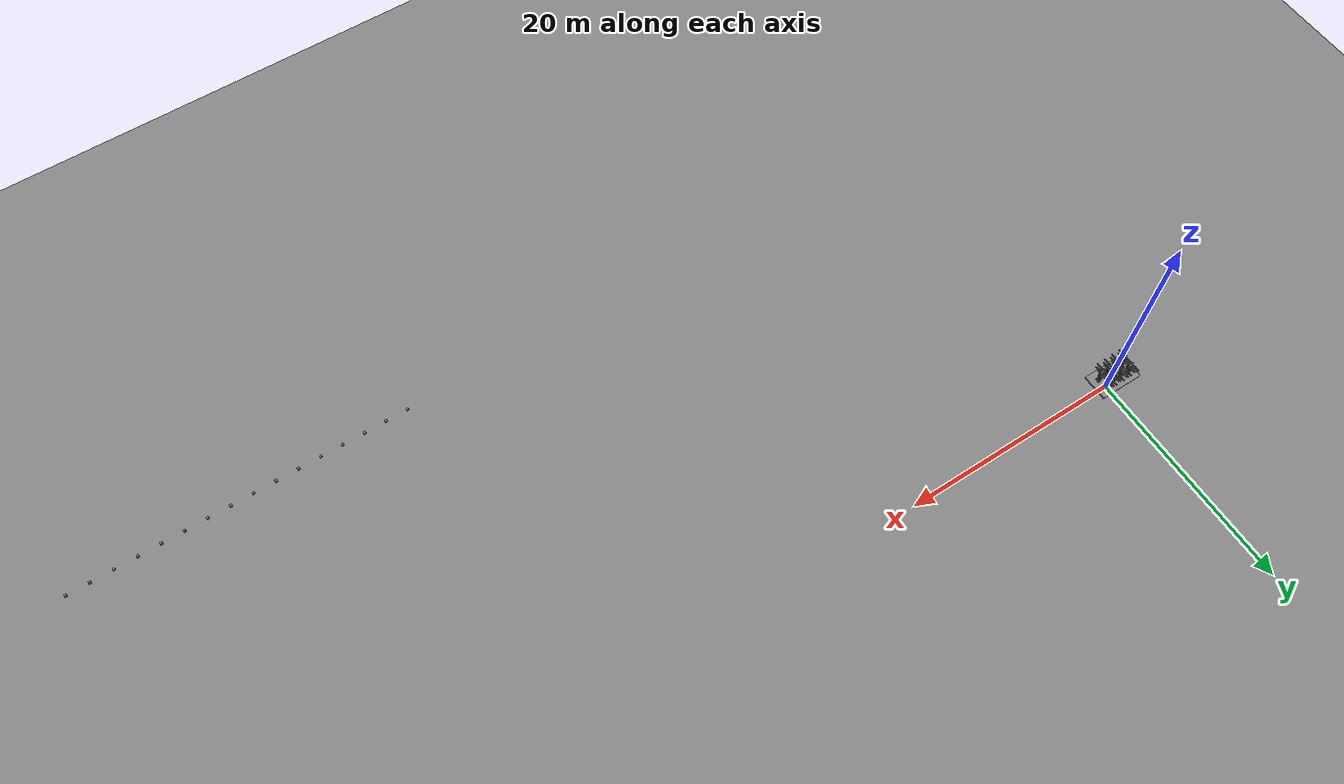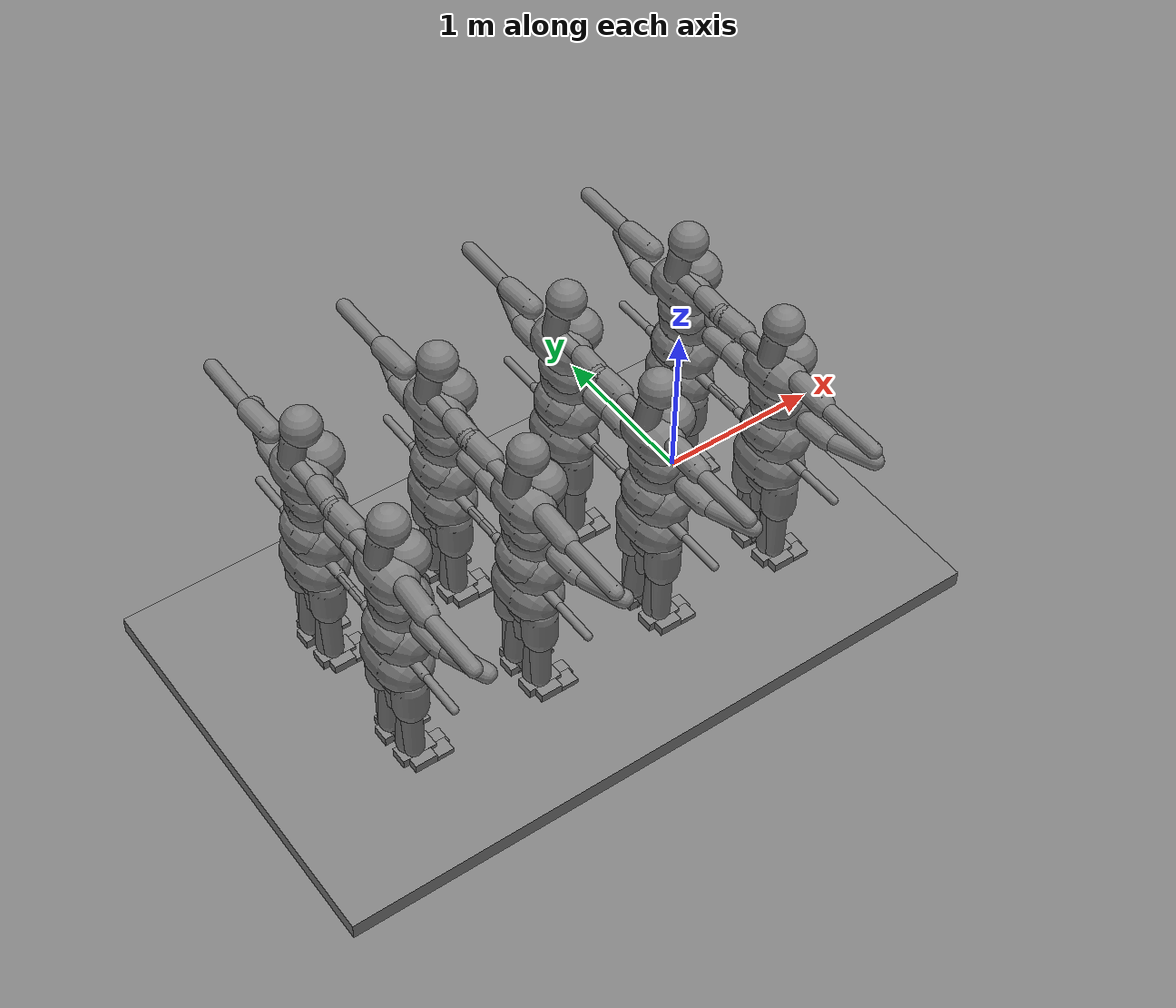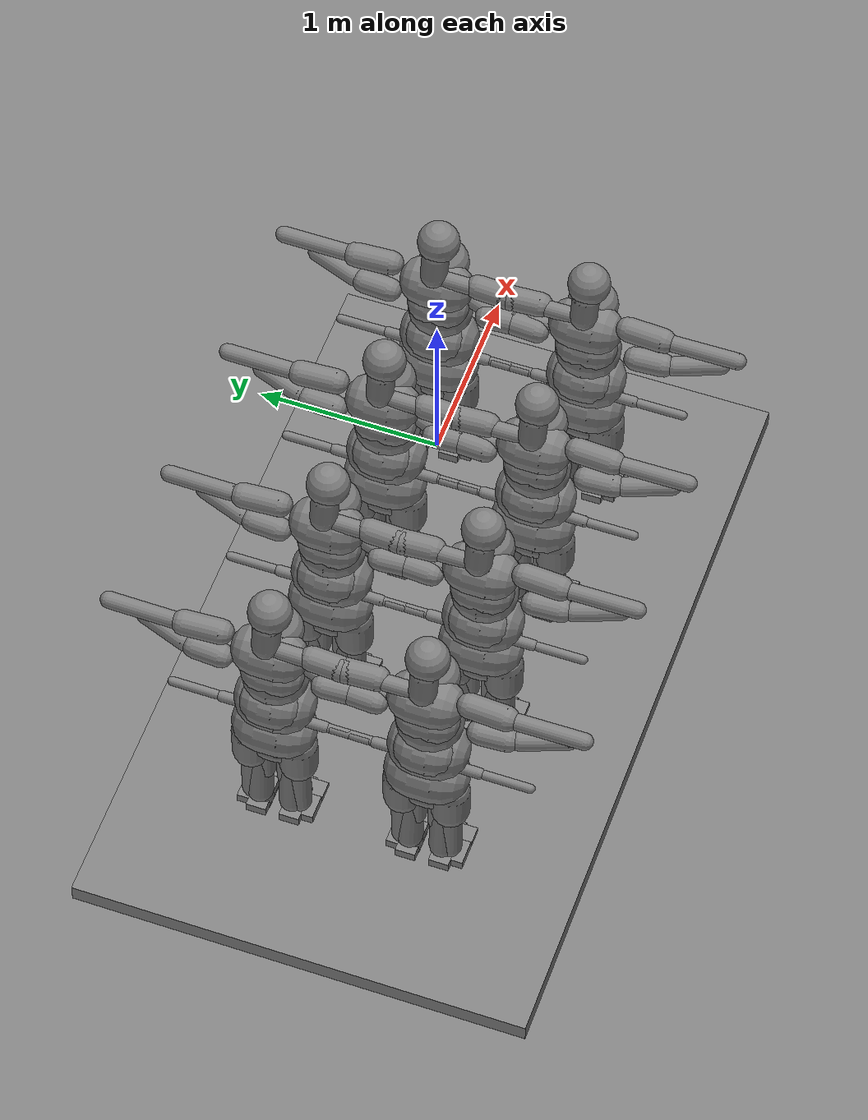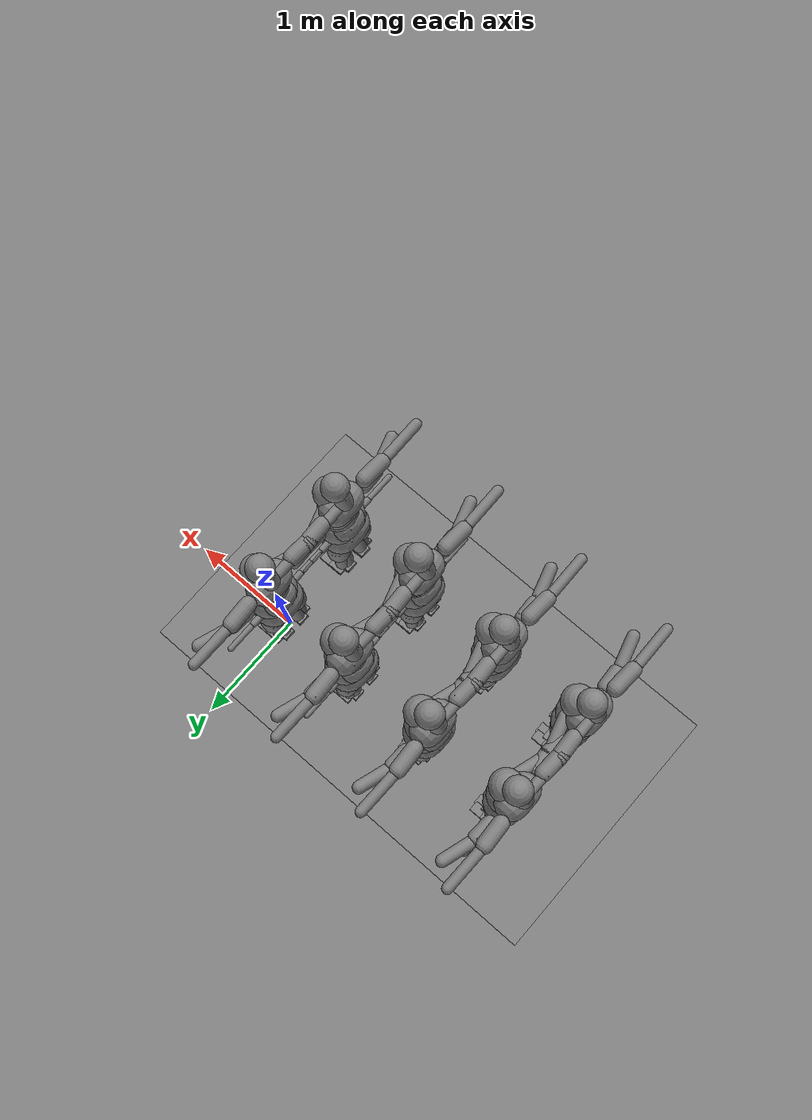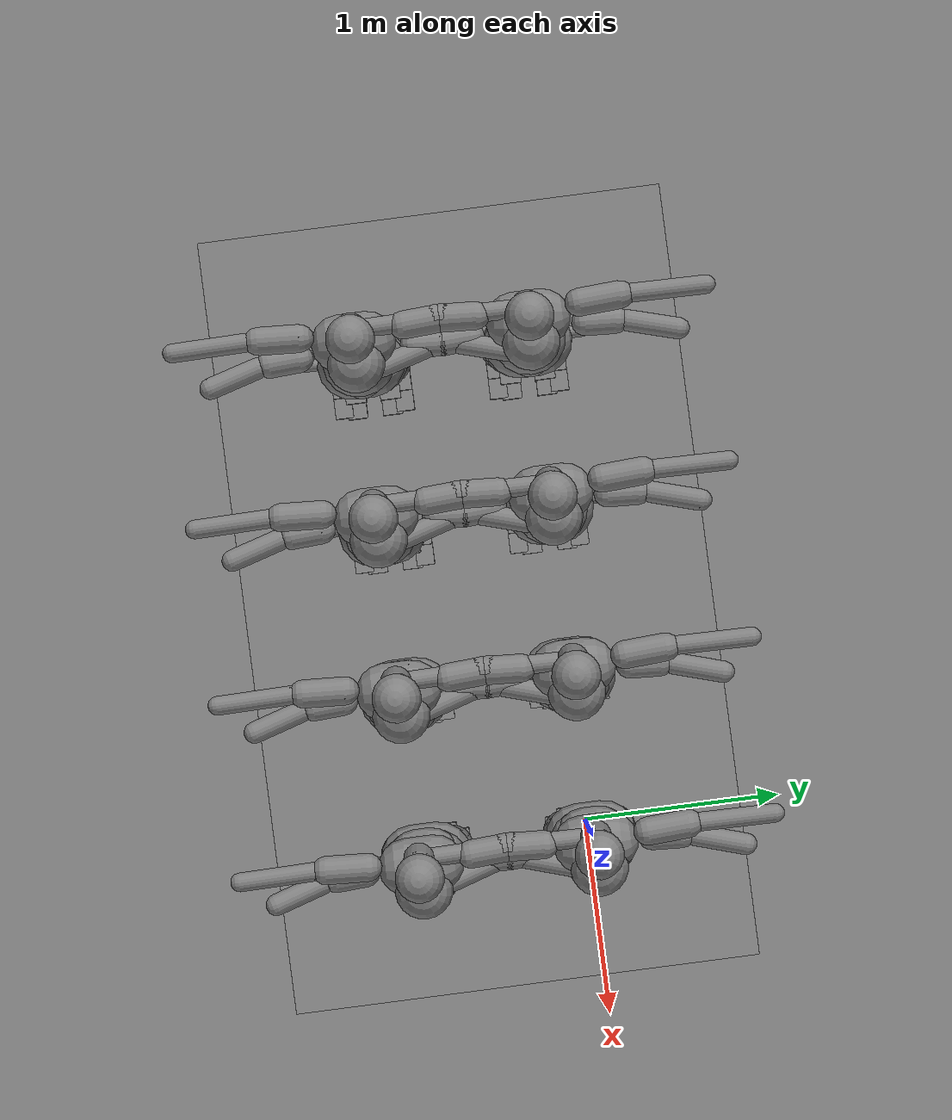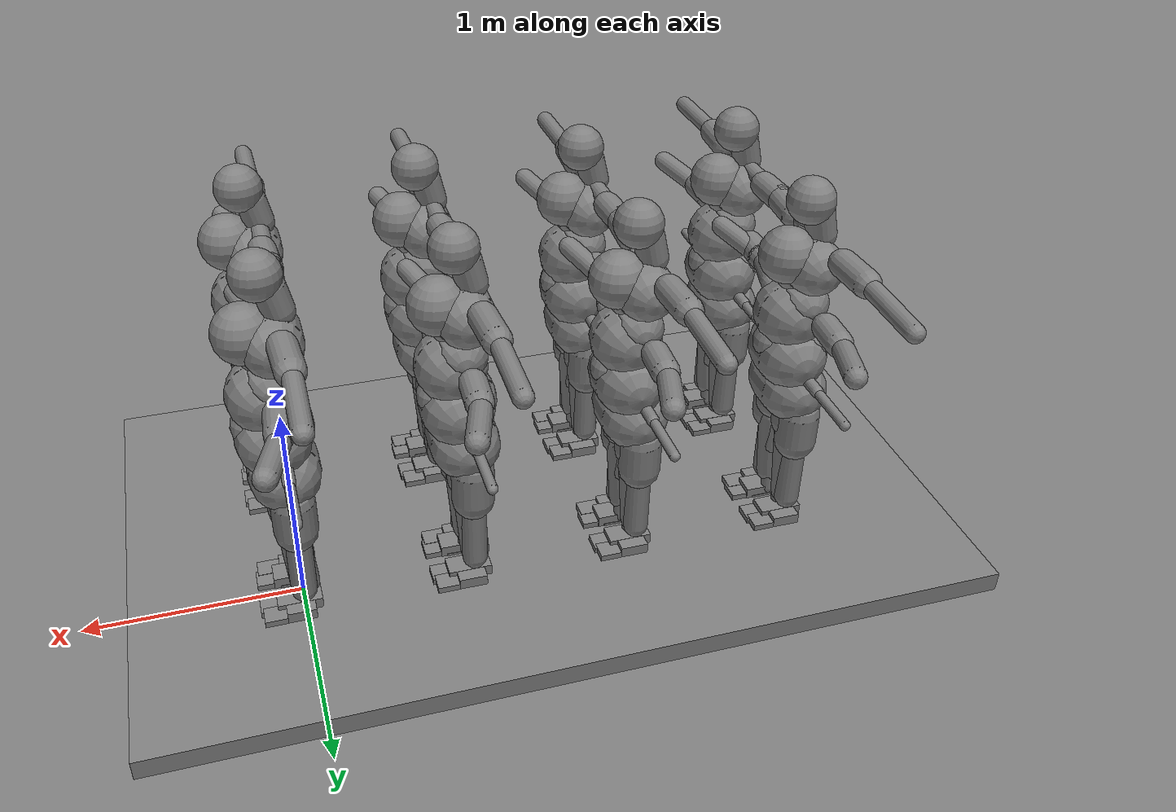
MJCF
<!-- GENERATED by training/tools/compose_mixed.py (shaker8, lineup roster). Do not edit. -->
<mujoco model="shaker8_mixed">
  <compiler angle="degree" autolimits="true" />
  <option timestep="0.005" gravity="0 0 -9.81" integrator="implicitfast" solver="Newton" iterations="20" cone="pyramidal" jacobian="auto">
    <flag multiccd="disable" />
  </option>
  <worldbody>
    <light name="sun" pos="0 0 5" dir="0 0 -1" directional="true" />
    <geom name="ground" type="plane" size="0 0 0.05" contype="65535" conaffinity="65535" condim="3" friction="1 0.005 0.0001" pos="0 0 -0.1" />
    <body name="shaker" pos="-1.2 -0.4 -0.05">
      <inertial pos="0 0 0" mass="1200" diaginertia="577 1601 2176" />
      <joint name="shaker_x" type="slide" axis="1 0 0" stiffness="290400" damping="9280" limited="true" range="-0.25 0.25" />
      <joint name="shaker_y" type="slide" axis="0 1 0" stiffness="290400" damping="9280" limited="true" range="-0.25 0.25" />
      <geom name="shaker" type="box" size="2 1.2 0.05" contype="65535" conaffinity="65535" condim="3" friction="1 0.005 0.0001" />
    </body>
    <body name="L0_pelvis" pos="-2.385941 0 0.966775">
      <inertial pos="-0.01696645 0 -0.003757688" quat="0.7071068 -0.7071068 0 0" mass="8.937766" diaginertia="0.0907144 0.0907144 0.07049761" />
      <freejoint name="L0_root" />
      <geom name="L0_pelvis_geom0" type="capsule" size="0.1357963 0.03473648" contype="65537" conaffinity="16646144" condim="3" friction="1 0.005 0.0001" pos="-0.01696645 0 -0.003757688" quat="0.7071068 -0.7071068 0 0" />
      <body name="L0_torso" pos="-0.000796 0 0.095775">
        <inertial pos="0.003384799 0 0.1412323" quat="0.7071068 -0.7071068 0 0" mass="13.05674" diaginertia="0.1165244 0.1165244 0.08048442" />
        <joint name="L0_abdomen_flex" type="hinge" pos="0 0 0" axis="0 1 0" range="-30 60" armature="0.02" />
        <joint name="L0_abdomen_lat" type="hinge" pos="0 0 0" axis="1 0 0" range="-35 35" armature="0.02" />
        <joint name="L0_abdomen_twist" type="hinge" pos="0 0 0" axis="0 0 1" range="-45 45" armature="0.02" />
        <geom name="L0_torso_geom0" type="capsule" size="0.1189253 0.04429121" contype="65537" conaffinity="16646144" condim="3" friction="1 0.005 0.0001" pos="0.003384799 0 0.1412323" quat="0.7071068 -0.7071068 0 0" />
        <body name="L0_chest" pos="-0.016728 0 0.279754">
          <inertial pos="-0.003824043 0 0.05326067" quat="0.7071068 -0.7071068 0 0" mass="12.76681" diaginertia="0.157376 0.157376 0.09756839" />
          <geom name="L0_chest_geom0" type="capsule" size="0.1315126 0.06314432" contype="65537" conaffinity="16646144" condim="3" friction="1 0.005 0.0001" pos="-0.003824043 0 0.05326067" quat="0.7071068 -0.7071068 0 0" />
          <body name="L0_head" pos="-0.048542 0 0.181344">
            <inertial pos="0.05070428 0 0.1332104" quat="0.6920062 0.1453527 0.1453527 0.6920062" mass="5.548613" diaginertia="0.0503217 0.05005417 0.02171975" />
            <geom name="L0_head_geom0" type="capsule" size="0.06994246 0.0600033" contype="65537" conaffinity="16646144" condim="3" friction="1 0.005 0.0001" pos="0.013404 0 0.058487" quat="0.9936623 0 0.1124062 0" />
            <geom name="L0_head_geom1" type="sphere" size="0.1098854" contype="65537" conaffinity="16646144" condim="3" friction="1 0.005 0.0001" pos="0.07270066 0 0.1772756" />
          </body>
          <body name="L0_upper_arm_l" pos="-0.033514 0.201796 0.161482">
            <inertial pos="-0.007092 0.126 0.00073" quat="0.7091489 -0.7039445 -0.03962202 0" mass="2.169458" diaginertia="0.01610463 0.01610463 0.004156322" />
            <joint name="L0_shoulder_elev_l" type="hinge" pos="0 0 0" axis="1 0 0" range="-95 80" armature="0.01" />
            <joint name="L0_shoulder_flex_l" type="hinge" pos="0 0 0" axis="0 0 -1" range="-60 170" armature="0.01" />
            <joint name="L0_shoulder_twist_l" type="hinge" pos="0 0 0" axis="0 1 0" range="-80 80" armature="0.01" />
            <geom name="L0_upper_arm_l_geom0" type="capsule" size="0.06392297 0.09424006" contype="65537" conaffinity="16646144" condim="3" friction="1 0.005 0.0001" pos="-0.007092 0.126 0.00073" quat="0.7091489 -0.7039445 -0.03962202 0" />
            <body name="L0_forearm_l" pos="-0.014184 0.252 0.00146">
              <inertial pos="0.0027005 0.1902425 -0.00161" quat="0.7041088 -0.7100206 0.01007877 0" mass="1.789553" diaginertia="0.02422419 0.02422419 0.001594476" />
              <joint name="L0_elbow_l" type="hinge" pos="0 0 0" axis="0 0 -1" range="0 145" armature="0.01" />
              <geom name="L0_forearm_l_geom0" type="capsule" size="0.04283781 0.1688496" contype="65537" conaffinity="16646144" condim="3" friction="1 0.005 0.0001" pos="0.0027005 0.1902425 -0.00161" quat="0.7041088 -0.7100206 0.01007877 0" />
            </body>
          </body>
          <body name="L0_upper_arm_r" pos="-0.033514 -0.201796 0.161482">
            <inertial pos="-0.007092 -0.126 0.00073" quat="0.7091489 0.7039445 -0.03962202 0" mass="2.169458" diaginertia="0.01610463 0.01610463 0.004156322" />
            <joint name="L0_shoulder_elev_r" type="hinge" pos="0 0 0" axis="-1 0 0" range="-95 80" armature="0.01" />
            <joint name="L0_shoulder_flex_r" type="hinge" pos="0 0 0" axis="0 0 1" range="-60 170" armature="0.01" />
            <joint name="L0_shoulder_twist_r" type="hinge" pos="0 0 0" axis="0 1 0" range="-80 80" armature="0.01" />
            <geom name="L0_upper_arm_r_geom0" type="capsule" size="0.06392297 0.09424006" contype="65537" conaffinity="16646144" condim="3" friction="1 0.005 0.0001" pos="-0.007092 -0.126 0.00073" quat="0.7091489 0.7039445 -0.03962202 0" />
            <body name="L0_forearm_r" pos="-0.014184 -0.252 0.00146">
              <inertial pos="0.0027005 -0.1902425 -0.00161" quat="0.7041088 0.7100206 0.01007877 0" mass="1.789553" diaginertia="0.02422419 0.02422419 0.001594476" />
              <joint name="L0_elbow_r" type="hinge" pos="0 0 0" axis="0 0 1" range="0 145" armature="0.01" />
              <geom name="L0_forearm_r_geom0" type="capsule" size="0.04283781 0.1688496" contype="65537" conaffinity="16646144" condim="3" friction="1 0.005 0.0001" pos="0.0027005 -0.1902425 -0.00161" quat="0.7041088 0.7100206 0.01007877 0" />
            </body>
          </body>
        </body>
      </body>
      <body name="L0_thigh_l" pos="0.000827 0.085706 -0.03016">
        <inertial pos="0.002864 0 -0.207727" quat="0.006893172 0 0.9999762 0" mass="11.32717" diaginertia="0.2130858 0.2130858 0.04235914" />
        <joint name="L0_hip_flex_l" type="hinge" pos="0 0 0" axis="0 -1 0" range="-30 120" armature="0.02" />
        <joint name="L0_hip_abd_l" type="hinge" pos="0 0 0" axis="1 0 0" range="-30 45" armature="0.02" />
        <joint name="L0_hip_rot_l" type="hinge" pos="0 0 0" axis="0 0 1" range="-40 40" armature="0.02" />
        <geom name="L0_thigh_l_geom0" type="capsule" size="0.08888116 0.1633062" contype="65792" conaffinity="16646400" condim="3" friction="1 0.005 0.0001" pos="0.002864 0 -0.207727" quat="0.006893172 0 0.9999762 0" />
        <body name="L0_shin_l" pos="0.005728 0 -0.415454">
          <inertial pos="-0.0159655 0 -0.214853" quat="0.03707781 0 -0.9993124 0" mass="3.459135" diaginertia="0.06386931 0.06386931 0.007533594" />
          <joint name="L0_knee_l" type="hinge" pos="0 0 0" axis="0 1 0" range="0 150" armature="0.02" />
          <geom name="L0_shin_l_geom0" type="capsule" size="0.06734565 0.1817725" contype="65792" conaffinity="16646400" condim="3" friction="1 0.005 0.0001" pos="-0.0159655 0 -0.214853" quat="0.03707781 0 -0.9993124 0" />
          <body name="L0_foot_l" pos="-0.031931 0 -0.429706">
            <inertial pos="0.03774256 0.002908948 -0.06798844" quat="1 0 0 0" mass="0.8497876" diaginertia="0.00103675 0.003237029 0.003763906" />
            <joint name="L0_ankle_dorsi_l" type="hinge" pos="0 0 0" axis="0 -1 0" range="-50 25" armature="0.01" />
            <joint name="L0_ankle_inv_l" type="hinge" pos="0 0 0" axis="-1 0 0" range="-20 30" armature="0.01" />
            <geom name="L0_foot_l_geom0" type="box" size="0.1026044 0.05253602 0.03" contype="65792" conaffinity="16646400" condim="3" friction="1 0.005 0.0001" pos="0.03774256 0.002908948 -0.06798844" />
            <body name="L0_toe_l" pos="0.140347 0 -0.07597">
              <inertial pos="0.03863281 0.004919875 -0.004518435" quat="1 0 0 0" mass="0.2499375" diaginertia="0.0002352078 0.0001498579 0.0003340368" />
              <joint name="L0_toe_l" type="hinge" pos="0 0 0" axis="0 -1 0" range="-30 60" stiffness="20" damping="1" armature="0.005" />
              <geom name="L0_toe_l_geom0" type="box" size="0.03863281 0.05016921 0.0175" contype="65792" conaffinity="16646400" condim="3" friction="1 0.005 0.0001" pos="0.03863281 0.004919875 -0.004518435" />
            </body>
          </body>
        </body>
      </body>
      <body name="L0_thigh_r" pos="0.000827 -0.085706 -0.03016">
        <inertial pos="0.002864 0 -0.207727" quat="0.006893172 0 0.9999762 0" mass="11.32717" diaginertia="0.2130858 0.2130858 0.04235914" />
        <joint name="L0_hip_flex_r" type="hinge" pos="0 0 0" axis="0 -1 0" range="-30 120" armature="0.02" />
        <joint name="L0_hip_abd_r" type="hinge" pos="0 0 0" axis="-1 0 0" range="-30 45" armature="0.02" />
        <joint name="L0_hip_rot_r" type="hinge" pos="0 0 0" axis="0 0 -1" range="-40 40" armature="0.02" />
        <geom name="L0_thigh_r_geom0" type="capsule" size="0.08888116 0.1633062" contype="65792" conaffinity="16646400" condim="3" friction="1 0.005 0.0001" pos="0.002864 0 -0.207727" quat="0.006893172 0 0.9999762 0" />
        <body name="L0_shin_r" pos="0.005728 0 -0.415454">
          <inertial pos="-0.0159655 0 -0.214853" quat="0.03707781 0 -0.9993124 0" mass="3.459135" diaginertia="0.06386931 0.06386931 0.007533594" />
          <joint name="L0_knee_r" type="hinge" pos="0 0 0" axis="0 1 0" range="0 150" armature="0.02" />
          <geom name="L0_shin_r_geom0" type="capsule" size="0.06734565 0.1817725" contype="65792" conaffinity="16646400" condim="3" friction="1 0.005 0.0001" pos="-0.0159655 0 -0.214853" quat="0.03707781 0 -0.9993124 0" />
          <body name="L0_foot_r" pos="-0.031931 0 -0.429706">
            <inertial pos="0.03774256 -0.002908948 -0.06798844" quat="1 0 0 0" mass="0.8497876" diaginertia="0.00103675 0.003237029 0.003763906" />
            <joint name="L0_ankle_dorsi_r" type="hinge" pos="0 0 0" axis="0 -1 0" range="-50 25" armature="0.01" />
            <joint name="L0_ankle_inv_r" type="hinge" pos="0 0 0" axis="1 0 0" range="-20 30" armature="0.01" />
            <geom name="L0_foot_r_geom0" type="box" size="0.1026044 0.05253602 0.03" contype="65792" conaffinity="16646400" condim="3" friction="1 0.005 0.0001" pos="0.03774256 -0.002908948 -0.06798844" />
            <body name="L0_toe_r" pos="0.140343 0 -0.075843">
              <inertial pos="0.03863281 -0.004919875 -0.004518435" quat="1 0 0 0" mass="0.2499375" diaginertia="0.0002352078 0.0001498579 0.0003340368" />
              <joint name="L0_toe_r" type="hinge" pos="0 0 0" axis="0 -1 0" range="-30 60" stiffness="20" damping="1" armature="0.005" />
              <geom name="L0_toe_r_geom0" type="box" size="0.03863281 0.05016921 0.0175" contype="65792" conaffinity="16646400" condim="3" friction="1 0.005 0.0001" pos="0.03863681 -0.004919875 -0.004645435" />
            </body>
          </body>
        </body>
      </body>
    </body>
    <body name="Z0_pelvis" pos="-2.4 0 0.559887">
      <inertial pos="-0.007612123 0 0.009433847" quat="0.7071068 -0.7071068 0 0" mass="2.457886" diaginertia="0.009705657 0.009705657 0.006605976" />
      <freejoint name="Z0_root" />
      <geom name="Z0_pelvis_geom0" type="capsule" size="0.07844793 0.03035992" contype="65792" conaffinity="16646400" condim="3" friction="1 0.005 0.0001" pos="-0.007612123 0 0.009433847" quat="0.7071068 -0.7071068 0 0" />
      <body name="Z0_torso" pos="-0.001231 -2.6e-05 0.062415">
        <inertial pos="-0.005324366 2.6e-05 0.03596058" quat="0.7071068 -0.7071068 0 0" mass="3.590602" diaginertia="0.009810929 0.009810929 0.006378186" />
        <joint name="Z0_abdomen_flex" type="hinge" pos="0 0 0" axis="0 1 0" range="-30 60" armature="0.002099598" />
        <joint name="Z0_abdomen_lat" type="hinge" pos="0 0 0" axis="1 0 0" range="-35 35" armature="0.002099598" />
        <joint name="Z0_abdomen_twist" type="hinge" pos="0 0 0" axis="0 0 1" range="-45 45" armature="0.002099598" />
        <geom name="Z0_torso_geom0" type="capsule" size="0.06358528 0.02750999" contype="65792" conaffinity="16646400" condim="3" friction="1 0.005 0.0001" pos="-0.005324366 2.6e-05 0.03596058" quat="0.7071068 -0.7071068 0 0" />
        <body name="Z0_chest" pos="-0.000412 0 0.109225">
          <inertial pos="0.02102744 2.6e-05 0.05248355" quat="0.7071068 -0.7071068 0 0" mass="3.510872" diaginertia="0.01368155 0.01368155 0.008567377" />
          <geom name="Z0_chest_geom0" type="capsule" size="0.07435712 0.03495606" contype="65792" conaffinity="16646400" condim="3" friction="1 0.005 0.0001" pos="0.02102744 2.6e-05 0.05248355" quat="0.7071068 -0.7071068 0 0" />
          <body name="Z0_head" pos="0.033148 0 0.156037">
            <inertial pos="0.06573305 1.878749e-05 0.0784395" quat="0.6614595 0.2478298 0.2473417 0.6632298" mass="1.525869" diaginertia="0.008143213 0.008139096 0.004756541" />
            <geom name="Z0_head_geom0" type="capsule" size="0.05753786 0.03165845" contype="65792" conaffinity="16646400" condim="3" friction="1 0.005 0.0001" pos="0.018568 0 0.0256415" quat="0.9512996 0 0.3082679 0" />
            <geom name="Z0_head_geom1" type="sphere" size="0.09675238" contype="65792" conaffinity="16646400" condim="3" friction="1 0.005 0.0001" pos="0.08383968 2.6e-05 0.09870861" />
          </body>
          <body name="Z0_upper_arm_l" pos="0.009612 0.129445 0.124194">
            <inertial pos="-0.000137 0.078008 7.7e-05" quat="0.7074557 -0.7067566 -0.001241227 0" mass="0.5966008" diaginertia="0.001505767 0.001505767 0.0002328844" />
            <joint name="Z0_shoulder_elev_l" type="hinge" pos="0 0 0" axis="1 0 0" range="-95 80" armature="0.001049799" />
            <joint name="Z0_shoulder_flex_l" type="hinge" pos="0 0 0" axis="0 0 -1" range="-60 170" armature="0.001049799" />
            <joint name="Z0_shoulder_twist_l" type="hinge" pos="0 0 0" axis="0 1 0" range="-80 80" armature="0.001049799" />
            <geom name="Z0_upper_arm_l_geom0" type="capsule" size="0.028608 0.06370416" contype="65792" conaffinity="16646400" condim="3" friction="1 0.005 0.0001" pos="-0.000137 0.078008 7.7e-05" quat="0.7074557 -0.7067566 -0.001241227 0" />
            <body name="Z0_forearm_l" pos="-0.000274 0.156016 0.000154">
              <inertial pos="9.064547e-05 0.1302764 3.230928e-05" quat="0.7071945 -0.7070189 0.0004919392 0" mass="0.492127" diaginertia="0.003034748 0.003034748 0.0001322193" />
              <joint name="Z0_elbow_l" type="hinge" pos="0 0 0" axis="0 0 -1" range="0 145" armature="0.001049799" />
              <geom name="Z0_forearm_l_geom0" type="capsule" size="0.0234555 0.1185487" contype="65792" conaffinity="16646400" condim="3" friction="1 0.005 0.0001" pos="9.064547e-05 0.1302764 3.230928e-05" quat="0.7071945 -0.7070189 0.0004919392 0" />
            </body>
          </body>
          <body name="Z0_upper_arm_r" pos="0.009612 -0.129445 0.124194">
            <inertial pos="-0.000137 -0.078008 7.7e-05" quat="0.7074557 0.7067566 -0.001241227 0" mass="0.5966008" diaginertia="0.001505767 0.001505767 0.0002328844" />
            <joint name="Z0_shoulder_elev_r" type="hinge" pos="0 0 0" axis="-1 0 0" range="-95 80" armature="0.001049799" />
            <joint name="Z0_shoulder_flex_r" type="hinge" pos="0 0 0" axis="0 0 1" range="-60 170" armature="0.001049799" />
            <joint name="Z0_shoulder_twist_r" type="hinge" pos="0 0 0" axis="0 1 0" range="-80 80" armature="0.001049799" />
            <geom name="Z0_upper_arm_r_geom0" type="capsule" size="0.028608 0.06370416" contype="65792" conaffinity="16646400" condim="3" friction="1 0.005 0.0001" pos="-0.000137 -0.077956 7.7e-05" quat="0.7074557 0.7067566 -0.001241227 0" />
            <body name="Z0_forearm_r" pos="-0.000271 -0.156311 0.000154">
              <inertial pos="9.064547e-05 -0.1302764 3.230928e-05" quat="0.7071945 0.7070189 0.0004919392 0" mass="0.492127" diaginertia="0.003034748 0.003034748 0.0001322193" />
              <joint name="Z0_elbow_r" type="hinge" pos="0 0 0" axis="0 0 1" range="0 145" armature="0.001049799" />
              <geom name="Z0_forearm_r_geom0" type="capsule" size="0.0234555 0.1185487" contype="65792" conaffinity="16646400" condim="3" friction="1 0.005 0.0001" pos="8.764547e-05 -0.1299294 3.230928e-05" quat="0.7071945 0.7070189 0.0004919392 0" />
            </body>
          </body>
        </body>
      </body>
      <body name="Z0_thigh_l" pos="0.006255 0.0602 -0.015578">
        <inertial pos="0 0 -0.1278905" quat="0 1 0 0" mass="3.114971" diaginertia="0.02209944 0.02209944 0.004297472" />
        <joint name="Z0_hip_flex_l" type="hinge" pos="0 0 0" axis="0 -1 0" range="-30 120" armature="0.002099598" />
        <joint name="Z0_hip_abd_l" type="hinge" pos="0 0 0" axis="1 0 0" range="-30 45" armature="0.002099598" />
        <joint name="Z0_hip_rot_l" type="hinge" pos="0 0 0" axis="0 0 1" range="-40 40" armature="0.002099598" />
        <geom name="Z0_thigh_l_geom0" type="capsule" size="0.05396597 0.1009075" contype="65792" conaffinity="16646400" condim="3" friction="1 0.005 0.0001" pos="0 0 -0.1278905" quat="0 1 0 0" />
        <body name="Z0_shin_l" pos="0 0 -0.255781">
          <inertial pos="0 0 -0.1340565" quat="0 1 0 0" mass="0.9512622" diaginertia="0.006572025 0.006572025 0.0005829297" />
          <joint name="Z0_knee_l" type="hinge" pos="0 0 0" axis="0 1 0" range="0 150" armature="0.002099598" />
          <geom name="Z0_shin_l_geom0" type="capsule" size="0.03561781 0.1162476" contype="65792" conaffinity="16646400" condim="3" friction="1 0.005 0.0001" pos="0 0 -0.1340565" quat="0 1 0 0" />
          <body name="Z0_foot_l" pos="0 0 -0.268113">
            <inertial pos="0.02989977 0.01554355 -0.02697956" quat="1 0 0 0" mass="0.2336916" diaginertia="0.0001722914 0.000345643 0.000464408" />
            <joint name="Z0_ankle_dorsi_l" type="hinge" pos="0 0 0" axis="0 -1 0" range="-50 25" armature="0.001049799" />
            <joint name="Z0_ankle_inv_l" type="hinge" pos="0 0 0" axis="-1 0 0" range="-20 30" armature="0.001049799" />
            <geom name="Z0_foot_l_geom0" type="box" size="0.06398123 0.04322278 0.01853566" contype="65792" conaffinity="16646400" condim="3" friction="1 0.005 0.0001" pos="0.02989977 0.01554355 -0.02697956" />
            <body name="Z0_toe_l" pos="0.093881 0.002417 -0.028506">
              <inertial pos="0.03375064 0.01336441 -0.006196754" quat="1 0 0 0" mass="0.06873282" diaginertia="4.657589e-05 2.877649e-05 6.999537e-05" />
              <joint name="Z0_toe_l" type="hinge" pos="0 0 0" axis="0 -1 0" range="-30 60" stiffness="3.398204" damping="0.1335558" armature="0.0005248994" />
              <geom name="Z0_toe_l_geom0" type="box" size="0.03375064 0.04377215 0.01081247" contype="65792" conaffinity="16646400" condim="3" friction="1 0.005 0.0001" pos="0.03375064 0.01336441 -0.006196754" />
            </body>
          </body>
        </body>
      </body>
      <body name="Z0_thigh_r" pos="0.006255 -0.060187 -0.015628">
        <inertial pos="0 0 -0.1278905" quat="0 -1 0 0" mass="3.114971" diaginertia="0.02209944 0.02209944 0.004297472" />
        <joint name="Z0_hip_flex_r" type="hinge" pos="0 0 0" axis="0 -1 0" range="-30 120" armature="0.002099598" />
        <joint name="Z0_hip_abd_r" type="hinge" pos="0 0 0" axis="-1 0 0" range="-30 45" armature="0.002099598" />
        <joint name="Z0_hip_rot_r" type="hinge" pos="0 0 0" axis="0 0 -1" range="-40 40" armature="0.002099598" />
        <geom name="Z0_thigh_r_geom0" type="capsule" size="0.05396597 0.1009075" contype="65792" conaffinity="16646400" condim="3" friction="1 0.005 0.0001" pos="0 -1.3e-05 -0.1278405" quat="0 1 0 0" />
        <body name="Z0_shin_r" pos="0 0 -0.252279">
          <inertial pos="0 0 -0.1340565" quat="0 -1 0 0" mass="0.9512622" diaginertia="0.006572025 0.006572025 0.0005829297" />
          <joint name="Z0_knee_r" type="hinge" pos="0 0 0" axis="0 1 0" range="0 150" armature="0.002099598" />
          <geom name="Z0_shin_r_geom0" type="capsule" size="0.03561781 0.1162476" contype="65792" conaffinity="16646400" condim="3" friction="1 0.005 0.0001" pos="0 -1.3e-05 -0.1375085" quat="0 1 0 0" />
          <body name="Z0_foot_r" pos="0 0 -0.269013">
            <inertial pos="0.02989977 -0.01554355 -0.02697956" quat="1 0 0 0" mass="0.2336916" diaginertia="0.0001722914 0.000345643 0.000464408" />
            <joint name="Z0_ankle_dorsi_r" type="hinge" pos="0 0 0" axis="0 -1 0" range="-50 25" armature="0.001049799" />
            <joint name="Z0_ankle_inv_r" type="hinge" pos="0 0 0" axis="1 0 0" range="-20 30" armature="0.001049799" />
            <geom name="Z0_foot_r_geom0" type="box" size="0.06398123 0.04322278 0.01853566" contype="65792" conaffinity="16646400" condim="3" friction="1 0.005 0.0001" pos="0.02989977 -0.01555655 -0.02953156" />
            <body name="Z0_toe_r" pos="0.089318 -0.003451 -0.028805">
              <inertial pos="0.03375064 -0.01336441 -0.006196754" quat="1 0 0 0" mass="0.06873282" diaginertia="4.657589e-05 2.877649e-05 6.999537e-05" />
              <joint name="Z0_toe_r" type="hinge" pos="0 0 0" axis="0 -1 0" range="-30 60" stiffness="3.398204" damping="0.1335558" armature="0.0005248994" />
              <geom name="Z0_toe_r_geom0" type="box" size="0.03375064 0.04377215 0.01081247" contype="65792" conaffinity="16646400" condim="3" friction="1 0.005 0.0001" pos="0.03831364 -0.01234341 -0.008449754" />
            </body>
          </body>
        </body>
      </body>
    </body>
    <body name="G0_pelvis" pos="-2.4 0 0.687518">
      <inertial pos="0.01369838 0 0.04943876" quat="0.7071068 -0.7071068 0 0" mass="7.261935" diaginertia="0.1167119 0.1167119 0.0797341" />
      <freejoint name="G0_root" />
      <geom name="G0_pelvis_geom0" type="capsule" size="0.158599 0.06079297" contype="65792" conaffinity="16646400" condim="3" friction="1 0.005 0.0001" pos="0.01369838 0 0.04943876" quat="0.7071068 -0.7071068 0 0" />
      <body name="G0_torso" pos="0.020331 0 0.113719">
        <inertial pos="0.01755155 0 0.1248414" quat="0.7071068 -0.7071068 0 0" mass="10.6086" diaginertia="0.1619971 0.1619971 0.1243668" />
        <joint name="G0_abdomen_flex" type="hinge" pos="0 0 0" axis="0 1 0" range="-30 60" armature="0.0123275" />
        <joint name="G0_abdomen_lat" type="hinge" pos="0 0 0" axis="1 0 0" range="-35 35" armature="0.0123275" />
        <joint name="G0_abdomen_twist" type="hinge" pos="0 0 0" axis="0 0 1" range="-45 45" armature="0.0123275" />
        <geom name="G0_torso_geom0" type="capsule" size="0.1653731 0.04429897" contype="65792" conaffinity="16646400" condim="3" friction="1 0.005 0.0001" pos="0.01755155 0 0.1248414" quat="0.7071068 -0.7071068 0 0" />
        <body name="G0_chest" pos="0.030436 0 0.239868">
          <inertial pos="0.00322715 0 0.09331725" quat="0.7071068 -0.7071068 0 0" mass="10.37303" diaginertia="0.1172803 0.1172803 0.1115634" />
          <geom name="G0_chest_geom0" type="capsule" size="0.1624991 0.00853077" contype="65792" conaffinity="16646400" condim="3" friction="1 0.005 0.0001" pos="0.00322715 0 0.09331725" quat="0.7071068 -0.7071068 0 0" />
          <body name="G0_head" pos="-0.021542 0 0.235281">
            <inertial pos="0.06321418 0 0.1408943" quat="0.6957955 0.1259707 0.1259707 0.6957955" mass="4.508248" diaginertia="0.04211547 0.0419446 0.02714084" />
            <geom name="G0_head_geom0" type="capsule" size="0.06483854 0.04523582" contype="65792" conaffinity="16646400" condim="3" friction="1 0.005 0.0001" pos="0.028002 0 0.035527" quat="0.9448209 0 0.3275873 0" />
            <geom name="G0_head_geom1" type="sphere" size="0.1320292" contype="65792" conaffinity="16646400" condim="3" friction="1 0.005 0.0001" pos="0.07174901 0 0.1664336" />
          </body>
          <body name="G0_upper_arm_l" pos="-0.036923 0.233515 0.166949">
            <inertial pos="0.005906 0.102669 9.85e-05" quat="0.7074453 -0.7056016 0.0405895 0" mass="1.762684" diaginertia="0.009485407 0.009485407 0.003166983" />
            <joint name="G0_shoulder_elev_l" type="hinge" pos="0 0 0" axis="1 0 0" range="-95 80" armature="0.00616375" />
            <joint name="G0_shoulder_flex_l" type="hinge" pos="0 0 0" axis="0 0 -1" range="-60 170" armature="0.00616375" />
            <joint name="G0_shoulder_twist_l" type="hinge" pos="0 0 0" axis="0 1 0" range="-80 80" armature="0.00616375" />
            <geom name="G0_upper_arm_l_geom0" type="capsule" size="0.06227151 0.07170302" contype="65792" conaffinity="16646400" condim="3" friction="1 0.005 0.0001" pos="0.005906 0.102669 9.85e-05" quat="0.7074453 -0.7056016 0.0405895 0" />
            <body name="G0_forearm_l" pos="0.011812 0.205338 0.000197">
              <inertial pos="0.04204427 0.1378525 0.01519491" quat="0.743253 -0.6399094 0.195169 0" mass="1.454011" diaginertia="0.01246534 0.01246534 0.001752529" />
              <joint name="G0_elbow_l" type="hinge" pos="0 0 0" axis="0 0 -1" range="0 145" armature="0.00616375" />
              <geom name="G0_forearm_l_geom0" type="capsule" size="0.0502065 0.1198171" contype="65792" conaffinity="16646400" condim="3" friction="1 0.005 0.0001" pos="0.04204427 0.1378525 0.01519491" quat="0.743253 -0.6399094 0.195169 0" />
            </body>
          </body>
          <body name="G0_upper_arm_r" pos="-0.036923 -0.233515 0.166949">
            <inertial pos="0.005906 -0.102669 9.85e-05" quat="0.7074453 0.7056016 0.0405895 0" mass="1.762684" diaginertia="0.009485407 0.009485407 0.003166983" />
            <joint name="G0_shoulder_elev_r" type="hinge" pos="0 0 0" axis="-1 0 0" range="-95 80" armature="0.00616375" />
            <joint name="G0_shoulder_flex_r" type="hinge" pos="0 0 0" axis="0 0 1" range="-60 170" armature="0.00616375" />
            <joint name="G0_shoulder_twist_r" type="hinge" pos="0 0 0" axis="0 1 0" range="-80 80" armature="0.00616375" />
            <geom name="G0_upper_arm_r_geom0" type="capsule" size="0.06227151 0.07170302" contype="65792" conaffinity="16646400" condim="3" friction="1 0.005 0.0001" pos="0.005906 -0.102669 9.85e-05" quat="0.7074453 0.7056016 0.0405895 0" />
            <body name="G0_forearm_r" pos="0.011812 -0.205338 0.000197">
              <inertial pos="0.04204427 -0.1378525 0.01519491" quat="0.743253 0.6399094 0.195169 0" mass="1.454011" diaginertia="0.01246534 0.01246534 0.001752529" />
              <joint name="G0_elbow_r" type="hinge" pos="0 0 0" axis="0 0 1" range="0 145" armature="0.00616375" />
              <geom name="G0_forearm_r_geom0" type="capsule" size="0.0502065 0.1198171" contype="65792" conaffinity="16646400" condim="3" friction="1 0.005 0.0001" pos="0.04204427 -0.1378525 0.01519491" quat="0.743253 0.6399094 0.195169 0" />
            </body>
          </body>
        </body>
      </body>
      <body name="G0_thigh_l" pos="0 0.125029 0">
        <inertial pos="0 0 -0.131265" quat="0 1 0 0" mass="9.203324" diaginertia="0.09214218 0.09214218 0.04077778" />
        <joint name="G0_hip_flex_l" type="hinge" pos="0 0 0" axis="0 -1 0" range="-30 120" armature="0.0123275" />
        <joint name="G0_hip_abd_l" type="hinge" pos="0 0 0" axis="1 0 0" range="-30 45" armature="0.0123275" />
        <joint name="G0_hip_rot_l" type="hinge" pos="0 0 0" axis="0 0 1" range="-40 40" armature="0.0123275" />
        <geom name="G0_thigh_l_geom0" type="capsule" size="0.09862867 0.08195066" contype="65792" conaffinity="16646400" condim="3" friction="1 0.005 0.0001" pos="0 0 -0.131265" quat="0 1 0 0" />
        <body name="G0_shin_l" pos="0 0 -0.26253">
          <inertial pos="5e-07 0 -0.166659" quat="1.500069e-06 0 1 0" mass="2.810547" diaginertia="0.03208556 0.03208556 0.004705445" />
          <joint name="G0_knee_l" type="hinge" pos="0 0 0" axis="0 1 0" range="0 150" armature="0.0123275" />
          <geom name="G0_shin_l_geom0" type="capsule" size="0.05920442 0.1370568" contype="65792" conaffinity="16646400" condim="3" friction="1 0.005 0.0001" pos="5e-07 0 -0.166659" quat="1.500069e-06 0 1 0" />
          <body name="G0_foot_l" pos="1e-06 0 -0.333318">
            <inertial pos="0.02615167 0.01023298 -0.06556776" quat="1 0 0 0" mass="0.6904524" diaginertia="0.001207338 0.001169489 0.002062555" />
            <joint name="G0_ankle_dorsi_l" type="hinge" pos="0 0 0" axis="0 -1 0" range="-50 25" armature="0.00616375" />
            <joint name="G0_ankle_inv_l" type="hinge" pos="0 0 0" axis="-1 0 0" range="-20 30" armature="0.00616375" />
            <geom name="G0_foot_l_geom0" type="box" size="0.06632233 0.06755075 0.02612956" contype="65792" conaffinity="16646400" condim="3" friction="1 0.005 0.0001" pos="0.02615167 0.01023298 -0.06556776" />
            <body name="G0_toe_l" pos="0.092474 0 -0.063281">
              <inertial pos="0.05151134 0.03296192 -0.01317408" quat="1 0 0 0" mass="0.2030742" diaginertia="0.0001578715 0.0001953401 0.0003217586" />
              <joint name="G0_toe_l" type="hinge" pos="0 0 0" axis="0 -1 0" range="-30 60" stiffness="14.15351" damping="0.6604495" armature="0.003081875" />
              <geom name="G0_toe_l_geom0" type="box" size="0.05151134 0.04582464 0.01524224" contype="65792" conaffinity="16646400" condim="3" friction="1 0.005 0.0001" pos="0.05151134 0.03296192 -0.01317408" />
            </body>
          </body>
        </body>
      </body>
      <body name="G0_thigh_r" pos="0 -0.125029 0">
        <inertial pos="0 0 -0.131265" quat="0 -1 0 0" mass="9.203324" diaginertia="0.09214218 0.09214218 0.04077778" />
        <joint name="G0_hip_flex_r" type="hinge" pos="0 0 0" axis="0 -1 0" range="-30 120" armature="0.0123275" />
        <joint name="G0_hip_abd_r" type="hinge" pos="0 0 0" axis="-1 0 0" range="-30 45" armature="0.0123275" />
        <joint name="G0_hip_rot_r" type="hinge" pos="0 0 0" axis="0 0 -1" range="-40 40" armature="0.0123275" />
        <geom name="G0_thigh_r_geom0" type="capsule" size="0.09862867 0.08195066" contype="65792" conaffinity="16646400" condim="3" friction="1 0.005 0.0001" pos="0 0 -0.131265" quat="0 1 0 0" />
        <body name="G0_shin_r" pos="0 0 -0.26253">
          <inertial pos="5e-07 0 -0.166659" quat="1.500069e-06 0 1 0" mass="2.810547" diaginertia="0.03208556 0.03208556 0.004705445" />
          <joint name="G0_knee_r" type="hinge" pos="0 0 0" axis="0 1 0" range="0 150" armature="0.0123275" />
          <geom name="G0_shin_r_geom0" type="capsule" size="0.05920442 0.1370568" contype="65792" conaffinity="16646400" condim="3" friction="1 0.005 0.0001" pos="5e-07 0 -0.166659" quat="1.500069e-06 0 1 0" />
          <body name="G0_foot_r" pos="1e-06 0 -0.333318">
            <inertial pos="0.02615167 -0.01023298 -0.06556776" quat="1 0 0 0" mass="0.6904524" diaginertia="0.001207338 0.001169489 0.002062555" />
            <joint name="G0_ankle_dorsi_r" type="hinge" pos="0 0 0" axis="0 -1 0" range="-50 25" armature="0.00616375" />
            <joint name="G0_ankle_inv_r" type="hinge" pos="0 0 0" axis="1 0 0" range="-20 30" armature="0.00616375" />
            <geom name="G0_foot_r_geom0" type="box" size="0.06632233 0.06755075 0.02612956" contype="65792" conaffinity="16646400" condim="3" friction="1 0.005 0.0001" pos="0.02615167 -0.01023298 -0.06556776" />
            <body name="G0_toe_r" pos="0.092474 0 -0.063281">
              <inertial pos="0.05151134 -0.03296192 -0.01317408" quat="1 0 0 0" mass="0.2030742" diaginertia="0.0001578715 0.0001953401 0.0003217586" />
              <joint name="G0_toe_r" type="hinge" pos="0 0 0" axis="0 -1 0" range="-30 60" stiffness="14.15351" damping="0.6604495" armature="0.003081875" />
              <geom name="G0_toe_r_geom0" type="box" size="0.05151134 0.04582464 0.01524224" contype="65792" conaffinity="16646400" condim="3" friction="1 0.005 0.0001" pos="0.05151134 -0.03296192 -0.01317408" />
            </body>
          </body>
        </body>
      </body>
    </body>
    <body name="L1_pelvis" pos="-1.585941 0 0.966775">
      <inertial pos="-0.01696645 0 -0.003757688" quat="0.7071068 -0.7071068 0 0" mass="8.937766" diaginertia="0.0907144 0.0907144 0.07049761" />
      <freejoint name="L1_root" />
      <geom name="L1_pelvis_geom0" type="capsule" size="0.1357963 0.03473648" contype="131074" conaffinity="16580608" condim="3" friction="1 0.005 0.0001" pos="-0.01696645 0 -0.003757688" quat="0.7071068 -0.7071068 0 0" />
      <body name="L1_torso" pos="-0.000796 0 0.095775">
        <inertial pos="0.003384799 0 0.1412323" quat="0.7071068 -0.7071068 0 0" mass="13.05674" diaginertia="0.1165244 0.1165244 0.08048442" />
        <joint name="L1_abdomen_flex" type="hinge" pos="0 0 0" axis="0 1 0" range="-30 60" armature="0.02" />
        <joint name="L1_abdomen_lat" type="hinge" pos="0 0 0" axis="1 0 0" range="-35 35" armature="0.02" />
        <joint name="L1_abdomen_twist" type="hinge" pos="0 0 0" axis="0 0 1" range="-45 45" armature="0.02" />
        <geom name="L1_torso_geom0" type="capsule" size="0.1189253 0.04429121" contype="131074" conaffinity="16580608" condim="3" friction="1 0.005 0.0001" pos="0.003384799 0 0.1412323" quat="0.7071068 -0.7071068 0 0" />
        <body name="L1_chest" pos="-0.016728 0 0.279754">
          <inertial pos="-0.003824043 0 0.05326067" quat="0.7071068 -0.7071068 0 0" mass="12.76681" diaginertia="0.157376 0.157376 0.09756839" />
          <geom name="L1_chest_geom0" type="capsule" size="0.1315126 0.06314432" contype="131074" conaffinity="16580608" condim="3" friction="1 0.005 0.0001" pos="-0.003824043 0 0.05326067" quat="0.7071068 -0.7071068 0 0" />
          <body name="L1_head" pos="-0.048542 0 0.181344">
            <inertial pos="0.05070428 0 0.1332104" quat="0.6920062 0.1453527 0.1453527 0.6920062" mass="5.548613" diaginertia="0.0503217 0.05005417 0.02171975" />
            <geom name="L1_head_geom0" type="capsule" size="0.06994246 0.0600033" contype="131074" conaffinity="16580608" condim="3" friction="1 0.005 0.0001" pos="0.013404 0 0.058487" quat="0.9936623 0 0.1124062 0" />
            <geom name="L1_head_geom1" type="sphere" size="0.1098854" contype="131074" conaffinity="16580608" condim="3" friction="1 0.005 0.0001" pos="0.07270066 0 0.1772756" />
          </body>
          <body name="L1_upper_arm_l" pos="-0.033514 0.201796 0.161482">
            <inertial pos="-0.007092 0.126 0.00073" quat="0.7091489 -0.7039445 -0.03962202 0" mass="2.169458" diaginertia="0.01610463 0.01610463 0.004156322" />
            <joint name="L1_shoulder_elev_l" type="hinge" pos="0 0 0" axis="1 0 0" range="-95 80" armature="0.01" />
            <joint name="L1_shoulder_flex_l" type="hinge" pos="0 0 0" axis="0 0 -1" range="-60 170" armature="0.01" />
            <joint name="L1_shoulder_twist_l" type="hinge" pos="0 0 0" axis="0 1 0" range="-80 80" armature="0.01" />
            <geom name="L1_upper_arm_l_geom0" type="capsule" size="0.06392297 0.09424006" contype="131074" conaffinity="16580608" condim="3" friction="1 0.005 0.0001" pos="-0.007092 0.126 0.00073" quat="0.7091489 -0.7039445 -0.03962202 0" />
            <body name="L1_forearm_l" pos="-0.014184 0.252 0.00146">
              <inertial pos="0.0027005 0.1902425 -0.00161" quat="0.7041088 -0.7100206 0.01007877 0" mass="1.789553" diaginertia="0.02422419 0.02422419 0.001594476" />
              <joint name="L1_elbow_l" type="hinge" pos="0 0 0" axis="0 0 -1" range="0 145" armature="0.01" />
              <geom name="L1_forearm_l_geom0" type="capsule" size="0.04283781 0.1688496" contype="131074" conaffinity="16580608" condim="3" friction="1 0.005 0.0001" pos="0.0027005 0.1902425 -0.00161" quat="0.7041088 -0.7100206 0.01007877 0" />
            </body>
          </body>
          <body name="L1_upper_arm_r" pos="-0.033514 -0.201796 0.161482">
            <inertial pos="-0.007092 -0.126 0.00073" quat="0.7091489 0.7039445 -0.03962202 0" mass="2.169458" diaginertia="0.01610463 0.01610463 0.004156322" />
            <joint name="L1_shoulder_elev_r" type="hinge" pos="0 0 0" axis="-1 0 0" range="-95 80" armature="0.01" />
            <joint name="L1_shoulder_flex_r" type="hinge" pos="0 0 0" axis="0 0 1" range="-60 170" armature="0.01" />
            <joint name="L1_shoulder_twist_r" type="hinge" pos="0 0 0" axis="0 1 0" range="-80 80" armature="0.01" />
            <geom name="L1_upper_arm_r_geom0" type="capsule" size="0.06392297 0.09424006" contype="131074" conaffinity="16580608" condim="3" friction="1 0.005 0.0001" pos="-0.007092 -0.126 0.00073" quat="0.7091489 0.7039445 -0.03962202 0" />
            <body name="L1_forearm_r" pos="-0.014184 -0.252 0.00146">
              <inertial pos="0.0027005 -0.1902425 -0.00161" quat="0.7041088 0.7100206 0.01007877 0" mass="1.789553" diaginertia="0.02422419 0.02422419 0.001594476" />
              <joint name="L1_elbow_r" type="hinge" pos="0 0 0" axis="0 0 1" range="0 145" armature="0.01" />
              <geom name="L1_forearm_r_geom0" type="capsule" size="0.04283781 0.1688496" contype="131074" conaffinity="16580608" condim="3" friction="1 0.005 0.0001" pos="0.0027005 -0.1902425 -0.00161" quat="0.7041088 0.7100206 0.01007877 0" />
            </body>
          </body>
        </body>
      </body>
      <body name="L1_thigh_l" pos="0.000827 0.085706 -0.03016">
        <inertial pos="0.002864 0 -0.207727" quat="0.006893172 0 0.9999762 0" mass="11.32717" diaginertia="0.2130858 0.2130858 0.04235914" />
        <joint name="L1_hip_flex_l" type="hinge" pos="0 0 0" axis="0 -1 0" range="-30 120" armature="0.02" />
        <joint name="L1_hip_abd_l" type="hinge" pos="0 0 0" axis="1 0 0" range="-30 45" armature="0.02" />
        <joint name="L1_hip_rot_l" type="hinge" pos="0 0 0" axis="0 0 1" range="-40 40" armature="0.02" />
        <geom name="L1_thigh_l_geom0" type="capsule" size="0.08888116 0.1633062" contype="131584" conaffinity="16581120" condim="3" friction="1 0.005 0.0001" pos="0.002864 0 -0.207727" quat="0.006893172 0 0.9999762 0" />
        <body name="L1_shin_l" pos="0.005728 0 -0.415454">
          <inertial pos="-0.0159655 0 -0.214853" quat="0.03707781 0 -0.9993124 0" mass="3.459135" diaginertia="0.06386931 0.06386931 0.007533594" />
          <joint name="L1_knee_l" type="hinge" pos="0 0 0" axis="0 1 0" range="0 150" armature="0.02" />
          <geom name="L1_shin_l_geom0" type="capsule" size="0.06734565 0.1817725" contype="131584" conaffinity="16581120" condim="3" friction="1 0.005 0.0001" pos="-0.0159655 0 -0.214853" quat="0.03707781 0 -0.9993124 0" />
          <body name="L1_foot_l" pos="-0.031931 0 -0.429706">
            <inertial pos="0.03774256 0.002908948 -0.06798844" quat="1 0 0 0" mass="0.8497876" diaginertia="0.00103675 0.003237029 0.003763906" />
            <joint name="L1_ankle_dorsi_l" type="hinge" pos="0 0 0" axis="0 -1 0" range="-50 25" armature="0.01" />
            <joint name="L1_ankle_inv_l" type="hinge" pos="0 0 0" axis="-1 0 0" range="-20 30" armature="0.01" />
            <geom name="L1_foot_l_geom0" type="box" size="0.1026044 0.05253602 0.03" contype="131584" conaffinity="16581120" condim="3" friction="1 0.005 0.0001" pos="0.03774256 0.002908948 -0.06798844" />
            <body name="L1_toe_l" pos="0.140347 0 -0.07597">
              <inertial pos="0.03863281 0.004919875 -0.004518435" quat="1 0 0 0" mass="0.2499375" diaginertia="0.0002352078 0.0001498579 0.0003340368" />
              <joint name="L1_toe_l" type="hinge" pos="0 0 0" axis="0 -1 0" range="-30 60" stiffness="20" damping="1" armature="0.005" />
              <geom name="L1_toe_l_geom0" type="box" size="0.03863281 0.05016921 0.0175" contype="131584" conaffinity="16581120" condim="3" friction="1 0.005 0.0001" pos="0.03863281 0.004919875 -0.004518435" />
            </body>
          </body>
        </body>
      </body>
      <body name="L1_thigh_r" pos="0.000827 -0.085706 -0.03016">
        <inertial pos="0.002864 0 -0.207727" quat="0.006893172 0 0.9999762 0" mass="11.32717" diaginertia="0.2130858 0.2130858 0.04235914" />
        <joint name="L1_hip_flex_r" type="hinge" pos="0 0 0" axis="0 -1 0" range="-30 120" armature="0.02" />
        <joint name="L1_hip_abd_r" type="hinge" pos="0 0 0" axis="-1 0 0" range="-30 45" armature="0.02" />
        <joint name="L1_hip_rot_r" type="hinge" pos="0 0 0" axis="0 0 -1" range="-40 40" armature="0.02" />
        <geom name="L1_thigh_r_geom0" type="capsule" size="0.08888116 0.1633062" contype="131584" conaffinity="16581120" condim="3" friction="1 0.005 0.0001" pos="0.002864 0 -0.207727" quat="0.006893172 0 0.9999762 0" />
        <body name="L1_shin_r" pos="0.005728 0 -0.415454">
          <inertial pos="-0.0159655 0 -0.214853" quat="0.03707781 0 -0.9993124 0" mass="3.459135" diaginertia="0.06386931 0.06386931 0.007533594" />
          <joint name="L1_knee_r" type="hinge" pos="0 0 0" axis="0 1 0" range="0 150" armature="0.02" />
          <geom name="L1_shin_r_geom0" type="capsule" size="0.06734565 0.1817725" contype="131584" conaffinity="16581120" condim="3" friction="1 0.005 0.0001" pos="-0.0159655 0 -0.214853" quat="0.03707781 0 -0.9993124 0" />
          <body name="L1_foot_r" pos="-0.031931 0 -0.429706">
            <inertial pos="0.03774256 -0.002908948 -0.06798844" quat="1 0 0 0" mass="0.8497876" diaginertia="0.00103675 0.003237029 0.003763906" />
            <joint name="L1_ankle_dorsi_r" type="hinge" pos="0 0 0" axis="0 -1 0" range="-50 25" armature="0.01" />
            <joint name="L1_ankle_inv_r" type="hinge" pos="0 0 0" axis="1 0 0" range="-20 30" armature="0.01" />
            <geom name="L1_foot_r_geom0" type="box" size="0.1026044 0.05253602 0.03" contype="131584" conaffinity="16581120" condim="3" friction="1 0.005 0.0001" pos="0.03774256 -0.002908948 -0.06798844" />
            <body name="L1_toe_r" pos="0.140343 0 -0.075843">
              <inertial pos="0.03863281 -0.004919875 -0.004518435" quat="1 0 0 0" mass="0.2499375" diaginertia="0.0002352078 0.0001498579 0.0003340368" />
              <joint name="L1_toe_r" type="hinge" pos="0 0 0" axis="0 -1 0" range="-30 60" stiffness="20" damping="1" armature="0.005" />
              <geom name="L1_toe_r_geom0" type="box" size="0.03863281 0.05016921 0.0175" contype="131584" conaffinity="16581120" condim="3" friction="1 0.005 0.0001" pos="0.03863681 -0.004919875 -0.004645435" />
            </body>
          </body>
        </body>
      </body>
    </body>
    <body name="Z1_pelvis" pos="-1.6 0 0.559887">
      <inertial pos="-0.007612123 0 0.009433847" quat="0.7071068 -0.7071068 0 0" mass="2.457886" diaginertia="0.009705657 0.009705657 0.006605976" />
      <freejoint name="Z1_root" />
      <geom name="Z1_pelvis_geom0" type="capsule" size="0.07844793 0.03035992" contype="131584" conaffinity="16581120" condim="3" friction="1 0.005 0.0001" pos="-0.007612123 0 0.009433847" quat="0.7071068 -0.7071068 0 0" />
      <body name="Z1_torso" pos="-0.001231 -2.6e-05 0.062415">
        <inertial pos="-0.005324366 2.6e-05 0.03596058" quat="0.7071068 -0.7071068 0 0" mass="3.590602" diaginertia="0.009810929 0.009810929 0.006378186" />
        <joint name="Z1_abdomen_flex" type="hinge" pos="0 0 0" axis="0 1 0" range="-30 60" armature="0.002099598" />
        <joint name="Z1_abdomen_lat" type="hinge" pos="0 0 0" axis="1 0 0" range="-35 35" armature="0.002099598" />
        <joint name="Z1_abdomen_twist" type="hinge" pos="0 0 0" axis="0 0 1" range="-45 45" armature="0.002099598" />
        <geom name="Z1_torso_geom0" type="capsule" size="0.06358528 0.02750999" contype="131584" conaffinity="16581120" condim="3" friction="1 0.005 0.0001" pos="-0.005324366 2.6e-05 0.03596058" quat="0.7071068 -0.7071068 0 0" />
        <body name="Z1_chest" pos="-0.000412 0 0.109225">
          <inertial pos="0.02102744 2.6e-05 0.05248355" quat="0.7071068 -0.7071068 0 0" mass="3.510872" diaginertia="0.01368155 0.01368155 0.008567377" />
          <geom name="Z1_chest_geom0" type="capsule" size="0.07435712 0.03495606" contype="131584" conaffinity="16581120" condim="3" friction="1 0.005 0.0001" pos="0.02102744 2.6e-05 0.05248355" quat="0.7071068 -0.7071068 0 0" />
          <body name="Z1_head" pos="0.033148 0 0.156037">
            <inertial pos="0.06573305 1.878749e-05 0.0784395" quat="0.6614595 0.2478298 0.2473417 0.6632298" mass="1.525869" diaginertia="0.008143213 0.008139096 0.004756541" />
            <geom name="Z1_head_geom0" type="capsule" size="0.05753786 0.03165845" contype="131584" conaffinity="16581120" condim="3" friction="1 0.005 0.0001" pos="0.018568 0 0.0256415" quat="0.9512996 0 0.3082679 0" />
            <geom name="Z1_head_geom1" type="sphere" size="0.09675238" contype="131584" conaffinity="16581120" condim="3" friction="1 0.005 0.0001" pos="0.08383968 2.6e-05 0.09870861" />
          </body>
          <body name="Z1_upper_arm_l" pos="0.009612 0.129445 0.124194">
            <inertial pos="-0.000137 0.078008 7.7e-05" quat="0.7074557 -0.7067566 -0.001241227 0" mass="0.5966008" diaginertia="0.001505767 0.001505767 0.0002328844" />
            <joint name="Z1_shoulder_elev_l" type="hinge" pos="0 0 0" axis="1 0 0" range="-95 80" armature="0.001049799" />
            <joint name="Z1_shoulder_flex_l" type="hinge" pos="0 0 0" axis="0 0 -1" range="-60 170" armature="0.001049799" />
            <joint name="Z1_shoulder_twist_l" type="hinge" pos="0 0 0" axis="0 1 0" range="-80 80" armature="0.001049799" />
            <geom name="Z1_upper_arm_l_geom0" type="capsule" size="0.028608 0.06370416" contype="131584" conaffinity="16581120" condim="3" friction="1 0.005 0.0001" pos="-0.000137 0.078008 7.7e-05" quat="0.7074557 -0.7067566 -0.001241227 0" />
            <body name="Z1_forearm_l" pos="-0.000274 0.156016 0.000154">
              <inertial pos="9.064547e-05 0.1302764 3.230928e-05" quat="0.7071945 -0.7070189 0.0004919392 0" mass="0.492127" diaginertia="0.003034748 0.003034748 0.0001322193" />
              <joint name="Z1_elbow_l" type="hinge" pos="0 0 0" axis="0 0 -1" range="0 145" armature="0.001049799" />
              <geom name="Z1_forearm_l_geom0" type="capsule" size="0.0234555 0.1185487" contype="131584" conaffinity="16581120" condim="3" friction="1 0.005 0.0001" pos="9.064547e-05 0.1302764 3.230928e-05" quat="0.7071945 -0.7070189 0.0004919392 0" />
            </body>
          </body>
          <body name="Z1_upper_arm_r" pos="0.009612 -0.129445 0.124194">
            <inertial pos="-0.000137 -0.078008 7.7e-05" quat="0.7074557 0.7067566 -0.001241227 0" mass="0.5966008" diaginertia="0.001505767 0.001505767 0.0002328844" />
            <joint name="Z1_shoulder_elev_r" type="hinge" pos="0 0 0" axis="-1 0 0" range="-95 80" armature="0.001049799" />
            <joint name="Z1_shoulder_flex_r" type="hinge" pos="0 0 0" axis="0 0 1" range="-60 170" armature="0.001049799" />
            <joint name="Z1_shoulder_twist_r" type="hinge" pos="0 0 0" axis="0 1 0" range="-80 80" armature="0.001049799" />
            <geom name="Z1_upper_arm_r_geom0" type="capsule" size="0.028608 0.06370416" contype="131584" conaffinity="16581120" condim="3" friction="1 0.005 0.0001" pos="-0.000137 -0.077956 7.7e-05" quat="0.7074557 0.7067566 -0.001241227 0" />
            <body name="Z1_forearm_r" pos="-0.000271 -0.156311 0.000154">
              <inertial pos="9.064547e-05 -0.1302764 3.230928e-05" quat="0.7071945 0.7070189 0.0004919392 0" mass="0.492127" diaginertia="0.003034748 0.003034748 0.0001322193" />
              <joint name="Z1_elbow_r" type="hinge" pos="0 0 0" axis="0 0 1" range="0 145" armature="0.001049799" />
              <geom name="Z1_forearm_r_geom0" type="capsule" size="0.0234555 0.1185487" contype="131584" conaffinity="16581120" condim="3" friction="1 0.005 0.0001" pos="8.764547e-05 -0.1299294 3.230928e-05" quat="0.7071945 0.7070189 0.0004919392 0" />
            </body>
          </body>
        </body>
      </body>
      <body name="Z1_thigh_l" pos="0.006255 0.0602 -0.015578">
        <inertial pos="0 0 -0.1278905" quat="0 1 0 0" mass="3.114971" diaginertia="0.02209944 0.02209944 0.004297472" />
        <joint name="Z1_hip_flex_l" type="hinge" pos="0 0 0" axis="0 -1 0" range="-30 120" armature="0.002099598" />
        <joint name="Z1_hip_abd_l" type="hinge" pos="0 0 0" axis="1 0 0" range="-30 45" armature="0.002099598" />
        <joint name="Z1_hip_rot_l" type="hinge" pos="0 0 0" axis="0 0 1" range="-40 40" armature="0.002099598" />
        <geom name="Z1_thigh_l_geom0" type="capsule" size="0.05396597 0.1009075" contype="131584" conaffinity="16581120" condim="3" friction="1 0.005 0.0001" pos="0 0 -0.1278905" quat="0 1 0 0" />
        <body name="Z1_shin_l" pos="0 0 -0.255781">
          <inertial pos="0 0 -0.1340565" quat="0 1 0 0" mass="0.9512622" diaginertia="0.006572025 0.006572025 0.0005829297" />
          <joint name="Z1_knee_l" type="hinge" pos="0 0 0" axis="0 1 0" range="0 150" armature="0.002099598" />
          <geom name="Z1_shin_l_geom0" type="capsule" size="0.03561781 0.1162476" contype="131584" conaffinity="16581120" condim="3" friction="1 0.005 0.0001" pos="0 0 -0.1340565" quat="0 1 0 0" />
          <body name="Z1_foot_l" pos="0 0 -0.268113">
            <inertial pos="0.02989977 0.01554355 -0.02697956" quat="1 0 0 0" mass="0.2336916" diaginertia="0.0001722914 0.000345643 0.000464408" />
            <joint name="Z1_ankle_dorsi_l" type="hinge" pos="0 0 0" axis="0 -1 0" range="-50 25" armature="0.001049799" />
            <joint name="Z1_ankle_inv_l" type="hinge" pos="0 0 0" axis="-1 0 0" range="-20 30" armature="0.001049799" />
            <geom name="Z1_foot_l_geom0" type="box" size="0.06398123 0.04322278 0.01853566" contype="131584" conaffinity="16581120" condim="3" friction="1 0.005 0.0001" pos="0.02989977 0.01554355 -0.02697956" />
            <body name="Z1_toe_l" pos="0.093881 0.002417 -0.028506">
              <inertial pos="0.03375064 0.01336441 -0.006196754" quat="1 0 0 0" mass="0.06873282" diaginertia="4.657589e-05 2.877649e-05 6.999537e-05" />
              <joint name="Z1_toe_l" type="hinge" pos="0 0 0" axis="0 -1 0" range="-30 60" stiffness="3.398204" damping="0.1335558" armature="0.0005248994" />
              <geom name="Z1_toe_l_geom0" type="box" size="0.03375064 0.04377215 0.01081247" contype="131584" conaffinity="16581120" condim="3" friction="1 0.005 0.0001" pos="0.03375064 0.01336441 -0.006196754" />
            </body>
          </body>
        </body>
      </body>
      <body name="Z1_thigh_r" pos="0.006255 -0.060187 -0.015628">
        <inertial pos="0 0 -0.1278905" quat="0 -1 0 0" mass="3.114971" diaginertia="0.02209944 0.02209944 0.004297472" />
        <joint name="Z1_hip_flex_r" type="hinge" pos="0 0 0" axis="0 -1 0" range="-30 120" armature="0.002099598" />
        <joint name="Z1_hip_abd_r" type="hinge" pos="0 0 0" axis="-1 0 0" range="-30 45" armature="0.002099598" />
        <joint name="Z1_hip_rot_r" type="hinge" pos="0 0 0" axis="0 0 -1" range="-40 40" armature="0.002099598" />
        <geom name="Z1_thigh_r_geom0" type="capsule" size="0.05396597 0.1009075" contype="131584" conaffinity="16581120" condim="3" friction="1 0.005 0.0001" pos="0 -1.3e-05 -0.1278405" quat="0 1 0 0" />
        <body name="Z1_shin_r" pos="0 0 -0.252279">
          <inertial pos="0 0 -0.1340565" quat="0 -1 0 0" mass="0.9512622" diaginertia="0.006572025 0.006572025 0.0005829297" />
          <joint name="Z1_knee_r" type="hinge" pos="0 0 0" axis="0 1 0" range="0 150" armature="0.002099598" />
          <geom name="Z1_shin_r_geom0" type="capsule" size="0.03561781 0.1162476" contype="131584" conaffinity="16581120" condim="3" friction="1 0.005 0.0001" pos="0 -1.3e-05 -0.1375085" quat="0 1 0 0" />
          <body name="Z1_foot_r" pos="0 0 -0.269013">
            <inertial pos="0.02989977 -0.01554355 -0.02697956" quat="1 0 0 0" mass="0.2336916" diaginertia="0.0001722914 0.000345643 0.000464408" />
            <joint name="Z1_ankle_dorsi_r" type="hinge" pos="0 0 0" axis="0 -1 0" range="-50 25" armature="0.001049799" />
            <joint name="Z1_ankle_inv_r" type="hinge" pos="0 0 0" axis="1 0 0" range="-20 30" armature="0.001049799" />
            <geom name="Z1_foot_r_geom0" type="box" size="0.06398123 0.04322278 0.01853566" contype="131584" conaffinity="16581120" condim="3" friction="1 0.005 0.0001" pos="0.02989977 -0.01555655 -0.02953156" />
            <body name="Z1_toe_r" pos="0.089318 -0.003451 -0.028805">
              <inertial pos="0.03375064 -0.01336441 -0.006196754" quat="1 0 0 0" mass="0.06873282" diaginertia="4.657589e-05 2.877649e-05 6.999537e-05" />
              <joint name="Z1_toe_r" type="hinge" pos="0 0 0" axis="0 -1 0" range="-30 60" stiffness="3.398204" damping="0.1335558" armature="0.0005248994" />
              <geom name="Z1_toe_r_geom0" type="box" size="0.03375064 0.04377215 0.01081247" contype="131584" conaffinity="16581120" condim="3" friction="1 0.005 0.0001" pos="0.03831364 -0.01234341 -0.008449754" />
            </body>
          </body>
        </body>
      </body>
    </body>
    <body name="G1_pelvis" pos="-1.6 0 0.687518">
      <inertial pos="0.01369838 0 0.04943876" quat="0.7071068 -0.7071068 0 0" mass="7.261935" diaginertia="0.1167119 0.1167119 0.0797341" />
      <freejoint name="G1_root" />
      <geom name="G1_pelvis_geom0" type="capsule" size="0.158599 0.06079297" contype="131584" conaffinity="16581120" condim="3" friction="1 0.005 0.0001" pos="0.01369838 0 0.04943876" quat="0.7071068 -0.7071068 0 0" />
      <body name="G1_torso" pos="0.020331 0 0.113719">
        <inertial pos="0.01755155 0 0.1248414" quat="0.7071068 -0.7071068 0 0" mass="10.6086" diaginertia="0.1619971 0.1619971 0.1243668" />
        <joint name="G1_abdomen_flex" type="hinge" pos="0 0 0" axis="0 1 0" range="-30 60" armature="0.0123275" />
        <joint name="G1_abdomen_lat" type="hinge" pos="0 0 0" axis="1 0 0" range="-35 35" armature="0.0123275" />
        <joint name="G1_abdomen_twist" type="hinge" pos="0 0 0" axis="0 0 1" range="-45 45" armature="0.0123275" />
        <geom name="G1_torso_geom0" type="capsule" size="0.1653731 0.04429897" contype="131584" conaffinity="16581120" condim="3" friction="1 0.005 0.0001" pos="0.01755155 0 0.1248414" quat="0.7071068 -0.7071068 0 0" />
        <body name="G1_chest" pos="0.030436 0 0.239868">
          <inertial pos="0.00322715 0 0.09331725" quat="0.7071068 -0.7071068 0 0" mass="10.37303" diaginertia="0.1172803 0.1172803 0.1115634" />
          <geom name="G1_chest_geom0" type="capsule" size="0.1624991 0.00853077" contype="131584" conaffinity="16581120" condim="3" friction="1 0.005 0.0001" pos="0.00322715 0 0.09331725" quat="0.7071068 -0.7071068 0 0" />
          <body name="G1_head" pos="-0.021542 0 0.235281">
            <inertial pos="0.06321418 0 0.1408943" quat="0.6957955 0.1259707 0.1259707 0.6957955" mass="4.508248" diaginertia="0.04211547 0.0419446 0.02714084" />
            <geom name="G1_head_geom0" type="capsule" size="0.06483854 0.04523582" contype="131584" conaffinity="16581120" condim="3" friction="1 0.005 0.0001" pos="0.028002 0 0.035527" quat="0.9448209 0 0.3275873 0" />
            <geom name="G1_head_geom1" type="sphere" size="0.1320292" contype="131584" conaffinity="16581120" condim="3" friction="1 0.005 0.0001" pos="0.07174901 0 0.1664336" />
          </body>
          <body name="G1_upper_arm_l" pos="-0.036923 0.233515 0.166949">
            <inertial pos="0.005906 0.102669 9.85e-05" quat="0.7074453 -0.7056016 0.0405895 0" mass="1.762684" diaginertia="0.009485407 0.009485407 0.003166983" />
            <joint name="G1_shoulder_elev_l" type="hinge" pos="0 0 0" axis="1 0 0" range="-95 80" armature="0.00616375" />
            <joint name="G1_shoulder_flex_l" type="hinge" pos="0 0 0" axis="0 0 -1" range="-60 170" armature="0.00616375" />
            <joint name="G1_shoulder_twist_l" type="hinge" pos="0 0 0" axis="0 1 0" range="-80 80" armature="0.00616375" />
            <geom name="G1_upper_arm_l_geom0" type="capsule" size="0.06227151 0.07170302" contype="131584" conaffinity="16581120" condim="3" friction="1 0.005 0.0001" pos="0.005906 0.102669 9.85e-05" quat="0.7074453 -0.7056016 0.0405895 0" />
            <body name="G1_forearm_l" pos="0.011812 0.205338 0.000197">
              <inertial pos="0.04204427 0.1378525 0.01519491" quat="0.743253 -0.6399094 0.195169 0" mass="1.454011" diaginertia="0.01246534 0.01246534 0.001752529" />
              <joint name="G1_elbow_l" type="hinge" pos="0 0 0" axis="0 0 -1" range="0 145" armature="0.00616375" />
              <geom name="G1_forearm_l_geom0" type="capsule" size="0.0502065 0.1198171" contype="131584" conaffinity="16581120" condim="3" friction="1 0.005 0.0001" pos="0.04204427 0.1378525 0.01519491" quat="0.743253 -0.6399094 0.195169 0" />
            </body>
          </body>
          <body name="G1_upper_arm_r" pos="-0.036923 -0.233515 0.166949">
            <inertial pos="0.005906 -0.102669 9.85e-05" quat="0.7074453 0.7056016 0.0405895 0" mass="1.762684" diaginertia="0.009485407 0.009485407 0.003166983" />
            <joint name="G1_shoulder_elev_r" type="hinge" pos="0 0 0" axis="-1 0 0" range="-95 80" armature="0.00616375" />
            <joint name="G1_shoulder_flex_r" type="hinge" pos="0 0 0" axis="0 0 1" range="-60 170" armature="0.00616375" />
            <joint name="G1_shoulder_twist_r" type="hinge" pos="0 0 0" axis="0 1 0" range="-80 80" armature="0.00616375" />
            <geom name="G1_upper_arm_r_geom0" type="capsule" size="0.06227151 0.07170302" contype="131584" conaffinity="16581120" condim="3" friction="1 0.005 0.0001" pos="0.005906 -0.102669 9.85e-05" quat="0.7074453 0.7056016 0.0405895 0" />
            <body name="G1_forearm_r" pos="0.011812 -0.205338 0.000197">
              <inertial pos="0.04204427 -0.1378525 0.01519491" quat="0.743253 0.6399094 0.195169 0" mass="1.454011" diaginertia="0.01246534 0.01246534 0.001752529" />
              <joint name="G1_elbow_r" type="hinge" pos="0 0 0" axis="0 0 1" range="0 145" armature="0.00616375" />
              <geom name="G1_forearm_r_geom0" type="capsule" size="0.0502065 0.1198171" contype="131584" conaffinity="16581120" condim="3" friction="1 0.005 0.0001" pos="0.04204427 -0.1378525 0.01519491" quat="0.743253 0.6399094 0.195169 0" />
            </body>
          </body>
        </body>
      </body>
      <body name="G1_thigh_l" pos="0 0.125029 0">
        <inertial pos="0 0 -0.131265" quat="0 1 0 0" mass="9.203324" diaginertia="0.09214218 0.09214218 0.04077778" />
        <joint name="G1_hip_flex_l" type="hinge" pos="0 0 0" axis="0 -1 0" range="-30 120" armature="0.0123275" />
        <joint name="G1_hip_abd_l" type="hinge" pos="0 0 0" axis="1 0 0" range="-30 45" armature="0.0123275" />
        <joint name="G1_hip_rot_l" type="hinge" pos="0 0 0" axis="0 0 1" range="-40 40" armature="0.0123275" />
        <geom name="G1_thigh_l_geom0" type="capsule" size="0.09862867 0.08195066" contype="131584" conaffinity="16581120" condim="3" friction="1 0.005 0.0001" pos="0 0 -0.131265" quat="0 1 0 0" />
        <body name="G1_shin_l" pos="0 0 -0.26253">
          <inertial pos="5e-07 0 -0.166659" quat="1.500069e-06 0 1 0" mass="2.810547" diaginertia="0.03208556 0.03208556 0.004705445" />
          <joint name="G1_knee_l" type="hinge" pos="0 0 0" axis="0 1 0" range="0 150" armature="0.0123275" />
          <geom name="G1_shin_l_geom0" type="capsule" size="0.05920442 0.1370568" contype="131584" conaffinity="16581120" condim="3" friction="1 0.005 0.0001" pos="5e-07 0 -0.166659" quat="1.500069e-06 0 1 0" />
          <body name="G1_foot_l" pos="1e-06 0 -0.333318">
            <inertial pos="0.02615167 0.01023298 -0.06556776" quat="1 0 0 0" mass="0.6904524" diaginertia="0.001207338 0.001169489 0.002062555" />
            <joint name="G1_ankle_dorsi_l" type="hinge" pos="0 0 0" axis="0 -1 0" range="-50 25" armature="0.00616375" />
            <joint name="G1_ankle_inv_l" type="hinge" pos="0 0 0" axis="-1 0 0" range="-20 30" armature="0.00616375" />
            <geom name="G1_foot_l_geom0" type="box" size="0.06632233 0.06755075 0.02612956" contype="131584" conaffinity="16581120" condim="3" friction="1 0.005 0.0001" pos="0.02615167 0.01023298 -0.06556776" />
            <body name="G1_toe_l" pos="0.092474 0 -0.063281">
              <inertial pos="0.05151134 0.03296192 -0.01317408" quat="1 0 0 0" mass="0.2030742" diaginertia="0.0001578715 0.0001953401 0.0003217586" />
              <joint name="G1_toe_l" type="hinge" pos="0 0 0" axis="0 -1 0" range="-30 60" stiffness="14.15351" damping="0.6604495" armature="0.003081875" />
              <geom name="G1_toe_l_geom0" type="box" size="0.05151134 0.04582464 0.01524224" contype="131584" conaffinity="16581120" condim="3" friction="1 0.005 0.0001" pos="0.05151134 0.03296192 -0.01317408" />
            </body>
          </body>
        </body>
      </body>
      <body name="G1_thigh_r" pos="0 -0.125029 0">
        <inertial pos="0 0 -0.131265" quat="0 -1 0 0" mass="9.203324" diaginertia="0.09214218 0.09214218 0.04077778" />
        <joint name="G1_hip_flex_r" type="hinge" pos="0 0 0" axis="0 -1 0" range="-30 120" armature="0.0123275" />
        <joint name="G1_hip_abd_r" type="hinge" pos="0 0 0" axis="-1 0 0" range="-30 45" armature="0.0123275" />
        <joint name="G1_hip_rot_r" type="hinge" pos="0 0 0" axis="0 0 -1" range="-40 40" armature="0.0123275" />
        <geom name="G1_thigh_r_geom0" type="capsule" size="0.09862867 0.08195066" contype="131584" conaffinity="16581120" condim="3" friction="1 0.005 0.0001" pos="0 0 -0.131265" quat="0 1 0 0" />
        <body name="G1_shin_r" pos="0 0 -0.26253">
          <inertial pos="5e-07 0 -0.166659" quat="1.500069e-06 0 1 0" mass="2.810547" diaginertia="0.03208556 0.03208556 0.004705445" />
          <joint name="G1_knee_r" type="hinge" pos="0 0 0" axis="0 1 0" range="0 150" armature="0.0123275" />
          <geom name="G1_shin_r_geom0" type="capsule" size="0.05920442 0.1370568" contype="131584" conaffinity="16581120" condim="3" friction="1 0.005 0.0001" pos="5e-07 0 -0.166659" quat="1.500069e-06 0 1 0" />
          <body name="G1_foot_r" pos="1e-06 0 -0.333318">
            <inertial pos="0.02615167 -0.01023298 -0.06556776" quat="1 0 0 0" mass="0.6904524" diaginertia="0.001207338 0.001169489 0.002062555" />
            <joint name="G1_ankle_dorsi_r" type="hinge" pos="0 0 0" axis="0 -1 0" range="-50 25" armature="0.00616375" />
            <joint name="G1_ankle_inv_r" type="hinge" pos="0 0 0" axis="1 0 0" range="-20 30" armature="0.00616375" />
            <geom name="G1_foot_r_geom0" type="box" size="0.06632233 0.06755075 0.02612956" contype="131584" conaffinity="16581120" condim="3" friction="1 0.005 0.0001" pos="0.02615167 -0.01023298 -0.06556776" />
            <body name="G1_toe_r" pos="0.092474 0 -0.063281">
              <inertial pos="0.05151134 -0.03296192 -0.01317408" quat="1 0 0 0" mass="0.2030742" diaginertia="0.0001578715 0.0001953401 0.0003217586" />
              <joint name="G1_toe_r" type="hinge" pos="0 0 0" axis="0 -1 0" range="-30 60" stiffness="14.15351" damping="0.6604495" armature="0.003081875" />
              <geom name="G1_toe_r_geom0" type="box" size="0.05151134 0.04582464 0.01524224" contype="131584" conaffinity="16581120" condim="3" friction="1 0.005 0.0001" pos="0.05151134 -0.03296192 -0.01317408" />
            </body>
          </body>
        </body>
      </body>
    </body>
    <body name="L2_pelvis" pos="-0.785941 0 0.966775">
      <inertial pos="-0.01696645 0 -0.003757688" quat="0.7071068 -0.7071068 0 0" mass="8.937766" diaginertia="0.0907144 0.0907144 0.07049761" />
      <freejoint name="L2_root" />
      <geom name="L2_pelvis_geom0" type="capsule" size="0.1357963 0.03473648" contype="262148" conaffinity="16449536" condim="3" friction="1 0.005 0.0001" pos="-0.01696645 0 -0.003757688" quat="0.7071068 -0.7071068 0 0" />
      <body name="L2_torso" pos="-0.000796 0 0.095775">
        <inertial pos="0.003384799 0 0.1412323" quat="0.7071068 -0.7071068 0 0" mass="13.05674" diaginertia="0.1165244 0.1165244 0.08048442" />
        <joint name="L2_abdomen_flex" type="hinge" pos="0 0 0" axis="0 1 0" range="-30 60" armature="0.02" />
        <joint name="L2_abdomen_lat" type="hinge" pos="0 0 0" axis="1 0 0" range="-35 35" armature="0.02" />
        <joint name="L2_abdomen_twist" type="hinge" pos="0 0 0" axis="0 0 1" range="-45 45" armature="0.02" />
        <geom name="L2_torso_geom0" type="capsule" size="0.1189253 0.04429121" contype="262148" conaffinity="16449536" condim="3" friction="1 0.005 0.0001" pos="0.003384799 0 0.1412323" quat="0.7071068 -0.7071068 0 0" />
        <body name="L2_chest" pos="-0.016728 0 0.279754">
          <inertial pos="-0.003824043 0 0.05326067" quat="0.7071068 -0.7071068 0 0" mass="12.76681" diaginertia="0.157376 0.157376 0.09756839" />
          <geom name="L2_chest_geom0" type="capsule" size="0.1315126 0.06314432" contype="262148" conaffinity="16449536" condim="3" friction="1 0.005 0.0001" pos="-0.003824043 0 0.05326067" quat="0.7071068 -0.7071068 0 0" />
          <body name="L2_head" pos="-0.048542 0 0.181344">
            <inertial pos="0.05070428 0 0.1332104" quat="0.6920062 0.1453527 0.1453527 0.6920062" mass="5.548613" diaginertia="0.0503217 0.05005417 0.02171975" />
            <geom name="L2_head_geom0" type="capsule" size="0.06994246 0.0600033" contype="262148" conaffinity="16449536" condim="3" friction="1 0.005 0.0001" pos="0.013404 0 0.058487" quat="0.9936623 0 0.1124062 0" />
            <geom name="L2_head_geom1" type="sphere" size="0.1098854" contype="262148" conaffinity="16449536" condim="3" friction="1 0.005 0.0001" pos="0.07270066 0 0.1772756" />
          </body>
          <body name="L2_upper_arm_l" pos="-0.033514 0.201796 0.161482">
            <inertial pos="-0.007092 0.126 0.00073" quat="0.7091489 -0.7039445 -0.03962202 0" mass="2.169458" diaginertia="0.01610463 0.01610463 0.004156322" />
            <joint name="L2_shoulder_elev_l" type="hinge" pos="0 0 0" axis="1 0 0" range="-95 80" armature="0.01" />
            <joint name="L2_shoulder_flex_l" type="hinge" pos="0 0 0" axis="0 0 -1" range="-60 170" armature="0.01" />
            <joint name="L2_shoulder_twist_l" type="hinge" pos="0 0 0" axis="0 1 0" range="-80 80" armature="0.01" />
            <geom name="L2_upper_arm_l_geom0" type="capsule" size="0.06392297 0.09424006" contype="262148" conaffinity="16449536" condim="3" friction="1 0.005 0.0001" pos="-0.007092 0.126 0.00073" quat="0.7091489 -0.7039445 -0.03962202 0" />
            <body name="L2_forearm_l" pos="-0.014184 0.252 0.00146">
              <inertial pos="0.0027005 0.1902425 -0.00161" quat="0.7041088 -0.7100206 0.01007877 0" mass="1.789553" diaginertia="0.02422419 0.02422419 0.001594476" />
              <joint name="L2_elbow_l" type="hinge" pos="0 0 0" axis="0 0 -1" range="0 145" armature="0.01" />
              <geom name="L2_forearm_l_geom0" type="capsule" size="0.04283781 0.1688496" contype="262148" conaffinity="16449536" condim="3" friction="1 0.005 0.0001" pos="0.0027005 0.1902425 -0.00161" quat="0.7041088 -0.7100206 0.01007877 0" />
            </body>
          </body>
          <body name="L2_upper_arm_r" pos="-0.033514 -0.201796 0.161482">
            <inertial pos="-0.007092 -0.126 0.00073" quat="0.7091489 0.7039445 -0.03962202 0" mass="2.169458" diaginertia="0.01610463 0.01610463 0.004156322" />
            <joint name="L2_shoulder_elev_r" type="hinge" pos="0 0 0" axis="-1 0 0" range="-95 80" armature="0.01" />
            <joint name="L2_shoulder_flex_r" type="hinge" pos="0 0 0" axis="0 0 1" range="-60 170" armature="0.01" />
            <joint name="L2_shoulder_twist_r" type="hinge" pos="0 0 0" axis="0 1 0" range="-80 80" armature="0.01" />
            <geom name="L2_upper_arm_r_geom0" type="capsule" size="0.06392297 0.09424006" contype="262148" conaffinity="16449536" condim="3" friction="1 0.005 0.0001" pos="-0.007092 -0.126 0.00073" quat="0.7091489 0.7039445 -0.03962202 0" />
            <body name="L2_forearm_r" pos="-0.014184 -0.252 0.00146">
              <inertial pos="0.0027005 -0.1902425 -0.00161" quat="0.7041088 0.7100206 0.01007877 0" mass="1.789553" diaginertia="0.02422419 0.02422419 0.001594476" />
              <joint name="L2_elbow_r" type="hinge" pos="0 0 0" axis="0 0 1" range="0 145" armature="0.01" />
              <geom name="L2_forearm_r_geom0" type="capsule" size="0.04283781 0.1688496" contype="262148" conaffinity="16449536" condim="3" friction="1 0.005 0.0001" pos="0.0027005 -0.1902425 -0.00161" quat="0.7041088 0.7100206 0.01007877 0" />
            </body>
          </body>
        </body>
      </body>
      <body name="L2_thigh_l" pos="0.000827 0.085706 -0.03016">
        <inertial pos="0.002864 0 -0.207727" quat="0.006893172 0 0.9999762 0" mass="11.32717" diaginertia="0.2130858 0.2130858 0.04235914" />
        <joint name="L2_hip_flex_l" type="hinge" pos="0 0 0" axis="0 -1 0" range="-30 120" armature="0.02" />
        <joint name="L2_hip_abd_l" type="hinge" pos="0 0 0" axis="1 0 0" range="-30 45" armature="0.02" />
        <joint name="L2_hip_rot_l" type="hinge" pos="0 0 0" axis="0 0 1" range="-40 40" armature="0.02" />
        <geom name="L2_thigh_l_geom0" type="capsule" size="0.08888116 0.1633062" contype="263168" conaffinity="16450560" condim="3" friction="1 0.005 0.0001" pos="0.002864 0 -0.207727" quat="0.006893172 0 0.9999762 0" />
        <body name="L2_shin_l" pos="0.005728 0 -0.415454">
          <inertial pos="-0.0159655 0 -0.214853" quat="0.03707781 0 -0.9993124 0" mass="3.459135" diaginertia="0.06386931 0.06386931 0.007533594" />
          <joint name="L2_knee_l" type="hinge" pos="0 0 0" axis="0 1 0" range="0 150" armature="0.02" />
          <geom name="L2_shin_l_geom0" type="capsule" size="0.06734565 0.1817725" contype="263168" conaffinity="16450560" condim="3" friction="1 0.005 0.0001" pos="-0.0159655 0 -0.214853" quat="0.03707781 0 -0.9993124 0" />
          <body name="L2_foot_l" pos="-0.031931 0 -0.429706">
            <inertial pos="0.03774256 0.002908948 -0.06798844" quat="1 0 0 0" mass="0.8497876" diaginertia="0.00103675 0.003237029 0.003763906" />
            <joint name="L2_ankle_dorsi_l" type="hinge" pos="0 0 0" axis="0 -1 0" range="-50 25" armature="0.01" />
            <joint name="L2_ankle_inv_l" type="hinge" pos="0 0 0" axis="-1 0 0" range="-20 30" armature="0.01" />
            <geom name="L2_foot_l_geom0" type="box" size="0.1026044 0.05253602 0.03" contype="263168" conaffinity="16450560" condim="3" friction="1 0.005 0.0001" pos="0.03774256 0.002908948 -0.06798844" />
            <body name="L2_toe_l" pos="0.140347 0 -0.07597">
              <inertial pos="0.03863281 0.004919875 -0.004518435" quat="1 0 0 0" mass="0.2499375" diaginertia="0.0002352078 0.0001498579 0.0003340368" />
              <joint name="L2_toe_l" type="hinge" pos="0 0 0" axis="0 -1 0" range="-30 60" stiffness="20" damping="1" armature="0.005" />
              <geom name="L2_toe_l_geom0" type="box" size="0.03863281 0.05016921 0.0175" contype="263168" conaffinity="16450560" condim="3" friction="1 0.005 0.0001" pos="0.03863281 0.004919875 -0.004518435" />
            </body>
          </body>
        </body>
      </body>
      <body name="L2_thigh_r" pos="0.000827 -0.085706 -0.03016">
        <inertial pos="0.002864 0 -0.207727" quat="0.006893172 0 0.9999762 0" mass="11.32717" diaginertia="0.2130858 0.2130858 0.04235914" />
        <joint name="L2_hip_flex_r" type="hinge" pos="0 0 0" axis="0 -1 0" range="-30 120" armature="0.02" />
        <joint name="L2_hip_abd_r" type="hinge" pos="0 0 0" axis="-1 0 0" range="-30 45" armature="0.02" />
        <joint name="L2_hip_rot_r" type="hinge" pos="0 0 0" axis="0 0 -1" range="-40 40" armature="0.02" />
        <geom name="L2_thigh_r_geom0" type="capsule" size="0.08888116 0.1633062" contype="263168" conaffinity="16450560" condim="3" friction="1 0.005 0.0001" pos="0.002864 0 -0.207727" quat="0.006893172 0 0.9999762 0" />
        <body name="L2_shin_r" pos="0.005728 0 -0.415454">
          <inertial pos="-0.0159655 0 -0.214853" quat="0.03707781 0 -0.9993124 0" mass="3.459135" diaginertia="0.06386931 0.06386931 0.007533594" />
          <joint name="L2_knee_r" type="hinge" pos="0 0 0" axis="0 1 0" range="0 150" armature="0.02" />
          <geom name="L2_shin_r_geom0" type="capsule" size="0.06734565 0.1817725" contype="263168" conaffinity="16450560" condim="3" friction="1 0.005 0.0001" pos="-0.0159655 0 -0.214853" quat="0.03707781 0 -0.9993124 0" />
          <body name="L2_foot_r" pos="-0.031931 0 -0.429706">
            <inertial pos="0.03774256 -0.002908948 -0.06798844" quat="1 0 0 0" mass="0.8497876" diaginertia="0.00103675 0.003237029 0.003763906" />
            <joint name="L2_ankle_dorsi_r" type="hinge" pos="0 0 0" axis="0 -1 0" range="-50 25" armature="0.01" />
            <joint name="L2_ankle_inv_r" type="hinge" pos="0 0 0" axis="1 0 0" range="-20 30" armature="0.01" />
            <geom name="L2_foot_r_geom0" type="box" size="0.1026044 0.05253602 0.03" contype="263168" conaffinity="16450560" condim="3" friction="1 0.005 0.0001" pos="0.03774256 -0.002908948 -0.06798844" />
            <body name="L2_toe_r" pos="0.140343 0 -0.075843">
              <inertial pos="0.03863281 -0.004919875 -0.004518435" quat="1 0 0 0" mass="0.2499375" diaginertia="0.0002352078 0.0001498579 0.0003340368" />
              <joint name="L2_toe_r" type="hinge" pos="0 0 0" axis="0 -1 0" range="-30 60" stiffness="20" damping="1" armature="0.005" />
              <geom name="L2_toe_r_geom0" type="box" size="0.03863281 0.05016921 0.0175" contype="263168" conaffinity="16450560" condim="3" friction="1 0.005 0.0001" pos="0.03863681 -0.004919875 -0.004645435" />
            </body>
          </body>
        </body>
      </body>
    </body>
    <body name="Z2_pelvis" pos="-0.8 0 0.559887">
      <inertial pos="-0.007612123 0 0.009433847" quat="0.7071068 -0.7071068 0 0" mass="2.457886" diaginertia="0.009705657 0.009705657 0.006605976" />
      <freejoint name="Z2_root" />
      <geom name="Z2_pelvis_geom0" type="capsule" size="0.07844793 0.03035992" contype="263168" conaffinity="16450560" condim="3" friction="1 0.005 0.0001" pos="-0.007612123 0 0.009433847" quat="0.7071068 -0.7071068 0 0" />
      <body name="Z2_torso" pos="-0.001231 -2.6e-05 0.062415">
        <inertial pos="-0.005324366 2.6e-05 0.03596058" quat="0.7071068 -0.7071068 0 0" mass="3.590602" diaginertia="0.009810929 0.009810929 0.006378186" />
        <joint name="Z2_abdomen_flex" type="hinge" pos="0 0 0" axis="0 1 0" range="-30 60" armature="0.002099598" />
        <joint name="Z2_abdomen_lat" type="hinge" pos="0 0 0" axis="1 0 0" range="-35 35" armature="0.002099598" />
        <joint name="Z2_abdomen_twist" type="hinge" pos="0 0 0" axis="0 0 1" range="-45 45" armature="0.002099598" />
        <geom name="Z2_torso_geom0" type="capsule" size="0.06358528 0.02750999" contype="263168" conaffinity="16450560" condim="3" friction="1 0.005 0.0001" pos="-0.005324366 2.6e-05 0.03596058" quat="0.7071068 -0.7071068 0 0" />
        <body name="Z2_chest" pos="-0.000412 0 0.109225">
          <inertial pos="0.02102744 2.6e-05 0.05248355" quat="0.7071068 -0.7071068 0 0" mass="3.510872" diaginertia="0.01368155 0.01368155 0.008567377" />
          <geom name="Z2_chest_geom0" type="capsule" size="0.07435712 0.03495606" contype="263168" conaffinity="16450560" condim="3" friction="1 0.005 0.0001" pos="0.02102744 2.6e-05 0.05248355" quat="0.7071068 -0.7071068 0 0" />
          <body name="Z2_head" pos="0.033148 0 0.156037">
            <inertial pos="0.06573305 1.878749e-05 0.0784395" quat="0.6614595 0.2478298 0.2473417 0.6632298" mass="1.525869" diaginertia="0.008143213 0.008139096 0.004756541" />
            <geom name="Z2_head_geom0" type="capsule" size="0.05753786 0.03165845" contype="263168" conaffinity="16450560" condim="3" friction="1 0.005 0.0001" pos="0.018568 0 0.0256415" quat="0.9512996 0 0.3082679 0" />
            <geom name="Z2_head_geom1" type="sphere" size="0.09675238" contype="263168" conaffinity="16450560" condim="3" friction="1 0.005 0.0001" pos="0.08383968 2.6e-05 0.09870861" />
          </body>
          <body name="Z2_upper_arm_l" pos="0.009612 0.129445 0.124194">
            <inertial pos="-0.000137 0.078008 7.7e-05" quat="0.7074557 -0.7067566 -0.001241227 0" mass="0.5966008" diaginertia="0.001505767 0.001505767 0.0002328844" />
            <joint name="Z2_shoulder_elev_l" type="hinge" pos="0 0 0" axis="1 0 0" range="-95 80" armature="0.001049799" />
            <joint name="Z2_shoulder_flex_l" type="hinge" pos="0 0 0" axis="0 0 -1" range="-60 170" armature="0.001049799" />
            <joint name="Z2_shoulder_twist_l" type="hinge" pos="0 0 0" axis="0 1 0" range="-80 80" armature="0.001049799" />
            <geom name="Z2_upper_arm_l_geom0" type="capsule" size="0.028608 0.06370416" contype="263168" conaffinity="16450560" condim="3" friction="1 0.005 0.0001" pos="-0.000137 0.078008 7.7e-05" quat="0.7074557 -0.7067566 -0.001241227 0" />
            <body name="Z2_forearm_l" pos="-0.000274 0.156016 0.000154">
              <inertial pos="9.064547e-05 0.1302764 3.230928e-05" quat="0.7071945 -0.7070189 0.0004919392 0" mass="0.492127" diaginertia="0.003034748 0.003034748 0.0001322193" />
              <joint name="Z2_elbow_l" type="hinge" pos="0 0 0" axis="0 0 -1" range="0 145" armature="0.001049799" />
              <geom name="Z2_forearm_l_geom0" type="capsule" size="0.0234555 0.1185487" contype="263168" conaffinity="16450560" condim="3" friction="1 0.005 0.0001" pos="9.064547e-05 0.1302764 3.230928e-05" quat="0.7071945 -0.7070189 0.0004919392 0" />
            </body>
          </body>
          <body name="Z2_upper_arm_r" pos="0.009612 -0.129445 0.124194">
            <inertial pos="-0.000137 -0.078008 7.7e-05" quat="0.7074557 0.7067566 -0.001241227 0" mass="0.5966008" diaginertia="0.001505767 0.001505767 0.0002328844" />
            <joint name="Z2_shoulder_elev_r" type="hinge" pos="0 0 0" axis="-1 0 0" range="-95 80" armature="0.001049799" />
            <joint name="Z2_shoulder_flex_r" type="hinge" pos="0 0 0" axis="0 0 1" range="-60 170" armature="0.001049799" />
            <joint name="Z2_shoulder_twist_r" type="hinge" pos="0 0 0" axis="0 1 0" range="-80 80" armature="0.001049799" />
            <geom name="Z2_upper_arm_r_geom0" type="capsule" size="0.028608 0.06370416" contype="263168" conaffinity="16450560" condim="3" friction="1 0.005 0.0001" pos="-0.000137 -0.077956 7.7e-05" quat="0.7074557 0.7067566 -0.001241227 0" />
            <body name="Z2_forearm_r" pos="-0.000271 -0.156311 0.000154">
              <inertial pos="9.064547e-05 -0.1302764 3.230928e-05" quat="0.7071945 0.7070189 0.0004919392 0" mass="0.492127" diaginertia="0.003034748 0.003034748 0.0001322193" />
              <joint name="Z2_elbow_r" type="hinge" pos="0 0 0" axis="0 0 1" range="0 145" armature="0.001049799" />
              <geom name="Z2_forearm_r_geom0" type="capsule" size="0.0234555 0.1185487" contype="263168" conaffinity="16450560" condim="3" friction="1 0.005 0.0001" pos="8.764547e-05 -0.1299294 3.230928e-05" quat="0.7071945 0.7070189 0.0004919392 0" />
            </body>
          </body>
        </body>
      </body>
      <body name="Z2_thigh_l" pos="0.006255 0.0602 -0.015578">
        <inertial pos="0 0 -0.1278905" quat="0 1 0 0" mass="3.114971" diaginertia="0.02209944 0.02209944 0.004297472" />
        <joint name="Z2_hip_flex_l" type="hinge" pos="0 0 0" axis="0 -1 0" range="-30 120" armature="0.002099598" />
        <joint name="Z2_hip_abd_l" type="hinge" pos="0 0 0" axis="1 0 0" range="-30 45" armature="0.002099598" />
        <joint name="Z2_hip_rot_l" type="hinge" pos="0 0 0" axis="0 0 1" range="-40 40" armature="0.002099598" />
        <geom name="Z2_thigh_l_geom0" type="capsule" size="0.05396597 0.1009075" contype="263168" conaffinity="16450560" condim="3" friction="1 0.005 0.0001" pos="0 0 -0.1278905" quat="0 1 0 0" />
        <body name="Z2_shin_l" pos="0 0 -0.255781">
          <inertial pos="0 0 -0.1340565" quat="0 1 0 0" mass="0.9512622" diaginertia="0.006572025 0.006572025 0.0005829297" />
          <joint name="Z2_knee_l" type="hinge" pos="0 0 0" axis="0 1 0" range="0 150" armature="0.002099598" />
          <geom name="Z2_shin_l_geom0" type="capsule" size="0.03561781 0.1162476" contype="263168" conaffinity="16450560" condim="3" friction="1 0.005 0.0001" pos="0 0 -0.1340565" quat="0 1 0 0" />
          <body name="Z2_foot_l" pos="0 0 -0.268113">
            <inertial pos="0.02989977 0.01554355 -0.02697956" quat="1 0 0 0" mass="0.2336916" diaginertia="0.0001722914 0.000345643 0.000464408" />
            <joint name="Z2_ankle_dorsi_l" type="hinge" pos="0 0 0" axis="0 -1 0" range="-50 25" armature="0.001049799" />
            <joint name="Z2_ankle_inv_l" type="hinge" pos="0 0 0" axis="-1 0 0" range="-20 30" armature="0.001049799" />
            <geom name="Z2_foot_l_geom0" type="box" size="0.06398123 0.04322278 0.01853566" contype="263168" conaffinity="16450560" condim="3" friction="1 0.005 0.0001" pos="0.02989977 0.01554355 -0.02697956" />
            <body name="Z2_toe_l" pos="0.093881 0.002417 -0.028506">
              <inertial pos="0.03375064 0.01336441 -0.006196754" quat="1 0 0 0" mass="0.06873282" diaginertia="4.657589e-05 2.877649e-05 6.999537e-05" />
              <joint name="Z2_toe_l" type="hinge" pos="0 0 0" axis="0 -1 0" range="-30 60" stiffness="3.398204" damping="0.1335558" armature="0.0005248994" />
              <geom name="Z2_toe_l_geom0" type="box" size="0.03375064 0.04377215 0.01081247" contype="263168" conaffinity="16450560" condim="3" friction="1 0.005 0.0001" pos="0.03375064 0.01336441 -0.006196754" />
            </body>
          </body>
        </body>
      </body>
      <body name="Z2_thigh_r" pos="0.006255 -0.060187 -0.015628">
        <inertial pos="0 0 -0.1278905" quat="0 -1 0 0" mass="3.114971" diaginertia="0.02209944 0.02209944 0.004297472" />
        <joint name="Z2_hip_flex_r" type="hinge" pos="0 0 0" axis="0 -1 0" range="-30 120" armature="0.002099598" />
        <joint name="Z2_hip_abd_r" type="hinge" pos="0 0 0" axis="-1 0 0" range="-30 45" armature="0.002099598" />
        <joint name="Z2_hip_rot_r" type="hinge" pos="0 0 0" axis="0 0 -1" range="-40 40" armature="0.002099598" />
        <geom name="Z2_thigh_r_geom0" type="capsule" size="0.05396597 0.1009075" contype="263168" conaffinity="16450560" condim="3" friction="1 0.005 0.0001" pos="0 -1.3e-05 -0.1278405" quat="0 1 0 0" />
        <body name="Z2_shin_r" pos="0 0 -0.252279">
          <inertial pos="0 0 -0.1340565" quat="0 -1 0 0" mass="0.9512622" diaginertia="0.006572025 0.006572025 0.0005829297" />
          <joint name="Z2_knee_r" type="hinge" pos="0 0 0" axis="0 1 0" range="0 150" armature="0.002099598" />
          <geom name="Z2_shin_r_geom0" type="capsule" size="0.03561781 0.1162476" contype="263168" conaffinity="16450560" condim="3" friction="1 0.005 0.0001" pos="0 -1.3e-05 -0.1375085" quat="0 1 0 0" />
          <body name="Z2_foot_r" pos="0 0 -0.269013">
            <inertial pos="0.02989977 -0.01554355 -0.02697956" quat="1 0 0 0" mass="0.2336916" diaginertia="0.0001722914 0.000345643 0.000464408" />
            <joint name="Z2_ankle_dorsi_r" type="hinge" pos="0 0 0" axis="0 -1 0" range="-50 25" armature="0.001049799" />
            <joint name="Z2_ankle_inv_r" type="hinge" pos="0 0 0" axis="1 0 0" range="-20 30" armature="0.001049799" />
            <geom name="Z2_foot_r_geom0" type="box" size="0.06398123 0.04322278 0.01853566" contype="263168" conaffinity="16450560" condim="3" friction="1 0.005 0.0001" pos="0.02989977 -0.01555655 -0.02953156" />
            <body name="Z2_toe_r" pos="0.089318 -0.003451 -0.028805">
              <inertial pos="0.03375064 -0.01336441 -0.006196754" quat="1 0 0 0" mass="0.06873282" diaginertia="4.657589e-05 2.877649e-05 6.999537e-05" />
              <joint name="Z2_toe_r" type="hinge" pos="0 0 0" axis="0 -1 0" range="-30 60" stiffness="3.398204" damping="0.1335558" armature="0.0005248994" />
              <geom name="Z2_toe_r_geom0" type="box" size="0.03375064 0.04377215 0.01081247" contype="263168" conaffinity="16450560" condim="3" friction="1 0.005 0.0001" pos="0.03831364 -0.01234341 -0.008449754" />
            </body>
          </body>
        </body>
      </body>
    </body>
    <body name="G2_pelvis" pos="-0.8 0 0.687518">
      <inertial pos="0.01369838 0 0.04943876" quat="0.7071068 -0.7071068 0 0" mass="7.261935" diaginertia="0.1167119 0.1167119 0.0797341" />
      <freejoint name="G2_root" />
      <geom name="G2_pelvis_geom0" type="capsule" size="0.158599 0.06079297" contype="263168" conaffinity="16450560" condim="3" friction="1 0.005 0.0001" pos="0.01369838 0 0.04943876" quat="0.7071068 -0.7071068 0 0" />
      <body name="G2_torso" pos="0.020331 0 0.113719">
        <inertial pos="0.01755155 0 0.1248414" quat="0.7071068 -0.7071068 0 0" mass="10.6086" diaginertia="0.1619971 0.1619971 0.1243668" />
        <joint name="G2_abdomen_flex" type="hinge" pos="0 0 0" axis="0 1 0" range="-30 60" armature="0.0123275" />
        <joint name="G2_abdomen_lat" type="hinge" pos="0 0 0" axis="1 0 0" range="-35 35" armature="0.0123275" />
        <joint name="G2_abdomen_twist" type="hinge" pos="0 0 0" axis="0 0 1" range="-45 45" armature="0.0123275" />
        <geom name="G2_torso_geom0" type="capsule" size="0.1653731 0.04429897" contype="263168" conaffinity="16450560" condim="3" friction="1 0.005 0.0001" pos="0.01755155 0 0.1248414" quat="0.7071068 -0.7071068 0 0" />
        <body name="G2_chest" pos="0.030436 0 0.239868">
          <inertial pos="0.00322715 0 0.09331725" quat="0.7071068 -0.7071068 0 0" mass="10.37303" diaginertia="0.1172803 0.1172803 0.1115634" />
          <geom name="G2_chest_geom0" type="capsule" size="0.1624991 0.00853077" contype="263168" conaffinity="16450560" condim="3" friction="1 0.005 0.0001" pos="0.00322715 0 0.09331725" quat="0.7071068 -0.7071068 0 0" />
          <body name="G2_head" pos="-0.021542 0 0.235281">
            <inertial pos="0.06321418 0 0.1408943" quat="0.6957955 0.1259707 0.1259707 0.6957955" mass="4.508248" diaginertia="0.04211547 0.0419446 0.02714084" />
            <geom name="G2_head_geom0" type="capsule" size="0.06483854 0.04523582" contype="263168" conaffinity="16450560" condim="3" friction="1 0.005 0.0001" pos="0.028002 0 0.035527" quat="0.9448209 0 0.3275873 0" />
            <geom name="G2_head_geom1" type="sphere" size="0.1320292" contype="263168" conaffinity="16450560" condim="3" friction="1 0.005 0.0001" pos="0.07174901 0 0.1664336" />
          </body>
          <body name="G2_upper_arm_l" pos="-0.036923 0.233515 0.166949">
            <inertial pos="0.005906 0.102669 9.85e-05" quat="0.7074453 -0.7056016 0.0405895 0" mass="1.762684" diaginertia="0.009485407 0.009485407 0.003166983" />
            <joint name="G2_shoulder_elev_l" type="hinge" pos="0 0 0" axis="1 0 0" range="-95 80" armature="0.00616375" />
            <joint name="G2_shoulder_flex_l" type="hinge" pos="0 0 0" axis="0 0 -1" range="-60 170" armature="0.00616375" />
            <joint name="G2_shoulder_twist_l" type="hinge" pos="0 0 0" axis="0 1 0" range="-80 80" armature="0.00616375" />
            <geom name="G2_upper_arm_l_geom0" type="capsule" size="0.06227151 0.07170302" contype="263168" conaffinity="16450560" condim="3" friction="1 0.005 0.0001" pos="0.005906 0.102669 9.85e-05" quat="0.7074453 -0.7056016 0.0405895 0" />
            <body name="G2_forearm_l" pos="0.011812 0.205338 0.000197">
              <inertial pos="0.04204427 0.1378525 0.01519491" quat="0.743253 -0.6399094 0.195169 0" mass="1.454011" diaginertia="0.01246534 0.01246534 0.001752529" />
              <joint name="G2_elbow_l" type="hinge" pos="0 0 0" axis="0 0 -1" range="0 145" armature="0.00616375" />
              <geom name="G2_forearm_l_geom0" type="capsule" size="0.0502065 0.1198171" contype="263168" conaffinity="16450560" condim="3" friction="1 0.005 0.0001" pos="0.04204427 0.1378525 0.01519491" quat="0.743253 -0.6399094 0.195169 0" />
            </body>
          </body>
          <body name="G2_upper_arm_r" pos="-0.036923 -0.233515 0.166949">
            <inertial pos="0.005906 -0.102669 9.85e-05" quat="0.7074453 0.7056016 0.0405895 0" mass="1.762684" diaginertia="0.009485407 0.009485407 0.003166983" />
            <joint name="G2_shoulder_elev_r" type="hinge" pos="0 0 0" axis="-1 0 0" range="-95 80" armature="0.00616375" />
            <joint name="G2_shoulder_flex_r" type="hinge" pos="0 0 0" axis="0 0 1" range="-60 170" armature="0.00616375" />
            <joint name="G2_shoulder_twist_r" type="hinge" pos="0 0 0" axis="0 1 0" range="-80 80" armature="0.00616375" />
            <geom name="G2_upper_arm_r_geom0" type="capsule" size="0.06227151 0.07170302" contype="263168" conaffinity="16450560" condim="3" friction="1 0.005 0.0001" pos="0.005906 -0.102669 9.85e-05" quat="0.7074453 0.7056016 0.0405895 0" />
            <body name="G2_forearm_r" pos="0.011812 -0.205338 0.000197">
              <inertial pos="0.04204427 -0.1378525 0.01519491" quat="0.743253 0.6399094 0.195169 0" mass="1.454011" diaginertia="0.01246534 0.01246534 0.001752529" />
              <joint name="G2_elbow_r" type="hinge" pos="0 0 0" axis="0 0 1" range="0 145" armature="0.00616375" />
              <geom name="G2_forearm_r_geom0" type="capsule" size="0.0502065 0.1198171" contype="263168" conaffinity="16450560" condim="3" friction="1 0.005 0.0001" pos="0.04204427 -0.1378525 0.01519491" quat="0.743253 0.6399094 0.195169 0" />
            </body>
          </body>
        </body>
      </body>
      <body name="G2_thigh_l" pos="0 0.125029 0">
        <inertial pos="0 0 -0.131265" quat="0 1 0 0" mass="9.203324" diaginertia="0.09214218 0.09214218 0.04077778" />
        <joint name="G2_hip_flex_l" type="hinge" pos="0 0 0" axis="0 -1 0" range="-30 120" armature="0.0123275" />
        <joint name="G2_hip_abd_l" type="hinge" pos="0 0 0" axis="1 0 0" range="-30 45" armature="0.0123275" />
        <joint name="G2_hip_rot_l" type="hinge" pos="0 0 0" axis="0 0 1" range="-40 40" armature="0.0123275" />
        <geom name="G2_thigh_l_geom0" type="capsule" size="0.09862867 0.08195066" contype="263168" conaffinity="16450560" condim="3" friction="1 0.005 0.0001" pos="0 0 -0.131265" quat="0 1 0 0" />
        <body name="G2_shin_l" pos="0 0 -0.26253">
          <inertial pos="5e-07 0 -0.166659" quat="1.500069e-06 0 1 0" mass="2.810547" diaginertia="0.03208556 0.03208556 0.004705445" />
          <joint name="G2_knee_l" type="hinge" pos="0 0 0" axis="0 1 0" range="0 150" armature="0.0123275" />
          <geom name="G2_shin_l_geom0" type="capsule" size="0.05920442 0.1370568" contype="263168" conaffinity="16450560" condim="3" friction="1 0.005 0.0001" pos="5e-07 0 -0.166659" quat="1.500069e-06 0 1 0" />
          <body name="G2_foot_l" pos="1e-06 0 -0.333318">
            <inertial pos="0.02615167 0.01023298 -0.06556776" quat="1 0 0 0" mass="0.6904524" diaginertia="0.001207338 0.001169489 0.002062555" />
            <joint name="G2_ankle_dorsi_l" type="hinge" pos="0 0 0" axis="0 -1 0" range="-50 25" armature="0.00616375" />
            <joint name="G2_ankle_inv_l" type="hinge" pos="0 0 0" axis="-1 0 0" range="-20 30" armature="0.00616375" />
            <geom name="G2_foot_l_geom0" type="box" size="0.06632233 0.06755075 0.02612956" contype="263168" conaffinity="16450560" condim="3" friction="1 0.005 0.0001" pos="0.02615167 0.01023298 -0.06556776" />
            <body name="G2_toe_l" pos="0.092474 0 -0.063281">
              <inertial pos="0.05151134 0.03296192 -0.01317408" quat="1 0 0 0" mass="0.2030742" diaginertia="0.0001578715 0.0001953401 0.0003217586" />
              <joint name="G2_toe_l" type="hinge" pos="0 0 0" axis="0 -1 0" range="-30 60" stiffness="14.15351" damping="0.6604495" armature="0.003081875" />
              <geom name="G2_toe_l_geom0" type="box" size="0.05151134 0.04582464 0.01524224" contype="263168" conaffinity="16450560" condim="3" friction="1 0.005 0.0001" pos="0.05151134 0.03296192 -0.01317408" />
            </body>
          </body>
        </body>
      </body>
      <body name="G2_thigh_r" pos="0 -0.125029 0">
        <inertial pos="0 0 -0.131265" quat="0 -1 0 0" mass="9.203324" diaginertia="0.09214218 0.09214218 0.04077778" />
        <joint name="G2_hip_flex_r" type="hinge" pos="0 0 0" axis="0 -1 0" range="-30 120" armature="0.0123275" />
        <joint name="G2_hip_abd_r" type="hinge" pos="0 0 0" axis="-1 0 0" range="-30 45" armature="0.0123275" />
        <joint name="G2_hip_rot_r" type="hinge" pos="0 0 0" axis="0 0 -1" range="-40 40" armature="0.0123275" />
        <geom name="G2_thigh_r_geom0" type="capsule" size="0.09862867 0.08195066" contype="263168" conaffinity="16450560" condim="3" friction="1 0.005 0.0001" pos="0 0 -0.131265" quat="0 1 0 0" />
        <body name="G2_shin_r" pos="0 0 -0.26253">
          <inertial pos="5e-07 0 -0.166659" quat="1.500069e-06 0 1 0" mass="2.810547" diaginertia="0.03208556 0.03208556 0.004705445" />
          <joint name="G2_knee_r" type="hinge" pos="0 0 0" axis="0 1 0" range="0 150" armature="0.0123275" />
          <geom name="G2_shin_r_geom0" type="capsule" size="0.05920442 0.1370568" contype="263168" conaffinity="16450560" condim="3" friction="1 0.005 0.0001" pos="5e-07 0 -0.166659" quat="1.500069e-06 0 1 0" />
          <body name="G2_foot_r" pos="1e-06 0 -0.333318">
            <inertial pos="0.02615167 -0.01023298 -0.06556776" quat="1 0 0 0" mass="0.6904524" diaginertia="0.001207338 0.001169489 0.002062555" />
            <joint name="G2_ankle_dorsi_r" type="hinge" pos="0 0 0" axis="0 -1 0" range="-50 25" armature="0.00616375" />
            <joint name="G2_ankle_inv_r" type="hinge" pos="0 0 0" axis="1 0 0" range="-20 30" armature="0.00616375" />
            <geom name="G2_foot_r_geom0" type="box" size="0.06632233 0.06755075 0.02612956" contype="263168" conaffinity="16450560" condim="3" friction="1 0.005 0.0001" pos="0.02615167 -0.01023298 -0.06556776" />
            <body name="G2_toe_r" pos="0.092474 0 -0.063281">
              <inertial pos="0.05151134 -0.03296192 -0.01317408" quat="1 0 0 0" mass="0.2030742" diaginertia="0.0001578715 0.0001953401 0.0003217586" />
              <joint name="G2_toe_r" type="hinge" pos="0 0 0" axis="0 -1 0" range="-30 60" stiffness="14.15351" damping="0.6604495" armature="0.003081875" />
              <geom name="G2_toe_r_geom0" type="box" size="0.05151134 0.04582464 0.01524224" contype="263168" conaffinity="16450560" condim="3" friction="1 0.005 0.0001" pos="0.05151134 -0.03296192 -0.01317408" />
            </body>
          </body>
        </body>
      </body>
    </body>
    <body name="L3_pelvis" pos="0.014059 0 0.966775">
      <inertial pos="-0.01696645 0 -0.003757688" quat="0.7071068 -0.7071068 0 0" mass="8.937766" diaginertia="0.0907144 0.0907144 0.07049761" />
      <freejoint name="L3_root" />
      <geom name="L3_pelvis_geom0" type="capsule" size="0.1357963 0.03473648" contype="524296" conaffinity="16187392" condim="3" friction="1 0.005 0.0001" pos="-0.01696645 0 -0.003757688" quat="0.7071068 -0.7071068 0 0" />
      <body name="L3_torso" pos="-0.000796 0 0.095775">
        <inertial pos="0.003384799 0 0.1412323" quat="0.7071068 -0.7071068 0 0" mass="13.05674" diaginertia="0.1165244 0.1165244 0.08048442" />
        <joint name="L3_abdomen_flex" type="hinge" pos="0 0 0" axis="0 1 0" range="-30 60" armature="0.02" />
        <joint name="L3_abdomen_lat" type="hinge" pos="0 0 0" axis="1 0 0" range="-35 35" armature="0.02" />
        <joint name="L3_abdomen_twist" type="hinge" pos="0 0 0" axis="0 0 1" range="-45 45" armature="0.02" />
        <geom name="L3_torso_geom0" type="capsule" size="0.1189253 0.04429121" contype="524296" conaffinity="16187392" condim="3" friction="1 0.005 0.0001" pos="0.003384799 0 0.1412323" quat="0.7071068 -0.7071068 0 0" />
        <body name="L3_chest" pos="-0.016728 0 0.279754">
          <inertial pos="-0.003824043 0 0.05326067" quat="0.7071068 -0.7071068 0 0" mass="12.76681" diaginertia="0.157376 0.157376 0.09756839" />
          <geom name="L3_chest_geom0" type="capsule" size="0.1315126 0.06314432" contype="524296" conaffinity="16187392" condim="3" friction="1 0.005 0.0001" pos="-0.003824043 0 0.05326067" quat="0.7071068 -0.7071068 0 0" />
          <body name="L3_head" pos="-0.048542 0 0.181344">
            <inertial pos="0.05070428 0 0.1332104" quat="0.6920062 0.1453527 0.1453527 0.6920062" mass="5.548613" diaginertia="0.0503217 0.05005417 0.02171975" />
            <geom name="L3_head_geom0" type="capsule" size="0.06994246 0.0600033" contype="524296" conaffinity="16187392" condim="3" friction="1 0.005 0.0001" pos="0.013404 0 0.058487" quat="0.9936623 0 0.1124062 0" />
            <geom name="L3_head_geom1" type="sphere" size="0.1098854" contype="524296" conaffinity="16187392" condim="3" friction="1 0.005 0.0001" pos="0.07270066 0 0.1772756" />
          </body>
          <body name="L3_upper_arm_l" pos="-0.033514 0.201796 0.161482">
            <inertial pos="-0.007092 0.126 0.00073" quat="0.7091489 -0.7039445 -0.03962202 0" mass="2.169458" diaginertia="0.01610463 0.01610463 0.004156322" />
            <joint name="L3_shoulder_elev_l" type="hinge" pos="0 0 0" axis="1 0 0" range="-95 80" armature="0.01" />
            <joint name="L3_shoulder_flex_l" type="hinge" pos="0 0 0" axis="0 0 -1" range="-60 170" armature="0.01" />
            <joint name="L3_shoulder_twist_l" type="hinge" pos="0 0 0" axis="0 1 0" range="-80 80" armature="0.01" />
            <geom name="L3_upper_arm_l_geom0" type="capsule" size="0.06392297 0.09424006" contype="524296" conaffinity="16187392" condim="3" friction="1 0.005 0.0001" pos="-0.007092 0.126 0.00073" quat="0.7091489 -0.7039445 -0.03962202 0" />
            <body name="L3_forearm_l" pos="-0.014184 0.252 0.00146">
              <inertial pos="0.0027005 0.1902425 -0.00161" quat="0.7041088 -0.7100206 0.01007877 0" mass="1.789553" diaginertia="0.02422419 0.02422419 0.001594476" />
              <joint name="L3_elbow_l" type="hinge" pos="0 0 0" axis="0 0 -1" range="0 145" armature="0.01" />
              <geom name="L3_forearm_l_geom0" type="capsule" size="0.04283781 0.1688496" contype="524296" conaffinity="16187392" condim="3" friction="1 0.005 0.0001" pos="0.0027005 0.1902425 -0.00161" quat="0.7041088 -0.7100206 0.01007877 0" />
            </body>
          </body>
          <body name="L3_upper_arm_r" pos="-0.033514 -0.201796 0.161482">
            <inertial pos="-0.007092 -0.126 0.00073" quat="0.7091489 0.7039445 -0.03962202 0" mass="2.169458" diaginertia="0.01610463 0.01610463 0.004156322" />
            <joint name="L3_shoulder_elev_r" type="hinge" pos="0 0 0" axis="-1 0 0" range="-95 80" armature="0.01" />
            <joint name="L3_shoulder_flex_r" type="hinge" pos="0 0 0" axis="0 0 1" range="-60 170" armature="0.01" />
            <joint name="L3_shoulder_twist_r" type="hinge" pos="0 0 0" axis="0 1 0" range="-80 80" armature="0.01" />
            <geom name="L3_upper_arm_r_geom0" type="capsule" size="0.06392297 0.09424006" contype="524296" conaffinity="16187392" condim="3" friction="1 0.005 0.0001" pos="-0.007092 -0.126 0.00073" quat="0.7091489 0.7039445 -0.03962202 0" />
            <body name="L3_forearm_r" pos="-0.014184 -0.252 0.00146">
              <inertial pos="0.0027005 -0.1902425 -0.00161" quat="0.7041088 0.7100206 0.01007877 0" mass="1.789553" diaginertia="0.02422419 0.02422419 0.001594476" />
              <joint name="L3_elbow_r" type="hinge" pos="0 0 0" axis="0 0 1" range="0 145" armature="0.01" />
              <geom name="L3_forearm_r_geom0" type="capsule" size="0.04283781 0.1688496" contype="524296" conaffinity="16187392" condim="3" friction="1 0.005 0.0001" pos="0.0027005 -0.1902425 -0.00161" quat="0.7041088 0.7100206 0.01007877 0" />
            </body>
          </body>
        </body>
      </body>
      <body name="L3_thigh_l" pos="0.000827 0.085706 -0.03016">
        <inertial pos="0.002864 0 -0.207727" quat="0.006893172 0 0.9999762 0" mass="11.32717" diaginertia="0.2130858 0.2130858 0.04235914" />
        <joint name="L3_hip_flex_l" type="hinge" pos="0 0 0" axis="0 -1 0" range="-30 120" armature="0.02" />
        <joint name="L3_hip_abd_l" type="hinge" pos="0 0 0" axis="1 0 0" range="-30 45" armature="0.02" />
        <joint name="L3_hip_rot_l" type="hinge" pos="0 0 0" axis="0 0 1" range="-40 40" armature="0.02" />
        <geom name="L3_thigh_l_geom0" type="capsule" size="0.08888116 0.1633062" contype="526336" conaffinity="16189440" condim="3" friction="1 0.005 0.0001" pos="0.002864 0 -0.207727" quat="0.006893172 0 0.9999762 0" />
        <body name="L3_shin_l" pos="0.005728 0 -0.415454">
          <inertial pos="-0.0159655 0 -0.214853" quat="0.03707781 0 -0.9993124 0" mass="3.459135" diaginertia="0.06386931 0.06386931 0.007533594" />
          <joint name="L3_knee_l" type="hinge" pos="0 0 0" axis="0 1 0" range="0 150" armature="0.02" />
          <geom name="L3_shin_l_geom0" type="capsule" size="0.06734565 0.1817725" contype="526336" conaffinity="16189440" condim="3" friction="1 0.005 0.0001" pos="-0.0159655 0 -0.214853" quat="0.03707781 0 -0.9993124 0" />
          <body name="L3_foot_l" pos="-0.031931 0 -0.429706">
            <inertial pos="0.03774256 0.002908948 -0.06798844" quat="1 0 0 0" mass="0.8497876" diaginertia="0.00103675 0.003237029 0.003763906" />
            <joint name="L3_ankle_dorsi_l" type="hinge" pos="0 0 0" axis="0 -1 0" range="-50 25" armature="0.01" />
            <joint name="L3_ankle_inv_l" type="hinge" pos="0 0 0" axis="-1 0 0" range="-20 30" armature="0.01" />
            <geom name="L3_foot_l_geom0" type="box" size="0.1026044 0.05253602 0.03" contype="526336" conaffinity="16189440" condim="3" friction="1 0.005 0.0001" pos="0.03774256 0.002908948 -0.06798844" />
            <body name="L3_toe_l" pos="0.140347 0 -0.07597">
              <inertial pos="0.03863281 0.004919875 -0.004518435" quat="1 0 0 0" mass="0.2499375" diaginertia="0.0002352078 0.0001498579 0.0003340368" />
              <joint name="L3_toe_l" type="hinge" pos="0 0 0" axis="0 -1 0" range="-30 60" stiffness="20" damping="1" armature="0.005" />
              <geom name="L3_toe_l_geom0" type="box" size="0.03863281 0.05016921 0.0175" contype="526336" conaffinity="16189440" condim="3" friction="1 0.005 0.0001" pos="0.03863281 0.004919875 -0.004518435" />
            </body>
          </body>
        </body>
      </body>
      <body name="L3_thigh_r" pos="0.000827 -0.085706 -0.03016">
        <inertial pos="0.002864 0 -0.207727" quat="0.006893172 0 0.9999762 0" mass="11.32717" diaginertia="0.2130858 0.2130858 0.04235914" />
        <joint name="L3_hip_flex_r" type="hinge" pos="0 0 0" axis="0 -1 0" range="-30 120" armature="0.02" />
        <joint name="L3_hip_abd_r" type="hinge" pos="0 0 0" axis="-1 0 0" range="-30 45" armature="0.02" />
        <joint name="L3_hip_rot_r" type="hinge" pos="0 0 0" axis="0 0 -1" range="-40 40" armature="0.02" />
        <geom name="L3_thigh_r_geom0" type="capsule" size="0.08888116 0.1633062" contype="526336" conaffinity="16189440" condim="3" friction="1 0.005 0.0001" pos="0.002864 0 -0.207727" quat="0.006893172 0 0.9999762 0" />
        <body name="L3_shin_r" pos="0.005728 0 -0.415454">
          <inertial pos="-0.0159655 0 -0.214853" quat="0.03707781 0 -0.9993124 0" mass="3.459135" diaginertia="0.06386931 0.06386931 0.007533594" />
          <joint name="L3_knee_r" type="hinge" pos="0 0 0" axis="0 1 0" range="0 150" armature="0.02" />
          <geom name="L3_shin_r_geom0" type="capsule" size="0.06734565 0.1817725" contype="526336" conaffinity="16189440" condim="3" friction="1 0.005 0.0001" pos="-0.0159655 0 -0.214853" quat="0.03707781 0 -0.9993124 0" />
          <body name="L3_foot_r" pos="-0.031931 0 -0.429706">
            <inertial pos="0.03774256 -0.002908948 -0.06798844" quat="1 0 0 0" mass="0.8497876" diaginertia="0.00103675 0.003237029 0.003763906" />
            <joint name="L3_ankle_dorsi_r" type="hinge" pos="0 0 0" axis="0 -1 0" range="-50 25" armature="0.01" />
            <joint name="L3_ankle_inv_r" type="hinge" pos="0 0 0" axis="1 0 0" range="-20 30" armature="0.01" />
            <geom name="L3_foot_r_geom0" type="box" size="0.1026044 0.05253602 0.03" contype="526336" conaffinity="16189440" condim="3" friction="1 0.005 0.0001" pos="0.03774256 -0.002908948 -0.06798844" />
            <body name="L3_toe_r" pos="0.140343 0 -0.075843">
              <inertial pos="0.03863281 -0.004919875 -0.004518435" quat="1 0 0 0" mass="0.2499375" diaginertia="0.0002352078 0.0001498579 0.0003340368" />
              <joint name="L3_toe_r" type="hinge" pos="0 0 0" axis="0 -1 0" range="-30 60" stiffness="20" damping="1" armature="0.005" />
              <geom name="L3_toe_r_geom0" type="box" size="0.03863281 0.05016921 0.0175" contype="526336" conaffinity="16189440" condim="3" friction="1 0.005 0.0001" pos="0.03863681 -0.004919875 -0.004645435" />
            </body>
          </body>
        </body>
      </body>
    </body>
    <body name="Z3_pelvis" pos="0 0 0.559887">
      <inertial pos="-0.007612123 0 0.009433847" quat="0.7071068 -0.7071068 0 0" mass="2.457886" diaginertia="0.009705657 0.009705657 0.006605976" />
      <freejoint name="Z3_root" />
      <geom name="Z3_pelvis_geom0" type="capsule" size="0.07844793 0.03035992" contype="526336" conaffinity="16189440" condim="3" friction="1 0.005 0.0001" pos="-0.007612123 0 0.009433847" quat="0.7071068 -0.7071068 0 0" />
      <body name="Z3_torso" pos="-0.001231 -2.6e-05 0.062415">
        <inertial pos="-0.005324366 2.6e-05 0.03596058" quat="0.7071068 -0.7071068 0 0" mass="3.590602" diaginertia="0.009810929 0.009810929 0.006378186" />
        <joint name="Z3_abdomen_flex" type="hinge" pos="0 0 0" axis="0 1 0" range="-30 60" armature="0.002099598" />
        <joint name="Z3_abdomen_lat" type="hinge" pos="0 0 0" axis="1 0 0" range="-35 35" armature="0.002099598" />
        <joint name="Z3_abdomen_twist" type="hinge" pos="0 0 0" axis="0 0 1" range="-45 45" armature="0.002099598" />
        <geom name="Z3_torso_geom0" type="capsule" size="0.06358528 0.02750999" contype="526336" conaffinity="16189440" condim="3" friction="1 0.005 0.0001" pos="-0.005324366 2.6e-05 0.03596058" quat="0.7071068 -0.7071068 0 0" />
        <body name="Z3_chest" pos="-0.000412 0 0.109225">
          <inertial pos="0.02102744 2.6e-05 0.05248355" quat="0.7071068 -0.7071068 0 0" mass="3.510872" diaginertia="0.01368155 0.01368155 0.008567377" />
          <geom name="Z3_chest_geom0" type="capsule" size="0.07435712 0.03495606" contype="526336" conaffinity="16189440" condim="3" friction="1 0.005 0.0001" pos="0.02102744 2.6e-05 0.05248355" quat="0.7071068 -0.7071068 0 0" />
          <body name="Z3_head" pos="0.033148 0 0.156037">
            <inertial pos="0.06573305 1.878749e-05 0.0784395" quat="0.6614595 0.2478298 0.2473417 0.6632298" mass="1.525869" diaginertia="0.008143213 0.008139096 0.004756541" />
            <geom name="Z3_head_geom0" type="capsule" size="0.05753786 0.03165845" contype="526336" conaffinity="16189440" condim="3" friction="1 0.005 0.0001" pos="0.018568 0 0.0256415" quat="0.9512996 0 0.3082679 0" />
            <geom name="Z3_head_geom1" type="sphere" size="0.09675238" contype="526336" conaffinity="16189440" condim="3" friction="1 0.005 0.0001" pos="0.08383968 2.6e-05 0.09870861" />
          </body>
          <body name="Z3_upper_arm_l" pos="0.009612 0.129445 0.124194">
            <inertial pos="-0.000137 0.078008 7.7e-05" quat="0.7074557 -0.7067566 -0.001241227 0" mass="0.5966008" diaginertia="0.001505767 0.001505767 0.0002328844" />
            <joint name="Z3_shoulder_elev_l" type="hinge" pos="0 0 0" axis="1 0 0" range="-95 80" armature="0.001049799" />
            <joint name="Z3_shoulder_flex_l" type="hinge" pos="0 0 0" axis="0 0 -1" range="-60 170" armature="0.001049799" />
            <joint name="Z3_shoulder_twist_l" type="hinge" pos="0 0 0" axis="0 1 0" range="-80 80" armature="0.001049799" />
            <geom name="Z3_upper_arm_l_geom0" type="capsule" size="0.028608 0.06370416" contype="526336" conaffinity="16189440" condim="3" friction="1 0.005 0.0001" pos="-0.000137 0.078008 7.7e-05" quat="0.7074557 -0.7067566 -0.001241227 0" />
            <body name="Z3_forearm_l" pos="-0.000274 0.156016 0.000154">
              <inertial pos="9.064547e-05 0.1302764 3.230928e-05" quat="0.7071945 -0.7070189 0.0004919392 0" mass="0.492127" diaginertia="0.003034748 0.003034748 0.0001322193" />
              <joint name="Z3_elbow_l" type="hinge" pos="0 0 0" axis="0 0 -1" range="0 145" armature="0.001049799" />
              <geom name="Z3_forearm_l_geom0" type="capsule" size="0.0234555 0.1185487" contype="526336" conaffinity="16189440" condim="3" friction="1 0.005 0.0001" pos="9.064547e-05 0.1302764 3.230928e-05" quat="0.7071945 -0.7070189 0.0004919392 0" />
            </body>
          </body>
          <body name="Z3_upper_arm_r" pos="0.009612 -0.129445 0.124194">
            <inertial pos="-0.000137 -0.078008 7.7e-05" quat="0.7074557 0.7067566 -0.001241227 0" mass="0.5966008" diaginertia="0.001505767 0.001505767 0.0002328844" />
            <joint name="Z3_shoulder_elev_r" type="hinge" pos="0 0 0" axis="-1 0 0" range="-95 80" armature="0.001049799" />
            <joint name="Z3_shoulder_flex_r" type="hinge" pos="0 0 0" axis="0 0 1" range="-60 170" armature="0.001049799" />
            <joint name="Z3_shoulder_twist_r" type="hinge" pos="0 0 0" axis="0 1 0" range="-80 80" armature="0.001049799" />
            <geom name="Z3_upper_arm_r_geom0" type="capsule" size="0.028608 0.06370416" contype="526336" conaffinity="16189440" condim="3" friction="1 0.005 0.0001" pos="-0.000137 -0.077956 7.7e-05" quat="0.7074557 0.7067566 -0.001241227 0" />
            <body name="Z3_forearm_r" pos="-0.000271 -0.156311 0.000154">
              <inertial pos="9.064547e-05 -0.1302764 3.230928e-05" quat="0.7071945 0.7070189 0.0004919392 0" mass="0.492127" diaginertia="0.003034748 0.003034748 0.0001322193" />
              <joint name="Z3_elbow_r" type="hinge" pos="0 0 0" axis="0 0 1" range="0 145" armature="0.001049799" />
              <geom name="Z3_forearm_r_geom0" type="capsule" size="0.0234555 0.1185487" contype="526336" conaffinity="16189440" condim="3" friction="1 0.005 0.0001" pos="8.764547e-05 -0.1299294 3.230928e-05" quat="0.7071945 0.7070189 0.0004919392 0" />
            </body>
          </body>
        </body>
      </body>
      <body name="Z3_thigh_l" pos="0.006255 0.0602 -0.015578">
        <inertial pos="0 0 -0.1278905" quat="0 1 0 0" mass="3.114971" diaginertia="0.02209944 0.02209944 0.004297472" />
        <joint name="Z3_hip_flex_l" type="hinge" pos="0 0 0" axis="0 -1 0" range="-30 120" armature="0.002099598" />
        <joint name="Z3_hip_abd_l" type="hinge" pos="0 0 0" axis="1 0 0" range="-30 45" armature="0.002099598" />
        <joint name="Z3_hip_rot_l" type="hinge" pos="0 0 0" axis="0 0 1" range="-40 40" armature="0.002099598" />
        <geom name="Z3_thigh_l_geom0" type="capsule" size="0.05396597 0.1009075" contype="526336" conaffinity="16189440" condim="3" friction="1 0.005 0.0001" pos="0 0 -0.1278905" quat="0 1 0 0" />
        <body name="Z3_shin_l" pos="0 0 -0.255781">
          <inertial pos="0 0 -0.1340565" quat="0 1 0 0" mass="0.9512622" diaginertia="0.006572025 0.006572025 0.0005829297" />
          <joint name="Z3_knee_l" type="hinge" pos="0 0 0" axis="0 1 0" range="0 150" armature="0.002099598" />
          <geom name="Z3_shin_l_geom0" type="capsule" size="0.03561781 0.1162476" contype="526336" conaffinity="16189440" condim="3" friction="1 0.005 0.0001" pos="0 0 -0.1340565" quat="0 1 0 0" />
          <body name="Z3_foot_l" pos="0 0 -0.268113">
            <inertial pos="0.02989977 0.01554355 -0.02697956" quat="1 0 0 0" mass="0.2336916" diaginertia="0.0001722914 0.000345643 0.000464408" />
            <joint name="Z3_ankle_dorsi_l" type="hinge" pos="0 0 0" axis="0 -1 0" range="-50 25" armature="0.001049799" />
            <joint name="Z3_ankle_inv_l" type="hinge" pos="0 0 0" axis="-1 0 0" range="-20 30" armature="0.001049799" />
            <geom name="Z3_foot_l_geom0" type="box" size="0.06398123 0.04322278 0.01853566" contype="526336" conaffinity="16189440" condim="3" friction="1 0.005 0.0001" pos="0.02989977 0.01554355 -0.02697956" />
            <body name="Z3_toe_l" pos="0.093881 0.002417 -0.028506">
              <inertial pos="0.03375064 0.01336441 -0.006196754" quat="1 0 0 0" mass="0.06873282" diaginertia="4.657589e-05 2.877649e-05 6.999537e-05" />
              <joint name="Z3_toe_l" type="hinge" pos="0 0 0" axis="0 -1 0" range="-30 60" stiffness="3.398204" damping="0.1335558" armature="0.0005248994" />
              <geom name="Z3_toe_l_geom0" type="box" size="0.03375064 0.04377215 0.01081247" contype="526336" conaffinity="16189440" condim="3" friction="1 0.005 0.0001" pos="0.03375064 0.01336441 -0.006196754" />
            </body>
          </body>
        </body>
      </body>
      <body name="Z3_thigh_r" pos="0.006255 -0.060187 -0.015628">
        <inertial pos="0 0 -0.1278905" quat="0 -1 0 0" mass="3.114971" diaginertia="0.02209944 0.02209944 0.004297472" />
        <joint name="Z3_hip_flex_r" type="hinge" pos="0 0 0" axis="0 -1 0" range="-30 120" armature="0.002099598" />
        <joint name="Z3_hip_abd_r" type="hinge" pos="0 0 0" axis="-1 0 0" range="-30 45" armature="0.002099598" />
        <joint name="Z3_hip_rot_r" type="hinge" pos="0 0 0" axis="0 0 -1" range="-40 40" armature="0.002099598" />
        <geom name="Z3_thigh_r_geom0" type="capsule" size="0.05396597 0.1009075" contype="526336" conaffinity="16189440" condim="3" friction="1 0.005 0.0001" pos="0 -1.3e-05 -0.1278405" quat="0 1 0 0" />
        <body name="Z3_shin_r" pos="0 0 -0.252279">
          <inertial pos="0 0 -0.1340565" quat="0 -1 0 0" mass="0.9512622" diaginertia="0.006572025 0.006572025 0.0005829297" />
          <joint name="Z3_knee_r" type="hinge" pos="0 0 0" axis="0 1 0" range="0 150" armature="0.002099598" />
          <geom name="Z3_shin_r_geom0" type="capsule" size="0.03561781 0.1162476" contype="526336" conaffinity="16189440" condim="3" friction="1 0.005 0.0001" pos="0 -1.3e-05 -0.1375085" quat="0 1 0 0" />
          <body name="Z3_foot_r" pos="0 0 -0.269013">
            <inertial pos="0.02989977 -0.01554355 -0.02697956" quat="1 0 0 0" mass="0.2336916" diaginertia="0.0001722914 0.000345643 0.000464408" />
            <joint name="Z3_ankle_dorsi_r" type="hinge" pos="0 0 0" axis="0 -1 0" range="-50 25" armature="0.001049799" />
            <joint name="Z3_ankle_inv_r" type="hinge" pos="0 0 0" axis="1 0 0" range="-20 30" armature="0.001049799" />
            <geom name="Z3_foot_r_geom0" type="box" size="0.06398123 0.04322278 0.01853566" contype="526336" conaffinity="16189440" condim="3" friction="1 0.005 0.0001" pos="0.02989977 -0.01555655 -0.02953156" />
            <body name="Z3_toe_r" pos="0.089318 -0.003451 -0.028805">
              <inertial pos="0.03375064 -0.01336441 -0.006196754" quat="1 0 0 0" mass="0.06873282" diaginertia="4.657589e-05 2.877649e-05 6.999537e-05" />
              <joint name="Z3_toe_r" type="hinge" pos="0 0 0" axis="0 -1 0" range="-30 60" stiffness="3.398204" damping="0.1335558" armature="0.0005248994" />
              <geom name="Z3_toe_r_geom0" type="box" size="0.03375064 0.04377215 0.01081247" contype="526336" conaffinity="16189440" condim="3" friction="1 0.005 0.0001" pos="0.03831364 -0.01234341 -0.008449754" />
            </body>
          </body>
        </body>
      </body>
    </body>
    <body name="G3_pelvis" pos="0 0 0.687518">
      <inertial pos="0.01369838 0 0.04943876" quat="0.7071068 -0.7071068 0 0" mass="7.261935" diaginertia="0.1167119 0.1167119 0.0797341" />
      <freejoint name="G3_root" />
      <geom name="G3_pelvis_geom0" type="capsule" size="0.158599 0.06079297" contype="526336" conaffinity="16189440" condim="3" friction="1 0.005 0.0001" pos="0.01369838 0 0.04943876" quat="0.7071068 -0.7071068 0 0" />
      <body name="G3_torso" pos="0.020331 0 0.113719">
        <inertial pos="0.01755155 0 0.1248414" quat="0.7071068 -0.7071068 0 0" mass="10.6086" diaginertia="0.1619971 0.1619971 0.1243668" />
        <joint name="G3_abdomen_flex" type="hinge" pos="0 0 0" axis="0 1 0" range="-30 60" armature="0.0123275" />
        <joint name="G3_abdomen_lat" type="hinge" pos="0 0 0" axis="1 0 0" range="-35 35" armature="0.0123275" />
        <joint name="G3_abdomen_twist" type="hinge" pos="0 0 0" axis="0 0 1" range="-45 45" armature="0.0123275" />
        <geom name="G3_torso_geom0" type="capsule" size="0.1653731 0.04429897" contype="526336" conaffinity="16189440" condim="3" friction="1 0.005 0.0001" pos="0.01755155 0 0.1248414" quat="0.7071068 -0.7071068 0 0" />
        <body name="G3_chest" pos="0.030436 0 0.239868">
          <inertial pos="0.00322715 0 0.09331725" quat="0.7071068 -0.7071068 0 0" mass="10.37303" diaginertia="0.1172803 0.1172803 0.1115634" />
          <geom name="G3_chest_geom0" type="capsule" size="0.1624991 0.00853077" contype="526336" conaffinity="16189440" condim="3" friction="1 0.005 0.0001" pos="0.00322715 0 0.09331725" quat="0.7071068 -0.7071068 0 0" />
          <body name="G3_head" pos="-0.021542 0 0.235281">
            <inertial pos="0.06321418 0 0.1408943" quat="0.6957955 0.1259707 0.1259707 0.6957955" mass="4.508248" diaginertia="0.04211547 0.0419446 0.02714084" />
            <geom name="G3_head_geom0" type="capsule" size="0.06483854 0.04523582" contype="526336" conaffinity="16189440" condim="3" friction="1 0.005 0.0001" pos="0.028002 0 0.035527" quat="0.9448209 0 0.3275873 0" />
            <geom name="G3_head_geom1" type="sphere" size="0.1320292" contype="526336" conaffinity="16189440" condim="3" friction="1 0.005 0.0001" pos="0.07174901 0 0.1664336" />
          </body>
          <body name="G3_upper_arm_l" pos="-0.036923 0.233515 0.166949">
            <inertial pos="0.005906 0.102669 9.85e-05" quat="0.7074453 -0.7056016 0.0405895 0" mass="1.762684" diaginertia="0.009485407 0.009485407 0.003166983" />
            <joint name="G3_shoulder_elev_l" type="hinge" pos="0 0 0" axis="1 0 0" range="-95 80" armature="0.00616375" />
            <joint name="G3_shoulder_flex_l" type="hinge" pos="0 0 0" axis="0 0 -1" range="-60 170" armature="0.00616375" />
            <joint name="G3_shoulder_twist_l" type="hinge" pos="0 0 0" axis="0 1 0" range="-80 80" armature="0.00616375" />
            <geom name="G3_upper_arm_l_geom0" type="capsule" size="0.06227151 0.07170302" contype="526336" conaffinity="16189440" condim="3" friction="1 0.005 0.0001" pos="0.005906 0.102669 9.85e-05" quat="0.7074453 -0.7056016 0.0405895 0" />
            <body name="G3_forearm_l" pos="0.011812 0.205338 0.000197">
              <inertial pos="0.04204427 0.1378525 0.01519491" quat="0.743253 -0.6399094 0.195169 0" mass="1.454011" diaginertia="0.01246534 0.01246534 0.001752529" />
              <joint name="G3_elbow_l" type="hinge" pos="0 0 0" axis="0 0 -1" range="0 145" armature="0.00616375" />
              <geom name="G3_forearm_l_geom0" type="capsule" size="0.0502065 0.1198171" contype="526336" conaffinity="16189440" condim="3" friction="1 0.005 0.0001" pos="0.04204427 0.1378525 0.01519491" quat="0.743253 -0.6399094 0.195169 0" />
            </body>
          </body>
          <body name="G3_upper_arm_r" pos="-0.036923 -0.233515 0.166949">
            <inertial pos="0.005906 -0.102669 9.85e-05" quat="0.7074453 0.7056016 0.0405895 0" mass="1.762684" diaginertia="0.009485407 0.009485407 0.003166983" />
            <joint name="G3_shoulder_elev_r" type="hinge" pos="0 0 0" axis="-1 0 0" range="-95 80" armature="0.00616375" />
            <joint name="G3_shoulder_flex_r" type="hinge" pos="0 0 0" axis="0 0 1" range="-60 170" armature="0.00616375" />
            <joint name="G3_shoulder_twist_r" type="hinge" pos="0 0 0" axis="0 1 0" range="-80 80" armature="0.00616375" />
            <geom name="G3_upper_arm_r_geom0" type="capsule" size="0.06227151 0.07170302" contype="526336" conaffinity="16189440" condim="3" friction="1 0.005 0.0001" pos="0.005906 -0.102669 9.85e-05" quat="0.7074453 0.7056016 0.0405895 0" />
            <body name="G3_forearm_r" pos="0.011812 -0.205338 0.000197">
              <inertial pos="0.04204427 -0.1378525 0.01519491" quat="0.743253 0.6399094 0.195169 0" mass="1.454011" diaginertia="0.01246534 0.01246534 0.001752529" />
              <joint name="G3_elbow_r" type="hinge" pos="0 0 0" axis="0 0 1" range="0 145" armature="0.00616375" />
              <geom name="G3_forearm_r_geom0" type="capsule" size="0.0502065 0.1198171" contype="526336" conaffinity="16189440" condim="3" friction="1 0.005 0.0001" pos="0.04204427 -0.1378525 0.01519491" quat="0.743253 0.6399094 0.195169 0" />
            </body>
          </body>
        </body>
      </body>
      <body name="G3_thigh_l" pos="0 0.125029 0">
        <inertial pos="0 0 -0.131265" quat="0 1 0 0" mass="9.203324" diaginertia="0.09214218 0.09214218 0.04077778" />
        <joint name="G3_hip_flex_l" type="hinge" pos="0 0 0" axis="0 -1 0" range="-30 120" armature="0.0123275" />
        <joint name="G3_hip_abd_l" type="hinge" pos="0 0 0" axis="1 0 0" range="-30 45" armature="0.0123275" />
        <joint name="G3_hip_rot_l" type="hinge" pos="0 0 0" axis="0 0 1" range="-40 40" armature="0.0123275" />
        <geom name="G3_thigh_l_geom0" type="capsule" size="0.09862867 0.08195066" contype="526336" conaffinity="16189440" condim="3" friction="1 0.005 0.0001" pos="0 0 -0.131265" quat="0 1 0 0" />
        <body name="G3_shin_l" pos="0 0 -0.26253">
          <inertial pos="5e-07 0 -0.166659" quat="1.500069e-06 0 1 0" mass="2.810547" diaginertia="0.03208556 0.03208556 0.004705445" />
          <joint name="G3_knee_l" type="hinge" pos="0 0 0" axis="0 1 0" range="0 150" armature="0.0123275" />
          <geom name="G3_shin_l_geom0" type="capsule" size="0.05920442 0.1370568" contype="526336" conaffinity="16189440" condim="3" friction="1 0.005 0.0001" pos="5e-07 0 -0.166659" quat="1.500069e-06 0 1 0" />
          <body name="G3_foot_l" pos="1e-06 0 -0.333318">
            <inertial pos="0.02615167 0.01023298 -0.06556776" quat="1 0 0 0" mass="0.6904524" diaginertia="0.001207338 0.001169489 0.002062555" />
            <joint name="G3_ankle_dorsi_l" type="hinge" pos="0 0 0" axis="0 -1 0" range="-50 25" armature="0.00616375" />
            <joint name="G3_ankle_inv_l" type="hinge" pos="0 0 0" axis="-1 0 0" range="-20 30" armature="0.00616375" />
            <geom name="G3_foot_l_geom0" type="box" size="0.06632233 0.06755075 0.02612956" contype="526336" conaffinity="16189440" condim="3" friction="1 0.005 0.0001" pos="0.02615167 0.01023298 -0.06556776" />
            <body name="G3_toe_l" pos="0.092474 0 -0.063281">
              <inertial pos="0.05151134 0.03296192 -0.01317408" quat="1 0 0 0" mass="0.2030742" diaginertia="0.0001578715 0.0001953401 0.0003217586" />
              <joint name="G3_toe_l" type="hinge" pos="0 0 0" axis="0 -1 0" range="-30 60" stiffness="14.15351" damping="0.6604495" armature="0.003081875" />
              <geom name="G3_toe_l_geom0" type="box" size="0.05151134 0.04582464 0.01524224" contype="526336" conaffinity="16189440" condim="3" friction="1 0.005 0.0001" pos="0.05151134 0.03296192 -0.01317408" />
            </body>
          </body>
        </body>
      </body>
      <body name="G3_thigh_r" pos="0 -0.125029 0">
        <inertial pos="0 0 -0.131265" quat="0 -1 0 0" mass="9.203324" diaginertia="0.09214218 0.09214218 0.04077778" />
        <joint name="G3_hip_flex_r" type="hinge" pos="0 0 0" axis="0 -1 0" range="-30 120" armature="0.0123275" />
        <joint name="G3_hip_abd_r" type="hinge" pos="0 0 0" axis="-1 0 0" range="-30 45" armature="0.0123275" />
        <joint name="G3_hip_rot_r" type="hinge" pos="0 0 0" axis="0 0 -1" range="-40 40" armature="0.0123275" />
        <geom name="G3_thigh_r_geom0" type="capsule" size="0.09862867 0.08195066" contype="526336" conaffinity="16189440" condim="3" friction="1 0.005 0.0001" pos="0 0 -0.131265" quat="0 1 0 0" />
        <body name="G3_shin_r" pos="0 0 -0.26253">
          <inertial pos="5e-07 0 -0.166659" quat="1.500069e-06 0 1 0" mass="2.810547" diaginertia="0.03208556 0.03208556 0.004705445" />
          <joint name="G3_knee_r" type="hinge" pos="0 0 0" axis="0 1 0" range="0 150" armature="0.0123275" />
          <geom name="G3_shin_r_geom0" type="capsule" size="0.05920442 0.1370568" contype="526336" conaffinity="16189440" condim="3" friction="1 0.005 0.0001" pos="5e-07 0 -0.166659" quat="1.500069e-06 0 1 0" />
          <body name="G3_foot_r" pos="1e-06 0 -0.333318">
            <inertial pos="0.02615167 -0.01023298 -0.06556776" quat="1 0 0 0" mass="0.6904524" diaginertia="0.001207338 0.001169489 0.002062555" />
            <joint name="G3_ankle_dorsi_r" type="hinge" pos="0 0 0" axis="0 -1 0" range="-50 25" armature="0.00616375" />
            <joint name="G3_ankle_inv_r" type="hinge" pos="0 0 0" axis="1 0 0" range="-20 30" armature="0.00616375" />
            <geom name="G3_foot_r_geom0" type="box" size="0.06632233 0.06755075 0.02612956" contype="526336" conaffinity="16189440" condim="3" friction="1 0.005 0.0001" pos="0.02615167 -0.01023298 -0.06556776" />
            <body name="G3_toe_r" pos="0.092474 0 -0.063281">
              <inertial pos="0.05151134 -0.03296192 -0.01317408" quat="1 0 0 0" mass="0.2030742" diaginertia="0.0001578715 0.0001953401 0.0003217586" />
              <joint name="G3_toe_r" type="hinge" pos="0 0 0" axis="0 -1 0" range="-30 60" stiffness="14.15351" damping="0.6604495" armature="0.003081875" />
              <geom name="G3_toe_r_geom0" type="box" size="0.05151134 0.04582464 0.01524224" contype="526336" conaffinity="16189440" condim="3" friction="1 0.005 0.0001" pos="0.05151134 -0.03296192 -0.01317408" />
            </body>
          </body>
        </body>
      </body>
    </body>
    <body name="L4_pelvis" pos="-2.385941 -0.8 0.966775">
      <inertial pos="-0.01696645 0 -0.003757688" quat="0.7071068 -0.7071068 0 0" mass="8.937766" diaginertia="0.0907144 0.0907144 0.07049761" />
      <freejoint name="L4_root" />
      <geom name="L4_pelvis_geom0" type="capsule" size="0.1357963 0.03473648" contype="1048592" conaffinity="15663104" condim="3" friction="1 0.005 0.0001" pos="-0.01696645 0 -0.003757688" quat="0.7071068 -0.7071068 0 0" />
      <body name="L4_torso" pos="-0.000796 0 0.095775">
        <inertial pos="0.003384799 0 0.1412323" quat="0.7071068 -0.7071068 0 0" mass="13.05674" diaginertia="0.1165244 0.1165244 0.08048442" />
        <joint name="L4_abdomen_flex" type="hinge" pos="0 0 0" axis="0 1 0" range="-30 60" armature="0.02" />
        <joint name="L4_abdomen_lat" type="hinge" pos="0 0 0" axis="1 0 0" range="-35 35" armature="0.02" />
        <joint name="L4_abdomen_twist" type="hinge" pos="0 0 0" axis="0 0 1" range="-45 45" armature="0.02" />
        <geom name="L4_torso_geom0" type="capsule" size="0.1189253 0.04429121" contype="1048592" conaffinity="15663104" condim="3" friction="1 0.005 0.0001" pos="0.003384799 0 0.1412323" quat="0.7071068 -0.7071068 0 0" />
        <body name="L4_chest" pos="-0.016728 0 0.279754">
          <inertial pos="-0.003824043 0 0.05326067" quat="0.7071068 -0.7071068 0 0" mass="12.76681" diaginertia="0.157376 0.157376 0.09756839" />
          <geom name="L4_chest_geom0" type="capsule" size="0.1315126 0.06314432" contype="1048592" conaffinity="15663104" condim="3" friction="1 0.005 0.0001" pos="-0.003824043 0 0.05326067" quat="0.7071068 -0.7071068 0 0" />
          <body name="L4_head" pos="-0.048542 0 0.181344">
            <inertial pos="0.05070428 0 0.1332104" quat="0.6920062 0.1453527 0.1453527 0.6920062" mass="5.548613" diaginertia="0.0503217 0.05005417 0.02171975" />
            <geom name="L4_head_geom0" type="capsule" size="0.06994246 0.0600033" contype="1048592" conaffinity="15663104" condim="3" friction="1 0.005 0.0001" pos="0.013404 0 0.058487" quat="0.9936623 0 0.1124062 0" />
            <geom name="L4_head_geom1" type="sphere" size="0.1098854" contype="1048592" conaffinity="15663104" condim="3" friction="1 0.005 0.0001" pos="0.07270066 0 0.1772756" />
          </body>
          <body name="L4_upper_arm_l" pos="-0.033514 0.201796 0.161482">
            <inertial pos="-0.007092 0.126 0.00073" quat="0.7091489 -0.7039445 -0.03962202 0" mass="2.169458" diaginertia="0.01610463 0.01610463 0.004156322" />
            <joint name="L4_shoulder_elev_l" type="hinge" pos="0 0 0" axis="1 0 0" range="-95 80" armature="0.01" />
            <joint name="L4_shoulder_flex_l" type="hinge" pos="0 0 0" axis="0 0 -1" range="-60 170" armature="0.01" />
            <joint name="L4_shoulder_twist_l" type="hinge" pos="0 0 0" axis="0 1 0" range="-80 80" armature="0.01" />
            <geom name="L4_upper_arm_l_geom0" type="capsule" size="0.06392297 0.09424006" contype="1048592" conaffinity="15663104" condim="3" friction="1 0.005 0.0001" pos="-0.007092 0.126 0.00073" quat="0.7091489 -0.7039445 -0.03962202 0" />
            <body name="L4_forearm_l" pos="-0.014184 0.252 0.00146">
              <inertial pos="0.0027005 0.1902425 -0.00161" quat="0.7041088 -0.7100206 0.01007877 0" mass="1.789553" diaginertia="0.02422419 0.02422419 0.001594476" />
              <joint name="L4_elbow_l" type="hinge" pos="0 0 0" axis="0 0 -1" range="0 145" armature="0.01" />
              <geom name="L4_forearm_l_geom0" type="capsule" size="0.04283781 0.1688496" contype="1048592" conaffinity="15663104" condim="3" friction="1 0.005 0.0001" pos="0.0027005 0.1902425 -0.00161" quat="0.7041088 -0.7100206 0.01007877 0" />
            </body>
          </body>
          <body name="L4_upper_arm_r" pos="-0.033514 -0.201796 0.161482">
            <inertial pos="-0.007092 -0.126 0.00073" quat="0.7091489 0.7039445 -0.03962202 0" mass="2.169458" diaginertia="0.01610463 0.01610463 0.004156322" />
            <joint name="L4_shoulder_elev_r" type="hinge" pos="0 0 0" axis="-1 0 0" range="-95 80" armature="0.01" />
            <joint name="L4_shoulder_flex_r" type="hinge" pos="0 0 0" axis="0 0 1" range="-60 170" armature="0.01" />
            <joint name="L4_shoulder_twist_r" type="hinge" pos="0 0 0" axis="0 1 0" range="-80 80" armature="0.01" />
            <geom name="L4_upper_arm_r_geom0" type="capsule" size="0.06392297 0.09424006" contype="1048592" conaffinity="15663104" condim="3" friction="1 0.005 0.0001" pos="-0.007092 -0.126 0.00073" quat="0.7091489 0.7039445 -0.03962202 0" />
            <body name="L4_forearm_r" pos="-0.014184 -0.252 0.00146">
              <inertial pos="0.0027005 -0.1902425 -0.00161" quat="0.7041088 0.7100206 0.01007877 0" mass="1.789553" diaginertia="0.02422419 0.02422419 0.001594476" />
              <joint name="L4_elbow_r" type="hinge" pos="0 0 0" axis="0 0 1" range="0 145" armature="0.01" />
              <geom name="L4_forearm_r_geom0" type="capsule" size="0.04283781 0.1688496" contype="1048592" conaffinity="15663104" condim="3" friction="1 0.005 0.0001" pos="0.0027005 -0.1902425 -0.00161" quat="0.7041088 0.7100206 0.01007877 0" />
            </body>
          </body>
        </body>
      </body>
      <body name="L4_thigh_l" pos="0.000827 0.085706 -0.03016">
        <inertial pos="0.002864 0 -0.207727" quat="0.006893172 0 0.9999762 0" mass="11.32717" diaginertia="0.2130858 0.2130858 0.04235914" />
        <joint name="L4_hip_flex_l" type="hinge" pos="0 0 0" axis="0 -1 0" range="-30 120" armature="0.02" />
        <joint name="L4_hip_abd_l" type="hinge" pos="0 0 0" axis="1 0 0" range="-30 45" armature="0.02" />
        <joint name="L4_hip_rot_l" type="hinge" pos="0 0 0" axis="0 0 1" range="-40 40" armature="0.02" />
        <geom name="L4_thigh_l_geom0" type="capsule" size="0.08888116 0.1633062" contype="1052672" conaffinity="15667200" condim="3" friction="1 0.005 0.0001" pos="0.002864 0 -0.207727" quat="0.006893172 0 0.9999762 0" />
        <body name="L4_shin_l" pos="0.005728 0 -0.415454">
          <inertial pos="-0.0159655 0 -0.214853" quat="0.03707781 0 -0.9993124 0" mass="3.459135" diaginertia="0.06386931 0.06386931 0.007533594" />
          <joint name="L4_knee_l" type="hinge" pos="0 0 0" axis="0 1 0" range="0 150" armature="0.02" />
          <geom name="L4_shin_l_geom0" type="capsule" size="0.06734565 0.1817725" contype="1052672" conaffinity="15667200" condim="3" friction="1 0.005 0.0001" pos="-0.0159655 0 -0.214853" quat="0.03707781 0 -0.9993124 0" />
          <body name="L4_foot_l" pos="-0.031931 0 -0.429706">
            <inertial pos="0.03774256 0.002908948 -0.06798844" quat="1 0 0 0" mass="0.8497876" diaginertia="0.00103675 0.003237029 0.003763906" />
            <joint name="L4_ankle_dorsi_l" type="hinge" pos="0 0 0" axis="0 -1 0" range="-50 25" armature="0.01" />
            <joint name="L4_ankle_inv_l" type="hinge" pos="0 0 0" axis="-1 0 0" range="-20 30" armature="0.01" />
            <geom name="L4_foot_l_geom0" type="box" size="0.1026044 0.05253602 0.03" contype="1052672" conaffinity="15667200" condim="3" friction="1 0.005 0.0001" pos="0.03774256 0.002908948 -0.06798844" />
            <body name="L4_toe_l" pos="0.140347 0 -0.07597">
              <inertial pos="0.03863281 0.004919875 -0.004518435" quat="1 0 0 0" mass="0.2499375" diaginertia="0.0002352078 0.0001498579 0.0003340368" />
              <joint name="L4_toe_l" type="hinge" pos="0 0 0" axis="0 -1 0" range="-30 60" stiffness="20" damping="1" armature="0.005" />
              <geom name="L4_toe_l_geom0" type="box" size="0.03863281 0.05016921 0.0175" contype="1052672" conaffinity="15667200" condim="3" friction="1 0.005 0.0001" pos="0.03863281 0.004919875 -0.004518435" />
            </body>
          </body>
        </body>
      </body>
      <body name="L4_thigh_r" pos="0.000827 -0.085706 -0.03016">
        <inertial pos="0.002864 0 -0.207727" quat="0.006893172 0 0.9999762 0" mass="11.32717" diaginertia="0.2130858 0.2130858 0.04235914" />
        <joint name="L4_hip_flex_r" type="hinge" pos="0 0 0" axis="0 -1 0" range="-30 120" armature="0.02" />
        <joint name="L4_hip_abd_r" type="hinge" pos="0 0 0" axis="-1 0 0" range="-30 45" armature="0.02" />
        <joint name="L4_hip_rot_r" type="hinge" pos="0 0 0" axis="0 0 -1" range="-40 40" armature="0.02" />
        <geom name="L4_thigh_r_geom0" type="capsule" size="0.08888116 0.1633062" contype="1052672" conaffinity="15667200" condim="3" friction="1 0.005 0.0001" pos="0.002864 0 -0.207727" quat="0.006893172 0 0.9999762 0" />
        <body name="L4_shin_r" pos="0.005728 0 -0.415454">
          <inertial pos="-0.0159655 0 -0.214853" quat="0.03707781 0 -0.9993124 0" mass="3.459135" diaginertia="0.06386931 0.06386931 0.007533594" />
          <joint name="L4_knee_r" type="hinge" pos="0 0 0" axis="0 1 0" range="0 150" armature="0.02" />
          <geom name="L4_shin_r_geom0" type="capsule" size="0.06734565 0.1817725" contype="1052672" conaffinity="15667200" condim="3" friction="1 0.005 0.0001" pos="-0.0159655 0 -0.214853" quat="0.03707781 0 -0.9993124 0" />
          <body name="L4_foot_r" pos="-0.031931 0 -0.429706">
            <inertial pos="0.03774256 -0.002908948 -0.06798844" quat="1 0 0 0" mass="0.8497876" diaginertia="0.00103675 0.003237029 0.003763906" />
            <joint name="L4_ankle_dorsi_r" type="hinge" pos="0 0 0" axis="0 -1 0" range="-50 25" armature="0.01" />
            <joint name="L4_ankle_inv_r" type="hinge" pos="0 0 0" axis="1 0 0" range="-20 30" armature="0.01" />
            <geom name="L4_foot_r_geom0" type="box" size="0.1026044 0.05253602 0.03" contype="1052672" conaffinity="15667200" condim="3" friction="1 0.005 0.0001" pos="0.03774256 -0.002908948 -0.06798844" />
            <body name="L4_toe_r" pos="0.140343 0 -0.075843">
              <inertial pos="0.03863281 -0.004919875 -0.004518435" quat="1 0 0 0" mass="0.2499375" diaginertia="0.0002352078 0.0001498579 0.0003340368" />
              <joint name="L4_toe_r" type="hinge" pos="0 0 0" axis="0 -1 0" range="-30 60" stiffness="20" damping="1" armature="0.005" />
              <geom name="L4_toe_r_geom0" type="box" size="0.03863281 0.05016921 0.0175" contype="1052672" conaffinity="15667200" condim="3" friction="1 0.005 0.0001" pos="0.03863681 -0.004919875 -0.004645435" />
            </body>
          </body>
        </body>
      </body>
    </body>
    <body name="Z4_pelvis" pos="-2.4 -0.8 0.559887">
      <inertial pos="-0.007612123 0 0.009433847" quat="0.7071068 -0.7071068 0 0" mass="2.457886" diaginertia="0.009705657 0.009705657 0.006605976" />
      <freejoint name="Z4_root" />
      <geom name="Z4_pelvis_geom0" type="capsule" size="0.07844793 0.03035992" contype="1052672" conaffinity="15667200" condim="3" friction="1 0.005 0.0001" pos="-0.007612123 0 0.009433847" quat="0.7071068 -0.7071068 0 0" />
      <body name="Z4_torso" pos="-0.001231 -2.6e-05 0.062415">
        <inertial pos="-0.005324366 2.6e-05 0.03596058" quat="0.7071068 -0.7071068 0 0" mass="3.590602" diaginertia="0.009810929 0.009810929 0.006378186" />
        <joint name="Z4_abdomen_flex" type="hinge" pos="0 0 0" axis="0 1 0" range="-30 60" armature="0.002099598" />
        <joint name="Z4_abdomen_lat" type="hinge" pos="0 0 0" axis="1 0 0" range="-35 35" armature="0.002099598" />
        <joint name="Z4_abdomen_twist" type="hinge" pos="0 0 0" axis="0 0 1" range="-45 45" armature="0.002099598" />
        <geom name="Z4_torso_geom0" type="capsule" size="0.06358528 0.02750999" contype="1052672" conaffinity="15667200" condim="3" friction="1 0.005 0.0001" pos="-0.005324366 2.6e-05 0.03596058" quat="0.7071068 -0.7071068 0 0" />
        <body name="Z4_chest" pos="-0.000412 0 0.109225">
          <inertial pos="0.02102744 2.6e-05 0.05248355" quat="0.7071068 -0.7071068 0 0" mass="3.510872" diaginertia="0.01368155 0.01368155 0.008567377" />
          <geom name="Z4_chest_geom0" type="capsule" size="0.07435712 0.03495606" contype="1052672" conaffinity="15667200" condim="3" friction="1 0.005 0.0001" pos="0.02102744 2.6e-05 0.05248355" quat="0.7071068 -0.7071068 0 0" />
          <body name="Z4_head" pos="0.033148 0 0.156037">
            <inertial pos="0.06573305 1.878749e-05 0.0784395" quat="0.6614595 0.2478298 0.2473417 0.6632298" mass="1.525869" diaginertia="0.008143213 0.008139096 0.004756541" />
            <geom name="Z4_head_geom0" type="capsule" size="0.05753786 0.03165845" contype="1052672" conaffinity="15667200" condim="3" friction="1 0.005 0.0001" pos="0.018568 0 0.0256415" quat="0.9512996 0 0.3082679 0" />
            <geom name="Z4_head_geom1" type="sphere" size="0.09675238" contype="1052672" conaffinity="15667200" condim="3" friction="1 0.005 0.0001" pos="0.08383968 2.6e-05 0.09870861" />
          </body>
          <body name="Z4_upper_arm_l" pos="0.009612 0.129445 0.124194">
            <inertial pos="-0.000137 0.078008 7.7e-05" quat="0.7074557 -0.7067566 -0.001241227 0" mass="0.5966008" diaginertia="0.001505767 0.001505767 0.0002328844" />
            <joint name="Z4_shoulder_elev_l" type="hinge" pos="0 0 0" axis="1 0 0" range="-95 80" armature="0.001049799" />
            <joint name="Z4_shoulder_flex_l" type="hinge" pos="0 0 0" axis="0 0 -1" range="-60 170" armature="0.001049799" />
            <joint name="Z4_shoulder_twist_l" type="hinge" pos="0 0 0" axis="0 1 0" range="-80 80" armature="0.001049799" />
            <geom name="Z4_upper_arm_l_geom0" type="capsule" size="0.028608 0.06370416" contype="1052672" conaffinity="15667200" condim="3" friction="1 0.005 0.0001" pos="-0.000137 0.078008 7.7e-05" quat="0.7074557 -0.7067566 -0.001241227 0" />
            <body name="Z4_forearm_l" pos="-0.000274 0.156016 0.000154">
              <inertial pos="9.064547e-05 0.1302764 3.230928e-05" quat="0.7071945 -0.7070189 0.0004919392 0" mass="0.492127" diaginertia="0.003034748 0.003034748 0.0001322193" />
              <joint name="Z4_elbow_l" type="hinge" pos="0 0 0" axis="0 0 -1" range="0 145" armature="0.001049799" />
              <geom name="Z4_forearm_l_geom0" type="capsule" size="0.0234555 0.1185487" contype="1052672" conaffinity="15667200" condim="3" friction="1 0.005 0.0001" pos="9.064547e-05 0.1302764 3.230928e-05" quat="0.7071945 -0.7070189 0.0004919392 0" />
            </body>
          </body>
          <body name="Z4_upper_arm_r" pos="0.009612 -0.129445 0.124194">
            <inertial pos="-0.000137 -0.078008 7.7e-05" quat="0.7074557 0.7067566 -0.001241227 0" mass="0.5966008" diaginertia="0.001505767 0.001505767 0.0002328844" />
            <joint name="Z4_shoulder_elev_r" type="hinge" pos="0 0 0" axis="-1 0 0" range="-95 80" armature="0.001049799" />
            <joint name="Z4_shoulder_flex_r" type="hinge" pos="0 0 0" axis="0 0 1" range="-60 170" armature="0.001049799" />
            <joint name="Z4_shoulder_twist_r" type="hinge" pos="0 0 0" axis="0 1 0" range="-80 80" armature="0.001049799" />
            <geom name="Z4_upper_arm_r_geom0" type="capsule" size="0.028608 0.06370416" contype="1052672" conaffinity="15667200" condim="3" friction="1 0.005 0.0001" pos="-0.000137 -0.077956 7.7e-05" quat="0.7074557 0.7067566 -0.001241227 0" />
            <body name="Z4_forearm_r" pos="-0.000271 -0.156311 0.000154">
              <inertial pos="9.064547e-05 -0.1302764 3.230928e-05" quat="0.7071945 0.7070189 0.0004919392 0" mass="0.492127" diaginertia="0.003034748 0.003034748 0.0001322193" />
              <joint name="Z4_elbow_r" type="hinge" pos="0 0 0" axis="0 0 1" range="0 145" armature="0.001049799" />
              <geom name="Z4_forearm_r_geom0" type="capsule" size="0.0234555 0.1185487" contype="1052672" conaffinity="15667200" condim="3" friction="1 0.005 0.0001" pos="8.764547e-05 -0.1299294 3.230928e-05" quat="0.7071945 0.7070189 0.0004919392 0" />
            </body>
          </body>
        </body>
      </body>
      <body name="Z4_thigh_l" pos="0.006255 0.0602 -0.015578">
        <inertial pos="0 0 -0.1278905" quat="0 1 0 0" mass="3.114971" diaginertia="0.02209944 0.02209944 0.004297472" />
        <joint name="Z4_hip_flex_l" type="hinge" pos="0 0 0" axis="0 -1 0" range="-30 120" armature="0.002099598" />
        <joint name="Z4_hip_abd_l" type="hinge" pos="0 0 0" axis="1 0 0" range="-30 45" armature="0.002099598" />
        <joint name="Z4_hip_rot_l" type="hinge" pos="0 0 0" axis="0 0 1" range="-40 40" armature="0.002099598" />
        <geom name="Z4_thigh_l_geom0" type="capsule" size="0.05396597 0.1009075" contype="1052672" conaffinity="15667200" condim="3" friction="1 0.005 0.0001" pos="0 0 -0.1278905" quat="0 1 0 0" />
        <body name="Z4_shin_l" pos="0 0 -0.255781">
          <inertial pos="0 0 -0.1340565" quat="0 1 0 0" mass="0.9512622" diaginertia="0.006572025 0.006572025 0.0005829297" />
          <joint name="Z4_knee_l" type="hinge" pos="0 0 0" axis="0 1 0" range="0 150" armature="0.002099598" />
          <geom name="Z4_shin_l_geom0" type="capsule" size="0.03561781 0.1162476" contype="1052672" conaffinity="15667200" condim="3" friction="1 0.005 0.0001" pos="0 0 -0.1340565" quat="0 1 0 0" />
          <body name="Z4_foot_l" pos="0 0 -0.268113">
            <inertial pos="0.02989977 0.01554355 -0.02697956" quat="1 0 0 0" mass="0.2336916" diaginertia="0.0001722914 0.000345643 0.000464408" />
            <joint name="Z4_ankle_dorsi_l" type="hinge" pos="0 0 0" axis="0 -1 0" range="-50 25" armature="0.001049799" />
            <joint name="Z4_ankle_inv_l" type="hinge" pos="0 0 0" axis="-1 0 0" range="-20 30" armature="0.001049799" />
            <geom name="Z4_foot_l_geom0" type="box" size="0.06398123 0.04322278 0.01853566" contype="1052672" conaffinity="15667200" condim="3" friction="1 0.005 0.0001" pos="0.02989977 0.01554355 -0.02697956" />
            <body name="Z4_toe_l" pos="0.093881 0.002417 -0.028506">
              <inertial pos="0.03375064 0.01336441 -0.006196754" quat="1 0 0 0" mass="0.06873282" diaginertia="4.657589e-05 2.877649e-05 6.999537e-05" />
              <joint name="Z4_toe_l" type="hinge" pos="0 0 0" axis="0 -1 0" range="-30 60" stiffness="3.398204" damping="0.1335558" armature="0.0005248994" />
              <geom name="Z4_toe_l_geom0" type="box" size="0.03375064 0.04377215 0.01081247" contype="1052672" conaffinity="15667200" condim="3" friction="1 0.005 0.0001" pos="0.03375064 0.01336441 -0.006196754" />
            </body>
          </body>
        </body>
      </body>
      <body name="Z4_thigh_r" pos="0.006255 -0.060187 -0.015628">
        <inertial pos="0 0 -0.1278905" quat="0 -1 0 0" mass="3.114971" diaginertia="0.02209944 0.02209944 0.004297472" />
        <joint name="Z4_hip_flex_r" type="hinge" pos="0 0 0" axis="0 -1 0" range="-30 120" armature="0.002099598" />
        <joint name="Z4_hip_abd_r" type="hinge" pos="0 0 0" axis="-1 0 0" range="-30 45" armature="0.002099598" />
        <joint name="Z4_hip_rot_r" type="hinge" pos="0 0 0" axis="0 0 -1" range="-40 40" armature="0.002099598" />
        <geom name="Z4_thigh_r_geom0" type="capsule" size="0.05396597 0.1009075" contype="1052672" conaffinity="15667200" condim="3" friction="1 0.005 0.0001" pos="0 -1.3e-05 -0.1278405" quat="0 1 0 0" />
        <body name="Z4_shin_r" pos="0 0 -0.252279">
          <inertial pos="0 0 -0.1340565" quat="0 -1 0 0" mass="0.9512622" diaginertia="0.006572025 0.006572025 0.0005829297" />
          <joint name="Z4_knee_r" type="hinge" pos="0 0 0" axis="0 1 0" range="0 150" armature="0.002099598" />
          <geom name="Z4_shin_r_geom0" type="capsule" size="0.03561781 0.1162476" contype="1052672" conaffinity="15667200" condim="3" friction="1 0.005 0.0001" pos="0 -1.3e-05 -0.1375085" quat="0 1 0 0" />
          <body name="Z4_foot_r" pos="0 0 -0.269013">
            <inertial pos="0.02989977 -0.01554355 -0.02697956" quat="1 0 0 0" mass="0.2336916" diaginertia="0.0001722914 0.000345643 0.000464408" />
            <joint name="Z4_ankle_dorsi_r" type="hinge" pos="0 0 0" axis="0 -1 0" range="-50 25" armature="0.001049799" />
            <joint name="Z4_ankle_inv_r" type="hinge" pos="0 0 0" axis="1 0 0" range="-20 30" armature="0.001049799" />
            <geom name="Z4_foot_r_geom0" type="box" size="0.06398123 0.04322278 0.01853566" contype="1052672" conaffinity="15667200" condim="3" friction="1 0.005 0.0001" pos="0.02989977 -0.01555655 -0.02953156" />
            <body name="Z4_toe_r" pos="0.089318 -0.003451 -0.028805">
              <inertial pos="0.03375064 -0.01336441 -0.006196754" quat="1 0 0 0" mass="0.06873282" diaginertia="4.657589e-05 2.877649e-05 6.999537e-05" />
              <joint name="Z4_toe_r" type="hinge" pos="0 0 0" axis="0 -1 0" range="-30 60" stiffness="3.398204" damping="0.1335558" armature="0.0005248994" />
              <geom name="Z4_toe_r_geom0" type="box" size="0.03375064 0.04377215 0.01081247" contype="1052672" conaffinity="15667200" condim="3" friction="1 0.005 0.0001" pos="0.03831364 -0.01234341 -0.008449754" />
            </body>
          </body>
        </body>
      </body>
    </body>
    <body name="G4_pelvis" pos="-2.4 -0.8 0.687518">
      <inertial pos="0.01369838 0 0.04943876" quat="0.7071068 -0.7071068 0 0" mass="7.261935" diaginertia="0.1167119 0.1167119 0.0797341" />
      <freejoint name="G4_root" />
      <geom name="G4_pelvis_geom0" type="capsule" size="0.158599 0.06079297" contype="1052672" conaffinity="15667200" condim="3" friction="1 0.005 0.0001" pos="0.01369838 0 0.04943876" quat="0.7071068 -0.7071068 0 0" />
      <body name="G4_torso" pos="0.020331 0 0.113719">
        <inertial pos="0.01755155 0 0.1248414" quat="0.7071068 -0.7071068 0 0" mass="10.6086" diaginertia="0.1619971 0.1619971 0.1243668" />
        <joint name="G4_abdomen_flex" type="hinge" pos="0 0 0" axis="0 1 0" range="-30 60" armature="0.0123275" />
        <joint name="G4_abdomen_lat" type="hinge" pos="0 0 0" axis="1 0 0" range="-35 35" armature="0.0123275" />
        <joint name="G4_abdomen_twist" type="hinge" pos="0 0 0" axis="0 0 1" range="-45 45" armature="0.0123275" />
        <geom name="G4_torso_geom0" type="capsule" size="0.1653731 0.04429897" contype="1052672" conaffinity="15667200" condim="3" friction="1 0.005 0.0001" pos="0.01755155 0 0.1248414" quat="0.7071068 -0.7071068 0 0" />
        <body name="G4_chest" pos="0.030436 0 0.239868">
          <inertial pos="0.00322715 0 0.09331725" quat="0.7071068 -0.7071068 0 0" mass="10.37303" diaginertia="0.1172803 0.1172803 0.1115634" />
          <geom name="G4_chest_geom0" type="capsule" size="0.1624991 0.00853077" contype="1052672" conaffinity="15667200" condim="3" friction="1 0.005 0.0001" pos="0.00322715 0 0.09331725" quat="0.7071068 -0.7071068 0 0" />
          <body name="G4_head" pos="-0.021542 0 0.235281">
            <inertial pos="0.06321418 0 0.1408943" quat="0.6957955 0.1259707 0.1259707 0.6957955" mass="4.508248" diaginertia="0.04211547 0.0419446 0.02714084" />
            <geom name="G4_head_geom0" type="capsule" size="0.06483854 0.04523582" contype="1052672" conaffinity="15667200" condim="3" friction="1 0.005 0.0001" pos="0.028002 0 0.035527" quat="0.9448209 0 0.3275873 0" />
            <geom name="G4_head_geom1" type="sphere" size="0.1320292" contype="1052672" conaffinity="15667200" condim="3" friction="1 0.005 0.0001" pos="0.07174901 0 0.1664336" />
          </body>
          <body name="G4_upper_arm_l" pos="-0.036923 0.233515 0.166949">
            <inertial pos="0.005906 0.102669 9.85e-05" quat="0.7074453 -0.7056016 0.0405895 0" mass="1.762684" diaginertia="0.009485407 0.009485407 0.003166983" />
            <joint name="G4_shoulder_elev_l" type="hinge" pos="0 0 0" axis="1 0 0" range="-95 80" armature="0.00616375" />
            <joint name="G4_shoulder_flex_l" type="hinge" pos="0 0 0" axis="0 0 -1" range="-60 170" armature="0.00616375" />
            <joint name="G4_shoulder_twist_l" type="hinge" pos="0 0 0" axis="0 1 0" range="-80 80" armature="0.00616375" />
            <geom name="G4_upper_arm_l_geom0" type="capsule" size="0.06227151 0.07170302" contype="1052672" conaffinity="15667200" condim="3" friction="1 0.005 0.0001" pos="0.005906 0.102669 9.85e-05" quat="0.7074453 -0.7056016 0.0405895 0" />
            <body name="G4_forearm_l" pos="0.011812 0.205338 0.000197">
              <inertial pos="0.04204427 0.1378525 0.01519491" quat="0.743253 -0.6399094 0.195169 0" mass="1.454011" diaginertia="0.01246534 0.01246534 0.001752529" />
              <joint name="G4_elbow_l" type="hinge" pos="0 0 0" axis="0 0 -1" range="0 145" armature="0.00616375" />
              <geom name="G4_forearm_l_geom0" type="capsule" size="0.0502065 0.1198171" contype="1052672" conaffinity="15667200" condim="3" friction="1 0.005 0.0001" pos="0.04204427 0.1378525 0.01519491" quat="0.743253 -0.6399094 0.195169 0" />
            </body>
          </body>
          <body name="G4_upper_arm_r" pos="-0.036923 -0.233515 0.166949">
            <inertial pos="0.005906 -0.102669 9.85e-05" quat="0.7074453 0.7056016 0.0405895 0" mass="1.762684" diaginertia="0.009485407 0.009485407 0.003166983" />
            <joint name="G4_shoulder_elev_r" type="hinge" pos="0 0 0" axis="-1 0 0" range="-95 80" armature="0.00616375" />
            <joint name="G4_shoulder_flex_r" type="hinge" pos="0 0 0" axis="0 0 1" range="-60 170" armature="0.00616375" />
            <joint name="G4_shoulder_twist_r" type="hinge" pos="0 0 0" axis="0 1 0" range="-80 80" armature="0.00616375" />
            <geom name="G4_upper_arm_r_geom0" type="capsule" size="0.06227151 0.07170302" contype="1052672" conaffinity="15667200" condim="3" friction="1 0.005 0.0001" pos="0.005906 -0.102669 9.85e-05" quat="0.7074453 0.7056016 0.0405895 0" />
            <body name="G4_forearm_r" pos="0.011812 -0.205338 0.000197">
              <inertial pos="0.04204427 -0.1378525 0.01519491" quat="0.743253 0.6399094 0.195169 0" mass="1.454011" diaginertia="0.01246534 0.01246534 0.001752529" />
              <joint name="G4_elbow_r" type="hinge" pos="0 0 0" axis="0 0 1" range="0 145" armature="0.00616375" />
              <geom name="G4_forearm_r_geom0" type="capsule" size="0.0502065 0.1198171" contype="1052672" conaffinity="15667200" condim="3" friction="1 0.005 0.0001" pos="0.04204427 -0.1378525 0.01519491" quat="0.743253 0.6399094 0.195169 0" />
            </body>
          </body>
        </body>
      </body>
      <body name="G4_thigh_l" pos="0 0.125029 0">
        <inertial pos="0 0 -0.131265" quat="0 1 0 0" mass="9.203324" diaginertia="0.09214218 0.09214218 0.04077778" />
        <joint name="G4_hip_flex_l" type="hinge" pos="0 0 0" axis="0 -1 0" range="-30 120" armature="0.0123275" />
        <joint name="G4_hip_abd_l" type="hinge" pos="0 0 0" axis="1 0 0" range="-30 45" armature="0.0123275" />
        <joint name="G4_hip_rot_l" type="hinge" pos="0 0 0" axis="0 0 1" range="-40 40" armature="0.0123275" />
        <geom name="G4_thigh_l_geom0" type="capsule" size="0.09862867 0.08195066" contype="1052672" conaffinity="15667200" condim="3" friction="1 0.005 0.0001" pos="0 0 -0.131265" quat="0 1 0 0" />
        <body name="G4_shin_l" pos="0 0 -0.26253">
          <inertial pos="5e-07 0 -0.166659" quat="1.500069e-06 0 1 0" mass="2.810547" diaginertia="0.03208556 0.03208556 0.004705445" />
          <joint name="G4_knee_l" type="hinge" pos="0 0 0" axis="0 1 0" range="0 150" armature="0.0123275" />
          <geom name="G4_shin_l_geom0" type="capsule" size="0.05920442 0.1370568" contype="1052672" conaffinity="15667200" condim="3" friction="1 0.005 0.0001" pos="5e-07 0 -0.166659" quat="1.500069e-06 0 1 0" />
          <body name="G4_foot_l" pos="1e-06 0 -0.333318">
            <inertial pos="0.02615167 0.01023298 -0.06556776" quat="1 0 0 0" mass="0.6904524" diaginertia="0.001207338 0.001169489 0.002062555" />
            <joint name="G4_ankle_dorsi_l" type="hinge" pos="0 0 0" axis="0 -1 0" range="-50 25" armature="0.00616375" />
            <joint name="G4_ankle_inv_l" type="hinge" pos="0 0 0" axis="-1 0 0" range="-20 30" armature="0.00616375" />
            <geom name="G4_foot_l_geom0" type="box" size="0.06632233 0.06755075 0.02612956" contype="1052672" conaffinity="15667200" condim="3" friction="1 0.005 0.0001" pos="0.02615167 0.01023298 -0.06556776" />
            <body name="G4_toe_l" pos="0.092474 0 -0.063281">
              <inertial pos="0.05151134 0.03296192 -0.01317408" quat="1 0 0 0" mass="0.2030742" diaginertia="0.0001578715 0.0001953401 0.0003217586" />
              <joint name="G4_toe_l" type="hinge" pos="0 0 0" axis="0 -1 0" range="-30 60" stiffness="14.15351" damping="0.6604495" armature="0.003081875" />
              <geom name="G4_toe_l_geom0" type="box" size="0.05151134 0.04582464 0.01524224" contype="1052672" conaffinity="15667200" condim="3" friction="1 0.005 0.0001" pos="0.05151134 0.03296192 -0.01317408" />
            </body>
          </body>
        </body>
      </body>
      <body name="G4_thigh_r" pos="0 -0.125029 0">
        <inertial pos="0 0 -0.131265" quat="0 -1 0 0" mass="9.203324" diaginertia="0.09214218 0.09214218 0.04077778" />
        <joint name="G4_hip_flex_r" type="hinge" pos="0 0 0" axis="0 -1 0" range="-30 120" armature="0.0123275" />
        <joint name="G4_hip_abd_r" type="hinge" pos="0 0 0" axis="-1 0 0" range="-30 45" armature="0.0123275" />
        <joint name="G4_hip_rot_r" type="hinge" pos="0 0 0" axis="0 0 -1" range="-40 40" armature="0.0123275" />
        <geom name="G4_thigh_r_geom0" type="capsule" size="0.09862867 0.08195066" contype="1052672" conaffinity="15667200" condim="3" friction="1 0.005 0.0001" pos="0 0 -0.131265" quat="0 1 0 0" />
        <body name="G4_shin_r" pos="0 0 -0.26253">
          <inertial pos="5e-07 0 -0.166659" quat="1.500069e-06 0 1 0" mass="2.810547" diaginertia="0.03208556 0.03208556 0.004705445" />
          <joint name="G4_knee_r" type="hinge" pos="0 0 0" axis="0 1 0" range="0 150" armature="0.0123275" />
          <geom name="G4_shin_r_geom0" type="capsule" size="0.05920442 0.1370568" contype="1052672" conaffinity="15667200" condim="3" friction="1 0.005 0.0001" pos="5e-07 0 -0.166659" quat="1.500069e-06 0 1 0" />
          <body name="G4_foot_r" pos="1e-06 0 -0.333318">
            <inertial pos="0.02615167 -0.01023298 -0.06556776" quat="1 0 0 0" mass="0.6904524" diaginertia="0.001207338 0.001169489 0.002062555" />
            <joint name="G4_ankle_dorsi_r" type="hinge" pos="0 0 0" axis="0 -1 0" range="-50 25" armature="0.00616375" />
            <joint name="G4_ankle_inv_r" type="hinge" pos="0 0 0" axis="1 0 0" range="-20 30" armature="0.00616375" />
            <geom name="G4_foot_r_geom0" type="box" size="0.06632233 0.06755075 0.02612956" contype="1052672" conaffinity="15667200" condim="3" friction="1 0.005 0.0001" pos="0.02615167 -0.01023298 -0.06556776" />
            <body name="G4_toe_r" pos="0.092474 0 -0.063281">
              <inertial pos="0.05151134 -0.03296192 -0.01317408" quat="1 0 0 0" mass="0.2030742" diaginertia="0.0001578715 0.0001953401 0.0003217586" />
              <joint name="G4_toe_r" type="hinge" pos="0 0 0" axis="0 -1 0" range="-30 60" stiffness="14.15351" damping="0.6604495" armature="0.003081875" />
              <geom name="G4_toe_r_geom0" type="box" size="0.05151134 0.04582464 0.01524224" contype="1052672" conaffinity="15667200" condim="3" friction="1 0.005 0.0001" pos="0.05151134 -0.03296192 -0.01317408" />
            </body>
          </body>
        </body>
      </body>
    </body>
    <body name="L5_pelvis" pos="-1.585941 -0.8 0.966775">
      <inertial pos="-0.01696645 0 -0.003757688" quat="0.7071068 -0.7071068 0 0" mass="8.937766" diaginertia="0.0907144 0.0907144 0.07049761" />
      <freejoint name="L5_root" />
      <geom name="L5_pelvis_geom0" type="capsule" size="0.1357963 0.03473648" contype="2097184" conaffinity="14614528" condim="3" friction="1 0.005 0.0001" pos="-0.01696645 0 -0.003757688" quat="0.7071068 -0.7071068 0 0" />
      <body name="L5_torso" pos="-0.000796 0 0.095775">
        <inertial pos="0.003384799 0 0.1412323" quat="0.7071068 -0.7071068 0 0" mass="13.05674" diaginertia="0.1165244 0.1165244 0.08048442" />
        <joint name="L5_abdomen_flex" type="hinge" pos="0 0 0" axis="0 1 0" range="-30 60" armature="0.02" />
        <joint name="L5_abdomen_lat" type="hinge" pos="0 0 0" axis="1 0 0" range="-35 35" armature="0.02" />
        <joint name="L5_abdomen_twist" type="hinge" pos="0 0 0" axis="0 0 1" range="-45 45" armature="0.02" />
        <geom name="L5_torso_geom0" type="capsule" size="0.1189253 0.04429121" contype="2097184" conaffinity="14614528" condim="3" friction="1 0.005 0.0001" pos="0.003384799 0 0.1412323" quat="0.7071068 -0.7071068 0 0" />
        <body name="L5_chest" pos="-0.016728 0 0.279754">
          <inertial pos="-0.003824043 0 0.05326067" quat="0.7071068 -0.7071068 0 0" mass="12.76681" diaginertia="0.157376 0.157376 0.09756839" />
          <geom name="L5_chest_geom0" type="capsule" size="0.1315126 0.06314432" contype="2097184" conaffinity="14614528" condim="3" friction="1 0.005 0.0001" pos="-0.003824043 0 0.05326067" quat="0.7071068 -0.7071068 0 0" />
          <body name="L5_head" pos="-0.048542 0 0.181344">
            <inertial pos="0.05070428 0 0.1332104" quat="0.6920062 0.1453527 0.1453527 0.6920062" mass="5.548613" diaginertia="0.0503217 0.05005417 0.02171975" />
            <geom name="L5_head_geom0" type="capsule" size="0.06994246 0.0600033" contype="2097184" conaffinity="14614528" condim="3" friction="1 0.005 0.0001" pos="0.013404 0 0.058487" quat="0.9936623 0 0.1124062 0" />
            <geom name="L5_head_geom1" type="sphere" size="0.1098854" contype="2097184" conaffinity="14614528" condim="3" friction="1 0.005 0.0001" pos="0.07270066 0 0.1772756" />
          </body>
          <body name="L5_upper_arm_l" pos="-0.033514 0.201796 0.161482">
            <inertial pos="-0.007092 0.126 0.00073" quat="0.7091489 -0.7039445 -0.03962202 0" mass="2.169458" diaginertia="0.01610463 0.01610463 0.004156322" />
            <joint name="L5_shoulder_elev_l" type="hinge" pos="0 0 0" axis="1 0 0" range="-95 80" armature="0.01" />
            <joint name="L5_shoulder_flex_l" type="hinge" pos="0 0 0" axis="0 0 -1" range="-60 170" armature="0.01" />
            <joint name="L5_shoulder_twist_l" type="hinge" pos="0 0 0" axis="0 1 0" range="-80 80" armature="0.01" />
            <geom name="L5_upper_arm_l_geom0" type="capsule" size="0.06392297 0.09424006" contype="2097184" conaffinity="14614528" condim="3" friction="1 0.005 0.0001" pos="-0.007092 0.126 0.00073" quat="0.7091489 -0.7039445 -0.03962202 0" />
            <body name="L5_forearm_l" pos="-0.014184 0.252 0.00146">
              <inertial pos="0.0027005 0.1902425 -0.00161" quat="0.7041088 -0.7100206 0.01007877 0" mass="1.789553" diaginertia="0.02422419 0.02422419 0.001594476" />
              <joint name="L5_elbow_l" type="hinge" pos="0 0 0" axis="0 0 -1" range="0 145" armature="0.01" />
              <geom name="L5_forearm_l_geom0" type="capsule" size="0.04283781 0.1688496" contype="2097184" conaffinity="14614528" condim="3" friction="1 0.005 0.0001" pos="0.0027005 0.1902425 -0.00161" quat="0.7041088 -0.7100206 0.01007877 0" />
            </body>
          </body>
          <body name="L5_upper_arm_r" pos="-0.033514 -0.201796 0.161482">
            <inertial pos="-0.007092 -0.126 0.00073" quat="0.7091489 0.7039445 -0.03962202 0" mass="2.169458" diaginertia="0.01610463 0.01610463 0.004156322" />
            <joint name="L5_shoulder_elev_r" type="hinge" pos="0 0 0" axis="-1 0 0" range="-95 80" armature="0.01" />
            <joint name="L5_shoulder_flex_r" type="hinge" pos="0 0 0" axis="0 0 1" range="-60 170" armature="0.01" />
            <joint name="L5_shoulder_twist_r" type="hinge" pos="0 0 0" axis="0 1 0" range="-80 80" armature="0.01" />
            <geom name="L5_upper_arm_r_geom0" type="capsule" size="0.06392297 0.09424006" contype="2097184" conaffinity="14614528" condim="3" friction="1 0.005 0.0001" pos="-0.007092 -0.126 0.00073" quat="0.7091489 0.7039445 -0.03962202 0" />
            <body name="L5_forearm_r" pos="-0.014184 -0.252 0.00146">
              <inertial pos="0.0027005 -0.1902425 -0.00161" quat="0.7041088 0.7100206 0.01007877 0" mass="1.789553" diaginertia="0.02422419 0.02422419 0.001594476" />
              <joint name="L5_elbow_r" type="hinge" pos="0 0 0" axis="0 0 1" range="0 145" armature="0.01" />
              <geom name="L5_forearm_r_geom0" type="capsule" size="0.04283781 0.1688496" contype="2097184" conaffinity="14614528" condim="3" friction="1 0.005 0.0001" pos="0.0027005 -0.1902425 -0.00161" quat="0.7041088 0.7100206 0.01007877 0" />
            </body>
          </body>
        </body>
      </body>
      <body name="L5_thigh_l" pos="0.000827 0.085706 -0.03016">
        <inertial pos="0.002864 0 -0.207727" quat="0.006893172 0 0.9999762 0" mass="11.32717" diaginertia="0.2130858 0.2130858 0.04235914" />
        <joint name="L5_hip_flex_l" type="hinge" pos="0 0 0" axis="0 -1 0" range="-30 120" armature="0.02" />
        <joint name="L5_hip_abd_l" type="hinge" pos="0 0 0" axis="1 0 0" range="-30 45" armature="0.02" />
        <joint name="L5_hip_rot_l" type="hinge" pos="0 0 0" axis="0 0 1" range="-40 40" armature="0.02" />
        <geom name="L5_thigh_l_geom0" type="capsule" size="0.08888116 0.1633062" contype="2105344" conaffinity="14622720" condim="3" friction="1 0.005 0.0001" pos="0.002864 0 -0.207727" quat="0.006893172 0 0.9999762 0" />
        <body name="L5_shin_l" pos="0.005728 0 -0.415454">
          <inertial pos="-0.0159655 0 -0.214853" quat="0.03707781 0 -0.9993124 0" mass="3.459135" diaginertia="0.06386931 0.06386931 0.007533594" />
          <joint name="L5_knee_l" type="hinge" pos="0 0 0" axis="0 1 0" range="0 150" armature="0.02" />
          <geom name="L5_shin_l_geom0" type="capsule" size="0.06734565 0.1817725" contype="2105344" conaffinity="14622720" condim="3" friction="1 0.005 0.0001" pos="-0.0159655 0 -0.214853" quat="0.03707781 0 -0.9993124 0" />
          <body name="L5_foot_l" pos="-0.031931 0 -0.429706">
            <inertial pos="0.03774256 0.002908948 -0.06798844" quat="1 0 0 0" mass="0.8497876" diaginertia="0.00103675 0.003237029 0.003763906" />
            <joint name="L5_ankle_dorsi_l" type="hinge" pos="0 0 0" axis="0 -1 0" range="-50 25" armature="0.01" />
            <joint name="L5_ankle_inv_l" type="hinge" pos="0 0 0" axis="-1 0 0" range="-20 30" armature="0.01" />
            <geom name="L5_foot_l_geom0" type="box" size="0.1026044 0.05253602 0.03" contype="2105344" conaffinity="14622720" condim="3" friction="1 0.005 0.0001" pos="0.03774256 0.002908948 -0.06798844" />
            <body name="L5_toe_l" pos="0.140347 0 -0.07597">
              <inertial pos="0.03863281 0.004919875 -0.004518435" quat="1 0 0 0" mass="0.2499375" diaginertia="0.0002352078 0.0001498579 0.0003340368" />
              <joint name="L5_toe_l" type="hinge" pos="0 0 0" axis="0 -1 0" range="-30 60" stiffness="20" damping="1" armature="0.005" />
              <geom name="L5_toe_l_geom0" type="box" size="0.03863281 0.05016921 0.0175" contype="2105344" conaffinity="14622720" condim="3" friction="1 0.005 0.0001" pos="0.03863281 0.004919875 -0.004518435" />
            </body>
          </body>
        </body>
      </body>
      <body name="L5_thigh_r" pos="0.000827 -0.085706 -0.03016">
        <inertial pos="0.002864 0 -0.207727" quat="0.006893172 0 0.9999762 0" mass="11.32717" diaginertia="0.2130858 0.2130858 0.04235914" />
        <joint name="L5_hip_flex_r" type="hinge" pos="0 0 0" axis="0 -1 0" range="-30 120" armature="0.02" />
        <joint name="L5_hip_abd_r" type="hinge" pos="0 0 0" axis="-1 0 0" range="-30 45" armature="0.02" />
        <joint name="L5_hip_rot_r" type="hinge" pos="0 0 0" axis="0 0 -1" range="-40 40" armature="0.02" />
        <geom name="L5_thigh_r_geom0" type="capsule" size="0.08888116 0.1633062" contype="2105344" conaffinity="14622720" condim="3" friction="1 0.005 0.0001" pos="0.002864 0 -0.207727" quat="0.006893172 0 0.9999762 0" />
        <body name="L5_shin_r" pos="0.005728 0 -0.415454">
          <inertial pos="-0.0159655 0 -0.214853" quat="0.03707781 0 -0.9993124 0" mass="3.459135" diaginertia="0.06386931 0.06386931 0.007533594" />
          <joint name="L5_knee_r" type="hinge" pos="0 0 0" axis="0 1 0" range="0 150" armature="0.02" />
          <geom name="L5_shin_r_geom0" type="capsule" size="0.06734565 0.1817725" contype="2105344" conaffinity="14622720" condim="3" friction="1 0.005 0.0001" pos="-0.0159655 0 -0.214853" quat="0.03707781 0 -0.9993124 0" />
          <body name="L5_foot_r" pos="-0.031931 0 -0.429706">
            <inertial pos="0.03774256 -0.002908948 -0.06798844" quat="1 0 0 0" mass="0.8497876" diaginertia="0.00103675 0.003237029 0.003763906" />
            <joint name="L5_ankle_dorsi_r" type="hinge" pos="0 0 0" axis="0 -1 0" range="-50 25" armature="0.01" />
            <joint name="L5_ankle_inv_r" type="hinge" pos="0 0 0" axis="1 0 0" range="-20 30" armature="0.01" />
            <geom name="L5_foot_r_geom0" type="box" size="0.1026044 0.05253602 0.03" contype="2105344" conaffinity="14622720" condim="3" friction="1 0.005 0.0001" pos="0.03774256 -0.002908948 -0.06798844" />
            <body name="L5_toe_r" pos="0.140343 0 -0.075843">
              <inertial pos="0.03863281 -0.004919875 -0.004518435" quat="1 0 0 0" mass="0.2499375" diaginertia="0.0002352078 0.0001498579 0.0003340368" />
              <joint name="L5_toe_r" type="hinge" pos="0 0 0" axis="0 -1 0" range="-30 60" stiffness="20" damping="1" armature="0.005" />
              <geom name="L5_toe_r_geom0" type="box" size="0.03863281 0.05016921 0.0175" contype="2105344" conaffinity="14622720" condim="3" friction="1 0.005 0.0001" pos="0.03863681 -0.004919875 -0.004645435" />
            </body>
          </body>
        </body>
      </body>
    </body>
    <body name="Z5_pelvis" pos="-1.6 -0.8 0.559887">
      <inertial pos="-0.007612123 0 0.009433847" quat="0.7071068 -0.7071068 0 0" mass="2.457886" diaginertia="0.009705657 0.009705657 0.006605976" />
      <freejoint name="Z5_root" />
      <geom name="Z5_pelvis_geom0" type="capsule" size="0.07844793 0.03035992" contype="2105344" conaffinity="14622720" condim="3" friction="1 0.005 0.0001" pos="-0.007612123 0 0.009433847" quat="0.7071068 -0.7071068 0 0" />
      <body name="Z5_torso" pos="-0.001231 -2.6e-05 0.062415">
        <inertial pos="-0.005324366 2.6e-05 0.03596058" quat="0.7071068 -0.7071068 0 0" mass="3.590602" diaginertia="0.009810929 0.009810929 0.006378186" />
        <joint name="Z5_abdomen_flex" type="hinge" pos="0 0 0" axis="0 1 0" range="-30 60" armature="0.002099598" />
        <joint name="Z5_abdomen_lat" type="hinge" pos="0 0 0" axis="1 0 0" range="-35 35" armature="0.002099598" />
        <joint name="Z5_abdomen_twist" type="hinge" pos="0 0 0" axis="0 0 1" range="-45 45" armature="0.002099598" />
        <geom name="Z5_torso_geom0" type="capsule" size="0.06358528 0.02750999" contype="2105344" conaffinity="14622720" condim="3" friction="1 0.005 0.0001" pos="-0.005324366 2.6e-05 0.03596058" quat="0.7071068 -0.7071068 0 0" />
        <body name="Z5_chest" pos="-0.000412 0 0.109225">
          <inertial pos="0.02102744 2.6e-05 0.05248355" quat="0.7071068 -0.7071068 0 0" mass="3.510872" diaginertia="0.01368155 0.01368155 0.008567377" />
          <geom name="Z5_chest_geom0" type="capsule" size="0.07435712 0.03495606" contype="2105344" conaffinity="14622720" condim="3" friction="1 0.005 0.0001" pos="0.02102744 2.6e-05 0.05248355" quat="0.7071068 -0.7071068 0 0" />
          <body name="Z5_head" pos="0.033148 0 0.156037">
            <inertial pos="0.06573305 1.878749e-05 0.0784395" quat="0.6614595 0.2478298 0.2473417 0.6632298" mass="1.525869" diaginertia="0.008143213 0.008139096 0.004756541" />
            <geom name="Z5_head_geom0" type="capsule" size="0.05753786 0.03165845" contype="2105344" conaffinity="14622720" condim="3" friction="1 0.005 0.0001" pos="0.018568 0 0.0256415" quat="0.9512996 0 0.3082679 0" />
            <geom name="Z5_head_geom1" type="sphere" size="0.09675238" contype="2105344" conaffinity="14622720" condim="3" friction="1 0.005 0.0001" pos="0.08383968 2.6e-05 0.09870861" />
          </body>
          <body name="Z5_upper_arm_l" pos="0.009612 0.129445 0.124194">
            <inertial pos="-0.000137 0.078008 7.7e-05" quat="0.7074557 -0.7067566 -0.001241227 0" mass="0.5966008" diaginertia="0.001505767 0.001505767 0.0002328844" />
            <joint name="Z5_shoulder_elev_l" type="hinge" pos="0 0 0" axis="1 0 0" range="-95 80" armature="0.001049799" />
            <joint name="Z5_shoulder_flex_l" type="hinge" pos="0 0 0" axis="0 0 -1" range="-60 170" armature="0.001049799" />
            <joint name="Z5_shoulder_twist_l" type="hinge" pos="0 0 0" axis="0 1 0" range="-80 80" armature="0.001049799" />
            <geom name="Z5_upper_arm_l_geom0" type="capsule" size="0.028608 0.06370416" contype="2105344" conaffinity="14622720" condim="3" friction="1 0.005 0.0001" pos="-0.000137 0.078008 7.7e-05" quat="0.7074557 -0.7067566 -0.001241227 0" />
            <body name="Z5_forearm_l" pos="-0.000274 0.156016 0.000154">
              <inertial pos="9.064547e-05 0.1302764 3.230928e-05" quat="0.7071945 -0.7070189 0.0004919392 0" mass="0.492127" diaginertia="0.003034748 0.003034748 0.0001322193" />
              <joint name="Z5_elbow_l" type="hinge" pos="0 0 0" axis="0 0 -1" range="0 145" armature="0.001049799" />
              <geom name="Z5_forearm_l_geom0" type="capsule" size="0.0234555 0.1185487" contype="2105344" conaffinity="14622720" condim="3" friction="1 0.005 0.0001" pos="9.064547e-05 0.1302764 3.230928e-05" quat="0.7071945 -0.7070189 0.0004919392 0" />
            </body>
          </body>
          <body name="Z5_upper_arm_r" pos="0.009612 -0.129445 0.124194">
            <inertial pos="-0.000137 -0.078008 7.7e-05" quat="0.7074557 0.7067566 -0.001241227 0" mass="0.5966008" diaginertia="0.001505767 0.001505767 0.0002328844" />
            <joint name="Z5_shoulder_elev_r" type="hinge" pos="0 0 0" axis="-1 0 0" range="-95 80" armature="0.001049799" />
            <joint name="Z5_shoulder_flex_r" type="hinge" pos="0 0 0" axis="0 0 1" range="-60 170" armature="0.001049799" />
            <joint name="Z5_shoulder_twist_r" type="hinge" pos="0 0 0" axis="0 1 0" range="-80 80" armature="0.001049799" />
            <geom name="Z5_upper_arm_r_geom0" type="capsule" size="0.028608 0.06370416" contype="2105344" conaffinity="14622720" condim="3" friction="1 0.005 0.0001" pos="-0.000137 -0.077956 7.7e-05" quat="0.7074557 0.7067566 -0.001241227 0" />
            <body name="Z5_forearm_r" pos="-0.000271 -0.156311 0.000154">
              <inertial pos="9.064547e-05 -0.1302764 3.230928e-05" quat="0.7071945 0.7070189 0.0004919392 0" mass="0.492127" diaginertia="0.003034748 0.003034748 0.0001322193" />
              <joint name="Z5_elbow_r" type="hinge" pos="0 0 0" axis="0 0 1" range="0 145" armature="0.001049799" />
              <geom name="Z5_forearm_r_geom0" type="capsule" size="0.0234555 0.1185487" contype="2105344" conaffinity="14622720" condim="3" friction="1 0.005 0.0001" pos="8.764547e-05 -0.1299294 3.230928e-05" quat="0.7071945 0.7070189 0.0004919392 0" />
            </body>
          </body>
        </body>
      </body>
      <body name="Z5_thigh_l" pos="0.006255 0.0602 -0.015578">
        <inertial pos="0 0 -0.1278905" quat="0 1 0 0" mass="3.114971" diaginertia="0.02209944 0.02209944 0.004297472" />
        <joint name="Z5_hip_flex_l" type="hinge" pos="0 0 0" axis="0 -1 0" range="-30 120" armature="0.002099598" />
        <joint name="Z5_hip_abd_l" type="hinge" pos="0 0 0" axis="1 0 0" range="-30 45" armature="0.002099598" />
        <joint name="Z5_hip_rot_l" type="hinge" pos="0 0 0" axis="0 0 1" range="-40 40" armature="0.002099598" />
        <geom name="Z5_thigh_l_geom0" type="capsule" size="0.05396597 0.1009075" contype="2105344" conaffinity="14622720" condim="3" friction="1 0.005 0.0001" pos="0 0 -0.1278905" quat="0 1 0 0" />
        <body name="Z5_shin_l" pos="0 0 -0.255781">
          <inertial pos="0 0 -0.1340565" quat="0 1 0 0" mass="0.9512622" diaginertia="0.006572025 0.006572025 0.0005829297" />
          <joint name="Z5_knee_l" type="hinge" pos="0 0 0" axis="0 1 0" range="0 150" armature="0.002099598" />
          <geom name="Z5_shin_l_geom0" type="capsule" size="0.03561781 0.1162476" contype="2105344" conaffinity="14622720" condim="3" friction="1 0.005 0.0001" pos="0 0 -0.1340565" quat="0 1 0 0" />
          <body name="Z5_foot_l" pos="0 0 -0.268113">
            <inertial pos="0.02989977 0.01554355 -0.02697956" quat="1 0 0 0" mass="0.2336916" diaginertia="0.0001722914 0.000345643 0.000464408" />
            <joint name="Z5_ankle_dorsi_l" type="hinge" pos="0 0 0" axis="0 -1 0" range="-50 25" armature="0.001049799" />
            <joint name="Z5_ankle_inv_l" type="hinge" pos="0 0 0" axis="-1 0 0" range="-20 30" armature="0.001049799" />
            <geom name="Z5_foot_l_geom0" type="box" size="0.06398123 0.04322278 0.01853566" contype="2105344" conaffinity="14622720" condim="3" friction="1 0.005 0.0001" pos="0.02989977 0.01554355 -0.02697956" />
            <body name="Z5_toe_l" pos="0.093881 0.002417 -0.028506">
              <inertial pos="0.03375064 0.01336441 -0.006196754" quat="1 0 0 0" mass="0.06873282" diaginertia="4.657589e-05 2.877649e-05 6.999537e-05" />
              <joint name="Z5_toe_l" type="hinge" pos="0 0 0" axis="0 -1 0" range="-30 60" stiffness="3.398204" damping="0.1335558" armature="0.0005248994" />
              <geom name="Z5_toe_l_geom0" type="box" size="0.03375064 0.04377215 0.01081247" contype="2105344" conaffinity="14622720" condim="3" friction="1 0.005 0.0001" pos="0.03375064 0.01336441 -0.006196754" />
            </body>
          </body>
        </body>
      </body>
      <body name="Z5_thigh_r" pos="0.006255 -0.060187 -0.015628">
        <inertial pos="0 0 -0.1278905" quat="0 -1 0 0" mass="3.114971" diaginertia="0.02209944 0.02209944 0.004297472" />
        <joint name="Z5_hip_flex_r" type="hinge" pos="0 0 0" axis="0 -1 0" range="-30 120" armature="0.002099598" />
        <joint name="Z5_hip_abd_r" type="hinge" pos="0 0 0" axis="-1 0 0" range="-30 45" armature="0.002099598" />
        <joint name="Z5_hip_rot_r" type="hinge" pos="0 0 0" axis="0 0 -1" range="-40 40" armature="0.002099598" />
        <geom name="Z5_thigh_r_geom0" type="capsule" size="0.05396597 0.1009075" contype="2105344" conaffinity="14622720" condim="3" friction="1 0.005 0.0001" pos="0 -1.3e-05 -0.1278405" quat="0 1 0 0" />
        <body name="Z5_shin_r" pos="0 0 -0.252279">
          <inertial pos="0 0 -0.1340565" quat="0 -1 0 0" mass="0.9512622" diaginertia="0.006572025 0.006572025 0.0005829297" />
          <joint name="Z5_knee_r" type="hinge" pos="0 0 0" axis="0 1 0" range="0 150" armature="0.002099598" />
          <geom name="Z5_shin_r_geom0" type="capsule" size="0.03561781 0.1162476" contype="2105344" conaffinity="14622720" condim="3" friction="1 0.005 0.0001" pos="0 -1.3e-05 -0.1375085" quat="0 1 0 0" />
          <body name="Z5_foot_r" pos="0 0 -0.269013">
            <inertial pos="0.02989977 -0.01554355 -0.02697956" quat="1 0 0 0" mass="0.2336916" diaginertia="0.0001722914 0.000345643 0.000464408" />
            <joint name="Z5_ankle_dorsi_r" type="hinge" pos="0 0 0" axis="0 -1 0" range="-50 25" armature="0.001049799" />
            <joint name="Z5_ankle_inv_r" type="hinge" pos="0 0 0" axis="1 0 0" range="-20 30" armature="0.001049799" />
            <geom name="Z5_foot_r_geom0" type="box" size="0.06398123 0.04322278 0.01853566" contype="2105344" conaffinity="14622720" condim="3" friction="1 0.005 0.0001" pos="0.02989977 -0.01555655 -0.02953156" />
            <body name="Z5_toe_r" pos="0.089318 -0.003451 -0.028805">
              <inertial pos="0.03375064 -0.01336441 -0.006196754" quat="1 0 0 0" mass="0.06873282" diaginertia="4.657589e-05 2.877649e-05 6.999537e-05" />
              <joint name="Z5_toe_r" type="hinge" pos="0 0 0" axis="0 -1 0" range="-30 60" stiffness="3.398204" damping="0.1335558" armature="0.0005248994" />
              <geom name="Z5_toe_r_geom0" type="box" size="0.03375064 0.04377215 0.01081247" contype="2105344" conaffinity="14622720" condim="3" friction="1 0.005 0.0001" pos="0.03831364 -0.01234341 -0.008449754" />
            </body>
          </body>
        </body>
      </body>
    </body>
    <body name="G5_pelvis" pos="-1.6 -0.8 0.687518">
      <inertial pos="0.01369838 0 0.04943876" quat="0.7071068 -0.7071068 0 0" mass="7.261935" diaginertia="0.1167119 0.1167119 0.0797341" />
      <freejoint name="G5_root" />
      <geom name="G5_pelvis_geom0" type="capsule" size="0.158599 0.06079297" contype="2105344" conaffinity="14622720" condim="3" friction="1 0.005 0.0001" pos="0.01369838 0 0.04943876" quat="0.7071068 -0.7071068 0 0" />
      <body name="G5_torso" pos="0.020331 0 0.113719">
        <inertial pos="0.01755155 0 0.1248414" quat="0.7071068 -0.7071068 0 0" mass="10.6086" diaginertia="0.1619971 0.1619971 0.1243668" />
        <joint name="G5_abdomen_flex" type="hinge" pos="0 0 0" axis="0 1 0" range="-30 60" armature="0.0123275" />
        <joint name="G5_abdomen_lat" type="hinge" pos="0 0 0" axis="1 0 0" range="-35 35" armature="0.0123275" />
        <joint name="G5_abdomen_twist" type="hinge" pos="0 0 0" axis="0 0 1" range="-45 45" armature="0.0123275" />
        <geom name="G5_torso_geom0" type="capsule" size="0.1653731 0.04429897" contype="2105344" conaffinity="14622720" condim="3" friction="1 0.005 0.0001" pos="0.01755155 0 0.1248414" quat="0.7071068 -0.7071068 0 0" />
        <body name="G5_chest" pos="0.030436 0 0.239868">
          <inertial pos="0.00322715 0 0.09331725" quat="0.7071068 -0.7071068 0 0" mass="10.37303" diaginertia="0.1172803 0.1172803 0.1115634" />
          <geom name="G5_chest_geom0" type="capsule" size="0.1624991 0.00853077" contype="2105344" conaffinity="14622720" condim="3" friction="1 0.005 0.0001" pos="0.00322715 0 0.09331725" quat="0.7071068 -0.7071068 0 0" />
          <body name="G5_head" pos="-0.021542 0 0.235281">
            <inertial pos="0.06321418 0 0.1408943" quat="0.6957955 0.1259707 0.1259707 0.6957955" mass="4.508248" diaginertia="0.04211547 0.0419446 0.02714084" />
            <geom name="G5_head_geom0" type="capsule" size="0.06483854 0.04523582" contype="2105344" conaffinity="14622720" condim="3" friction="1 0.005 0.0001" pos="0.028002 0 0.035527" quat="0.9448209 0 0.3275873 0" />
            <geom name="G5_head_geom1" type="sphere" size="0.1320292" contype="2105344" conaffinity="14622720" condim="3" friction="1 0.005 0.0001" pos="0.07174901 0 0.1664336" />
          </body>
          <body name="G5_upper_arm_l" pos="-0.036923 0.233515 0.166949">
            <inertial pos="0.005906 0.102669 9.85e-05" quat="0.7074453 -0.7056016 0.0405895 0" mass="1.762684" diaginertia="0.009485407 0.009485407 0.003166983" />
            <joint name="G5_shoulder_elev_l" type="hinge" pos="0 0 0" axis="1 0 0" range="-95 80" armature="0.00616375" />
            <joint name="G5_shoulder_flex_l" type="hinge" pos="0 0 0" axis="0 0 -1" range="-60 170" armature="0.00616375" />
            <joint name="G5_shoulder_twist_l" type="hinge" pos="0 0 0" axis="0 1 0" range="-80 80" armature="0.00616375" />
            <geom name="G5_upper_arm_l_geom0" type="capsule" size="0.06227151 0.07170302" contype="2105344" conaffinity="14622720" condim="3" friction="1 0.005 0.0001" pos="0.005906 0.102669 9.85e-05" quat="0.7074453 -0.7056016 0.0405895 0" />
            <body name="G5_forearm_l" pos="0.011812 0.205338 0.000197">
              <inertial pos="0.04204427 0.1378525 0.01519491" quat="0.743253 -0.6399094 0.195169 0" mass="1.454011" diaginertia="0.01246534 0.01246534 0.001752529" />
              <joint name="G5_elbow_l" type="hinge" pos="0 0 0" axis="0 0 -1" range="0 145" armature="0.00616375" />
              <geom name="G5_forearm_l_geom0" type="capsule" size="0.0502065 0.1198171" contype="2105344" conaffinity="14622720" condim="3" friction="1 0.005 0.0001" pos="0.04204427 0.1378525 0.01519491" quat="0.743253 -0.6399094 0.195169 0" />
            </body>
          </body>
          <body name="G5_upper_arm_r" pos="-0.036923 -0.233515 0.166949">
            <inertial pos="0.005906 -0.102669 9.85e-05" quat="0.7074453 0.7056016 0.0405895 0" mass="1.762684" diaginertia="0.009485407 0.009485407 0.003166983" />
            <joint name="G5_shoulder_elev_r" type="hinge" pos="0 0 0" axis="-1 0 0" range="-95 80" armature="0.00616375" />
            <joint name="G5_shoulder_flex_r" type="hinge" pos="0 0 0" axis="0 0 1" range="-60 170" armature="0.00616375" />
            <joint name="G5_shoulder_twist_r" type="hinge" pos="0 0 0" axis="0 1 0" range="-80 80" armature="0.00616375" />
            <geom name="G5_upper_arm_r_geom0" type="capsule" size="0.06227151 0.07170302" contype="2105344" conaffinity="14622720" condim="3" friction="1 0.005 0.0001" pos="0.005906 -0.102669 9.85e-05" quat="0.7074453 0.7056016 0.0405895 0" />
            <body name="G5_forearm_r" pos="0.011812 -0.205338 0.000197">
              <inertial pos="0.04204427 -0.1378525 0.01519491" quat="0.743253 0.6399094 0.195169 0" mass="1.454011" diaginertia="0.01246534 0.01246534 0.001752529" />
              <joint name="G5_elbow_r" type="hinge" pos="0 0 0" axis="0 0 1" range="0 145" armature="0.00616375" />
              <geom name="G5_forearm_r_geom0" type="capsule" size="0.0502065 0.1198171" contype="2105344" conaffinity="14622720" condim="3" friction="1 0.005 0.0001" pos="0.04204427 -0.1378525 0.01519491" quat="0.743253 0.6399094 0.195169 0" />
            </body>
          </body>
        </body>
      </body>
      <body name="G5_thigh_l" pos="0 0.125029 0">
        <inertial pos="0 0 -0.131265" quat="0 1 0 0" mass="9.203324" diaginertia="0.09214218 0.09214218 0.04077778" />
        <joint name="G5_hip_flex_l" type="hinge" pos="0 0 0" axis="0 -1 0" range="-30 120" armature="0.0123275" />
        <joint name="G5_hip_abd_l" type="hinge" pos="0 0 0" axis="1 0 0" range="-30 45" armature="0.0123275" />
        <joint name="G5_hip_rot_l" type="hinge" pos="0 0 0" axis="0 0 1" range="-40 40" armature="0.0123275" />
        <geom name="G5_thigh_l_geom0" type="capsule" size="0.09862867 0.08195066" contype="2105344" conaffinity="14622720" condim="3" friction="1 0.005 0.0001" pos="0 0 -0.131265" quat="0 1 0 0" />
        <body name="G5_shin_l" pos="0 0 -0.26253">
          <inertial pos="5e-07 0 -0.166659" quat="1.500069e-06 0 1 0" mass="2.810547" diaginertia="0.03208556 0.03208556 0.004705445" />
          <joint name="G5_knee_l" type="hinge" pos="0 0 0" axis="0 1 0" range="0 150" armature="0.0123275" />
          <geom name="G5_shin_l_geom0" type="capsule" size="0.05920442 0.1370568" contype="2105344" conaffinity="14622720" condim="3" friction="1 0.005 0.0001" pos="5e-07 0 -0.166659" quat="1.500069e-06 0 1 0" />
          <body name="G5_foot_l" pos="1e-06 0 -0.333318">
            <inertial pos="0.02615167 0.01023298 -0.06556776" quat="1 0 0 0" mass="0.6904524" diaginertia="0.001207338 0.001169489 0.002062555" />
            <joint name="G5_ankle_dorsi_l" type="hinge" pos="0 0 0" axis="0 -1 0" range="-50 25" armature="0.00616375" />
            <joint name="G5_ankle_inv_l" type="hinge" pos="0 0 0" axis="-1 0 0" range="-20 30" armature="0.00616375" />
            <geom name="G5_foot_l_geom0" type="box" size="0.06632233 0.06755075 0.02612956" contype="2105344" conaffinity="14622720" condim="3" friction="1 0.005 0.0001" pos="0.02615167 0.01023298 -0.06556776" />
            <body name="G5_toe_l" pos="0.092474 0 -0.063281">
              <inertial pos="0.05151134 0.03296192 -0.01317408" quat="1 0 0 0" mass="0.2030742" diaginertia="0.0001578715 0.0001953401 0.0003217586" />
              <joint name="G5_toe_l" type="hinge" pos="0 0 0" axis="0 -1 0" range="-30 60" stiffness="14.15351" damping="0.6604495" armature="0.003081875" />
              <geom name="G5_toe_l_geom0" type="box" size="0.05151134 0.04582464 0.01524224" contype="2105344" conaffinity="14622720" condim="3" friction="1 0.005 0.0001" pos="0.05151134 0.03296192 -0.01317408" />
            </body>
          </body>
        </body>
      </body>
      <body name="G5_thigh_r" pos="0 -0.125029 0">
        <inertial pos="0 0 -0.131265" quat="0 -1 0 0" mass="9.203324" diaginertia="0.09214218 0.09214218 0.04077778" />
        <joint name="G5_hip_flex_r" type="hinge" pos="0 0 0" axis="0 -1 0" range="-30 120" armature="0.0123275" />
        <joint name="G5_hip_abd_r" type="hinge" pos="0 0 0" axis="-1 0 0" range="-30 45" armature="0.0123275" />
        <joint name="G5_hip_rot_r" type="hinge" pos="0 0 0" axis="0 0 -1" range="-40 40" armature="0.0123275" />
        <geom name="G5_thigh_r_geom0" type="capsule" size="0.09862867 0.08195066" contype="2105344" conaffinity="14622720" condim="3" friction="1 0.005 0.0001" pos="0 0 -0.131265" quat="0 1 0 0" />
        <body name="G5_shin_r" pos="0 0 -0.26253">
          <inertial pos="5e-07 0 -0.166659" quat="1.500069e-06 0 1 0" mass="2.810547" diaginertia="0.03208556 0.03208556 0.004705445" />
          <joint name="G5_knee_r" type="hinge" pos="0 0 0" axis="0 1 0" range="0 150" armature="0.0123275" />
          <geom name="G5_shin_r_geom0" type="capsule" size="0.05920442 0.1370568" contype="2105344" conaffinity="14622720" condim="3" friction="1 0.005 0.0001" pos="5e-07 0 -0.166659" quat="1.500069e-06 0 1 0" />
          <body name="G5_foot_r" pos="1e-06 0 -0.333318">
            <inertial pos="0.02615167 -0.01023298 -0.06556776" quat="1 0 0 0" mass="0.6904524" diaginertia="0.001207338 0.001169489 0.002062555" />
            <joint name="G5_ankle_dorsi_r" type="hinge" pos="0 0 0" axis="0 -1 0" range="-50 25" armature="0.00616375" />
            <joint name="G5_ankle_inv_r" type="hinge" pos="0 0 0" axis="1 0 0" range="-20 30" armature="0.00616375" />
            <geom name="G5_foot_r_geom0" type="box" size="0.06632233 0.06755075 0.02612956" contype="2105344" conaffinity="14622720" condim="3" friction="1 0.005 0.0001" pos="0.02615167 -0.01023298 -0.06556776" />
            <body name="G5_toe_r" pos="0.092474 0 -0.063281">
              <inertial pos="0.05151134 -0.03296192 -0.01317408" quat="1 0 0 0" mass="0.2030742" diaginertia="0.0001578715 0.0001953401 0.0003217586" />
              <joint name="G5_toe_r" type="hinge" pos="0 0 0" axis="0 -1 0" range="-30 60" stiffness="14.15351" damping="0.6604495" armature="0.003081875" />
              <geom name="G5_toe_r_geom0" type="box" size="0.05151134 0.04582464 0.01524224" contype="2105344" conaffinity="14622720" condim="3" friction="1 0.005 0.0001" pos="0.05151134 -0.03296192 -0.01317408" />
            </body>
          </body>
        </body>
      </body>
    </body>
    <body name="L6_pelvis" pos="-0.785941 -0.8 0.966775">
      <inertial pos="-0.01696645 0 -0.003757688" quat="0.7071068 -0.7071068 0 0" mass="8.937766" diaginertia="0.0907144 0.0907144 0.07049761" />
      <freejoint name="L6_root" />
      <geom name="L6_pelvis_geom0" type="capsule" size="0.1357963 0.03473648" contype="4194368" conaffinity="12517376" condim="3" friction="1 0.005 0.0001" pos="-0.01696645 0 -0.003757688" quat="0.7071068 -0.7071068 0 0" />
      <body name="L6_torso" pos="-0.000796 0 0.095775">
        <inertial pos="0.003384799 0 0.1412323" quat="0.7071068 -0.7071068 0 0" mass="13.05674" diaginertia="0.1165244 0.1165244 0.08048442" />
        <joint name="L6_abdomen_flex" type="hinge" pos="0 0 0" axis="0 1 0" range="-30 60" armature="0.02" />
        <joint name="L6_abdomen_lat" type="hinge" pos="0 0 0" axis="1 0 0" range="-35 35" armature="0.02" />
        <joint name="L6_abdomen_twist" type="hinge" pos="0 0 0" axis="0 0 1" range="-45 45" armature="0.02" />
        <geom name="L6_torso_geom0" type="capsule" size="0.1189253 0.04429121" contype="4194368" conaffinity="12517376" condim="3" friction="1 0.005 0.0001" pos="0.003384799 0 0.1412323" quat="0.7071068 -0.7071068 0 0" />
        <body name="L6_chest" pos="-0.016728 0 0.279754">
          <inertial pos="-0.003824043 0 0.05326067" quat="0.7071068 -0.7071068 0 0" mass="12.76681" diaginertia="0.157376 0.157376 0.09756839" />
          <geom name="L6_chest_geom0" type="capsule" size="0.1315126 0.06314432" contype="4194368" conaffinity="12517376" condim="3" friction="1 0.005 0.0001" pos="-0.003824043 0 0.05326067" quat="0.7071068 -0.7071068 0 0" />
          <body name="L6_head" pos="-0.048542 0 0.181344">
            <inertial pos="0.05070428 0 0.1332104" quat="0.6920062 0.1453527 0.1453527 0.6920062" mass="5.548613" diaginertia="0.0503217 0.05005417 0.02171975" />
            <geom name="L6_head_geom0" type="capsule" size="0.06994246 0.0600033" contype="4194368" conaffinity="12517376" condim="3" friction="1 0.005 0.0001" pos="0.013404 0 0.058487" quat="0.9936623 0 0.1124062 0" />
            <geom name="L6_head_geom1" type="sphere" size="0.1098854" contype="4194368" conaffinity="12517376" condim="3" friction="1 0.005 0.0001" pos="0.07270066 0 0.1772756" />
          </body>
          <body name="L6_upper_arm_l" pos="-0.033514 0.201796 0.161482">
            <inertial pos="-0.007092 0.126 0.00073" quat="0.7091489 -0.7039445 -0.03962202 0" mass="2.169458" diaginertia="0.01610463 0.01610463 0.004156322" />
            <joint name="L6_shoulder_elev_l" type="hinge" pos="0 0 0" axis="1 0 0" range="-95 80" armature="0.01" />
            <joint name="L6_shoulder_flex_l" type="hinge" pos="0 0 0" axis="0 0 -1" range="-60 170" armature="0.01" />
            <joint name="L6_shoulder_twist_l" type="hinge" pos="0 0 0" axis="0 1 0" range="-80 80" armature="0.01" />
            <geom name="L6_upper_arm_l_geom0" type="capsule" size="0.06392297 0.09424006" contype="4194368" conaffinity="12517376" condim="3" friction="1 0.005 0.0001" pos="-0.007092 0.126 0.00073" quat="0.7091489 -0.7039445 -0.03962202 0" />
            <body name="L6_forearm_l" pos="-0.014184 0.252 0.00146">
              <inertial pos="0.0027005 0.1902425 -0.00161" quat="0.7041088 -0.7100206 0.01007877 0" mass="1.789553" diaginertia="0.02422419 0.02422419 0.001594476" />
              <joint name="L6_elbow_l" type="hinge" pos="0 0 0" axis="0 0 -1" range="0 145" armature="0.01" />
              <geom name="L6_forearm_l_geom0" type="capsule" size="0.04283781 0.1688496" contype="4194368" conaffinity="12517376" condim="3" friction="1 0.005 0.0001" pos="0.0027005 0.1902425 -0.00161" quat="0.7041088 -0.7100206 0.01007877 0" />
            </body>
          </body>
          <body name="L6_upper_arm_r" pos="-0.033514 -0.201796 0.161482">
            <inertial pos="-0.007092 -0.126 0.00073" quat="0.7091489 0.7039445 -0.03962202 0" mass="2.169458" diaginertia="0.01610463 0.01610463 0.004156322" />
            <joint name="L6_shoulder_elev_r" type="hinge" pos="0 0 0" axis="-1 0 0" range="-95 80" armature="0.01" />
            <joint name="L6_shoulder_flex_r" type="hinge" pos="0 0 0" axis="0 0 1" range="-60 170" armature="0.01" />
            <joint name="L6_shoulder_twist_r" type="hinge" pos="0 0 0" axis="0 1 0" range="-80 80" armature="0.01" />
            <geom name="L6_upper_arm_r_geom0" type="capsule" size="0.06392297 0.09424006" contype="4194368" conaffinity="12517376" condim="3" friction="1 0.005 0.0001" pos="-0.007092 -0.126 0.00073" quat="0.7091489 0.7039445 -0.03962202 0" />
            <body name="L6_forearm_r" pos="-0.014184 -0.252 0.00146">
              <inertial pos="0.0027005 -0.1902425 -0.00161" quat="0.7041088 0.7100206 0.01007877 0" mass="1.789553" diaginertia="0.02422419 0.02422419 0.001594476" />
              <joint name="L6_elbow_r" type="hinge" pos="0 0 0" axis="0 0 1" range="0 145" armature="0.01" />
              <geom name="L6_forearm_r_geom0" type="capsule" size="0.04283781 0.1688496" contype="4194368" conaffinity="12517376" condim="3" friction="1 0.005 0.0001" pos="0.0027005 -0.1902425 -0.00161" quat="0.7041088 0.7100206 0.01007877 0" />
            </body>
          </body>
        </body>
      </body>
      <body name="L6_thigh_l" pos="0.000827 0.085706 -0.03016">
        <inertial pos="0.002864 0 -0.207727" quat="0.006893172 0 0.9999762 0" mass="11.32717" diaginertia="0.2130858 0.2130858 0.04235914" />
        <joint name="L6_hip_flex_l" type="hinge" pos="0 0 0" axis="0 -1 0" range="-30 120" armature="0.02" />
        <joint name="L6_hip_abd_l" type="hinge" pos="0 0 0" axis="1 0 0" range="-30 45" armature="0.02" />
        <joint name="L6_hip_rot_l" type="hinge" pos="0 0 0" axis="0 0 1" range="-40 40" armature="0.02" />
        <geom name="L6_thigh_l_geom0" type="capsule" size="0.08888116 0.1633062" contype="4210688" conaffinity="12533760" condim="3" friction="1 0.005 0.0001" pos="0.002864 0 -0.207727" quat="0.006893172 0 0.9999762 0" />
        <body name="L6_shin_l" pos="0.005728 0 -0.415454">
          <inertial pos="-0.0159655 0 -0.214853" quat="0.03707781 0 -0.9993124 0" mass="3.459135" diaginertia="0.06386931 0.06386931 0.007533594" />
          <joint name="L6_knee_l" type="hinge" pos="0 0 0" axis="0 1 0" range="0 150" armature="0.02" />
          <geom name="L6_shin_l_geom0" type="capsule" size="0.06734565 0.1817725" contype="4210688" conaffinity="12533760" condim="3" friction="1 0.005 0.0001" pos="-0.0159655 0 -0.214853" quat="0.03707781 0 -0.9993124 0" />
          <body name="L6_foot_l" pos="-0.031931 0 -0.429706">
            <inertial pos="0.03774256 0.002908948 -0.06798844" quat="1 0 0 0" mass="0.8497876" diaginertia="0.00103675 0.003237029 0.003763906" />
            <joint name="L6_ankle_dorsi_l" type="hinge" pos="0 0 0" axis="0 -1 0" range="-50 25" armature="0.01" />
            <joint name="L6_ankle_inv_l" type="hinge" pos="0 0 0" axis="-1 0 0" range="-20 30" armature="0.01" />
            <geom name="L6_foot_l_geom0" type="box" size="0.1026044 0.05253602 0.03" contype="4210688" conaffinity="12533760" condim="3" friction="1 0.005 0.0001" pos="0.03774256 0.002908948 -0.06798844" />
            <body name="L6_toe_l" pos="0.140347 0 -0.07597">
              <inertial pos="0.03863281 0.004919875 -0.004518435" quat="1 0 0 0" mass="0.2499375" diaginertia="0.0002352078 0.0001498579 0.0003340368" />
              <joint name="L6_toe_l" type="hinge" pos="0 0 0" axis="0 -1 0" range="-30 60" stiffness="20" damping="1" armature="0.005" />
              <geom name="L6_toe_l_geom0" type="box" size="0.03863281 0.05016921 0.0175" contype="4210688" conaffinity="12533760" condim="3" friction="1 0.005 0.0001" pos="0.03863281 0.004919875 -0.004518435" />
            </body>
          </body>
        </body>
      </body>
      <body name="L6_thigh_r" pos="0.000827 -0.085706 -0.03016">
        <inertial pos="0.002864 0 -0.207727" quat="0.006893172 0 0.9999762 0" mass="11.32717" diaginertia="0.2130858 0.2130858 0.04235914" />
        <joint name="L6_hip_flex_r" type="hinge" pos="0 0 0" axis="0 -1 0" range="-30 120" armature="0.02" />
        <joint name="L6_hip_abd_r" type="hinge" pos="0 0 0" axis="-1 0 0" range="-30 45" armature="0.02" />
        <joint name="L6_hip_rot_r" type="hinge" pos="0 0 0" axis="0 0 -1" range="-40 40" armature="0.02" />
        <geom name="L6_thigh_r_geom0" type="capsule" size="0.08888116 0.1633062" contype="4210688" conaffinity="12533760" condim="3" friction="1 0.005 0.0001" pos="0.002864 0 -0.207727" quat="0.006893172 0 0.9999762 0" />
        <body name="L6_shin_r" pos="0.005728 0 -0.415454">
          <inertial pos="-0.0159655 0 -0.214853" quat="0.03707781 0 -0.9993124 0" mass="3.459135" diaginertia="0.06386931 0.06386931 0.007533594" />
          <joint name="L6_knee_r" type="hinge" pos="0 0 0" axis="0 1 0" range="0 150" armature="0.02" />
          <geom name="L6_shin_r_geom0" type="capsule" size="0.06734565 0.1817725" contype="4210688" conaffinity="12533760" condim="3" friction="1 0.005 0.0001" pos="-0.0159655 0 -0.214853" quat="0.03707781 0 -0.9993124 0" />
          <body name="L6_foot_r" pos="-0.031931 0 -0.429706">
            <inertial pos="0.03774256 -0.002908948 -0.06798844" quat="1 0 0 0" mass="0.8497876" diaginertia="0.00103675 0.003237029 0.003763906" />
            <joint name="L6_ankle_dorsi_r" type="hinge" pos="0 0 0" axis="0 -1 0" range="-50 25" armature="0.01" />
            <joint name="L6_ankle_inv_r" type="hinge" pos="0 0 0" axis="1 0 0" range="-20 30" armature="0.01" />
            <geom name="L6_foot_r_geom0" type="box" size="0.1026044 0.05253602 0.03" contype="4210688" conaffinity="12533760" condim="3" friction="1 0.005 0.0001" pos="0.03774256 -0.002908948 -0.06798844" />
            <body name="L6_toe_r" pos="0.140343 0 -0.075843">
              <inertial pos="0.03863281 -0.004919875 -0.004518435" quat="1 0 0 0" mass="0.2499375" diaginertia="0.0002352078 0.0001498579 0.0003340368" />
              <joint name="L6_toe_r" type="hinge" pos="0 0 0" axis="0 -1 0" range="-30 60" stiffness="20" damping="1" armature="0.005" />
              <geom name="L6_toe_r_geom0" type="box" size="0.03863281 0.05016921 0.0175" contype="4210688" conaffinity="12533760" condim="3" friction="1 0.005 0.0001" pos="0.03863681 -0.004919875 -0.004645435" />
            </body>
          </body>
        </body>
      </body>
    </body>
    <body name="Z6_pelvis" pos="-0.8 -0.8 0.559887">
      <inertial pos="-0.007612123 0 0.009433847" quat="0.7071068 -0.7071068 0 0" mass="2.457886" diaginertia="0.009705657 0.009705657 0.006605976" />
      <freejoint name="Z6_root" />
      <geom name="Z6_pelvis_geom0" type="capsule" size="0.07844793 0.03035992" contype="4210688" conaffinity="12533760" condim="3" friction="1 0.005 0.0001" pos="-0.007612123 0 0.009433847" quat="0.7071068 -0.7071068 0 0" />
      <body name="Z6_torso" pos="-0.001231 -2.6e-05 0.062415">
        <inertial pos="-0.005324366 2.6e-05 0.03596058" quat="0.7071068 -0.7071068 0 0" mass="3.590602" diaginertia="0.009810929 0.009810929 0.006378186" />
        <joint name="Z6_abdomen_flex" type="hinge" pos="0 0 0" axis="0 1 0" range="-30 60" armature="0.002099598" />
        <joint name="Z6_abdomen_lat" type="hinge" pos="0 0 0" axis="1 0 0" range="-35 35" armature="0.002099598" />
        <joint name="Z6_abdomen_twist" type="hinge" pos="0 0 0" axis="0 0 1" range="-45 45" armature="0.002099598" />
        <geom name="Z6_torso_geom0" type="capsule" size="0.06358528 0.02750999" contype="4210688" conaffinity="12533760" condim="3" friction="1 0.005 0.0001" pos="-0.005324366 2.6e-05 0.03596058" quat="0.7071068 -0.7071068 0 0" />
        <body name="Z6_chest" pos="-0.000412 0 0.109225">
          <inertial pos="0.02102744 2.6e-05 0.05248355" quat="0.7071068 -0.7071068 0 0" mass="3.510872" diaginertia="0.01368155 0.01368155 0.008567377" />
          <geom name="Z6_chest_geom0" type="capsule" size="0.07435712 0.03495606" contype="4210688" conaffinity="12533760" condim="3" friction="1 0.005 0.0001" pos="0.02102744 2.6e-05 0.05248355" quat="0.7071068 -0.7071068 0 0" />
          <body name="Z6_head" pos="0.033148 0 0.156037">
            <inertial pos="0.06573305 1.878749e-05 0.0784395" quat="0.6614595 0.2478298 0.2473417 0.6632298" mass="1.525869" diaginertia="0.008143213 0.008139096 0.004756541" />
            <geom name="Z6_head_geom0" type="capsule" size="0.05753786 0.03165845" contype="4210688" conaffinity="12533760" condim="3" friction="1 0.005 0.0001" pos="0.018568 0 0.0256415" quat="0.9512996 0 0.3082679 0" />
            <geom name="Z6_head_geom1" type="sphere" size="0.09675238" contype="4210688" conaffinity="12533760" condim="3" friction="1 0.005 0.0001" pos="0.08383968 2.6e-05 0.09870861" />
          </body>
          <body name="Z6_upper_arm_l" pos="0.009612 0.129445 0.124194">
            <inertial pos="-0.000137 0.078008 7.7e-05" quat="0.7074557 -0.7067566 -0.001241227 0" mass="0.5966008" diaginertia="0.001505767 0.001505767 0.0002328844" />
            <joint name="Z6_shoulder_elev_l" type="hinge" pos="0 0 0" axis="1 0 0" range="-95 80" armature="0.001049799" />
            <joint name="Z6_shoulder_flex_l" type="hinge" pos="0 0 0" axis="0 0 -1" range="-60 170" armature="0.001049799" />
            <joint name="Z6_shoulder_twist_l" type="hinge" pos="0 0 0" axis="0 1 0" range="-80 80" armature="0.001049799" />
            <geom name="Z6_upper_arm_l_geom0" type="capsule" size="0.028608 0.06370416" contype="4210688" conaffinity="12533760" condim="3" friction="1 0.005 0.0001" pos="-0.000137 0.078008 7.7e-05" quat="0.7074557 -0.7067566 -0.001241227 0" />
            <body name="Z6_forearm_l" pos="-0.000274 0.156016 0.000154">
              <inertial pos="9.064547e-05 0.1302764 3.230928e-05" quat="0.7071945 -0.7070189 0.0004919392 0" mass="0.492127" diaginertia="0.003034748 0.003034748 0.0001322193" />
              <joint name="Z6_elbow_l" type="hinge" pos="0 0 0" axis="0 0 -1" range="0 145" armature="0.001049799" />
              <geom name="Z6_forearm_l_geom0" type="capsule" size="0.0234555 0.1185487" contype="4210688" conaffinity="12533760" condim="3" friction="1 0.005 0.0001" pos="9.064547e-05 0.1302764 3.230928e-05" quat="0.7071945 -0.7070189 0.0004919392 0" />
            </body>
          </body>
          <body name="Z6_upper_arm_r" pos="0.009612 -0.129445 0.124194">
            <inertial pos="-0.000137 -0.078008 7.7e-05" quat="0.7074557 0.7067566 -0.001241227 0" mass="0.5966008" diaginertia="0.001505767 0.001505767 0.0002328844" />
            <joint name="Z6_shoulder_elev_r" type="hinge" pos="0 0 0" axis="-1 0 0" range="-95 80" armature="0.001049799" />
            <joint name="Z6_shoulder_flex_r" type="hinge" pos="0 0 0" axis="0 0 1" range="-60 170" armature="0.001049799" />
            <joint name="Z6_shoulder_twist_r" type="hinge" pos="0 0 0" axis="0 1 0" range="-80 80" armature="0.001049799" />
            <geom name="Z6_upper_arm_r_geom0" type="capsule" size="0.028608 0.06370416" contype="4210688" conaffinity="12533760" condim="3" friction="1 0.005 0.0001" pos="-0.000137 -0.077956 7.7e-05" quat="0.7074557 0.7067566 -0.001241227 0" />
            <body name="Z6_forearm_r" pos="-0.000271 -0.156311 0.000154">
              <inertial pos="9.064547e-05 -0.1302764 3.230928e-05" quat="0.7071945 0.7070189 0.0004919392 0" mass="0.492127" diaginertia="0.003034748 0.003034748 0.0001322193" />
              <joint name="Z6_elbow_r" type="hinge" pos="0 0 0" axis="0 0 1" range="0 145" armature="0.001049799" />
              <geom name="Z6_forearm_r_geom0" type="capsule" size="0.0234555 0.1185487" contype="4210688" conaffinity="12533760" condim="3" friction="1 0.005 0.0001" pos="8.764547e-05 -0.1299294 3.230928e-05" quat="0.7071945 0.7070189 0.0004919392 0" />
            </body>
          </body>
        </body>
      </body>
      <body name="Z6_thigh_l" pos="0.006255 0.0602 -0.015578">
        <inertial pos="0 0 -0.1278905" quat="0 1 0 0" mass="3.114971" diaginertia="0.02209944 0.02209944 0.004297472" />
        <joint name="Z6_hip_flex_l" type="hinge" pos="0 0 0" axis="0 -1 0" range="-30 120" armature="0.002099598" />
        <joint name="Z6_hip_abd_l" type="hinge" pos="0 0 0" axis="1 0 0" range="-30 45" armature="0.002099598" />
        <joint name="Z6_hip_rot_l" type="hinge" pos="0 0 0" axis="0 0 1" range="-40 40" armature="0.002099598" />
        <geom name="Z6_thigh_l_geom0" type="capsule" size="0.05396597 0.1009075" contype="4210688" conaffinity="12533760" condim="3" friction="1 0.005 0.0001" pos="0 0 -0.1278905" quat="0 1 0 0" />
        <body name="Z6_shin_l" pos="0 0 -0.255781">
          <inertial pos="0 0 -0.1340565" quat="0 1 0 0" mass="0.9512622" diaginertia="0.006572025 0.006572025 0.0005829297" />
          <joint name="Z6_knee_l" type="hinge" pos="0 0 0" axis="0 1 0" range="0 150" armature="0.002099598" />
          <geom name="Z6_shin_l_geom0" type="capsule" size="0.03561781 0.1162476" contype="4210688" conaffinity="12533760" condim="3" friction="1 0.005 0.0001" pos="0 0 -0.1340565" quat="0 1 0 0" />
          <body name="Z6_foot_l" pos="0 0 -0.268113">
            <inertial pos="0.02989977 0.01554355 -0.02697956" quat="1 0 0 0" mass="0.2336916" diaginertia="0.0001722914 0.000345643 0.000464408" />
            <joint name="Z6_ankle_dorsi_l" type="hinge" pos="0 0 0" axis="0 -1 0" range="-50 25" armature="0.001049799" />
            <joint name="Z6_ankle_inv_l" type="hinge" pos="0 0 0" axis="-1 0 0" range="-20 30" armature="0.001049799" />
            <geom name="Z6_foot_l_geom0" type="box" size="0.06398123 0.04322278 0.01853566" contype="4210688" conaffinity="12533760" condim="3" friction="1 0.005 0.0001" pos="0.02989977 0.01554355 -0.02697956" />
            <body name="Z6_toe_l" pos="0.093881 0.002417 -0.028506">
              <inertial pos="0.03375064 0.01336441 -0.006196754" quat="1 0 0 0" mass="0.06873282" diaginertia="4.657589e-05 2.877649e-05 6.999537e-05" />
              <joint name="Z6_toe_l" type="hinge" pos="0 0 0" axis="0 -1 0" range="-30 60" stiffness="3.398204" damping="0.1335558" armature="0.0005248994" />
              <geom name="Z6_toe_l_geom0" type="box" size="0.03375064 0.04377215 0.01081247" contype="4210688" conaffinity="12533760" condim="3" friction="1 0.005 0.0001" pos="0.03375064 0.01336441 -0.006196754" />
            </body>
          </body>
        </body>
      </body>
      <body name="Z6_thigh_r" pos="0.006255 -0.060187 -0.015628">
        <inertial pos="0 0 -0.1278905" quat="0 -1 0 0" mass="3.114971" diaginertia="0.02209944 0.02209944 0.004297472" />
        <joint name="Z6_hip_flex_r" type="hinge" pos="0 0 0" axis="0 -1 0" range="-30 120" armature="0.002099598" />
        <joint name="Z6_hip_abd_r" type="hinge" pos="0 0 0" axis="-1 0 0" range="-30 45" armature="0.002099598" />
        <joint name="Z6_hip_rot_r" type="hinge" pos="0 0 0" axis="0 0 -1" range="-40 40" armature="0.002099598" />
        <geom name="Z6_thigh_r_geom0" type="capsule" size="0.05396597 0.1009075" contype="4210688" conaffinity="12533760" condim="3" friction="1 0.005 0.0001" pos="0 -1.3e-05 -0.1278405" quat="0 1 0 0" />
        <body name="Z6_shin_r" pos="0 0 -0.252279">
          <inertial pos="0 0 -0.1340565" quat="0 -1 0 0" mass="0.9512622" diaginertia="0.006572025 0.006572025 0.0005829297" />
          <joint name="Z6_knee_r" type="hinge" pos="0 0 0" axis="0 1 0" range="0 150" armature="0.002099598" />
          <geom name="Z6_shin_r_geom0" type="capsule" size="0.03561781 0.1162476" contype="4210688" conaffinity="12533760" condim="3" friction="1 0.005 0.0001" pos="0 -1.3e-05 -0.1375085" quat="0 1 0 0" />
          <body name="Z6_foot_r" pos="0 0 -0.269013">
            <inertial pos="0.02989977 -0.01554355 -0.02697956" quat="1 0 0 0" mass="0.2336916" diaginertia="0.0001722914 0.000345643 0.000464408" />
            <joint name="Z6_ankle_dorsi_r" type="hinge" pos="0 0 0" axis="0 -1 0" range="-50 25" armature="0.001049799" />
            <joint name="Z6_ankle_inv_r" type="hinge" pos="0 0 0" axis="1 0 0" range="-20 30" armature="0.001049799" />
            <geom name="Z6_foot_r_geom0" type="box" size="0.06398123 0.04322278 0.01853566" contype="4210688" conaffinity="12533760" condim="3" friction="1 0.005 0.0001" pos="0.02989977 -0.01555655 -0.02953156" />
            <body name="Z6_toe_r" pos="0.089318 -0.003451 -0.028805">
              <inertial pos="0.03375064 -0.01336441 -0.006196754" quat="1 0 0 0" mass="0.06873282" diaginertia="4.657589e-05 2.877649e-05 6.999537e-05" />
              <joint name="Z6_toe_r" type="hinge" pos="0 0 0" axis="0 -1 0" range="-30 60" stiffness="3.398204" damping="0.1335558" armature="0.0005248994" />
              <geom name="Z6_toe_r_geom0" type="box" size="0.03375064 0.04377215 0.01081247" contype="4210688" conaffinity="12533760" condim="3" friction="1 0.005 0.0001" pos="0.03831364 -0.01234341 -0.008449754" />
            </body>
          </body>
        </body>
      </body>
    </body>
    <body name="G6_pelvis" pos="-0.8 -0.8 0.687518">
      <inertial pos="0.01369838 0 0.04943876" quat="0.7071068 -0.7071068 0 0" mass="7.261935" diaginertia="0.1167119 0.1167119 0.0797341" />
      <freejoint name="G6_root" />
      <geom name="G6_pelvis_geom0" type="capsule" size="0.158599 0.06079297" contype="4210688" conaffinity="12533760" condim="3" friction="1 0.005 0.0001" pos="0.01369838 0 0.04943876" quat="0.7071068 -0.7071068 0 0" />
      <body name="G6_torso" pos="0.020331 0 0.113719">
        <inertial pos="0.01755155 0 0.1248414" quat="0.7071068 -0.7071068 0 0" mass="10.6086" diaginertia="0.1619971 0.1619971 0.1243668" />
        <joint name="G6_abdomen_flex" type="hinge" pos="0 0 0" axis="0 1 0" range="-30 60" armature="0.0123275" />
        <joint name="G6_abdomen_lat" type="hinge" pos="0 0 0" axis="1 0 0" range="-35 35" armature="0.0123275" />
        <joint name="G6_abdomen_twist" type="hinge" pos="0 0 0" axis="0 0 1" range="-45 45" armature="0.0123275" />
        <geom name="G6_torso_geom0" type="capsule" size="0.1653731 0.04429897" contype="4210688" conaffinity="12533760" condim="3" friction="1 0.005 0.0001" pos="0.01755155 0 0.1248414" quat="0.7071068 -0.7071068 0 0" />
        <body name="G6_chest" pos="0.030436 0 0.239868">
          <inertial pos="0.00322715 0 0.09331725" quat="0.7071068 -0.7071068 0 0" mass="10.37303" diaginertia="0.1172803 0.1172803 0.1115634" />
          <geom name="G6_chest_geom0" type="capsule" size="0.1624991 0.00853077" contype="4210688" conaffinity="12533760" condim="3" friction="1 0.005 0.0001" pos="0.00322715 0 0.09331725" quat="0.7071068 -0.7071068 0 0" />
          <body name="G6_head" pos="-0.021542 0 0.235281">
            <inertial pos="0.06321418 0 0.1408943" quat="0.6957955 0.1259707 0.1259707 0.6957955" mass="4.508248" diaginertia="0.04211547 0.0419446 0.02714084" />
            <geom name="G6_head_geom0" type="capsule" size="0.06483854 0.04523582" contype="4210688" conaffinity="12533760" condim="3" friction="1 0.005 0.0001" pos="0.028002 0 0.035527" quat="0.9448209 0 0.3275873 0" />
            <geom name="G6_head_geom1" type="sphere" size="0.1320292" contype="4210688" conaffinity="12533760" condim="3" friction="1 0.005 0.0001" pos="0.07174901 0 0.1664336" />
          </body>
          <body name="G6_upper_arm_l" pos="-0.036923 0.233515 0.166949">
            <inertial pos="0.005906 0.102669 9.85e-05" quat="0.7074453 -0.7056016 0.0405895 0" mass="1.762684" diaginertia="0.009485407 0.009485407 0.003166983" />
            <joint name="G6_shoulder_elev_l" type="hinge" pos="0 0 0" axis="1 0 0" range="-95 80" armature="0.00616375" />
            <joint name="G6_shoulder_flex_l" type="hinge" pos="0 0 0" axis="0 0 -1" range="-60 170" armature="0.00616375" />
            <joint name="G6_shoulder_twist_l" type="hinge" pos="0 0 0" axis="0 1 0" range="-80 80" armature="0.00616375" />
            <geom name="G6_upper_arm_l_geom0" type="capsule" size="0.06227151 0.07170302" contype="4210688" conaffinity="12533760" condim="3" friction="1 0.005 0.0001" pos="0.005906 0.102669 9.85e-05" quat="0.7074453 -0.7056016 0.0405895 0" />
            <body name="G6_forearm_l" pos="0.011812 0.205338 0.000197">
              <inertial pos="0.04204427 0.1378525 0.01519491" quat="0.743253 -0.6399094 0.195169 0" mass="1.454011" diaginertia="0.01246534 0.01246534 0.001752529" />
              <joint name="G6_elbow_l" type="hinge" pos="0 0 0" axis="0 0 -1" range="0 145" armature="0.00616375" />
              <geom name="G6_forearm_l_geom0" type="capsule" size="0.0502065 0.1198171" contype="4210688" conaffinity="12533760" condim="3" friction="1 0.005 0.0001" pos="0.04204427 0.1378525 0.01519491" quat="0.743253 -0.6399094 0.195169 0" />
            </body>
          </body>
          <body name="G6_upper_arm_r" pos="-0.036923 -0.233515 0.166949">
            <inertial pos="0.005906 -0.102669 9.85e-05" quat="0.7074453 0.7056016 0.0405895 0" mass="1.762684" diaginertia="0.009485407 0.009485407 0.003166983" />
            <joint name="G6_shoulder_elev_r" type="hinge" pos="0 0 0" axis="-1 0 0" range="-95 80" armature="0.00616375" />
            <joint name="G6_shoulder_flex_r" type="hinge" pos="0 0 0" axis="0 0 1" range="-60 170" armature="0.00616375" />
            <joint name="G6_shoulder_twist_r" type="hinge" pos="0 0 0" axis="0 1 0" range="-80 80" armature="0.00616375" />
            <geom name="G6_upper_arm_r_geom0" type="capsule" size="0.06227151 0.07170302" contype="4210688" conaffinity="12533760" condim="3" friction="1 0.005 0.0001" pos="0.005906 -0.102669 9.85e-05" quat="0.7074453 0.7056016 0.0405895 0" />
            <body name="G6_forearm_r" pos="0.011812 -0.205338 0.000197">
              <inertial pos="0.04204427 -0.1378525 0.01519491" quat="0.743253 0.6399094 0.195169 0" mass="1.454011" diaginertia="0.01246534 0.01246534 0.001752529" />
              <joint name="G6_elbow_r" type="hinge" pos="0 0 0" axis="0 0 1" range="0 145" armature="0.00616375" />
              <geom name="G6_forearm_r_geom0" type="capsule" size="0.0502065 0.1198171" contype="4210688" conaffinity="12533760" condim="3" friction="1 0.005 0.0001" pos="0.04204427 -0.1378525 0.01519491" quat="0.743253 0.6399094 0.195169 0" />
            </body>
          </body>
        </body>
      </body>
      <body name="G6_thigh_l" pos="0 0.125029 0">
        <inertial pos="0 0 -0.131265" quat="0 1 0 0" mass="9.203324" diaginertia="0.09214218 0.09214218 0.04077778" />
        <joint name="G6_hip_flex_l" type="hinge" pos="0 0 0" axis="0 -1 0" range="-30 120" armature="0.0123275" />
        <joint name="G6_hip_abd_l" type="hinge" pos="0 0 0" axis="1 0 0" range="-30 45" armature="0.0123275" />
        <joint name="G6_hip_rot_l" type="hinge" pos="0 0 0" axis="0 0 1" range="-40 40" armature="0.0123275" />
        <geom name="G6_thigh_l_geom0" type="capsule" size="0.09862867 0.08195066" contype="4210688" conaffinity="12533760" condim="3" friction="1 0.005 0.0001" pos="0 0 -0.131265" quat="0 1 0 0" />
        <body name="G6_shin_l" pos="0 0 -0.26253">
          <inertial pos="5e-07 0 -0.166659" quat="1.500069e-06 0 1 0" mass="2.810547" diaginertia="0.03208556 0.03208556 0.004705445" />
          <joint name="G6_knee_l" type="hinge" pos="0 0 0" axis="0 1 0" range="0 150" armature="0.0123275" />
          <geom name="G6_shin_l_geom0" type="capsule" size="0.05920442 0.1370568" contype="4210688" conaffinity="12533760" condim="3" friction="1 0.005 0.0001" pos="5e-07 0 -0.166659" quat="1.500069e-06 0 1 0" />
          <body name="G6_foot_l" pos="1e-06 0 -0.333318">
            <inertial pos="0.02615167 0.01023298 -0.06556776" quat="1 0 0 0" mass="0.6904524" diaginertia="0.001207338 0.001169489 0.002062555" />
            <joint name="G6_ankle_dorsi_l" type="hinge" pos="0 0 0" axis="0 -1 0" range="-50 25" armature="0.00616375" />
            <joint name="G6_ankle_inv_l" type="hinge" pos="0 0 0" axis="-1 0 0" range="-20 30" armature="0.00616375" />
            <geom name="G6_foot_l_geom0" type="box" size="0.06632233 0.06755075 0.02612956" contype="4210688" conaffinity="12533760" condim="3" friction="1 0.005 0.0001" pos="0.02615167 0.01023298 -0.06556776" />
            <body name="G6_toe_l" pos="0.092474 0 -0.063281">
              <inertial pos="0.05151134 0.03296192 -0.01317408" quat="1 0 0 0" mass="0.2030742" diaginertia="0.0001578715 0.0001953401 0.0003217586" />
              <joint name="G6_toe_l" type="hinge" pos="0 0 0" axis="0 -1 0" range="-30 60" stiffness="14.15351" damping="0.6604495" armature="0.003081875" />
              <geom name="G6_toe_l_geom0" type="box" size="0.05151134 0.04582464 0.01524224" contype="4210688" conaffinity="12533760" condim="3" friction="1 0.005 0.0001" pos="0.05151134 0.03296192 -0.01317408" />
            </body>
          </body>
        </body>
      </body>
      <body name="G6_thigh_r" pos="0 -0.125029 0">
        <inertial pos="0 0 -0.131265" quat="0 -1 0 0" mass="9.203324" diaginertia="0.09214218 0.09214218 0.04077778" />
        <joint name="G6_hip_flex_r" type="hinge" pos="0 0 0" axis="0 -1 0" range="-30 120" armature="0.0123275" />
        <joint name="G6_hip_abd_r" type="hinge" pos="0 0 0" axis="-1 0 0" range="-30 45" armature="0.0123275" />
        <joint name="G6_hip_rot_r" type="hinge" pos="0 0 0" axis="0 0 -1" range="-40 40" armature="0.0123275" />
        <geom name="G6_thigh_r_geom0" type="capsule" size="0.09862867 0.08195066" contype="4210688" conaffinity="12533760" condim="3" friction="1 0.005 0.0001" pos="0 0 -0.131265" quat="0 1 0 0" />
        <body name="G6_shin_r" pos="0 0 -0.26253">
          <inertial pos="5e-07 0 -0.166659" quat="1.500069e-06 0 1 0" mass="2.810547" diaginertia="0.03208556 0.03208556 0.004705445" />
          <joint name="G6_knee_r" type="hinge" pos="0 0 0" axis="0 1 0" range="0 150" armature="0.0123275" />
          <geom name="G6_shin_r_geom0" type="capsule" size="0.05920442 0.1370568" contype="4210688" conaffinity="12533760" condim="3" friction="1 0.005 0.0001" pos="5e-07 0 -0.166659" quat="1.500069e-06 0 1 0" />
          <body name="G6_foot_r" pos="1e-06 0 -0.333318">
            <inertial pos="0.02615167 -0.01023298 -0.06556776" quat="1 0 0 0" mass="0.6904524" diaginertia="0.001207338 0.001169489 0.002062555" />
            <joint name="G6_ankle_dorsi_r" type="hinge" pos="0 0 0" axis="0 -1 0" range="-50 25" armature="0.00616375" />
            <joint name="G6_ankle_inv_r" type="hinge" pos="0 0 0" axis="1 0 0" range="-20 30" armature="0.00616375" />
            <geom name="G6_foot_r_geom0" type="box" size="0.06632233 0.06755075 0.02612956" contype="4210688" conaffinity="12533760" condim="3" friction="1 0.005 0.0001" pos="0.02615167 -0.01023298 -0.06556776" />
            <body name="G6_toe_r" pos="0.092474 0 -0.063281">
              <inertial pos="0.05151134 -0.03296192 -0.01317408" quat="1 0 0 0" mass="0.2030742" diaginertia="0.0001578715 0.0001953401 0.0003217586" />
              <joint name="G6_toe_r" type="hinge" pos="0 0 0" axis="0 -1 0" range="-30 60" stiffness="14.15351" damping="0.6604495" armature="0.003081875" />
              <geom name="G6_toe_r_geom0" type="box" size="0.05151134 0.04582464 0.01524224" contype="4210688" conaffinity="12533760" condim="3" friction="1 0.005 0.0001" pos="0.05151134 -0.03296192 -0.01317408" />
            </body>
          </body>
        </body>
      </body>
    </body>
    <body name="L7_pelvis" pos="0.014059 -0.8 0.966775">
      <inertial pos="-0.01696645 0 -0.003757688" quat="0.7071068 -0.7071068 0 0" mass="8.937766" diaginertia="0.0907144 0.0907144 0.07049761" />
      <freejoint name="L7_root" />
      <geom name="L7_pelvis_geom0" type="capsule" size="0.1357963 0.03473648" contype="8388736" conaffinity="8323072" condim="3" friction="1 0.005 0.0001" pos="-0.01696645 0 -0.003757688" quat="0.7071068 -0.7071068 0 0" />
      <body name="L7_torso" pos="-0.000796 0 0.095775">
        <inertial pos="0.003384799 0 0.1412323" quat="0.7071068 -0.7071068 0 0" mass="13.05674" diaginertia="0.1165244 0.1165244 0.08048442" />
        <joint name="L7_abdomen_flex" type="hinge" pos="0 0 0" axis="0 1 0" range="-30 60" armature="0.02" />
        <joint name="L7_abdomen_lat" type="hinge" pos="0 0 0" axis="1 0 0" range="-35 35" armature="0.02" />
        <joint name="L7_abdomen_twist" type="hinge" pos="0 0 0" axis="0 0 1" range="-45 45" armature="0.02" />
        <geom name="L7_torso_geom0" type="capsule" size="0.1189253 0.04429121" contype="8388736" conaffinity="8323072" condim="3" friction="1 0.005 0.0001" pos="0.003384799 0 0.1412323" quat="0.7071068 -0.7071068 0 0" />
        <body name="L7_chest" pos="-0.016728 0 0.279754">
          <inertial pos="-0.003824043 0 0.05326067" quat="0.7071068 -0.7071068 0 0" mass="12.76681" diaginertia="0.157376 0.157376 0.09756839" />
          <geom name="L7_chest_geom0" type="capsule" size="0.1315126 0.06314432" contype="8388736" conaffinity="8323072" condim="3" friction="1 0.005 0.0001" pos="-0.003824043 0 0.05326067" quat="0.7071068 -0.7071068 0 0" />
          <body name="L7_head" pos="-0.048542 0 0.181344">
            <inertial pos="0.05070428 0 0.1332104" quat="0.6920062 0.1453527 0.1453527 0.6920062" mass="5.548613" diaginertia="0.0503217 0.05005417 0.02171975" />
            <geom name="L7_head_geom0" type="capsule" size="0.06994246 0.0600033" contype="8388736" conaffinity="8323072" condim="3" friction="1 0.005 0.0001" pos="0.013404 0 0.058487" quat="0.9936623 0 0.1124062 0" />
            <geom name="L7_head_geom1" type="sphere" size="0.1098854" contype="8388736" conaffinity="8323072" condim="3" friction="1 0.005 0.0001" pos="0.07270066 0 0.1772756" />
          </body>
          <body name="L7_upper_arm_l" pos="-0.033514 0.201796 0.161482">
            <inertial pos="-0.007092 0.126 0.00073" quat="0.7091489 -0.7039445 -0.03962202 0" mass="2.169458" diaginertia="0.01610463 0.01610463 0.004156322" />
            <joint name="L7_shoulder_elev_l" type="hinge" pos="0 0 0" axis="1 0 0" range="-95 80" armature="0.01" />
            <joint name="L7_shoulder_flex_l" type="hinge" pos="0 0 0" axis="0 0 -1" range="-60 170" armature="0.01" />
            <joint name="L7_shoulder_twist_l" type="hinge" pos="0 0 0" axis="0 1 0" range="-80 80" armature="0.01" />
            <geom name="L7_upper_arm_l_geom0" type="capsule" size="0.06392297 0.09424006" contype="8388736" conaffinity="8323072" condim="3" friction="1 0.005 0.0001" pos="-0.007092 0.126 0.00073" quat="0.7091489 -0.7039445 -0.03962202 0" />
            <body name="L7_forearm_l" pos="-0.014184 0.252 0.00146">
              <inertial pos="0.0027005 0.1902425 -0.00161" quat="0.7041088 -0.7100206 0.01007877 0" mass="1.789553" diaginertia="0.02422419 0.02422419 0.001594476" />
              <joint name="L7_elbow_l" type="hinge" pos="0 0 0" axis="0 0 -1" range="0 145" armature="0.01" />
              <geom name="L7_forearm_l_geom0" type="capsule" size="0.04283781 0.1688496" contype="8388736" conaffinity="8323072" condim="3" friction="1 0.005 0.0001" pos="0.0027005 0.1902425 -0.00161" quat="0.7041088 -0.7100206 0.01007877 0" />
            </body>
          </body>
          <body name="L7_upper_arm_r" pos="-0.033514 -0.201796 0.161482">
            <inertial pos="-0.007092 -0.126 0.00073" quat="0.7091489 0.7039445 -0.03962202 0" mass="2.169458" diaginertia="0.01610463 0.01610463 0.004156322" />
            <joint name="L7_shoulder_elev_r" type="hinge" pos="0 0 0" axis="-1 0 0" range="-95 80" armature="0.01" />
            <joint name="L7_shoulder_flex_r" type="hinge" pos="0 0 0" axis="0 0 1" range="-60 170" armature="0.01" />
            <joint name="L7_shoulder_twist_r" type="hinge" pos="0 0 0" axis="0 1 0" range="-80 80" armature="0.01" />
            <geom name="L7_upper_arm_r_geom0" type="capsule" size="0.06392297 0.09424006" contype="8388736" conaffinity="8323072" condim="3" friction="1 0.005 0.0001" pos="-0.007092 -0.126 0.00073" quat="0.7091489 0.7039445 -0.03962202 0" />
            <body name="L7_forearm_r" pos="-0.014184 -0.252 0.00146">
              <inertial pos="0.0027005 -0.1902425 -0.00161" quat="0.7041088 0.7100206 0.01007877 0" mass="1.789553" diaginertia="0.02422419 0.02422419 0.001594476" />
              <joint name="L7_elbow_r" type="hinge" pos="0 0 0" axis="0 0 1" range="0 145" armature="0.01" />
              <geom name="L7_forearm_r_geom0" type="capsule" size="0.04283781 0.1688496" contype="8388736" conaffinity="8323072" condim="3" friction="1 0.005 0.0001" pos="0.0027005 -0.1902425 -0.00161" quat="0.7041088 0.7100206 0.01007877 0" />
            </body>
          </body>
        </body>
      </body>
      <body name="L7_thigh_l" pos="0.000827 0.085706 -0.03016">
        <inertial pos="0.002864 0 -0.207727" quat="0.006893172 0 0.9999762 0" mass="11.32717" diaginertia="0.2130858 0.2130858 0.04235914" />
        <joint name="L7_hip_flex_l" type="hinge" pos="0 0 0" axis="0 -1 0" range="-30 120" armature="0.02" />
        <joint name="L7_hip_abd_l" type="hinge" pos="0 0 0" axis="1 0 0" range="-30 45" armature="0.02" />
        <joint name="L7_hip_rot_l" type="hinge" pos="0 0 0" axis="0 0 1" range="-40 40" armature="0.02" />
        <geom name="L7_thigh_l_geom0" type="capsule" size="0.08888116 0.1633062" contype="8421376" conaffinity="8355840" condim="3" friction="1 0.005 0.0001" pos="0.002864 0 -0.207727" quat="0.006893172 0 0.9999762 0" />
        <body name="L7_shin_l" pos="0.005728 0 -0.415454">
          <inertial pos="-0.0159655 0 -0.214853" quat="0.03707781 0 -0.9993124 0" mass="3.459135" diaginertia="0.06386931 0.06386931 0.007533594" />
          <joint name="L7_knee_l" type="hinge" pos="0 0 0" axis="0 1 0" range="0 150" armature="0.02" />
          <geom name="L7_shin_l_geom0" type="capsule" size="0.06734565 0.1817725" contype="8421376" conaffinity="8355840" condim="3" friction="1 0.005 0.0001" pos="-0.0159655 0 -0.214853" quat="0.03707781 0 -0.9993124 0" />
          <body name="L7_foot_l" pos="-0.031931 0 -0.429706">
            <inertial pos="0.03774256 0.002908948 -0.06798844" quat="1 0 0 0" mass="0.8497876" diaginertia="0.00103675 0.003237029 0.003763906" />
            <joint name="L7_ankle_dorsi_l" type="hinge" pos="0 0 0" axis="0 -1 0" range="-50 25" armature="0.01" />
            <joint name="L7_ankle_inv_l" type="hinge" pos="0 0 0" axis="-1 0 0" range="-20 30" armature="0.01" />
            <geom name="L7_foot_l_geom0" type="box" size="0.1026044 0.05253602 0.03" contype="8421376" conaffinity="8355840" condim="3" friction="1 0.005 0.0001" pos="0.03774256 0.002908948 -0.06798844" />
            <body name="L7_toe_l" pos="0.140347 0 -0.07597">
              <inertial pos="0.03863281 0.004919875 -0.004518435" quat="1 0 0 0" mass="0.2499375" diaginertia="0.0002352078 0.0001498579 0.0003340368" />
              <joint name="L7_toe_l" type="hinge" pos="0 0 0" axis="0 -1 0" range="-30 60" stiffness="20" damping="1" armature="0.005" />
              <geom name="L7_toe_l_geom0" type="box" size="0.03863281 0.05016921 0.0175" contype="8421376" conaffinity="8355840" condim="3" friction="1 0.005 0.0001" pos="0.03863281 0.004919875 -0.004518435" />
            </body>
          </body>
        </body>
      </body>
      <body name="L7_thigh_r" pos="0.000827 -0.085706 -0.03016">
        <inertial pos="0.002864 0 -0.207727" quat="0.006893172 0 0.9999762 0" mass="11.32717" diaginertia="0.2130858 0.2130858 0.04235914" />
        <joint name="L7_hip_flex_r" type="hinge" pos="0 0 0" axis="0 -1 0" range="-30 120" armature="0.02" />
        <joint name="L7_hip_abd_r" type="hinge" pos="0 0 0" axis="-1 0 0" range="-30 45" armature="0.02" />
        <joint name="L7_hip_rot_r" type="hinge" pos="0 0 0" axis="0 0 -1" range="-40 40" armature="0.02" />
        <geom name="L7_thigh_r_geom0" type="capsule" size="0.08888116 0.1633062" contype="8421376" conaffinity="8355840" condim="3" friction="1 0.005 0.0001" pos="0.002864 0 -0.207727" quat="0.006893172 0 0.9999762 0" />
        <body name="L7_shin_r" pos="0.005728 0 -0.415454">
          <inertial pos="-0.0159655 0 -0.214853" quat="0.03707781 0 -0.9993124 0" mass="3.459135" diaginertia="0.06386931 0.06386931 0.007533594" />
          <joint name="L7_knee_r" type="hinge" pos="0 0 0" axis="0 1 0" range="0 150" armature="0.02" />
          <geom name="L7_shin_r_geom0" type="capsule" size="0.06734565 0.1817725" contype="8421376" conaffinity="8355840" condim="3" friction="1 0.005 0.0001" pos="-0.0159655 0 -0.214853" quat="0.03707781 0 -0.9993124 0" />
          <body name="L7_foot_r" pos="-0.031931 0 -0.429706">
            <inertial pos="0.03774256 -0.002908948 -0.06798844" quat="1 0 0 0" mass="0.8497876" diaginertia="0.00103675 0.003237029 0.003763906" />
            <joint name="L7_ankle_dorsi_r" type="hinge" pos="0 0 0" axis="0 -1 0" range="-50 25" armature="0.01" />
            <joint name="L7_ankle_inv_r" type="hinge" pos="0 0 0" axis="1 0 0" range="-20 30" armature="0.01" />
            <geom name="L7_foot_r_geom0" type="box" size="0.1026044 0.05253602 0.03" contype="8421376" conaffinity="8355840" condim="3" friction="1 0.005 0.0001" pos="0.03774256 -0.002908948 -0.06798844" />
            <body name="L7_toe_r" pos="0.140343 0 -0.075843">
              <inertial pos="0.03863281 -0.004919875 -0.004518435" quat="1 0 0 0" mass="0.2499375" diaginertia="0.0002352078 0.0001498579 0.0003340368" />
              <joint name="L7_toe_r" type="hinge" pos="0 0 0" axis="0 -1 0" range="-30 60" stiffness="20" damping="1" armature="0.005" />
              <geom name="L7_toe_r_geom0" type="box" size="0.03863281 0.05016921 0.0175" contype="8421376" conaffinity="8355840" condim="3" friction="1 0.005 0.0001" pos="0.03863681 -0.004919875 -0.004645435" />
            </body>
          </body>
        </body>
      </body>
    </body>
    <body name="Z7_pelvis" pos="0 -0.8 0.559887">
      <inertial pos="-0.007612123 0 0.009433847" quat="0.7071068 -0.7071068 0 0" mass="2.457886" diaginertia="0.009705657 0.009705657 0.006605976" />
      <freejoint name="Z7_root" />
      <geom name="Z7_pelvis_geom0" type="capsule" size="0.07844793 0.03035992" contype="8421376" conaffinity="8355840" condim="3" friction="1 0.005 0.0001" pos="-0.007612123 0 0.009433847" quat="0.7071068 -0.7071068 0 0" />
      <body name="Z7_torso" pos="-0.001231 -2.6e-05 0.062415">
        <inertial pos="-0.005324366 2.6e-05 0.03596058" quat="0.7071068 -0.7071068 0 0" mass="3.590602" diaginertia="0.009810929 0.009810929 0.006378186" />
        <joint name="Z7_abdomen_flex" type="hinge" pos="0 0 0" axis="0 1 0" range="-30 60" armature="0.002099598" />
        <joint name="Z7_abdomen_lat" type="hinge" pos="0 0 0" axis="1 0 0" range="-35 35" armature="0.002099598" />
        <joint name="Z7_abdomen_twist" type="hinge" pos="0 0 0" axis="0 0 1" range="-45 45" armature="0.002099598" />
        <geom name="Z7_torso_geom0" type="capsule" size="0.06358528 0.02750999" contype="8421376" conaffinity="8355840" condim="3" friction="1 0.005 0.0001" pos="-0.005324366 2.6e-05 0.03596058" quat="0.7071068 -0.7071068 0 0" />
        <body name="Z7_chest" pos="-0.000412 0 0.109225">
          <inertial pos="0.02102744 2.6e-05 0.05248355" quat="0.7071068 -0.7071068 0 0" mass="3.510872" diaginertia="0.01368155 0.01368155 0.008567377" />
          <geom name="Z7_chest_geom0" type="capsule" size="0.07435712 0.03495606" contype="8421376" conaffinity="8355840" condim="3" friction="1 0.005 0.0001" pos="0.02102744 2.6e-05 0.05248355" quat="0.7071068 -0.7071068 0 0" />
          <body name="Z7_head" pos="0.033148 0 0.156037">
            <inertial pos="0.06573305 1.878749e-05 0.0784395" quat="0.6614595 0.2478298 0.2473417 0.6632298" mass="1.525869" diaginertia="0.008143213 0.008139096 0.004756541" />
            <geom name="Z7_head_geom0" type="capsule" size="0.05753786 0.03165845" contype="8421376" conaffinity="8355840" condim="3" friction="1 0.005 0.0001" pos="0.018568 0 0.0256415" quat="0.9512996 0 0.3082679 0" />
            <geom name="Z7_head_geom1" type="sphere" size="0.09675238" contype="8421376" conaffinity="8355840" condim="3" friction="1 0.005 0.0001" pos="0.08383968 2.6e-05 0.09870861" />
          </body>
          <body name="Z7_upper_arm_l" pos="0.009612 0.129445 0.124194">
            <inertial pos="-0.000137 0.078008 7.7e-05" quat="0.7074557 -0.7067566 -0.001241227 0" mass="0.5966008" diaginertia="0.001505767 0.001505767 0.0002328844" />
            <joint name="Z7_shoulder_elev_l" type="hinge" pos="0 0 0" axis="1 0 0" range="-95 80" armature="0.001049799" />
            <joint name="Z7_shoulder_flex_l" type="hinge" pos="0 0 0" axis="0 0 -1" range="-60 170" armature="0.001049799" />
            <joint name="Z7_shoulder_twist_l" type="hinge" pos="0 0 0" axis="0 1 0" range="-80 80" armature="0.001049799" />
            <geom name="Z7_upper_arm_l_geom0" type="capsule" size="0.028608 0.06370416" contype="8421376" conaffinity="8355840" condim="3" friction="1 0.005 0.0001" pos="-0.000137 0.078008 7.7e-05" quat="0.7074557 -0.7067566 -0.001241227 0" />
            <body name="Z7_forearm_l" pos="-0.000274 0.156016 0.000154">
              <inertial pos="9.064547e-05 0.1302764 3.230928e-05" quat="0.7071945 -0.7070189 0.0004919392 0" mass="0.492127" diaginertia="0.003034748 0.003034748 0.0001322193" />
              <joint name="Z7_elbow_l" type="hinge" pos="0 0 0" axis="0 0 -1" range="0 145" armature="0.001049799" />
              <geom name="Z7_forearm_l_geom0" type="capsule" size="0.0234555 0.1185487" contype="8421376" conaffinity="8355840" condim="3" friction="1 0.005 0.0001" pos="9.064547e-05 0.1302764 3.230928e-05" quat="0.7071945 -0.7070189 0.0004919392 0" />
            </body>
          </body>
          <body name="Z7_upper_arm_r" pos="0.009612 -0.129445 0.124194">
            <inertial pos="-0.000137 -0.078008 7.7e-05" quat="0.7074557 0.7067566 -0.001241227 0" mass="0.5966008" diaginertia="0.001505767 0.001505767 0.0002328844" />
            <joint name="Z7_shoulder_elev_r" type="hinge" pos="0 0 0" axis="-1 0 0" range="-95 80" armature="0.001049799" />
            <joint name="Z7_shoulder_flex_r" type="hinge" pos="0 0 0" axis="0 0 1" range="-60 170" armature="0.001049799" />
            <joint name="Z7_shoulder_twist_r" type="hinge" pos="0 0 0" axis="0 1 0" range="-80 80" armature="0.001049799" />
            <geom name="Z7_upper_arm_r_geom0" type="capsule" size="0.028608 0.06370416" contype="8421376" conaffinity="8355840" condim="3" friction="1 0.005 0.0001" pos="-0.000137 -0.077956 7.7e-05" quat="0.7074557 0.7067566 -0.001241227 0" />
            <body name="Z7_forearm_r" pos="-0.000271 -0.156311 0.000154">
              <inertial pos="9.064547e-05 -0.1302764 3.230928e-05" quat="0.7071945 0.7070189 0.0004919392 0" mass="0.492127" diaginertia="0.003034748 0.003034748 0.0001322193" />
              <joint name="Z7_elbow_r" type="hinge" pos="0 0 0" axis="0 0 1" range="0 145" armature="0.001049799" />
              <geom name="Z7_forearm_r_geom0" type="capsule" size="0.0234555 0.1185487" contype="8421376" conaffinity="8355840" condim="3" friction="1 0.005 0.0001" pos="8.764547e-05 -0.1299294 3.230928e-05" quat="0.7071945 0.7070189 0.0004919392 0" />
            </body>
          </body>
        </body>
      </body>
      <body name="Z7_thigh_l" pos="0.006255 0.0602 -0.015578">
        <inertial pos="0 0 -0.1278905" quat="0 1 0 0" mass="3.114971" diaginertia="0.02209944 0.02209944 0.004297472" />
        <joint name="Z7_hip_flex_l" type="hinge" pos="0 0 0" axis="0 -1 0" range="-30 120" armature="0.002099598" />
        <joint name="Z7_hip_abd_l" type="hinge" pos="0 0 0" axis="1 0 0" range="-30 45" armature="0.002099598" />
        <joint name="Z7_hip_rot_l" type="hinge" pos="0 0 0" axis="0 0 1" range="-40 40" armature="0.002099598" />
        <geom name="Z7_thigh_l_geom0" type="capsule" size="0.05396597 0.1009075" contype="8421376" conaffinity="8355840" condim="3" friction="1 0.005 0.0001" pos="0 0 -0.1278905" quat="0 1 0 0" />
        <body name="Z7_shin_l" pos="0 0 -0.255781">
          <inertial pos="0 0 -0.1340565" quat="0 1 0 0" mass="0.9512622" diaginertia="0.006572025 0.006572025 0.0005829297" />
          <joint name="Z7_knee_l" type="hinge" pos="0 0 0" axis="0 1 0" range="0 150" armature="0.002099598" />
          <geom name="Z7_shin_l_geom0" type="capsule" size="0.03561781 0.1162476" contype="8421376" conaffinity="8355840" condim="3" friction="1 0.005 0.0001" pos="0 0 -0.1340565" quat="0 1 0 0" />
          <body name="Z7_foot_l" pos="0 0 -0.268113">
            <inertial pos="0.02989977 0.01554355 -0.02697956" quat="1 0 0 0" mass="0.2336916" diaginertia="0.0001722914 0.000345643 0.000464408" />
            <joint name="Z7_ankle_dorsi_l" type="hinge" pos="0 0 0" axis="0 -1 0" range="-50 25" armature="0.001049799" />
            <joint name="Z7_ankle_inv_l" type="hinge" pos="0 0 0" axis="-1 0 0" range="-20 30" armature="0.001049799" />
            <geom name="Z7_foot_l_geom0" type="box" size="0.06398123 0.04322278 0.01853566" contype="8421376" conaffinity="8355840" condim="3" friction="1 0.005 0.0001" pos="0.02989977 0.01554355 -0.02697956" />
            <body name="Z7_toe_l" pos="0.093881 0.002417 -0.028506">
              <inertial pos="0.03375064 0.01336441 -0.006196754" quat="1 0 0 0" mass="0.06873282" diaginertia="4.657589e-05 2.877649e-05 6.999537e-05" />
              <joint name="Z7_toe_l" type="hinge" pos="0 0 0" axis="0 -1 0" range="-30 60" stiffness="3.398204" damping="0.1335558" armature="0.0005248994" />
              <geom name="Z7_toe_l_geom0" type="box" size="0.03375064 0.04377215 0.01081247" contype="8421376" conaffinity="8355840" condim="3" friction="1 0.005 0.0001" pos="0.03375064 0.01336441 -0.006196754" />
            </body>
          </body>
        </body>
      </body>
      <body name="Z7_thigh_r" pos="0.006255 -0.060187 -0.015628">
        <inertial pos="0 0 -0.1278905" quat="0 -1 0 0" mass="3.114971" diaginertia="0.02209944 0.02209944 0.004297472" />
        <joint name="Z7_hip_flex_r" type="hinge" pos="0 0 0" axis="0 -1 0" range="-30 120" armature="0.002099598" />
        <joint name="Z7_hip_abd_r" type="hinge" pos="0 0 0" axis="-1 0 0" range="-30 45" armature="0.002099598" />
        <joint name="Z7_hip_rot_r" type="hinge" pos="0 0 0" axis="0 0 -1" range="-40 40" armature="0.002099598" />
        <geom name="Z7_thigh_r_geom0" type="capsule" size="0.05396597 0.1009075" contype="8421376" conaffinity="8355840" condim="3" friction="1 0.005 0.0001" pos="0 -1.3e-05 -0.1278405" quat="0 1 0 0" />
        <body name="Z7_shin_r" pos="0 0 -0.252279">
          <inertial pos="0 0 -0.1340565" quat="0 -1 0 0" mass="0.9512622" diaginertia="0.006572025 0.006572025 0.0005829297" />
          <joint name="Z7_knee_r" type="hinge" pos="0 0 0" axis="0 1 0" range="0 150" armature="0.002099598" />
          <geom name="Z7_shin_r_geom0" type="capsule" size="0.03561781 0.1162476" contype="8421376" conaffinity="8355840" condim="3" friction="1 0.005 0.0001" pos="0 -1.3e-05 -0.1375085" quat="0 1 0 0" />
          <body name="Z7_foot_r" pos="0 0 -0.269013">
            <inertial pos="0.02989977 -0.01554355 -0.02697956" quat="1 0 0 0" mass="0.2336916" diaginertia="0.0001722914 0.000345643 0.000464408" />
            <joint name="Z7_ankle_dorsi_r" type="hinge" pos="0 0 0" axis="0 -1 0" range="-50 25" armature="0.001049799" />
            <joint name="Z7_ankle_inv_r" type="hinge" pos="0 0 0" axis="1 0 0" range="-20 30" armature="0.001049799" />
            <geom name="Z7_foot_r_geom0" type="box" size="0.06398123 0.04322278 0.01853566" contype="8421376" conaffinity="8355840" condim="3" friction="1 0.005 0.0001" pos="0.02989977 -0.01555655 -0.02953156" />
            <body name="Z7_toe_r" pos="0.089318 -0.003451 -0.028805">
              <inertial pos="0.03375064 -0.01336441 -0.006196754" quat="1 0 0 0" mass="0.06873282" diaginertia="4.657589e-05 2.877649e-05 6.999537e-05" />
              <joint name="Z7_toe_r" type="hinge" pos="0 0 0" axis="0 -1 0" range="-30 60" stiffness="3.398204" damping="0.1335558" armature="0.0005248994" />
              <geom name="Z7_toe_r_geom0" type="box" size="0.03375064 0.04377215 0.01081247" contype="8421376" conaffinity="8355840" condim="3" friction="1 0.005 0.0001" pos="0.03831364 -0.01234341 -0.008449754" />
            </body>
          </body>
        </body>
      </body>
    </body>
    <body name="G7_pelvis" pos="0 -0.8 0.687518">
      <inertial pos="0.01369838 0 0.04943876" quat="0.7071068 -0.7071068 0 0" mass="7.261935" diaginertia="0.1167119 0.1167119 0.0797341" />
      <freejoint name="G7_root" />
      <geom name="G7_pelvis_geom0" type="capsule" size="0.158599 0.06079297" contype="8421376" conaffinity="8355840" condim="3" friction="1 0.005 0.0001" pos="0.01369838 0 0.04943876" quat="0.7071068 -0.7071068 0 0" />
      <body name="G7_torso" pos="0.020331 0 0.113719">
        <inertial pos="0.01755155 0 0.1248414" quat="0.7071068 -0.7071068 0 0" mass="10.6086" diaginertia="0.1619971 0.1619971 0.1243668" />
        <joint name="G7_abdomen_flex" type="hinge" pos="0 0 0" axis="0 1 0" range="-30 60" armature="0.0123275" />
        <joint name="G7_abdomen_lat" type="hinge" pos="0 0 0" axis="1 0 0" range="-35 35" armature="0.0123275" />
        <joint name="G7_abdomen_twist" type="hinge" pos="0 0 0" axis="0 0 1" range="-45 45" armature="0.0123275" />
        <geom name="G7_torso_geom0" type="capsule" size="0.1653731 0.04429897" contype="8421376" conaffinity="8355840" condim="3" friction="1 0.005 0.0001" pos="0.01755155 0 0.1248414" quat="0.7071068 -0.7071068 0 0" />
        <body name="G7_chest" pos="0.030436 0 0.239868">
          <inertial pos="0.00322715 0 0.09331725" quat="0.7071068 -0.7071068 0 0" mass="10.37303" diaginertia="0.1172803 0.1172803 0.1115634" />
          <geom name="G7_chest_geom0" type="capsule" size="0.1624991 0.00853077" contype="8421376" conaffinity="8355840" condim="3" friction="1 0.005 0.0001" pos="0.00322715 0 0.09331725" quat="0.7071068 -0.7071068 0 0" />
          <body name="G7_head" pos="-0.021542 0 0.235281">
            <inertial pos="0.06321418 0 0.1408943" quat="0.6957955 0.1259707 0.1259707 0.6957955" mass="4.508248" diaginertia="0.04211547 0.0419446 0.02714084" />
            <geom name="G7_head_geom0" type="capsule" size="0.06483854 0.04523582" contype="8421376" conaffinity="8355840" condim="3" friction="1 0.005 0.0001" pos="0.028002 0 0.035527" quat="0.9448209 0 0.3275873 0" />
            <geom name="G7_head_geom1" type="sphere" size="0.1320292" contype="8421376" conaffinity="8355840" condim="3" friction="1 0.005 0.0001" pos="0.07174901 0 0.1664336" />
          </body>
          <body name="G7_upper_arm_l" pos="-0.036923 0.233515 0.166949">
            <inertial pos="0.005906 0.102669 9.85e-05" quat="0.7074453 -0.7056016 0.0405895 0" mass="1.762684" diaginertia="0.009485407 0.009485407 0.003166983" />
            <joint name="G7_shoulder_elev_l" type="hinge" pos="0 0 0" axis="1 0 0" range="-95 80" armature="0.00616375" />
            <joint name="G7_shoulder_flex_l" type="hinge" pos="0 0 0" axis="0 0 -1" range="-60 170" armature="0.00616375" />
            <joint name="G7_shoulder_twist_l" type="hinge" pos="0 0 0" axis="0 1 0" range="-80 80" armature="0.00616375" />
            <geom name="G7_upper_arm_l_geom0" type="capsule" size="0.06227151 0.07170302" contype="8421376" conaffinity="8355840" condim="3" friction="1 0.005 0.0001" pos="0.005906 0.102669 9.85e-05" quat="0.7074453 -0.7056016 0.0405895 0" />
            <body name="G7_forearm_l" pos="0.011812 0.205338 0.000197">
              <inertial pos="0.04204427 0.1378525 0.01519491" quat="0.743253 -0.6399094 0.195169 0" mass="1.454011" diaginertia="0.01246534 0.01246534 0.001752529" />
              <joint name="G7_elbow_l" type="hinge" pos="0 0 0" axis="0 0 -1" range="0 145" armature="0.00616375" />
              <geom name="G7_forearm_l_geom0" type="capsule" size="0.0502065 0.1198171" contype="8421376" conaffinity="8355840" condim="3" friction="1 0.005 0.0001" pos="0.04204427 0.1378525 0.01519491" quat="0.743253 -0.6399094 0.195169 0" />
            </body>
          </body>
          <body name="G7_upper_arm_r" pos="-0.036923 -0.233515 0.166949">
            <inertial pos="0.005906 -0.102669 9.85e-05" quat="0.7074453 0.7056016 0.0405895 0" mass="1.762684" diaginertia="0.009485407 0.009485407 0.003166983" />
            <joint name="G7_shoulder_elev_r" type="hinge" pos="0 0 0" axis="-1 0 0" range="-95 80" armature="0.00616375" />
            <joint name="G7_shoulder_flex_r" type="hinge" pos="0 0 0" axis="0 0 1" range="-60 170" armature="0.00616375" />
            <joint name="G7_shoulder_twist_r" type="hinge" pos="0 0 0" axis="0 1 0" range="-80 80" armature="0.00616375" />
            <geom name="G7_upper_arm_r_geom0" type="capsule" size="0.06227151 0.07170302" contype="8421376" conaffinity="8355840" condim="3" friction="1 0.005 0.0001" pos="0.005906 -0.102669 9.85e-05" quat="0.7074453 0.7056016 0.0405895 0" />
            <body name="G7_forearm_r" pos="0.011812 -0.205338 0.000197">
              <inertial pos="0.04204427 -0.1378525 0.01519491" quat="0.743253 0.6399094 0.195169 0" mass="1.454011" diaginertia="0.01246534 0.01246534 0.001752529" />
              <joint name="G7_elbow_r" type="hinge" pos="0 0 0" axis="0 0 1" range="0 145" armature="0.00616375" />
              <geom name="G7_forearm_r_geom0" type="capsule" size="0.0502065 0.1198171" contype="8421376" conaffinity="8355840" condim="3" friction="1 0.005 0.0001" pos="0.04204427 -0.1378525 0.01519491" quat="0.743253 0.6399094 0.195169 0" />
            </body>
          </body>
        </body>
      </body>
      <body name="G7_thigh_l" pos="0 0.125029 0">
        <inertial pos="0 0 -0.131265" quat="0 1 0 0" mass="9.203324" diaginertia="0.09214218 0.09214218 0.04077778" />
        <joint name="G7_hip_flex_l" type="hinge" pos="0 0 0" axis="0 -1 0" range="-30 120" armature="0.0123275" />
        <joint name="G7_hip_abd_l" type="hinge" pos="0 0 0" axis="1 0 0" range="-30 45" armature="0.0123275" />
        <joint name="G7_hip_rot_l" type="hinge" pos="0 0 0" axis="0 0 1" range="-40 40" armature="0.0123275" />
        <geom name="G7_thigh_l_geom0" type="capsule" size="0.09862867 0.08195066" contype="8421376" conaffinity="8355840" condim="3" friction="1 0.005 0.0001" pos="0 0 -0.131265" quat="0 1 0 0" />
        <body name="G7_shin_l" pos="0 0 -0.26253">
          <inertial pos="5e-07 0 -0.166659" quat="1.500069e-06 0 1 0" mass="2.810547" diaginertia="0.03208556 0.03208556 0.004705445" />
          <joint name="G7_knee_l" type="hinge" pos="0 0 0" axis="0 1 0" range="0 150" armature="0.0123275" />
          <geom name="G7_shin_l_geom0" type="capsule" size="0.05920442 0.1370568" contype="8421376" conaffinity="8355840" condim="3" friction="1 0.005 0.0001" pos="5e-07 0 -0.166659" quat="1.500069e-06 0 1 0" />
          <body name="G7_foot_l" pos="1e-06 0 -0.333318">
            <inertial pos="0.02615167 0.01023298 -0.06556776" quat="1 0 0 0" mass="0.6904524" diaginertia="0.001207338 0.001169489 0.002062555" />
            <joint name="G7_ankle_dorsi_l" type="hinge" pos="0 0 0" axis="0 -1 0" range="-50 25" armature="0.00616375" />
            <joint name="G7_ankle_inv_l" type="hinge" pos="0 0 0" axis="-1 0 0" range="-20 30" armature="0.00616375" />
            <geom name="G7_foot_l_geom0" type="box" size="0.06632233 0.06755075 0.02612956" contype="8421376" conaffinity="8355840" condim="3" friction="1 0.005 0.0001" pos="0.02615167 0.01023298 -0.06556776" />
            <body name="G7_toe_l" pos="0.092474 0 -0.063281">
              <inertial pos="0.05151134 0.03296192 -0.01317408" quat="1 0 0 0" mass="0.2030742" diaginertia="0.0001578715 0.0001953401 0.0003217586" />
              <joint name="G7_toe_l" type="hinge" pos="0 0 0" axis="0 -1 0" range="-30 60" stiffness="14.15351" damping="0.6604495" armature="0.003081875" />
              <geom name="G7_toe_l_geom0" type="box" size="0.05151134 0.04582464 0.01524224" contype="8421376" conaffinity="8355840" condim="3" friction="1 0.005 0.0001" pos="0.05151134 0.03296192 -0.01317408" />
            </body>
          </body>
        </body>
      </body>
      <body name="G7_thigh_r" pos="0 -0.125029 0">
        <inertial pos="0 0 -0.131265" quat="0 -1 0 0" mass="9.203324" diaginertia="0.09214218 0.09214218 0.04077778" />
        <joint name="G7_hip_flex_r" type="hinge" pos="0 0 0" axis="0 -1 0" range="-30 120" armature="0.0123275" />
        <joint name="G7_hip_abd_r" type="hinge" pos="0 0 0" axis="-1 0 0" range="-30 45" armature="0.0123275" />
        <joint name="G7_hip_rot_r" type="hinge" pos="0 0 0" axis="0 0 -1" range="-40 40" armature="0.0123275" />
        <geom name="G7_thigh_r_geom0" type="capsule" size="0.09862867 0.08195066" contype="8421376" conaffinity="8355840" condim="3" friction="1 0.005 0.0001" pos="0 0 -0.131265" quat="0 1 0 0" />
        <body name="G7_shin_r" pos="0 0 -0.26253">
          <inertial pos="5e-07 0 -0.166659" quat="1.500069e-06 0 1 0" mass="2.810547" diaginertia="0.03208556 0.03208556 0.004705445" />
          <joint name="G7_knee_r" type="hinge" pos="0 0 0" axis="0 1 0" range="0 150" armature="0.0123275" />
          <geom name="G7_shin_r_geom0" type="capsule" size="0.05920442 0.1370568" contype="8421376" conaffinity="8355840" condim="3" friction="1 0.005 0.0001" pos="5e-07 0 -0.166659" quat="1.500069e-06 0 1 0" />
          <body name="G7_foot_r" pos="1e-06 0 -0.333318">
            <inertial pos="0.02615167 -0.01023298 -0.06556776" quat="1 0 0 0" mass="0.6904524" diaginertia="0.001207338 0.001169489 0.002062555" />
            <joint name="G7_ankle_dorsi_r" type="hinge" pos="0 0 0" axis="0 -1 0" range="-50 25" armature="0.00616375" />
            <joint name="G7_ankle_inv_r" type="hinge" pos="0 0 0" axis="1 0 0" range="-20 30" armature="0.00616375" />
            <geom name="G7_foot_r_geom0" type="box" size="0.06632233 0.06755075 0.02612956" contype="8421376" conaffinity="8355840" condim="3" friction="1 0.005 0.0001" pos="0.02615167 -0.01023298 -0.06556776" />
            <body name="G7_toe_r" pos="0.092474 0 -0.063281">
              <inertial pos="0.05151134 -0.03296192 -0.01317408" quat="1 0 0 0" mass="0.2030742" diaginertia="0.0001578715 0.0001953401 0.0003217586" />
              <joint name="G7_toe_r" type="hinge" pos="0 0 0" axis="0 -1 0" range="-30 60" stiffness="14.15351" damping="0.6604495" armature="0.003081875" />
              <geom name="G7_toe_r_geom0" type="box" size="0.05151134 0.04582464 0.01524224" contype="8421376" conaffinity="8355840" condim="3" friction="1 0.005 0.0001" pos="0.05151134 -0.03296192 -0.01317408" />
            </body>
          </body>
        </body>
      </body>
    </body>
    <body name="cube0" pos="50 -30 0">
      <inertial pos="0 0 0" mass="2" diaginertia="0.01333333 0.01333333 0.01333333" />
      <freejoint name="cube0_free" />
      <geom name="cube0_geom" type="box" size="0.1 0.1 0.1" contype="65535" conaffinity="65535" condim="3" friction="0.8 0.005 0.0001" />
    </body>
    <body name="cube1" pos="52 -30 0">
      <inertial pos="0 0 0" mass="2" diaginertia="0.01333333 0.01333333 0.01333333" />
      <freejoint name="cube1_free" />
      <geom name="cube1_geom" type="box" size="0.1 0.1 0.1" contype="65535" conaffinity="65535" condim="3" friction="0.8 0.005 0.0001" />
    </body>
    <body name="cube2" pos="54 -30 0">
      <inertial pos="0 0 0" mass="2" diaginertia="0.01333333 0.01333333 0.01333333" />
      <freejoint name="cube2_free" />
      <geom name="cube2_geom" type="box" size="0.1 0.1 0.1" contype="65535" conaffinity="65535" condim="3" friction="0.8 0.005 0.0001" />
    </body>
    <body name="cube3" pos="56 -30 0">
      <inertial pos="0 0 0" mass="2" diaginertia="0.01333333 0.01333333 0.01333333" />
      <freejoint name="cube3_free" />
      <geom name="cube3_geom" type="box" size="0.1 0.1 0.1" contype="65535" conaffinity="65535" condim="3" friction="0.8 0.005 0.0001" />
    </body>
    <body name="cube4" pos="58 -30 0">
      <inertial pos="0 0 0" mass="2" diaginertia="0.01333333 0.01333333 0.01333333" />
      <freejoint name="cube4_free" />
      <geom name="cube4_geom" type="box" size="0.1 0.1 0.1" contype="65535" conaffinity="65535" condim="3" friction="0.8 0.005 0.0001" />
    </body>
    <body name="cube5" pos="60 -30 0">
      <inertial pos="0 0 0" mass="2" diaginertia="0.01333333 0.01333333 0.01333333" />
      <freejoint name="cube5_free" />
      <geom name="cube5_geom" type="box" size="0.1 0.1 0.1" contype="65535" conaffinity="65535" condim="3" friction="0.8 0.005 0.0001" />
    </body>
    <body name="cube6" pos="62 -30 0">
      <inertial pos="0 0 0" mass="2" diaginertia="0.01333333 0.01333333 0.01333333" />
      <freejoint name="cube6_free" />
      <geom name="cube6_geom" type="box" size="0.1 0.1 0.1" contype="65535" conaffinity="65535" condim="3" friction="0.8 0.005 0.0001" />
    </body>
    <body name="cube7" pos="64 -30 0">
      <inertial pos="0 0 0" mass="2" diaginertia="0.01333333 0.01333333 0.01333333" />
      <freejoint name="cube7_free" />
      <geom name="cube7_geom" type="box" size="0.1 0.1 0.1" contype="65535" conaffinity="65535" condim="3" friction="0.8 0.005 0.0001" />
    </body>
    <body name="cube8" pos="66 -30 0">
      <inertial pos="0 0 0" mass="2" diaginertia="0.01333333 0.01333333 0.01333333" />
      <freejoint name="cube8_free" />
      <geom name="cube8_geom" type="box" size="0.1 0.1 0.1" contype="65535" conaffinity="65535" condim="3" friction="0.8 0.005 0.0001" />
    </body>
    <body name="cube9" pos="68 -30 0">
      <inertial pos="0 0 0" mass="2" diaginertia="0.01333333 0.01333333 0.01333333" />
      <freejoint name="cube9_free" />
      <geom name="cube9_geom" type="box" size="0.1 0.1 0.1" contype="65535" conaffinity="65535" condim="3" friction="0.8 0.005 0.0001" />
    </body>
    <body name="cube10" pos="70 -30 0">
      <inertial pos="0 0 0" mass="2" diaginertia="0.01333333 0.01333333 0.01333333" />
      <freejoint name="cube10_free" />
      <geom name="cube10_geom" type="box" size="0.1 0.1 0.1" contype="65535" conaffinity="65535" condim="3" friction="0.8 0.005 0.0001" />
    </body>
    <body name="cube11" pos="72 -30 0">
      <inertial pos="0 0 0" mass="2" diaginertia="0.01333333 0.01333333 0.01333333" />
      <freejoint name="cube11_free" />
      <geom name="cube11_geom" type="box" size="0.1 0.1 0.1" contype="65535" conaffinity="65535" condim="3" friction="0.8 0.005 0.0001" />
    </body>
    <body name="cube12" pos="74 -30 0">
      <inertial pos="0 0 0" mass="2" diaginertia="0.01333333 0.01333333 0.01333333" />
      <freejoint name="cube12_free" />
      <geom name="cube12_geom" type="box" size="0.1 0.1 0.1" contype="65535" conaffinity="65535" condim="3" friction="0.8 0.005 0.0001" />
    </body>
    <body name="cube13" pos="76 -30 0">
      <inertial pos="0 0 0" mass="2" diaginertia="0.01333333 0.01333333 0.01333333" />
      <freejoint name="cube13_free" />
      <geom name="cube13_geom" type="box" size="0.1 0.1 0.1" contype="65535" conaffinity="65535" condim="3" friction="0.8 0.005 0.0001" />
    </body>
    <body name="cube14" pos="78 -30 0">
      <inertial pos="0 0 0" mass="2" diaginertia="0.01333333 0.01333333 0.01333333" />
      <freejoint name="cube14_free" />
      <geom name="cube14_geom" type="box" size="0.1 0.1 0.1" contype="65535" conaffinity="65535" condim="3" friction="0.8 0.005 0.0001" />
    </body>
    <body name="cube15" pos="80 -30 0">
      <inertial pos="0 0 0" mass="2" diaginertia="0.01333333 0.01333333 0.01333333" />
      <freejoint name="cube15_free" />
      <geom name="cube15_geom" type="box" size="0.1 0.1 0.1" contype="65535" conaffinity="65535" condim="3" friction="0.8 0.005 0.0001" />
    </body>
  </worldbody>
  <contact>
    <exclude body1="L0_thigh_l" body2="L0_thigh_r" />
    <exclude body1="Z0_thigh_l" body2="Z0_thigh_r" />
    <exclude body1="G0_thigh_l" body2="G0_thigh_r" />
    <exclude body1="L1_thigh_l" body2="L1_thigh_r" />
    <exclude body1="Z1_thigh_l" body2="Z1_thigh_r" />
    <exclude body1="G1_thigh_l" body2="G1_thigh_r" />
    <exclude body1="L2_thigh_l" body2="L2_thigh_r" />
    <exclude body1="Z2_thigh_l" body2="Z2_thigh_r" />
    <exclude body1="G2_thigh_l" body2="G2_thigh_r" />
    <exclude body1="L3_thigh_l" body2="L3_thigh_r" />
    <exclude body1="Z3_thigh_l" body2="Z3_thigh_r" />
    <exclude body1="G3_thigh_l" body2="G3_thigh_r" />
    <exclude body1="L4_thigh_l" body2="L4_thigh_r" />
    <exclude body1="Z4_thigh_l" body2="Z4_thigh_r" />
    <exclude body1="G4_thigh_l" body2="G4_thigh_r" />
    <exclude body1="L5_thigh_l" body2="L5_thigh_r" />
    <exclude body1="Z5_thigh_l" body2="Z5_thigh_r" />
    <exclude body1="G5_thigh_l" body2="G5_thigh_r" />
    <exclude body1="L6_thigh_l" body2="L6_thigh_r" />
    <exclude body1="Z6_thigh_l" body2="Z6_thigh_r" />
    <exclude body1="G6_thigh_l" body2="G6_thigh_r" />
    <exclude body1="L7_thigh_l" body2="L7_thigh_r" />
    <exclude body1="Z7_thigh_l" body2="Z7_thigh_r" />
    <exclude body1="G7_thigh_l" body2="G7_thigh_r" />
  </contact>
  <actuator>
    <position name="L0_abdomen_flex" joint="L0_abdomen_flex" kp="300" kv="30" forcelimited="true" forcerange="-200 200" />
    <position name="L0_abdomen_lat" joint="L0_abdomen_lat" kp="300" kv="30" forcelimited="true" forcerange="-200 200" />
    <position name="L0_abdomen_twist" joint="L0_abdomen_twist" kp="300" kv="30" forcelimited="true" forcerange="-200 200" />
    <position name="L0_shoulder_elev_l" joint="L0_shoulder_elev_l" kp="60" kv="6" forcelimited="true" forcerange="-80 80" />
    <position name="L0_shoulder_flex_l" joint="L0_shoulder_flex_l" kp="60" kv="6" forcelimited="true" forcerange="-80 80" />
    <position name="L0_shoulder_twist_l" joint="L0_shoulder_twist_l" kp="60" kv="6" forcelimited="true" forcerange="-80 80" />
    <position name="L0_elbow_l" joint="L0_elbow_l" kp="50" kv="5" forcelimited="true" forcerange="-70 70" />
    <position name="L0_shoulder_elev_r" joint="L0_shoulder_elev_r" kp="60" kv="6" forcelimited="true" forcerange="-80 80" />
    <position name="L0_shoulder_flex_r" joint="L0_shoulder_flex_r" kp="60" kv="6" forcelimited="true" forcerange="-80 80" />
    <position name="L0_shoulder_twist_r" joint="L0_shoulder_twist_r" kp="60" kv="6" forcelimited="true" forcerange="-80 80" />
    <position name="L0_elbow_r" joint="L0_elbow_r" kp="50" kv="5" forcelimited="true" forcerange="-70 70" />
    <position name="L0_hip_flex_l" joint="L0_hip_flex_l" kp="300" kv="30" forcelimited="true" forcerange="-280 280" />
    <position name="L0_hip_abd_l" joint="L0_hip_abd_l" kp="300" kv="30" forcelimited="true" forcerange="-280 280" />
    <position name="L0_hip_rot_l" joint="L0_hip_rot_l" kp="300" kv="30" forcelimited="true" forcerange="-280 280" />
    <position name="L0_knee_l" joint="L0_knee_l" kp="300" kv="30" forcelimited="true" forcerange="-280 280" />
    <position name="L0_ankle_dorsi_l" joint="L0_ankle_dorsi_l" kp="200" kv="20" forcelimited="true" forcerange="-220 220" />
    <position name="L0_ankle_inv_l" joint="L0_ankle_inv_l" kp="200" kv="20" forcelimited="true" forcerange="-220 220" />
    <position name="L0_hip_flex_r" joint="L0_hip_flex_r" kp="300" kv="30" forcelimited="true" forcerange="-280 280" />
    <position name="L0_hip_abd_r" joint="L0_hip_abd_r" kp="300" kv="30" forcelimited="true" forcerange="-280 280" />
    <position name="L0_hip_rot_r" joint="L0_hip_rot_r" kp="300" kv="30" forcelimited="true" forcerange="-280 280" />
    <position name="L0_knee_r" joint="L0_knee_r" kp="300" kv="30" forcelimited="true" forcerange="-280 280" />
    <position name="L0_ankle_dorsi_r" joint="L0_ankle_dorsi_r" kp="200" kv="20" forcelimited="true" forcerange="-220 220" />
    <position name="L0_ankle_inv_r" joint="L0_ankle_inv_r" kp="200" kv="20" forcelimited="true" forcerange="-220 220" />
    <position name="Z0_abdomen_flex" joint="Z0_abdomen_flex" kp="35.68114" kv="2.804672" forcelimited="true" forcerange="-23.78743 23.78743" />
    <position name="Z0_abdomen_lat" joint="Z0_abdomen_lat" kp="35.68114" kv="2.804672" forcelimited="true" forcerange="-23.78743 23.78743" />
    <position name="Z0_abdomen_twist" joint="Z0_abdomen_twist" kp="35.68114" kv="2.804672" forcelimited="true" forcerange="-23.78743 23.78743" />
    <position name="Z0_shoulder_elev_l" joint="Z0_shoulder_elev_l" kp="7.136228" kv="0.5609344" forcelimited="true" forcerange="-9.51497 9.51497" />
    <position name="Z0_shoulder_flex_l" joint="Z0_shoulder_flex_l" kp="7.136228" kv="0.5609344" forcelimited="true" forcerange="-9.51497 9.51497" />
    <position name="Z0_shoulder_twist_l" joint="Z0_shoulder_twist_l" kp="7.136228" kv="0.5609344" forcelimited="true" forcerange="-9.51497 9.51497" />
    <position name="Z0_elbow_l" joint="Z0_elbow_l" kp="5.946856" kv="0.4674453" forcelimited="true" forcerange="-8.325599 8.325599" />
    <position name="Z0_shoulder_elev_r" joint="Z0_shoulder_elev_r" kp="7.136228" kv="0.5609344" forcelimited="true" forcerange="-9.51497 9.51497" />
    <position name="Z0_shoulder_flex_r" joint="Z0_shoulder_flex_r" kp="7.136228" kv="0.5609344" forcelimited="true" forcerange="-9.51497 9.51497" />
    <position name="Z0_shoulder_twist_r" joint="Z0_shoulder_twist_r" kp="7.136228" kv="0.5609344" forcelimited="true" forcerange="-9.51497 9.51497" />
    <position name="Z0_elbow_r" joint="Z0_elbow_r" kp="5.946856" kv="0.4674453" forcelimited="true" forcerange="-8.325599 8.325599" />
    <position name="Z0_hip_flex_l" joint="Z0_hip_flex_l" kp="35.68114" kv="2.804672" forcelimited="true" forcerange="-33.3024 33.3024" />
    <position name="Z0_hip_abd_l" joint="Z0_hip_abd_l" kp="35.68114" kv="2.804672" forcelimited="true" forcerange="-33.3024 33.3024" />
    <position name="Z0_hip_rot_l" joint="Z0_hip_rot_l" kp="35.68114" kv="2.804672" forcelimited="true" forcerange="-33.3024 33.3024" />
    <position name="Z0_knee_l" joint="Z0_knee_l" kp="35.68114" kv="2.804672" forcelimited="true" forcerange="-33.3024 33.3024" />
    <position name="Z0_ankle_dorsi_l" joint="Z0_ankle_dorsi_l" kp="23.78743" kv="1.869781" forcelimited="true" forcerange="-26.16617 26.16617" />
    <position name="Z0_ankle_inv_l" joint="Z0_ankle_inv_l" kp="23.78743" kv="1.869781" forcelimited="true" forcerange="-26.16617 26.16617" />
    <position name="Z0_hip_flex_r" joint="Z0_hip_flex_r" kp="35.68114" kv="2.804672" forcelimited="true" forcerange="-33.3024 33.3024" />
    <position name="Z0_hip_abd_r" joint="Z0_hip_abd_r" kp="35.68114" kv="2.804672" forcelimited="true" forcerange="-33.3024 33.3024" />
    <position name="Z0_hip_rot_r" joint="Z0_hip_rot_r" kp="35.68114" kv="2.804672" forcelimited="true" forcerange="-33.3024 33.3024" />
    <position name="Z0_knee_r" joint="Z0_knee_r" kp="35.68114" kv="2.804672" forcelimited="true" forcerange="-33.3024 33.3024" />
    <position name="Z0_ankle_dorsi_r" joint="Z0_ankle_dorsi_r" kp="23.78743" kv="1.869781" forcelimited="true" forcerange="-26.16617 26.16617" />
    <position name="Z0_ankle_inv_r" joint="Z0_ankle_inv_r" kp="23.78743" kv="1.869781" forcelimited="true" forcerange="-26.16617 26.16617" />
    <position name="G0_abdomen_flex" joint="G0_abdomen_flex" kp="212.3027" kv="19.81348" forcelimited="true" forcerange="-84.92107 84.92107" />
    <position name="G0_abdomen_lat" joint="G0_abdomen_lat" kp="212.3027" kv="19.81348" forcelimited="true" forcerange="-84.92107 84.92107" />
    <position name="G0_abdomen_twist" joint="G0_abdomen_twist" kp="212.3027" kv="19.81348" forcelimited="true" forcerange="-84.92107 84.92107" />
    <position name="G0_shoulder_elev_l" joint="G0_shoulder_elev_l" kp="42.46053" kv="3.962697" forcelimited="true" forcerange="-33.96843 33.96843" />
    <position name="G0_shoulder_flex_l" joint="G0_shoulder_flex_l" kp="42.46053" kv="3.962697" forcelimited="true" forcerange="-33.96843 33.96843" />
    <position name="G0_shoulder_twist_l" joint="G0_shoulder_twist_l" kp="42.46053" kv="3.962697" forcelimited="true" forcerange="-33.96843 33.96843" />
    <position name="G0_elbow_l" joint="G0_elbow_l" kp="35.38378" kv="3.302247" forcelimited="true" forcerange="-29.72237 29.72237" />
    <position name="G0_shoulder_elev_r" joint="G0_shoulder_elev_r" kp="42.46053" kv="3.962697" forcelimited="true" forcerange="-33.96843 33.96843" />
    <position name="G0_shoulder_flex_r" joint="G0_shoulder_flex_r" kp="42.46053" kv="3.962697" forcelimited="true" forcerange="-33.96843 33.96843" />
    <position name="G0_shoulder_twist_r" joint="G0_shoulder_twist_r" kp="42.46053" kv="3.962697" forcelimited="true" forcerange="-33.96843 33.96843" />
    <position name="G0_elbow_r" joint="G0_elbow_r" kp="35.38378" kv="3.302247" forcelimited="true" forcerange="-29.72237 29.72237" />
    <position name="G0_hip_flex_l" joint="G0_hip_flex_l" kp="212.3027" kv="19.81348" forcelimited="true" forcerange="-118.8895 118.8895" />
    <position name="G0_hip_abd_l" joint="G0_hip_abd_l" kp="212.3027" kv="19.81348" forcelimited="true" forcerange="-118.8895 118.8895" />
    <position name="G0_hip_rot_l" joint="G0_hip_rot_l" kp="212.3027" kv="19.81348" forcelimited="true" forcerange="-118.8895 118.8895" />
    <position name="G0_knee_l" joint="G0_knee_l" kp="212.3027" kv="19.81348" forcelimited="true" forcerange="-118.8895 118.8895" />
    <position name="G0_ankle_dorsi_l" joint="G0_ankle_dorsi_l" kp="141.5351" kv="13.20899" forcelimited="true" forcerange="-93.41317 93.41317" />
    <position name="G0_ankle_inv_l" joint="G0_ankle_inv_l" kp="141.5351" kv="13.20899" forcelimited="true" forcerange="-93.41317 93.41317" />
    <position name="G0_hip_flex_r" joint="G0_hip_flex_r" kp="212.3027" kv="19.81348" forcelimited="true" forcerange="-118.8895 118.8895" />
    <position name="G0_hip_abd_r" joint="G0_hip_abd_r" kp="212.3027" kv="19.81348" forcelimited="true" forcerange="-118.8895 118.8895" />
    <position name="G0_hip_rot_r" joint="G0_hip_rot_r" kp="212.3027" kv="19.81348" forcelimited="true" forcerange="-118.8895 118.8895" />
    <position name="G0_knee_r" joint="G0_knee_r" kp="212.3027" kv="19.81348" forcelimited="true" forcerange="-118.8895 118.8895" />
    <position name="G0_ankle_dorsi_r" joint="G0_ankle_dorsi_r" kp="141.5351" kv="13.20899" forcelimited="true" forcerange="-93.41317 93.41317" />
    <position name="G0_ankle_inv_r" joint="G0_ankle_inv_r" kp="141.5351" kv="13.20899" forcelimited="true" forcerange="-93.41317 93.41317" />
    <position name="L1_abdomen_flex" joint="L1_abdomen_flex" kp="300" kv="30" forcelimited="true" forcerange="-200 200" />
    <position name="L1_abdomen_lat" joint="L1_abdomen_lat" kp="300" kv="30" forcelimited="true" forcerange="-200 200" />
    <position name="L1_abdomen_twist" joint="L1_abdomen_twist" kp="300" kv="30" forcelimited="true" forcerange="-200 200" />
    <position name="L1_shoulder_elev_l" joint="L1_shoulder_elev_l" kp="60" kv="6" forcelimited="true" forcerange="-80 80" />
    <position name="L1_shoulder_flex_l" joint="L1_shoulder_flex_l" kp="60" kv="6" forcelimited="true" forcerange="-80 80" />
    <position name="L1_shoulder_twist_l" joint="L1_shoulder_twist_l" kp="60" kv="6" forcelimited="true" forcerange="-80 80" />
    <position name="L1_elbow_l" joint="L1_elbow_l" kp="50" kv="5" forcelimited="true" forcerange="-70 70" />
    <position name="L1_shoulder_elev_r" joint="L1_shoulder_elev_r" kp="60" kv="6" forcelimited="true" forcerange="-80 80" />
    <position name="L1_shoulder_flex_r" joint="L1_shoulder_flex_r" kp="60" kv="6" forcelimited="true" forcerange="-80 80" />
    <position name="L1_shoulder_twist_r" joint="L1_shoulder_twist_r" kp="60" kv="6" forcelimited="true" forcerange="-80 80" />
    <position name="L1_elbow_r" joint="L1_elbow_r" kp="50" kv="5" forcelimited="true" forcerange="-70 70" />
    <position name="L1_hip_flex_l" joint="L1_hip_flex_l" kp="300" kv="30" forcelimited="true" forcerange="-280 280" />
    <position name="L1_hip_abd_l" joint="L1_hip_abd_l" kp="300" kv="30" forcelimited="true" forcerange="-280 280" />
    <position name="L1_hip_rot_l" joint="L1_hip_rot_l" kp="300" kv="30" forcelimited="true" forcerange="-280 280" />
    <position name="L1_knee_l" joint="L1_knee_l" kp="300" kv="30" forcelimited="true" forcerange="-280 280" />
    <position name="L1_ankle_dorsi_l" joint="L1_ankle_dorsi_l" kp="200" kv="20" forcelimited="true" forcerange="-220 220" />
    <position name="L1_ankle_inv_l" joint="L1_ankle_inv_l" kp="200" kv="20" forcelimited="true" forcerange="-220 220" />
    <position name="L1_hip_flex_r" joint="L1_hip_flex_r" kp="300" kv="30" forcelimited="true" forcerange="-280 280" />
    <position name="L1_hip_abd_r" joint="L1_hip_abd_r" kp="300" kv="30" forcelimited="true" forcerange="-280 280" />
    <position name="L1_hip_rot_r" joint="L1_hip_rot_r" kp="300" kv="30" forcelimited="true" forcerange="-280 280" />
    <position name="L1_knee_r" joint="L1_knee_r" kp="300" kv="30" forcelimited="true" forcerange="-280 280" />
    <position name="L1_ankle_dorsi_r" joint="L1_ankle_dorsi_r" kp="200" kv="20" forcelimited="true" forcerange="-220 220" />
    <position name="L1_ankle_inv_r" joint="L1_ankle_inv_r" kp="200" kv="20" forcelimited="true" forcerange="-220 220" />
    <position name="Z1_abdomen_flex" joint="Z1_abdomen_flex" kp="35.68114" kv="2.804672" forcelimited="true" forcerange="-23.78743 23.78743" />
    <position name="Z1_abdomen_lat" joint="Z1_abdomen_lat" kp="35.68114" kv="2.804672" forcelimited="true" forcerange="-23.78743 23.78743" />
    <position name="Z1_abdomen_twist" joint="Z1_abdomen_twist" kp="35.68114" kv="2.804672" forcelimited="true" forcerange="-23.78743 23.78743" />
    <position name="Z1_shoulder_elev_l" joint="Z1_shoulder_elev_l" kp="7.136228" kv="0.5609344" forcelimited="true" forcerange="-9.51497 9.51497" />
    <position name="Z1_shoulder_flex_l" joint="Z1_shoulder_flex_l" kp="7.136228" kv="0.5609344" forcelimited="true" forcerange="-9.51497 9.51497" />
    <position name="Z1_shoulder_twist_l" joint="Z1_shoulder_twist_l" kp="7.136228" kv="0.5609344" forcelimited="true" forcerange="-9.51497 9.51497" />
    <position name="Z1_elbow_l" joint="Z1_elbow_l" kp="5.946856" kv="0.4674453" forcelimited="true" forcerange="-8.325599 8.325599" />
    <position name="Z1_shoulder_elev_r" joint="Z1_shoulder_elev_r" kp="7.136228" kv="0.5609344" forcelimited="true" forcerange="-9.51497 9.51497" />
    <position name="Z1_shoulder_flex_r" joint="Z1_shoulder_flex_r" kp="7.136228" kv="0.5609344" forcelimited="true" forcerange="-9.51497 9.51497" />
    <position name="Z1_shoulder_twist_r" joint="Z1_shoulder_twist_r" kp="7.136228" kv="0.5609344" forcelimited="true" forcerange="-9.51497 9.51497" />
    <position name="Z1_elbow_r" joint="Z1_elbow_r" kp="5.946856" kv="0.4674453" forcelimited="true" forcerange="-8.325599 8.325599" />
    <position name="Z1_hip_flex_l" joint="Z1_hip_flex_l" kp="35.68114" kv="2.804672" forcelimited="true" forcerange="-33.3024 33.3024" />
    <position name="Z1_hip_abd_l" joint="Z1_hip_abd_l" kp="35.68114" kv="2.804672" forcelimited="true" forcerange="-33.3024 33.3024" />
    <position name="Z1_hip_rot_l" joint="Z1_hip_rot_l" kp="35.68114" kv="2.804672" forcelimited="true" forcerange="-33.3024 33.3024" />
    <position name="Z1_knee_l" joint="Z1_knee_l" kp="35.68114" kv="2.804672" forcelimited="true" forcerange="-33.3024 33.3024" />
    <position name="Z1_ankle_dorsi_l" joint="Z1_ankle_dorsi_l" kp="23.78743" kv="1.869781" forcelimited="true" forcerange="-26.16617 26.16617" />
    <position name="Z1_ankle_inv_l" joint="Z1_ankle_inv_l" kp="23.78743" kv="1.869781" forcelimited="true" forcerange="-26.16617 26.16617" />
    <position name="Z1_hip_flex_r" joint="Z1_hip_flex_r" kp="35.68114" kv="2.804672" forcelimited="true" forcerange="-33.3024 33.3024" />
    <position name="Z1_hip_abd_r" joint="Z1_hip_abd_r" kp="35.68114" kv="2.804672" forcelimited="true" forcerange="-33.3024 33.3024" />
    <position name="Z1_hip_rot_r" joint="Z1_hip_rot_r" kp="35.68114" kv="2.804672" forcelimited="true" forcerange="-33.3024 33.3024" />
    <position name="Z1_knee_r" joint="Z1_knee_r" kp="35.68114" kv="2.804672" forcelimited="true" forcerange="-33.3024 33.3024" />
    <position name="Z1_ankle_dorsi_r" joint="Z1_ankle_dorsi_r" kp="23.78743" kv="1.869781" forcelimited="true" forcerange="-26.16617 26.16617" />
    <position name="Z1_ankle_inv_r" joint="Z1_ankle_inv_r" kp="23.78743" kv="1.869781" forcelimited="true" forcerange="-26.16617 26.16617" />
    <position name="G1_abdomen_flex" joint="G1_abdomen_flex" kp="212.3027" kv="19.81348" forcelimited="true" forcerange="-84.92107 84.92107" />
    <position name="G1_abdomen_lat" joint="G1_abdomen_lat" kp="212.3027" kv="19.81348" forcelimited="true" forcerange="-84.92107 84.92107" />
    <position name="G1_abdomen_twist" joint="G1_abdomen_twist" kp="212.3027" kv="19.81348" forcelimited="true" forcerange="-84.92107 84.92107" />
    <position name="G1_shoulder_elev_l" joint="G1_shoulder_elev_l" kp="42.46053" kv="3.962697" forcelimited="true" forcerange="-33.96843 33.96843" />
    <position name="G1_shoulder_flex_l" joint="G1_shoulder_flex_l" kp="42.46053" kv="3.962697" forcelimited="true" forcerange="-33.96843 33.96843" />
    <position name="G1_shoulder_twist_l" joint="G1_shoulder_twist_l" kp="42.46053" kv="3.962697" forcelimited="true" forcerange="-33.96843 33.96843" />
    <position name="G1_elbow_l" joint="G1_elbow_l" kp="35.38378" kv="3.302247" forcelimited="true" forcerange="-29.72237 29.72237" />
    <position name="G1_shoulder_elev_r" joint="G1_shoulder_elev_r" kp="42.46053" kv="3.962697" forcelimited="true" forcerange="-33.96843 33.96843" />
    <position name="G1_shoulder_flex_r" joint="G1_shoulder_flex_r" kp="42.46053" kv="3.962697" forcelimited="true" forcerange="-33.96843 33.96843" />
    <position name="G1_shoulder_twist_r" joint="G1_shoulder_twist_r" kp="42.46053" kv="3.962697" forcelimited="true" forcerange="-33.96843 33.96843" />
    <position name="G1_elbow_r" joint="G1_elbow_r" kp="35.38378" kv="3.302247" forcelimited="true" forcerange="-29.72237 29.72237" />
    <position name="G1_hip_flex_l" joint="G1_hip_flex_l" kp="212.3027" kv="19.81348" forcelimited="true" forcerange="-118.8895 118.8895" />
    <position name="G1_hip_abd_l" joint="G1_hip_abd_l" kp="212.3027" kv="19.81348" forcelimited="true" forcerange="-118.8895 118.8895" />
    <position name="G1_hip_rot_l" joint="G1_hip_rot_l" kp="212.3027" kv="19.81348" forcelimited="true" forcerange="-118.8895 118.8895" />
    <position name="G1_knee_l" joint="G1_knee_l" kp="212.3027" kv="19.81348" forcelimited="true" forcerange="-118.8895 118.8895" />
    <position name="G1_ankle_dorsi_l" joint="G1_ankle_dorsi_l" kp="141.5351" kv="13.20899" forcelimited="true" forcerange="-93.41317 93.41317" />
    <position name="G1_ankle_inv_l" joint="G1_ankle_inv_l" kp="141.5351" kv="13.20899" forcelimited="true" forcerange="-93.41317 93.41317" />
    <position name="G1_hip_flex_r" joint="G1_hip_flex_r" kp="212.3027" kv="19.81348" forcelimited="true" forcerange="-118.8895 118.8895" />
    <position name="G1_hip_abd_r" joint="G1_hip_abd_r" kp="212.3027" kv="19.81348" forcelimited="true" forcerange="-118.8895 118.8895" />
    <position name="G1_hip_rot_r" joint="G1_hip_rot_r" kp="212.3027" kv="19.81348" forcelimited="true" forcerange="-118.8895 118.8895" />
    <position name="G1_knee_r" joint="G1_knee_r" kp="212.3027" kv="19.81348" forcelimited="true" forcerange="-118.8895 118.8895" />
    <position name="G1_ankle_dorsi_r" joint="G1_ankle_dorsi_r" kp="141.5351" kv="13.20899" forcelimited="true" forcerange="-93.41317 93.41317" />
    <position name="G1_ankle_inv_r" joint="G1_ankle_inv_r" kp="141.5351" kv="13.20899" forcelimited="true" forcerange="-93.41317 93.41317" />
    <position name="L2_abdomen_flex" joint="L2_abdomen_flex" kp="300" kv="30" forcelimited="true" forcerange="-200 200" />
    <position name="L2_abdomen_lat" joint="L2_abdomen_lat" kp="300" kv="30" forcelimited="true" forcerange="-200 200" />
    <position name="L2_abdomen_twist" joint="L2_abdomen_twist" kp="300" kv="30" forcelimited="true" forcerange="-200 200" />
    <position name="L2_shoulder_elev_l" joint="L2_shoulder_elev_l" kp="60" kv="6" forcelimited="true" forcerange="-80 80" />
    <position name="L2_shoulder_flex_l" joint="L2_shoulder_flex_l" kp="60" kv="6" forcelimited="true" forcerange="-80 80" />
    <position name="L2_shoulder_twist_l" joint="L2_shoulder_twist_l" kp="60" kv="6" forcelimited="true" forcerange="-80 80" />
    <position name="L2_elbow_l" joint="L2_elbow_l" kp="50" kv="5" forcelimited="true" forcerange="-70 70" />
    <position name="L2_shoulder_elev_r" joint="L2_shoulder_elev_r" kp="60" kv="6" forcelimited="true" forcerange="-80 80" />
    <position name="L2_shoulder_flex_r" joint="L2_shoulder_flex_r" kp="60" kv="6" forcelimited="true" forcerange="-80 80" />
    <position name="L2_shoulder_twist_r" joint="L2_shoulder_twist_r" kp="60" kv="6" forcelimited="true" forcerange="-80 80" />
    <position name="L2_elbow_r" joint="L2_elbow_r" kp="50" kv="5" forcelimited="true" forcerange="-70 70" />
    <position name="L2_hip_flex_l" joint="L2_hip_flex_l" kp="300" kv="30" forcelimited="true" forcerange="-280 280" />
    <position name="L2_hip_abd_l" joint="L2_hip_abd_l" kp="300" kv="30" forcelimited="true" forcerange="-280 280" />
    <position name="L2_hip_rot_l" joint="L2_hip_rot_l" kp="300" kv="30" forcelimited="true" forcerange="-280 280" />
    <position name="L2_knee_l" joint="L2_knee_l" kp="300" kv="30" forcelimited="true" forcerange="-280 280" />
    <position name="L2_ankle_dorsi_l" joint="L2_ankle_dorsi_l" kp="200" kv="20" forcelimited="true" forcerange="-220 220" />
    <position name="L2_ankle_inv_l" joint="L2_ankle_inv_l" kp="200" kv="20" forcelimited="true" forcerange="-220 220" />
    <position name="L2_hip_flex_r" joint="L2_hip_flex_r" kp="300" kv="30" forcelimited="true" forcerange="-280 280" />
    <position name="L2_hip_abd_r" joint="L2_hip_abd_r" kp="300" kv="30" forcelimited="true" forcerange="-280 280" />
    <position name="L2_hip_rot_r" joint="L2_hip_rot_r" kp="300" kv="30" forcelimited="true" forcerange="-280 280" />
    <position name="L2_knee_r" joint="L2_knee_r" kp="300" kv="30" forcelimited="true" forcerange="-280 280" />
    <position name="L2_ankle_dorsi_r" joint="L2_ankle_dorsi_r" kp="200" kv="20" forcelimited="true" forcerange="-220 220" />
    <position name="L2_ankle_inv_r" joint="L2_ankle_inv_r" kp="200" kv="20" forcelimited="true" forcerange="-220 220" />
    <position name="Z2_abdomen_flex" joint="Z2_abdomen_flex" kp="35.68114" kv="2.804672" forcelimited="true" forcerange="-23.78743 23.78743" />
    <position name="Z2_abdomen_lat" joint="Z2_abdomen_lat" kp="35.68114" kv="2.804672" forcelimited="true" forcerange="-23.78743 23.78743" />
    <position name="Z2_abdomen_twist" joint="Z2_abdomen_twist" kp="35.68114" kv="2.804672" forcelimited="true" forcerange="-23.78743 23.78743" />
    <position name="Z2_shoulder_elev_l" joint="Z2_shoulder_elev_l" kp="7.136228" kv="0.5609344" forcelimited="true" forcerange="-9.51497 9.51497" />
    <position name="Z2_shoulder_flex_l" joint="Z2_shoulder_flex_l" kp="7.136228" kv="0.5609344" forcelimited="true" forcerange="-9.51497 9.51497" />
    <position name="Z2_shoulder_twist_l" joint="Z2_shoulder_twist_l" kp="7.136228" kv="0.5609344" forcelimited="true" forcerange="-9.51497 9.51497" />
    <position name="Z2_elbow_l" joint="Z2_elbow_l" kp="5.946856" kv="0.4674453" forcelimited="true" forcerange="-8.325599 8.325599" />
    <position name="Z2_shoulder_elev_r" joint="Z2_shoulder_elev_r" kp="7.136228" kv="0.5609344" forcelimited="true" forcerange="-9.51497 9.51497" />
    <position name="Z2_shoulder_flex_r" joint="Z2_shoulder_flex_r" kp="7.136228" kv="0.5609344" forcelimited="true" forcerange="-9.51497 9.51497" />
    <position name="Z2_shoulder_twist_r" joint="Z2_shoulder_twist_r" kp="7.136228" kv="0.5609344" forcelimited="true" forcerange="-9.51497 9.51497" />
    <position name="Z2_elbow_r" joint="Z2_elbow_r" kp="5.946856" kv="0.4674453" forcelimited="true" forcerange="-8.325599 8.325599" />
    <position name="Z2_hip_flex_l" joint="Z2_hip_flex_l" kp="35.68114" kv="2.804672" forcelimited="true" forcerange="-33.3024 33.3024" />
    <position name="Z2_hip_abd_l" joint="Z2_hip_abd_l" kp="35.68114" kv="2.804672" forcelimited="true" forcerange="-33.3024 33.3024" />
    <position name="Z2_hip_rot_l" joint="Z2_hip_rot_l" kp="35.68114" kv="2.804672" forcelimited="true" forcerange="-33.3024 33.3024" />
    <position name="Z2_knee_l" joint="Z2_knee_l" kp="35.68114" kv="2.804672" forcelimited="true" forcerange="-33.3024 33.3024" />
    <position name="Z2_ankle_dorsi_l" joint="Z2_ankle_dorsi_l" kp="23.78743" kv="1.869781" forcelimited="true" forcerange="-26.16617 26.16617" />
    <position name="Z2_ankle_inv_l" joint="Z2_ankle_inv_l" kp="23.78743" kv="1.869781" forcelimited="true" forcerange="-26.16617 26.16617" />
    <position name="Z2_hip_flex_r" joint="Z2_hip_flex_r" kp="35.68114" kv="2.804672" forcelimited="true" forcerange="-33.3024 33.3024" />
    <position name="Z2_hip_abd_r" joint="Z2_hip_abd_r" kp="35.68114" kv="2.804672" forcelimited="true" forcerange="-33.3024 33.3024" />
    <position name="Z2_hip_rot_r" joint="Z2_hip_rot_r" kp="35.68114" kv="2.804672" forcelimited="true" forcerange="-33.3024 33.3024" />
    <position name="Z2_knee_r" joint="Z2_knee_r" kp="35.68114" kv="2.804672" forcelimited="true" forcerange="-33.3024 33.3024" />
    <position name="Z2_ankle_dorsi_r" joint="Z2_ankle_dorsi_r" kp="23.78743" kv="1.869781" forcelimited="true" forcerange="-26.16617 26.16617" />
    <position name="Z2_ankle_inv_r" joint="Z2_ankle_inv_r" kp="23.78743" kv="1.869781" forcelimited="true" forcerange="-26.16617 26.16617" />
    <position name="G2_abdomen_flex" joint="G2_abdomen_flex" kp="212.3027" kv="19.81348" forcelimited="true" forcerange="-84.92107 84.92107" />
    <position name="G2_abdomen_lat" joint="G2_abdomen_lat" kp="212.3027" kv="19.81348" forcelimited="true" forcerange="-84.92107 84.92107" />
    <position name="G2_abdomen_twist" joint="G2_abdomen_twist" kp="212.3027" kv="19.81348" forcelimited="true" forcerange="-84.92107 84.92107" />
    <position name="G2_shoulder_elev_l" joint="G2_shoulder_elev_l" kp="42.46053" kv="3.962697" forcelimited="true" forcerange="-33.96843 33.96843" />
    <position name="G2_shoulder_flex_l" joint="G2_shoulder_flex_l" kp="42.46053" kv="3.962697" forcelimited="true" forcerange="-33.96843 33.96843" />
    <position name="G2_shoulder_twist_l" joint="G2_shoulder_twist_l" kp="42.46053" kv="3.962697" forcelimited="true" forcerange="-33.96843 33.96843" />
    <position name="G2_elbow_l" joint="G2_elbow_l" kp="35.38378" kv="3.302247" forcelimited="true" forcerange="-29.72237 29.72237" />
    <position name="G2_shoulder_elev_r" joint="G2_shoulder_elev_r" kp="42.46053" kv="3.962697" forcelimited="true" forcerange="-33.96843 33.96843" />
    <position name="G2_shoulder_flex_r" joint="G2_shoulder_flex_r" kp="42.46053" kv="3.962697" forcelimited="true" forcerange="-33.96843 33.96843" />
    <position name="G2_shoulder_twist_r" joint="G2_shoulder_twist_r" kp="42.46053" kv="3.962697" forcelimited="true" forcerange="-33.96843 33.96843" />
    <position name="G2_elbow_r" joint="G2_elbow_r" kp="35.38378" kv="3.302247" forcelimited="true" forcerange="-29.72237 29.72237" />
    <position name="G2_hip_flex_l" joint="G2_hip_flex_l" kp="212.3027" kv="19.81348" forcelimited="true" forcerange="-118.8895 118.8895" />
    <position name="G2_hip_abd_l" joint="G2_hip_abd_l" kp="212.3027" kv="19.81348" forcelimited="true" forcerange="-118.8895 118.8895" />
    <position name="G2_hip_rot_l" joint="G2_hip_rot_l" kp="212.3027" kv="19.81348" forcelimited="true" forcerange="-118.8895 118.8895" />
    <position name="G2_knee_l" joint="G2_knee_l" kp="212.3027" kv="19.81348" forcelimited="true" forcerange="-118.8895 118.8895" />
    <position name="G2_ankle_dorsi_l" joint="G2_ankle_dorsi_l" kp="141.5351" kv="13.20899" forcelimited="true" forcerange="-93.41317 93.41317" />
    <position name="G2_ankle_inv_l" joint="G2_ankle_inv_l" kp="141.5351" kv="13.20899" forcelimited="true" forcerange="-93.41317 93.41317" />
    <position name="G2_hip_flex_r" joint="G2_hip_flex_r" kp="212.3027" kv="19.81348" forcelimited="true" forcerange="-118.8895 118.8895" />
    <position name="G2_hip_abd_r" joint="G2_hip_abd_r" kp="212.3027" kv="19.81348" forcelimited="true" forcerange="-118.8895 118.8895" />
    <position name="G2_hip_rot_r" joint="G2_hip_rot_r" kp="212.3027" kv="19.81348" forcelimited="true" forcerange="-118.8895 118.8895" />
    <position name="G2_knee_r" joint="G2_knee_r" kp="212.3027" kv="19.81348" forcelimited="true" forcerange="-118.8895 118.8895" />
    <position name="G2_ankle_dorsi_r" joint="G2_ankle_dorsi_r" kp="141.5351" kv="13.20899" forcelimited="true" forcerange="-93.41317 93.41317" />
    <position name="G2_ankle_inv_r" joint="G2_ankle_inv_r" kp="141.5351" kv="13.20899" forcelimited="true" forcerange="-93.41317 93.41317" />
    <position name="L3_abdomen_flex" joint="L3_abdomen_flex" kp="300" kv="30" forcelimited="true" forcerange="-200 200" />
    <position name="L3_abdomen_lat" joint="L3_abdomen_lat" kp="300" kv="30" forcelimited="true" forcerange="-200 200" />
    <position name="L3_abdomen_twist" joint="L3_abdomen_twist" kp="300" kv="30" forcelimited="true" forcerange="-200 200" />
    <position name="L3_shoulder_elev_l" joint="L3_shoulder_elev_l" kp="60" kv="6" forcelimited="true" forcerange="-80 80" />
    <position name="L3_shoulder_flex_l" joint="L3_shoulder_flex_l" kp="60" kv="6" forcelimited="true" forcerange="-80 80" />
    <position name="L3_shoulder_twist_l" joint="L3_shoulder_twist_l" kp="60" kv="6" forcelimited="true" forcerange="-80 80" />
    <position name="L3_elbow_l" joint="L3_elbow_l" kp="50" kv="5" forcelimited="true" forcerange="-70 70" />
    <position name="L3_shoulder_elev_r" joint="L3_shoulder_elev_r" kp="60" kv="6" forcelimited="true" forcerange="-80 80" />
    <position name="L3_shoulder_flex_r" joint="L3_shoulder_flex_r" kp="60" kv="6" forcelimited="true" forcerange="-80 80" />
    <position name="L3_shoulder_twist_r" joint="L3_shoulder_twist_r" kp="60" kv="6" forcelimited="true" forcerange="-80 80" />
    <position name="L3_elbow_r" joint="L3_elbow_r" kp="50" kv="5" forcelimited="true" forcerange="-70 70" />
    <position name="L3_hip_flex_l" joint="L3_hip_flex_l" kp="300" kv="30" forcelimited="true" forcerange="-280 280" />
    <position name="L3_hip_abd_l" joint="L3_hip_abd_l" kp="300" kv="30" forcelimited="true" forcerange="-280 280" />
    <position name="L3_hip_rot_l" joint="L3_hip_rot_l" kp="300" kv="30" forcelimited="true" forcerange="-280 280" />
    <position name="L3_knee_l" joint="L3_knee_l" kp="300" kv="30" forcelimited="true" forcerange="-280 280" />
    <position name="L3_ankle_dorsi_l" joint="L3_ankle_dorsi_l" kp="200" kv="20" forcelimited="true" forcerange="-220 220" />
    <position name="L3_ankle_inv_l" joint="L3_ankle_inv_l" kp="200" kv="20" forcelimited="true" forcerange="-220 220" />
    <position name="L3_hip_flex_r" joint="L3_hip_flex_r" kp="300" kv="30" forcelimited="true" forcerange="-280 280" />
    <position name="L3_hip_abd_r" joint="L3_hip_abd_r" kp="300" kv="30" forcelimited="true" forcerange="-280 280" />
    <position name="L3_hip_rot_r" joint="L3_hip_rot_r" kp="300" kv="30" forcelimited="true" forcerange="-280 280" />
    <position name="L3_knee_r" joint="L3_knee_r" kp="300" kv="30" forcelimited="true" forcerange="-280 280" />
    <position name="L3_ankle_dorsi_r" joint="L3_ankle_dorsi_r" kp="200" kv="20" forcelimited="true" forcerange="-220 220" />
    <position name="L3_ankle_inv_r" joint="L3_ankle_inv_r" kp="200" kv="20" forcelimited="true" forcerange="-220 220" />
    <position name="Z3_abdomen_flex" joint="Z3_abdomen_flex" kp="35.68114" kv="2.804672" forcelimited="true" forcerange="-23.78743 23.78743" />
    <position name="Z3_abdomen_lat" joint="Z3_abdomen_lat" kp="35.68114" kv="2.804672" forcelimited="true" forcerange="-23.78743 23.78743" />
    <position name="Z3_abdomen_twist" joint="Z3_abdomen_twist" kp="35.68114" kv="2.804672" forcelimited="true" forcerange="-23.78743 23.78743" />
    <position name="Z3_shoulder_elev_l" joint="Z3_shoulder_elev_l" kp="7.136228" kv="0.5609344" forcelimited="true" forcerange="-9.51497 9.51497" />
    <position name="Z3_shoulder_flex_l" joint="Z3_shoulder_flex_l" kp="7.136228" kv="0.5609344" forcelimited="true" forcerange="-9.51497 9.51497" />
    <position name="Z3_shoulder_twist_l" joint="Z3_shoulder_twist_l" kp="7.136228" kv="0.5609344" forcelimited="true" forcerange="-9.51497 9.51497" />
    <position name="Z3_elbow_l" joint="Z3_elbow_l" kp="5.946856" kv="0.4674453" forcelimited="true" forcerange="-8.325599 8.325599" />
    <position name="Z3_shoulder_elev_r" joint="Z3_shoulder_elev_r" kp="7.136228" kv="0.5609344" forcelimited="true" forcerange="-9.51497 9.51497" />
    <position name="Z3_shoulder_flex_r" joint="Z3_shoulder_flex_r" kp="7.136228" kv="0.5609344" forcelimited="true" forcerange="-9.51497 9.51497" />
    <position name="Z3_shoulder_twist_r" joint="Z3_shoulder_twist_r" kp="7.136228" kv="0.5609344" forcelimited="true" forcerange="-9.51497 9.51497" />
    <position name="Z3_elbow_r" joint="Z3_elbow_r" kp="5.946856" kv="0.4674453" forcelimited="true" forcerange="-8.325599 8.325599" />
    <position name="Z3_hip_flex_l" joint="Z3_hip_flex_l" kp="35.68114" kv="2.804672" forcelimited="true" forcerange="-33.3024 33.3024" />
    <position name="Z3_hip_abd_l" joint="Z3_hip_abd_l" kp="35.68114" kv="2.804672" forcelimited="true" forcerange="-33.3024 33.3024" />
    <position name="Z3_hip_rot_l" joint="Z3_hip_rot_l" kp="35.68114" kv="2.804672" forcelimited="true" forcerange="-33.3024 33.3024" />
    <position name="Z3_knee_l" joint="Z3_knee_l" kp="35.68114" kv="2.804672" forcelimited="true" forcerange="-33.3024 33.3024" />
    <position name="Z3_ankle_dorsi_l" joint="Z3_ankle_dorsi_l" kp="23.78743" kv="1.869781" forcelimited="true" forcerange="-26.16617 26.16617" />
    <position name="Z3_ankle_inv_l" joint="Z3_ankle_inv_l" kp="23.78743" kv="1.869781" forcelimited="true" forcerange="-26.16617 26.16617" />
    <position name="Z3_hip_flex_r" joint="Z3_hip_flex_r" kp="35.68114" kv="2.804672" forcelimited="true" forcerange="-33.3024 33.3024" />
    <position name="Z3_hip_abd_r" joint="Z3_hip_abd_r" kp="35.68114" kv="2.804672" forcelimited="true" forcerange="-33.3024 33.3024" />
    <position name="Z3_hip_rot_r" joint="Z3_hip_rot_r" kp="35.68114" kv="2.804672" forcelimited="true" forcerange="-33.3024 33.3024" />
    <position name="Z3_knee_r" joint="Z3_knee_r" kp="35.68114" kv="2.804672" forcelimited="true" forcerange="-33.3024 33.3024" />
    <position name="Z3_ankle_dorsi_r" joint="Z3_ankle_dorsi_r" kp="23.78743" kv="1.869781" forcelimited="true" forcerange="-26.16617 26.16617" />
    <position name="Z3_ankle_inv_r" joint="Z3_ankle_inv_r" kp="23.78743" kv="1.869781" forcelimited="true" forcerange="-26.16617 26.16617" />
    <position name="G3_abdomen_flex" joint="G3_abdomen_flex" kp="212.3027" kv="19.81348" forcelimited="true" forcerange="-84.92107 84.92107" />
    <position name="G3_abdomen_lat" joint="G3_abdomen_lat" kp="212.3027" kv="19.81348" forcelimited="true" forcerange="-84.92107 84.92107" />
    <position name="G3_abdomen_twist" joint="G3_abdomen_twist" kp="212.3027" kv="19.81348" forcelimited="true" forcerange="-84.92107 84.92107" />
    <position name="G3_shoulder_elev_l" joint="G3_shoulder_elev_l" kp="42.46053" kv="3.962697" forcelimited="true" forcerange="-33.96843 33.96843" />
    <position name="G3_shoulder_flex_l" joint="G3_shoulder_flex_l" kp="42.46053" kv="3.962697" forcelimited="true" forcerange="-33.96843 33.96843" />
    <position name="G3_shoulder_twist_l" joint="G3_shoulder_twist_l" kp="42.46053" kv="3.962697" forcelimited="true" forcerange="-33.96843 33.96843" />
    <position name="G3_elbow_l" joint="G3_elbow_l" kp="35.38378" kv="3.302247" forcelimited="true" forcerange="-29.72237 29.72237" />
    <position name="G3_shoulder_elev_r" joint="G3_shoulder_elev_r" kp="42.46053" kv="3.962697" forcelimited="true" forcerange="-33.96843 33.96843" />
    <position name="G3_shoulder_flex_r" joint="G3_shoulder_flex_r" kp="42.46053" kv="3.962697" forcelimited="true" forcerange="-33.96843 33.96843" />
    <position name="G3_shoulder_twist_r" joint="G3_shoulder_twist_r" kp="42.46053" kv="3.962697" forcelimited="true" forcerange="-33.96843 33.96843" />
    <position name="G3_elbow_r" joint="G3_elbow_r" kp="35.38378" kv="3.302247" forcelimited="true" forcerange="-29.72237 29.72237" />
    <position name="G3_hip_flex_l" joint="G3_hip_flex_l" kp="212.3027" kv="19.81348" forcelimited="true" forcerange="-118.8895 118.8895" />
    <position name="G3_hip_abd_l" joint="G3_hip_abd_l" kp="212.3027" kv="19.81348" forcelimited="true" forcerange="-118.8895 118.8895" />
    <position name="G3_hip_rot_l" joint="G3_hip_rot_l" kp="212.3027" kv="19.81348" forcelimited="true" forcerange="-118.8895 118.8895" />
    <position name="G3_knee_l" joint="G3_knee_l" kp="212.3027" kv="19.81348" forcelimited="true" forcerange="-118.8895 118.8895" />
    <position name="G3_ankle_dorsi_l" joint="G3_ankle_dorsi_l" kp="141.5351" kv="13.20899" forcelimited="true" forcerange="-93.41317 93.41317" />
    <position name="G3_ankle_inv_l" joint="G3_ankle_inv_l" kp="141.5351" kv="13.20899" forcelimited="true" forcerange="-93.41317 93.41317" />
    <position name="G3_hip_flex_r" joint="G3_hip_flex_r" kp="212.3027" kv="19.81348" forcelimited="true" forcerange="-118.8895 118.8895" />
    <position name="G3_hip_abd_r" joint="G3_hip_abd_r" kp="212.3027" kv="19.81348" forcelimited="true" forcerange="-118.8895 118.8895" />
    <position name="G3_hip_rot_r" joint="G3_hip_rot_r" kp="212.3027" kv="19.81348" forcelimited="true" forcerange="-118.8895 118.8895" />
    <position name="G3_knee_r" joint="G3_knee_r" kp="212.3027" kv="19.81348" forcelimited="true" forcerange="-118.8895 118.8895" />
    <position name="G3_ankle_dorsi_r" joint="G3_ankle_dorsi_r" kp="141.5351" kv="13.20899" forcelimited="true" forcerange="-93.41317 93.41317" />
    <position name="G3_ankle_inv_r" joint="G3_ankle_inv_r" kp="141.5351" kv="13.20899" forcelimited="true" forcerange="-93.41317 93.41317" />
    <position name="L4_abdomen_flex" joint="L4_abdomen_flex" kp="300" kv="30" forcelimited="true" forcerange="-200 200" />
    <position name="L4_abdomen_lat" joint="L4_abdomen_lat" kp="300" kv="30" forcelimited="true" forcerange="-200 200" />
    <position name="L4_abdomen_twist" joint="L4_abdomen_twist" kp="300" kv="30" forcelimited="true" forcerange="-200 200" />
    <position name="L4_shoulder_elev_l" joint="L4_shoulder_elev_l" kp="60" kv="6" forcelimited="true" forcerange="-80 80" />
    <position name="L4_shoulder_flex_l" joint="L4_shoulder_flex_l" kp="60" kv="6" forcelimited="true" forcerange="-80 80" />
    <position name="L4_shoulder_twist_l" joint="L4_shoulder_twist_l" kp="60" kv="6" forcelimited="true" forcerange="-80 80" />
    <position name="L4_elbow_l" joint="L4_elbow_l" kp="50" kv="5" forcelimited="true" forcerange="-70 70" />
    <position name="L4_shoulder_elev_r" joint="L4_shoulder_elev_r" kp="60" kv="6" forcelimited="true" forcerange="-80 80" />
    <position name="L4_shoulder_flex_r" joint="L4_shoulder_flex_r" kp="60" kv="6" forcelimited="true" forcerange="-80 80" />
    <position name="L4_shoulder_twist_r" joint="L4_shoulder_twist_r" kp="60" kv="6" forcelimited="true" forcerange="-80 80" />
    <position name="L4_elbow_r" joint="L4_elbow_r" kp="50" kv="5" forcelimited="true" forcerange="-70 70" />
    <position name="L4_hip_flex_l" joint="L4_hip_flex_l" kp="300" kv="30" forcelimited="true" forcerange="-280 280" />
    <position name="L4_hip_abd_l" joint="L4_hip_abd_l" kp="300" kv="30" forcelimited="true" forcerange="-280 280" />
    <position name="L4_hip_rot_l" joint="L4_hip_rot_l" kp="300" kv="30" forcelimited="true" forcerange="-280 280" />
    <position name="L4_knee_l" joint="L4_knee_l" kp="300" kv="30" forcelimited="true" forcerange="-280 280" />
    <position name="L4_ankle_dorsi_l" joint="L4_ankle_dorsi_l" kp="200" kv="20" forcelimited="true" forcerange="-220 220" />
    <position name="L4_ankle_inv_l" joint="L4_ankle_inv_l" kp="200" kv="20" forcelimited="true" forcerange="-220 220" />
    <position name="L4_hip_flex_r" joint="L4_hip_flex_r" kp="300" kv="30" forcelimited="true" forcerange="-280 280" />
    <position name="L4_hip_abd_r" joint="L4_hip_abd_r" kp="300" kv="30" forcelimited="true" forcerange="-280 280" />
    <position name="L4_hip_rot_r" joint="L4_hip_rot_r" kp="300" kv="30" forcelimited="true" forcerange="-280 280" />
    <position name="L4_knee_r" joint="L4_knee_r" kp="300" kv="30" forcelimited="true" forcerange="-280 280" />
    <position name="L4_ankle_dorsi_r" joint="L4_ankle_dorsi_r" kp="200" kv="20" forcelimited="true" forcerange="-220 220" />
    <position name="L4_ankle_inv_r" joint="L4_ankle_inv_r" kp="200" kv="20" forcelimited="true" forcerange="-220 220" />
    <position name="Z4_abdomen_flex" joint="Z4_abdomen_flex" kp="35.68114" kv="2.804672" forcelimited="true" forcerange="-23.78743 23.78743" />
    <position name="Z4_abdomen_lat" joint="Z4_abdomen_lat" kp="35.68114" kv="2.804672" forcelimited="true" forcerange="-23.78743 23.78743" />
    <position name="Z4_abdomen_twist" joint="Z4_abdomen_twist" kp="35.68114" kv="2.804672" forcelimited="true" forcerange="-23.78743 23.78743" />
    <position name="Z4_shoulder_elev_l" joint="Z4_shoulder_elev_l" kp="7.136228" kv="0.5609344" forcelimited="true" forcerange="-9.51497 9.51497" />
    <position name="Z4_shoulder_flex_l" joint="Z4_shoulder_flex_l" kp="7.136228" kv="0.5609344" forcelimited="true" forcerange="-9.51497 9.51497" />
    <position name="Z4_shoulder_twist_l" joint="Z4_shoulder_twist_l" kp="7.136228" kv="0.5609344" forcelimited="true" forcerange="-9.51497 9.51497" />
    <position name="Z4_elbow_l" joint="Z4_elbow_l" kp="5.946856" kv="0.4674453" forcelimited="true" forcerange="-8.325599 8.325599" />
    <position name="Z4_shoulder_elev_r" joint="Z4_shoulder_elev_r" kp="7.136228" kv="0.5609344" forcelimited="true" forcerange="-9.51497 9.51497" />
    <position name="Z4_shoulder_flex_r" joint="Z4_shoulder_flex_r" kp="7.136228" kv="0.5609344" forcelimited="true" forcerange="-9.51497 9.51497" />
    <position name="Z4_shoulder_twist_r" joint="Z4_shoulder_twist_r" kp="7.136228" kv="0.5609344" forcelimited="true" forcerange="-9.51497 9.51497" />
    <position name="Z4_elbow_r" joint="Z4_elbow_r" kp="5.946856" kv="0.4674453" forcelimited="true" forcerange="-8.325599 8.325599" />
    <position name="Z4_hip_flex_l" joint="Z4_hip_flex_l" kp="35.68114" kv="2.804672" forcelimited="true" forcerange="-33.3024 33.3024" />
    <position name="Z4_hip_abd_l" joint="Z4_hip_abd_l" kp="35.68114" kv="2.804672" forcelimited="true" forcerange="-33.3024 33.3024" />
    <position name="Z4_hip_rot_l" joint="Z4_hip_rot_l" kp="35.68114" kv="2.804672" forcelimited="true" forcerange="-33.3024 33.3024" />
    <position name="Z4_knee_l" joint="Z4_knee_l" kp="35.68114" kv="2.804672" forcelimited="true" forcerange="-33.3024 33.3024" />
    <position name="Z4_ankle_dorsi_l" joint="Z4_ankle_dorsi_l" kp="23.78743" kv="1.869781" forcelimited="true" forcerange="-26.16617 26.16617" />
    <position name="Z4_ankle_inv_l" joint="Z4_ankle_inv_l" kp="23.78743" kv="1.869781" forcelimited="true" forcerange="-26.16617 26.16617" />
    <position name="Z4_hip_flex_r" joint="Z4_hip_flex_r" kp="35.68114" kv="2.804672" forcelimited="true" forcerange="-33.3024 33.3024" />
    <position name="Z4_hip_abd_r" joint="Z4_hip_abd_r" kp="35.68114" kv="2.804672" forcelimited="true" forcerange="-33.3024 33.3024" />
    <position name="Z4_hip_rot_r" joint="Z4_hip_rot_r" kp="35.68114" kv="2.804672" forcelimited="true" forcerange="-33.3024 33.3024" />
    <position name="Z4_knee_r" joint="Z4_knee_r" kp="35.68114" kv="2.804672" forcelimited="true" forcerange="-33.3024 33.3024" />
    <position name="Z4_ankle_dorsi_r" joint="Z4_ankle_dorsi_r" kp="23.78743" kv="1.869781" forcelimited="true" forcerange="-26.16617 26.16617" />
    <position name="Z4_ankle_inv_r" joint="Z4_ankle_inv_r" kp="23.78743" kv="1.869781" forcelimited="true" forcerange="-26.16617 26.16617" />
    <position name="G4_abdomen_flex" joint="G4_abdomen_flex" kp="212.3027" kv="19.81348" forcelimited="true" forcerange="-84.92107 84.92107" />
    <position name="G4_abdomen_lat" joint="G4_abdomen_lat" kp="212.3027" kv="19.81348" forcelimited="true" forcerange="-84.92107 84.92107" />
    <position name="G4_abdomen_twist" joint="G4_abdomen_twist" kp="212.3027" kv="19.81348" forcelimited="true" forcerange="-84.92107 84.92107" />
    <position name="G4_shoulder_elev_l" joint="G4_shoulder_elev_l" kp="42.46053" kv="3.962697" forcelimited="true" forcerange="-33.96843 33.96843" />
    <position name="G4_shoulder_flex_l" joint="G4_shoulder_flex_l" kp="42.46053" kv="3.962697" forcelimited="true" forcerange="-33.96843 33.96843" />
    <position name="G4_shoulder_twist_l" joint="G4_shoulder_twist_l" kp="42.46053" kv="3.962697" forcelimited="true" forcerange="-33.96843 33.96843" />
    <position name="G4_elbow_l" joint="G4_elbow_l" kp="35.38378" kv="3.302247" forcelimited="true" forcerange="-29.72237 29.72237" />
    <position name="G4_shoulder_elev_r" joint="G4_shoulder_elev_r" kp="42.46053" kv="3.962697" forcelimited="true" forcerange="-33.96843 33.96843" />
    <position name="G4_shoulder_flex_r" joint="G4_shoulder_flex_r" kp="42.46053" kv="3.962697" forcelimited="true" forcerange="-33.96843 33.96843" />
    <position name="G4_shoulder_twist_r" joint="G4_shoulder_twist_r" kp="42.46053" kv="3.962697" forcelimited="true" forcerange="-33.96843 33.96843" />
    <position name="G4_elbow_r" joint="G4_elbow_r" kp="35.38378" kv="3.302247" forcelimited="true" forcerange="-29.72237 29.72237" />
    <position name="G4_hip_flex_l" joint="G4_hip_flex_l" kp="212.3027" kv="19.81348" forcelimited="true" forcerange="-118.8895 118.8895" />
    <position name="G4_hip_abd_l" joint="G4_hip_abd_l" kp="212.3027" kv="19.81348" forcelimited="true" forcerange="-118.8895 118.8895" />
    <position name="G4_hip_rot_l" joint="G4_hip_rot_l" kp="212.3027" kv="19.81348" forcelimited="true" forcerange="-118.8895 118.8895" />
    <position name="G4_knee_l" joint="G4_knee_l" kp="212.3027" kv="19.81348" forcelimited="true" forcerange="-118.8895 118.8895" />
    <position name="G4_ankle_dorsi_l" joint="G4_ankle_dorsi_l" kp="141.5351" kv="13.20899" forcelimited="true" forcerange="-93.41317 93.41317" />
    <position name="G4_ankle_inv_l" joint="G4_ankle_inv_l" kp="141.5351" kv="13.20899" forcelimited="true" forcerange="-93.41317 93.41317" />
    <position name="G4_hip_flex_r" joint="G4_hip_flex_r" kp="212.3027" kv="19.81348" forcelimited="true" forcerange="-118.8895 118.8895" />
    <position name="G4_hip_abd_r" joint="G4_hip_abd_r" kp="212.3027" kv="19.81348" forcelimited="true" forcerange="-118.8895 118.8895" />
    <position name="G4_hip_rot_r" joint="G4_hip_rot_r" kp="212.3027" kv="19.81348" forcelimited="true" forcerange="-118.8895 118.8895" />
    <position name="G4_knee_r" joint="G4_knee_r" kp="212.3027" kv="19.81348" forcelimited="true" forcerange="-118.8895 118.8895" />
    <position name="G4_ankle_dorsi_r" joint="G4_ankle_dorsi_r" kp="141.5351" kv="13.20899" forcelimited="true" forcerange="-93.41317 93.41317" />
    <position name="G4_ankle_inv_r" joint="G4_ankle_inv_r" kp="141.5351" kv="13.20899" forcelimited="true" forcerange="-93.41317 93.41317" />
    <position name="L5_abdomen_flex" joint="L5_abdomen_flex" kp="300" kv="30" forcelimited="true" forcerange="-200 200" />
    <position name="L5_abdomen_lat" joint="L5_abdomen_lat" kp="300" kv="30" forcelimited="true" forcerange="-200 200" />
    <position name="L5_abdomen_twist" joint="L5_abdomen_twist" kp="300" kv="30" forcelimited="true" forcerange="-200 200" />
    <position name="L5_shoulder_elev_l" joint="L5_shoulder_elev_l" kp="60" kv="6" forcelimited="true" forcerange="-80 80" />
    <position name="L5_shoulder_flex_l" joint="L5_shoulder_flex_l" kp="60" kv="6" forcelimited="true" forcerange="-80 80" />
    <position name="L5_shoulder_twist_l" joint="L5_shoulder_twist_l" kp="60" kv="6" forcelimited="true" forcerange="-80 80" />
    <position name="L5_elbow_l" joint="L5_elbow_l" kp="50" kv="5" forcelimited="true" forcerange="-70 70" />
    <position name="L5_shoulder_elev_r" joint="L5_shoulder_elev_r" kp="60" kv="6" forcelimited="true" forcerange="-80 80" />
    <position name="L5_shoulder_flex_r" joint="L5_shoulder_flex_r" kp="60" kv="6" forcelimited="true" forcerange="-80 80" />
    <position name="L5_shoulder_twist_r" joint="L5_shoulder_twist_r" kp="60" kv="6" forcelimited="true" forcerange="-80 80" />
    <position name="L5_elbow_r" joint="L5_elbow_r" kp="50" kv="5" forcelimited="true" forcerange="-70 70" />
    <position name="L5_hip_flex_l" joint="L5_hip_flex_l" kp="300" kv="30" forcelimited="true" forcerange="-280 280" />
    <position name="L5_hip_abd_l" joint="L5_hip_abd_l" kp="300" kv="30" forcelimited="true" forcerange="-280 280" />
    <position name="L5_hip_rot_l" joint="L5_hip_rot_l" kp="300" kv="30" forcelimited="true" forcerange="-280 280" />
    <position name="L5_knee_l" joint="L5_knee_l" kp="300" kv="30" forcelimited="true" forcerange="-280 280" />
    <position name="L5_ankle_dorsi_l" joint="L5_ankle_dorsi_l" kp="200" kv="20" forcelimited="true" forcerange="-220 220" />
    <position name="L5_ankle_inv_l" joint="L5_ankle_inv_l" kp="200" kv="20" forcelimited="true" forcerange="-220 220" />
    <position name="L5_hip_flex_r" joint="L5_hip_flex_r" kp="300" kv="30" forcelimited="true" forcerange="-280 280" />
    <position name="L5_hip_abd_r" joint="L5_hip_abd_r" kp="300" kv="30" forcelimited="true" forcerange="-280 280" />
    <position name="L5_hip_rot_r" joint="L5_hip_rot_r" kp="300" kv="30" forcelimited="true" forcerange="-280 280" />
    <position name="L5_knee_r" joint="L5_knee_r" kp="300" kv="30" forcelimited="true" forcerange="-280 280" />
    <position name="L5_ankle_dorsi_r" joint="L5_ankle_dorsi_r" kp="200" kv="20" forcelimited="true" forcerange="-220 220" />
    <position name="L5_ankle_inv_r" joint="L5_ankle_inv_r" kp="200" kv="20" forcelimited="true" forcerange="-220 220" />
    <position name="Z5_abdomen_flex" joint="Z5_abdomen_flex" kp="35.68114" kv="2.804672" forcelimited="true" forcerange="-23.78743 23.78743" />
    <position name="Z5_abdomen_lat" joint="Z5_abdomen_lat" kp="35.68114" kv="2.804672" forcelimited="true" forcerange="-23.78743 23.78743" />
    <position name="Z5_abdomen_twist" joint="Z5_abdomen_twist" kp="35.68114" kv="2.804672" forcelimited="true" forcerange="-23.78743 23.78743" />
    <position name="Z5_shoulder_elev_l" joint="Z5_shoulder_elev_l" kp="7.136228" kv="0.5609344" forcelimited="true" forcerange="-9.51497 9.51497" />
    <position name="Z5_shoulder_flex_l" joint="Z5_shoulder_flex_l" kp="7.136228" kv="0.5609344" forcelimited="true" forcerange="-9.51497 9.51497" />
    <position name="Z5_shoulder_twist_l" joint="Z5_shoulder_twist_l" kp="7.136228" kv="0.5609344" forcelimited="true" forcerange="-9.51497 9.51497" />
    <position name="Z5_elbow_l" joint="Z5_elbow_l" kp="5.946856" kv="0.4674453" forcelimited="true" forcerange="-8.325599 8.325599" />
    <position name="Z5_shoulder_elev_r" joint="Z5_shoulder_elev_r" kp="7.136228" kv="0.5609344" forcelimited="true" forcerange="-9.51497 9.51497" />
    <position name="Z5_shoulder_flex_r" joint="Z5_shoulder_flex_r" kp="7.136228" kv="0.5609344" forcelimited="true" forcerange="-9.51497 9.51497" />
    <position name="Z5_shoulder_twist_r" joint="Z5_shoulder_twist_r" kp="7.136228" kv="0.5609344" forcelimited="true" forcerange="-9.51497 9.51497" />
    <position name="Z5_elbow_r" joint="Z5_elbow_r" kp="5.946856" kv="0.4674453" forcelimited="true" forcerange="-8.325599 8.325599" />
    <position name="Z5_hip_flex_l" joint="Z5_hip_flex_l" kp="35.68114" kv="2.804672" forcelimited="true" forcerange="-33.3024 33.3024" />
    <position name="Z5_hip_abd_l" joint="Z5_hip_abd_l" kp="35.68114" kv="2.804672" forcelimited="true" forcerange="-33.3024 33.3024" />
    <position name="Z5_hip_rot_l" joint="Z5_hip_rot_l" kp="35.68114" kv="2.804672" forcelimited="true" forcerange="-33.3024 33.3024" />
    <position name="Z5_knee_l" joint="Z5_knee_l" kp="35.68114" kv="2.804672" forcelimited="true" forcerange="-33.3024 33.3024" />
    <position name="Z5_ankle_dorsi_l" joint="Z5_ankle_dorsi_l" kp="23.78743" kv="1.869781" forcelimited="true" forcerange="-26.16617 26.16617" />
    <position name="Z5_ankle_inv_l" joint="Z5_ankle_inv_l" kp="23.78743" kv="1.869781" forcelimited="true" forcerange="-26.16617 26.16617" />
    <position name="Z5_hip_flex_r" joint="Z5_hip_flex_r" kp="35.68114" kv="2.804672" forcelimited="true" forcerange="-33.3024 33.3024" />
    <position name="Z5_hip_abd_r" joint="Z5_hip_abd_r" kp="35.68114" kv="2.804672" forcelimited="true" forcerange="-33.3024 33.3024" />
    <position name="Z5_hip_rot_r" joint="Z5_hip_rot_r" kp="35.68114" kv="2.804672" forcelimited="true" forcerange="-33.3024 33.3024" />
    <position name="Z5_knee_r" joint="Z5_knee_r" kp="35.68114" kv="2.804672" forcelimited="true" forcerange="-33.3024 33.3024" />
    <position name="Z5_ankle_dorsi_r" joint="Z5_ankle_dorsi_r" kp="23.78743" kv="1.869781" forcelimited="true" forcerange="-26.16617 26.16617" />
    <position name="Z5_ankle_inv_r" joint="Z5_ankle_inv_r" kp="23.78743" kv="1.869781" forcelimited="true" forcerange="-26.16617 26.16617" />
    <position name="G5_abdomen_flex" joint="G5_abdomen_flex" kp="212.3027" kv="19.81348" forcelimited="true" forcerange="-84.92107 84.92107" />
    <position name="G5_abdomen_lat" joint="G5_abdomen_lat" kp="212.3027" kv="19.81348" forcelimited="true" forcerange="-84.92107 84.92107" />
    <position name="G5_abdomen_twist" joint="G5_abdomen_twist" kp="212.3027" kv="19.81348" forcelimited="true" forcerange="-84.92107 84.92107" />
    <position name="G5_shoulder_elev_l" joint="G5_shoulder_elev_l" kp="42.46053" kv="3.962697" forcelimited="true" forcerange="-33.96843 33.96843" />
    <position name="G5_shoulder_flex_l" joint="G5_shoulder_flex_l" kp="42.46053" kv="3.962697" forcelimited="true" forcerange="-33.96843 33.96843" />
    <position name="G5_shoulder_twist_l" joint="G5_shoulder_twist_l" kp="42.46053" kv="3.962697" forcelimited="true" forcerange="-33.96843 33.96843" />
    <position name="G5_elbow_l" joint="G5_elbow_l" kp="35.38378" kv="3.302247" forcelimited="true" forcerange="-29.72237 29.72237" />
    <position name="G5_shoulder_elev_r" joint="G5_shoulder_elev_r" kp="42.46053" kv="3.962697" forcelimited="true" forcerange="-33.96843 33.96843" />
    <position name="G5_shoulder_flex_r" joint="G5_shoulder_flex_r" kp="42.46053" kv="3.962697" forcelimited="true" forcerange="-33.96843 33.96843" />
    <position name="G5_shoulder_twist_r" joint="G5_shoulder_twist_r" kp="42.46053" kv="3.962697" forcelimited="true" forcerange="-33.96843 33.96843" />
    <position name="G5_elbow_r" joint="G5_elbow_r" kp="35.38378" kv="3.302247" forcelimited="true" forcerange="-29.72237 29.72237" />
    <position name="G5_hip_flex_l" joint="G5_hip_flex_l" kp="212.3027" kv="19.81348" forcelimited="true" forcerange="-118.8895 118.8895" />
    <position name="G5_hip_abd_l" joint="G5_hip_abd_l" kp="212.3027" kv="19.81348" forcelimited="true" forcerange="-118.8895 118.8895" />
    <position name="G5_hip_rot_l" joint="G5_hip_rot_l" kp="212.3027" kv="19.81348" forcelimited="true" forcerange="-118.8895 118.8895" />
    <position name="G5_knee_l" joint="G5_knee_l" kp="212.3027" kv="19.81348" forcelimited="true" forcerange="-118.8895 118.8895" />
    <position name="G5_ankle_dorsi_l" joint="G5_ankle_dorsi_l" kp="141.5351" kv="13.20899" forcelimited="true" forcerange="-93.41317 93.41317" />
    <position name="G5_ankle_inv_l" joint="G5_ankle_inv_l" kp="141.5351" kv="13.20899" forcelimited="true" forcerange="-93.41317 93.41317" />
    <position name="G5_hip_flex_r" joint="G5_hip_flex_r" kp="212.3027" kv="19.81348" forcelimited="true" forcerange="-118.8895 118.8895" />
    <position name="G5_hip_abd_r" joint="G5_hip_abd_r" kp="212.3027" kv="19.81348" forcelimited="true" forcerange="-118.8895 118.8895" />
    <position name="G5_hip_rot_r" joint="G5_hip_rot_r" kp="212.3027" kv="19.81348" forcelimited="true" forcerange="-118.8895 118.8895" />
    <position name="G5_knee_r" joint="G5_knee_r" kp="212.3027" kv="19.81348" forcelimited="true" forcerange="-118.8895 118.8895" />
    <position name="G5_ankle_dorsi_r" joint="G5_ankle_dorsi_r" kp="141.5351" kv="13.20899" forcelimited="true" forcerange="-93.41317 93.41317" />
    <position name="G5_ankle_inv_r" joint="G5_ankle_inv_r" kp="141.5351" kv="13.20899" forcelimited="true" forcerange="-93.41317 93.41317" />
    <position name="L6_abdomen_flex" joint="L6_abdomen_flex" kp="300" kv="30" forcelimited="true" forcerange="-200 200" />
    <position name="L6_abdomen_lat" joint="L6_abdomen_lat" kp="300" kv="30" forcelimited="true" forcerange="-200 200" />
    <position name="L6_abdomen_twist" joint="L6_abdomen_twist" kp="300" kv="30" forcelimited="true" forcerange="-200 200" />
    <position name="L6_shoulder_elev_l" joint="L6_shoulder_elev_l" kp="60" kv="6" forcelimited="true" forcerange="-80 80" />
    <position name="L6_shoulder_flex_l" joint="L6_shoulder_flex_l" kp="60" kv="6" forcelimited="true" forcerange="-80 80" />
    <position name="L6_shoulder_twist_l" joint="L6_shoulder_twist_l" kp="60" kv="6" forcelimited="true" forcerange="-80 80" />
    <position name="L6_elbow_l" joint="L6_elbow_l" kp="50" kv="5" forcelimited="true" forcerange="-70 70" />
    <position name="L6_shoulder_elev_r" joint="L6_shoulder_elev_r" kp="60" kv="6" forcelimited="true" forcerange="-80 80" />
    <position name="L6_shoulder_flex_r" joint="L6_shoulder_flex_r" kp="60" kv="6" forcelimited="true" forcerange="-80 80" />
    <position name="L6_shoulder_twist_r" joint="L6_shoulder_twist_r" kp="60" kv="6" forcelimited="true" forcerange="-80 80" />
    <position name="L6_elbow_r" joint="L6_elbow_r" kp="50" kv="5" forcelimited="true" forcerange="-70 70" />
    <position name="L6_hip_flex_l" joint="L6_hip_flex_l" kp="300" kv="30" forcelimited="true" forcerange="-280 280" />
    <position name="L6_hip_abd_l" joint="L6_hip_abd_l" kp="300" kv="30" forcelimited="true" forcerange="-280 280" />
    <position name="L6_hip_rot_l" joint="L6_hip_rot_l" kp="300" kv="30" forcelimited="true" forcerange="-280 280" />
    <position name="L6_knee_l" joint="L6_knee_l" kp="300" kv="30" forcelimited="true" forcerange="-280 280" />
    <position name="L6_ankle_dorsi_l" joint="L6_ankle_dorsi_l" kp="200" kv="20" forcelimited="true" forcerange="-220 220" />
    <position name="L6_ankle_inv_l" joint="L6_ankle_inv_l" kp="200" kv="20" forcelimited="true" forcerange="-220 220" />
    <position name="L6_hip_flex_r" joint="L6_hip_flex_r" kp="300" kv="30" forcelimited="true" forcerange="-280 280" />
    <position name="L6_hip_abd_r" joint="L6_hip_abd_r" kp="300" kv="30" forcelimited="true" forcerange="-280 280" />
    <position name="L6_hip_rot_r" joint="L6_hip_rot_r" kp="300" kv="30" forcelimited="true" forcerange="-280 280" />
    <position name="L6_knee_r" joint="L6_knee_r" kp="300" kv="30" forcelimited="true" forcerange="-280 280" />
    <position name="L6_ankle_dorsi_r" joint="L6_ankle_dorsi_r" kp="200" kv="20" forcelimited="true" forcerange="-220 220" />
    <position name="L6_ankle_inv_r" joint="L6_ankle_inv_r" kp="200" kv="20" forcelimited="true" forcerange="-220 220" />
    <position name="Z6_abdomen_flex" joint="Z6_abdomen_flex" kp="35.68114" kv="2.804672" forcelimited="true" forcerange="-23.78743 23.78743" />
    <position name="Z6_abdomen_lat" joint="Z6_abdomen_lat" kp="35.68114" kv="2.804672" forcelimited="true" forcerange="-23.78743 23.78743" />
    <position name="Z6_abdomen_twist" joint="Z6_abdomen_twist" kp="35.68114" kv="2.804672" forcelimited="true" forcerange="-23.78743 23.78743" />
    <position name="Z6_shoulder_elev_l" joint="Z6_shoulder_elev_l" kp="7.136228" kv="0.5609344" forcelimited="true" forcerange="-9.51497 9.51497" />
    <position name="Z6_shoulder_flex_l" joint="Z6_shoulder_flex_l" kp="7.136228" kv="0.5609344" forcelimited="true" forcerange="-9.51497 9.51497" />
    <position name="Z6_shoulder_twist_l" joint="Z6_shoulder_twist_l" kp="7.136228" kv="0.5609344" forcelimited="true" forcerange="-9.51497 9.51497" />
    <position name="Z6_elbow_l" joint="Z6_elbow_l" kp="5.946856" kv="0.4674453" forcelimited="true" forcerange="-8.325599 8.325599" />
    <position name="Z6_shoulder_elev_r" joint="Z6_shoulder_elev_r" kp="7.136228" kv="0.5609344" forcelimited="true" forcerange="-9.51497 9.51497" />
    <position name="Z6_shoulder_flex_r" joint="Z6_shoulder_flex_r" kp="7.136228" kv="0.5609344" forcelimited="true" forcerange="-9.51497 9.51497" />
    <position name="Z6_shoulder_twist_r" joint="Z6_shoulder_twist_r" kp="7.136228" kv="0.5609344" forcelimited="true" forcerange="-9.51497 9.51497" />
    <position name="Z6_elbow_r" joint="Z6_elbow_r" kp="5.946856" kv="0.4674453" forcelimited="true" forcerange="-8.325599 8.325599" />
    <position name="Z6_hip_flex_l" joint="Z6_hip_flex_l" kp="35.68114" kv="2.804672" forcelimited="true" forcerange="-33.3024 33.3024" />
    <position name="Z6_hip_abd_l" joint="Z6_hip_abd_l" kp="35.68114" kv="2.804672" forcelimited="true" forcerange="-33.3024 33.3024" />
    <position name="Z6_hip_rot_l" joint="Z6_hip_rot_l" kp="35.68114" kv="2.804672" forcelimited="true" forcerange="-33.3024 33.3024" />
    <position name="Z6_knee_l" joint="Z6_knee_l" kp="35.68114" kv="2.804672" forcelimited="true" forcerange="-33.3024 33.3024" />
    <position name="Z6_ankle_dorsi_l" joint="Z6_ankle_dorsi_l" kp="23.78743" kv="1.869781" forcelimited="true" forcerange="-26.16617 26.16617" />
    <position name="Z6_ankle_inv_l" joint="Z6_ankle_inv_l" kp="23.78743" kv="1.869781" forcelimited="true" forcerange="-26.16617 26.16617" />
    <position name="Z6_hip_flex_r" joint="Z6_hip_flex_r" kp="35.68114" kv="2.804672" forcelimited="true" forcerange="-33.3024 33.3024" />
    <position name="Z6_hip_abd_r" joint="Z6_hip_abd_r" kp="35.68114" kv="2.804672" forcelimited="true" forcerange="-33.3024 33.3024" />
    <position name="Z6_hip_rot_r" joint="Z6_hip_rot_r" kp="35.68114" kv="2.804672" forcelimited="true" forcerange="-33.3024 33.3024" />
    <position name="Z6_knee_r" joint="Z6_knee_r" kp="35.68114" kv="2.804672" forcelimited="true" forcerange="-33.3024 33.3024" />
    <position name="Z6_ankle_dorsi_r" joint="Z6_ankle_dorsi_r" kp="23.78743" kv="1.869781" forcelimited="true" forcerange="-26.16617 26.16617" />
    <position name="Z6_ankle_inv_r" joint="Z6_ankle_inv_r" kp="23.78743" kv="1.869781" forcelimited="true" forcerange="-26.16617 26.16617" />
    <position name="G6_abdomen_flex" joint="G6_abdomen_flex" kp="212.3027" kv="19.81348" forcelimited="true" forcerange="-84.92107 84.92107" />
    <position name="G6_abdomen_lat" joint="G6_abdomen_lat" kp="212.3027" kv="19.81348" forcelimited="true" forcerange="-84.92107 84.92107" />
    <position name="G6_abdomen_twist" joint="G6_abdomen_twist" kp="212.3027" kv="19.81348" forcelimited="true" forcerange="-84.92107 84.92107" />
    <position name="G6_shoulder_elev_l" joint="G6_shoulder_elev_l" kp="42.46053" kv="3.962697" forcelimited="true" forcerange="-33.96843 33.96843" />
    <position name="G6_shoulder_flex_l" joint="G6_shoulder_flex_l" kp="42.46053" kv="3.962697" forcelimited="true" forcerange="-33.96843 33.96843" />
    <position name="G6_shoulder_twist_l" joint="G6_shoulder_twist_l" kp="42.46053" kv="3.962697" forcelimited="true" forcerange="-33.96843 33.96843" />
    <position name="G6_elbow_l" joint="G6_elbow_l" kp="35.38378" kv="3.302247" forcelimited="true" forcerange="-29.72237 29.72237" />
    <position name="G6_shoulder_elev_r" joint="G6_shoulder_elev_r" kp="42.46053" kv="3.962697" forcelimited="true" forcerange="-33.96843 33.96843" />
    <position name="G6_shoulder_flex_r" joint="G6_shoulder_flex_r" kp="42.46053" kv="3.962697" forcelimited="true" forcerange="-33.96843 33.96843" />
    <position name="G6_shoulder_twist_r" joint="G6_shoulder_twist_r" kp="42.46053" kv="3.962697" forcelimited="true" forcerange="-33.96843 33.96843" />
    <position name="G6_elbow_r" joint="G6_elbow_r" kp="35.38378" kv="3.302247" forcelimited="true" forcerange="-29.72237 29.72237" />
    <position name="G6_hip_flex_l" joint="G6_hip_flex_l" kp="212.3027" kv="19.81348" forcelimited="true" forcerange="-118.8895 118.8895" />
    <position name="G6_hip_abd_l" joint="G6_hip_abd_l" kp="212.3027" kv="19.81348" forcelimited="true" forcerange="-118.8895 118.8895" />
    <position name="G6_hip_rot_l" joint="G6_hip_rot_l" kp="212.3027" kv="19.81348" forcelimited="true" forcerange="-118.8895 118.8895" />
    <position name="G6_knee_l" joint="G6_knee_l" kp="212.3027" kv="19.81348" forcelimited="true" forcerange="-118.8895 118.8895" />
    <position name="G6_ankle_dorsi_l" joint="G6_ankle_dorsi_l" kp="141.5351" kv="13.20899" forcelimited="true" forcerange="-93.41317 93.41317" />
    <position name="G6_ankle_inv_l" joint="G6_ankle_inv_l" kp="141.5351" kv="13.20899" forcelimited="true" forcerange="-93.41317 93.41317" />
    <position name="G6_hip_flex_r" joint="G6_hip_flex_r" kp="212.3027" kv="19.81348" forcelimited="true" forcerange="-118.8895 118.8895" />
    <position name="G6_hip_abd_r" joint="G6_hip_abd_r" kp="212.3027" kv="19.81348" forcelimited="true" forcerange="-118.8895 118.8895" />
    <position name="G6_hip_rot_r" joint="G6_hip_rot_r" kp="212.3027" kv="19.81348" forcelimited="true" forcerange="-118.8895 118.8895" />
    <position name="G6_knee_r" joint="G6_knee_r" kp="212.3027" kv="19.81348" forcelimited="true" forcerange="-118.8895 118.8895" />
    <position name="G6_ankle_dorsi_r" joint="G6_ankle_dorsi_r" kp="141.5351" kv="13.20899" forcelimited="true" forcerange="-93.41317 93.41317" />
    <position name="G6_ankle_inv_r" joint="G6_ankle_inv_r" kp="141.5351" kv="13.20899" forcelimited="true" forcerange="-93.41317 93.41317" />
    <position name="L7_abdomen_flex" joint="L7_abdomen_flex" kp="300" kv="30" forcelimited="true" forcerange="-200 200" />
    <position name="L7_abdomen_lat" joint="L7_abdomen_lat" kp="300" kv="30" forcelimited="true" forcerange="-200 200" />
    <position name="L7_abdomen_twist" joint="L7_abdomen_twist" kp="300" kv="30" forcelimited="true" forcerange="-200 200" />
    <position name="L7_shoulder_elev_l" joint="L7_shoulder_elev_l" kp="60" kv="6" forcelimited="true" forcerange="-80 80" />
    <position name="L7_shoulder_flex_l" joint="L7_shoulder_flex_l" kp="60" kv="6" forcelimited="true" forcerange="-80 80" />
    <position name="L7_shoulder_twist_l" joint="L7_shoulder_twist_l" kp="60" kv="6" forcelimited="true" forcerange="-80 80" />
    <position name="L7_elbow_l" joint="L7_elbow_l" kp="50" kv="5" forcelimited="true" forcerange="-70 70" />
    <position name="L7_shoulder_elev_r" joint="L7_shoulder_elev_r" kp="60" kv="6" forcelimited="true" forcerange="-80 80" />
    <position name="L7_shoulder_flex_r" joint="L7_shoulder_flex_r" kp="60" kv="6" forcelimited="true" forcerange="-80 80" />
    <position name="L7_shoulder_twist_r" joint="L7_shoulder_twist_r" kp="60" kv="6" forcelimited="true" forcerange="-80 80" />
    <position name="L7_elbow_r" joint="L7_elbow_r" kp="50" kv="5" forcelimited="true" forcerange="-70 70" />
    <position name="L7_hip_flex_l" joint="L7_hip_flex_l" kp="300" kv="30" forcelimited="true" forcerange="-280 280" />
    <position name="L7_hip_abd_l" joint="L7_hip_abd_l" kp="300" kv="30" forcelimited="true" forcerange="-280 280" />
    <position name="L7_hip_rot_l" joint="L7_hip_rot_l" kp="300" kv="30" forcelimited="true" forcerange="-280 280" />
    <position name="L7_knee_l" joint="L7_knee_l" kp="300" kv="30" forcelimited="true" forcerange="-280 280" />
    <position name="L7_ankle_dorsi_l" joint="L7_ankle_dorsi_l" kp="200" kv="20" forcelimited="true" forcerange="-220 220" />
    <position name="L7_ankle_inv_l" joint="L7_ankle_inv_l" kp="200" kv="20" forcelimited="true" forcerange="-220 220" />
    <position name="L7_hip_flex_r" joint="L7_hip_flex_r" kp="300" kv="30" forcelimited="true" forcerange="-280 280" />
    <position name="L7_hip_abd_r" joint="L7_hip_abd_r" kp="300" kv="30" forcelimited="true" forcerange="-280 280" />
    <position name="L7_hip_rot_r" joint="L7_hip_rot_r" kp="300" kv="30" forcelimited="true" forcerange="-280 280" />
    <position name="L7_knee_r" joint="L7_knee_r" kp="300" kv="30" forcelimited="true" forcerange="-280 280" />
    <position name="L7_ankle_dorsi_r" joint="L7_ankle_dorsi_r" kp="200" kv="20" forcelimited="true" forcerange="-220 220" />
    <position name="L7_ankle_inv_r" joint="L7_ankle_inv_r" kp="200" kv="20" forcelimited="true" forcerange="-220 220" />
    <position name="Z7_abdomen_flex" joint="Z7_abdomen_flex" kp="35.68114" kv="2.804672" forcelimited="true" forcerange="-23.78743 23.78743" />
    <position name="Z7_abdomen_lat" joint="Z7_abdomen_lat" kp="35.68114" kv="2.804672" forcelimited="true" forcerange="-23.78743 23.78743" />
    <position name="Z7_abdomen_twist" joint="Z7_abdomen_twist" kp="35.68114" kv="2.804672" forcelimited="true" forcerange="-23.78743 23.78743" />
    <position name="Z7_shoulder_elev_l" joint="Z7_shoulder_elev_l" kp="7.136228" kv="0.5609344" forcelimited="true" forcerange="-9.51497 9.51497" />
    <position name="Z7_shoulder_flex_l" joint="Z7_shoulder_flex_l" kp="7.136228" kv="0.5609344" forcelimited="true" forcerange="-9.51497 9.51497" />
    <position name="Z7_shoulder_twist_l" joint="Z7_shoulder_twist_l" kp="7.136228" kv="0.5609344" forcelimited="true" forcerange="-9.51497 9.51497" />
    <position name="Z7_elbow_l" joint="Z7_elbow_l" kp="5.946856" kv="0.4674453" forcelimited="true" forcerange="-8.325599 8.325599" />
    <position name="Z7_shoulder_elev_r" joint="Z7_shoulder_elev_r" kp="7.136228" kv="0.5609344" forcelimited="true" forcerange="-9.51497 9.51497" />
    <position name="Z7_shoulder_flex_r" joint="Z7_shoulder_flex_r" kp="7.136228" kv="0.5609344" forcelimited="true" forcerange="-9.51497 9.51497" />
    <position name="Z7_shoulder_twist_r" joint="Z7_shoulder_twist_r" kp="7.136228" kv="0.5609344" forcelimited="true" forcerange="-9.51497 9.51497" />
    <position name="Z7_elbow_r" joint="Z7_elbow_r" kp="5.946856" kv="0.4674453" forcelimited="true" forcerange="-8.325599 8.325599" />
    <position name="Z7_hip_flex_l" joint="Z7_hip_flex_l" kp="35.68114" kv="2.804672" forcelimited="true" forcerange="-33.3024 33.3024" />
    <position name="Z7_hip_abd_l" joint="Z7_hip_abd_l" kp="35.68114" kv="2.804672" forcelimited="true" forcerange="-33.3024 33.3024" />
    <position name="Z7_hip_rot_l" joint="Z7_hip_rot_l" kp="35.68114" kv="2.804672" forcelimited="true" forcerange="-33.3024 33.3024" />
    <position name="Z7_knee_l" joint="Z7_knee_l" kp="35.68114" kv="2.804672" forcelimited="true" forcerange="-33.3024 33.3024" />
    <position name="Z7_ankle_dorsi_l" joint="Z7_ankle_dorsi_l" kp="23.78743" kv="1.869781" forcelimited="true" forcerange="-26.16617 26.16617" />
    <position name="Z7_ankle_inv_l" joint="Z7_ankle_inv_l" kp="23.78743" kv="1.869781" forcelimited="true" forcerange="-26.16617 26.16617" />
    <position name="Z7_hip_flex_r" joint="Z7_hip_flex_r" kp="35.68114" kv="2.804672" forcelimited="true" forcerange="-33.3024 33.3024" />
    <position name="Z7_hip_abd_r" joint="Z7_hip_abd_r" kp="35.68114" kv="2.804672" forcelimited="true" forcerange="-33.3024 33.3024" />
    <position name="Z7_hip_rot_r" joint="Z7_hip_rot_r" kp="35.68114" kv="2.804672" forcelimited="true" forcerange="-33.3024 33.3024" />
    <position name="Z7_knee_r" joint="Z7_knee_r" kp="35.68114" kv="2.804672" forcelimited="true" forcerange="-33.3024 33.3024" />
    <position name="Z7_ankle_dorsi_r" joint="Z7_ankle_dorsi_r" kp="23.78743" kv="1.869781" forcelimited="true" forcerange="-26.16617 26.16617" />
    <position name="Z7_ankle_inv_r" joint="Z7_ankle_inv_r" kp="23.78743" kv="1.869781" forcelimited="true" forcerange="-26.16617 26.16617" />
    <position name="G7_abdomen_flex" joint="G7_abdomen_flex" kp="212.3027" kv="19.81348" forcelimited="true" forcerange="-84.92107 84.92107" />
    <position name="G7_abdomen_lat" joint="G7_abdomen_lat" kp="212.3027" kv="19.81348" forcelimited="true" forcerange="-84.92107 84.92107" />
    <position name="G7_abdomen_twist" joint="G7_abdomen_twist" kp="212.3027" kv="19.81348" forcelimited="true" forcerange="-84.92107 84.92107" />
    <position name="G7_shoulder_elev_l" joint="G7_shoulder_elev_l" kp="42.46053" kv="3.962697" forcelimited="true" forcerange="-33.96843 33.96843" />
    <position name="G7_shoulder_flex_l" joint="G7_shoulder_flex_l" kp="42.46053" kv="3.962697" forcelimited="true" forcerange="-33.96843 33.96843" />
    <position name="G7_shoulder_twist_l" joint="G7_shoulder_twist_l" kp="42.46053" kv="3.962697" forcelimited="true" forcerange="-33.96843 33.96843" />
    <position name="G7_elbow_l" joint="G7_elbow_l" kp="35.38378" kv="3.302247" forcelimited="true" forcerange="-29.72237 29.72237" />
    <position name="G7_shoulder_elev_r" joint="G7_shoulder_elev_r" kp="42.46053" kv="3.962697" forcelimited="true" forcerange="-33.96843 33.96843" />
    <position name="G7_shoulder_flex_r" joint="G7_shoulder_flex_r" kp="42.46053" kv="3.962697" forcelimited="true" forcerange="-33.96843 33.96843" />
    <position name="G7_shoulder_twist_r" joint="G7_shoulder_twist_r" kp="42.46053" kv="3.962697" forcelimited="true" forcerange="-33.96843 33.96843" />
    <position name="G7_elbow_r" joint="G7_elbow_r" kp="35.38378" kv="3.302247" forcelimited="true" forcerange="-29.72237 29.72237" />
    <position name="G7_hip_flex_l" joint="G7_hip_flex_l" kp="212.3027" kv="19.81348" forcelimited="true" forcerange="-118.8895 118.8895" />
    <position name="G7_hip_abd_l" joint="G7_hip_abd_l" kp="212.3027" kv="19.81348" forcelimited="true" forcerange="-118.8895 118.8895" />
    <position name="G7_hip_rot_l" joint="G7_hip_rot_l" kp="212.3027" kv="19.81348" forcelimited="true" forcerange="-118.8895 118.8895" />
    <position name="G7_knee_l" joint="G7_knee_l" kp="212.3027" kv="19.81348" forcelimited="true" forcerange="-118.8895 118.8895" />
    <position name="G7_ankle_dorsi_l" joint="G7_ankle_dorsi_l" kp="141.5351" kv="13.20899" forcelimited="true" forcerange="-93.41317 93.41317" />
    <position name="G7_ankle_inv_l" joint="G7_ankle_inv_l" kp="141.5351" kv="13.20899" forcelimited="true" forcerange="-93.41317 93.41317" />
    <position name="G7_hip_flex_r" joint="G7_hip_flex_r" kp="212.3027" kv="19.81348" forcelimited="true" forcerange="-118.8895 118.8895" />
    <position name="G7_hip_abd_r" joint="G7_hip_abd_r" kp="212.3027" kv="19.81348" forcelimited="true" forcerange="-118.8895 118.8895" />
    <position name="G7_hip_rot_r" joint="G7_hip_rot_r" kp="212.3027" kv="19.81348" forcelimited="true" forcerange="-118.8895 118.8895" />
    <position name="G7_knee_r" joint="G7_knee_r" kp="212.3027" kv="19.81348" forcelimited="true" forcerange="-118.8895 118.8895" />
    <position name="G7_ankle_dorsi_r" joint="G7_ankle_dorsi_r" kp="141.5351" kv="13.20899" forcelimited="true" forcerange="-93.41317 93.41317" />
    <position name="G7_ankle_inv_r" joint="G7_ankle_inv_r" kp="141.5351" kv="13.20899" forcelimited="true" forcerange="-93.41317 93.41317" />
  </actuator>
  <keyframe>
    <key name="default" qpos="0 0 -2.4 0 0.9549291 1 0 0 0 0 0 0 -1.396263 0 0 0.2617994 -1.396263 0 0 0.2617994 0.1745329 0 0 0.3490659 0.1745329 0 0 0.1745329 0 0 0.3490659 0.1745329 0 0 -2.4 0 0.5620625 1 0 0 0 0.2617994 0 0 -0.1745329 1.308997 0 0.3490659 -0.1745329 1.308997 0 0.3490659 0.3490659 0.08726646 0 0.6108652 0.2617994 0 0 0.3490659 0.08726646 0 0.6108652 0.2617994 0 0 -2.4 0 0.6766157 1 0 0 0 0.1745329 0 0 -1.396263 0 0 0.2617994 -1.396263 0 0 0.2617994 0.296706 0.05235988 0 0.418879 0.122173 0 0 0.296706 0.05235988 0 0.418879 0.122173 0 0 -1.6 0 0.9549291 1 0 0 0 0 0 0 -1.396263 0 0 0.2617994 -1.396263 0 0 0.2617994 0.1745329 0 0 0.3490659 0.1745329 0 0 0.1745329 0 0 0.3490659 0.1745329 0 0 -1.6 0 0.5620625 1 0 0 0 0.2617994 0 0 -0.1745329 1.308997 0 0.3490659 -0.1745329 1.308997 0 0.3490659 0.3490659 0.08726646 0 0.6108652 0.2617994 0 0 0.3490659 0.08726646 0 0.6108652 0.2617994 0 0 -1.6 0 0.6766157 1 0 0 0 0.1745329 0 0 -1.396263 0 0 0.2617994 -1.396263 0 0 0.2617994 0.296706 0.05235988 0 0.418879 0.122173 0 0 0.296706 0.05235988 0 0.418879 0.122173 0 0 -0.8 0 0.9549291 1 0 0 0 0 0 0 -1.396263 0 0 0.2617994 -1.396263 0 0 0.2617994 0.1745329 0 0 0.3490659 0.1745329 0 0 0.1745329 0 0 0.3490659 0.1745329 0 0 -0.8 0 0.5620625 1 0 0 0 0.2617994 0 0 -0.1745329 1.308997 0 0.3490659 -0.1745329 1.308997 0 0.3490659 0.3490659 0.08726646 0 0.6108652 0.2617994 0 0 0.3490659 0.08726646 0 0.6108652 0.2617994 0 0 -0.8 0 0.6766157 1 0 0 0 0.1745329 0 0 -1.396263 0 0 0.2617994 -1.396263 0 0 0.2617994 0.296706 0.05235988 0 0.418879 0.122173 0 0 0.296706 0.05235988 0 0.418879 0.122173 0 0 0 0 0.9549291 1 0 0 0 0 0 0 -1.396263 0 0 0.2617994 -1.396263 0 0 0.2617994 0.1745329 0 0 0.3490659 0.1745329 0 0 0.1745329 0 0 0.3490659 0.1745329 0 0 0 0 0.5620625 1 0 0 0 0.2617994 0 0 -0.1745329 1.308997 0 0.3490659 -0.1745329 1.308997 0 0.3490659 0.3490659 0.08726646 0 0.6108652 0.2617994 0 0 0.3490659 0.08726646 0 0.6108652 0.2617994 0 0 0 0 0.6766157 1 0 0 0 0.1745329 0 0 -1.396263 0 0 0.2617994 -1.396263 0 0 0.2617994 0.296706 0.05235988 0 0.418879 0.122173 0 0 0.296706 0.05235988 0 0.418879 0.122173 0 0 -2.4 -0.8 0.9549291 1 0 0 0 0 0 0 -1.396263 0 0 0.2617994 -1.396263 0 0 0.2617994 0.1745329 0 0 0.3490659 0.1745329 0 0 0.1745329 0 0 0.3490659 0.1745329 0 0 -2.4 -0.8 0.5620625 1 0 0 0 0.2617994 0 0 -0.1745329 1.308997 0 0.3490659 -0.1745329 1.308997 0 0.3490659 0.3490659 0.08726646 0 0.6108652 0.2617994 0 0 0.3490659 0.08726646 0 0.6108652 0.2617994 0 0 -2.4 -0.8 0.6766157 1 0 0 0 0.1745329 0 0 -1.396263 0 0 0.2617994 -1.396263 0 0 0.2617994 0.296706 0.05235988 0 0.418879 0.122173 0 0 0.296706 0.05235988 0 0.418879 0.122173 0 0 -1.6 -0.8 0.9549291 1 0 0 0 0 0 0 -1.396263 0 0 0.2617994 -1.396263 0 0 0.2617994 0.1745329 0 0 0.3490659 0.1745329 0 0 0.1745329 0 0 0.3490659 0.1745329 0 0 -1.6 -0.8 0.5620625 1 0 0 0 0.2617994 0 0 -0.1745329 1.308997 0 0.3490659 -0.1745329 1.308997 0 0.3490659 0.3490659 0.08726646 0 0.6108652 0.2617994 0 0 0.3490659 0.08726646 0 0.6108652 0.2617994 0 0 -1.6 -0.8 0.6766157 1 0 0 0 0.1745329 0 0 -1.396263 0 0 0.2617994 -1.396263 0 0 0.2617994 0.296706 0.05235988 0 0.418879 0.122173 0 0 0.296706 0.05235988 0 0.418879 0.122173 0 0 -0.8 -0.8 0.9549291 1 0 0 0 0 0 0 -1.396263 0 0 0.2617994 -1.396263 0 0 0.2617994 0.1745329 0 0 0.3490659 0.1745329 0 0 0.1745329 0 0 0.3490659 0.1745329 0 0 -0.8 -0.8 0.5620625 1 0 0 0 0.2617994 0 0 -0.1745329 1.308997 0 0.3490659 -0.1745329 1.308997 0 0.3490659 0.3490659 0.08726646 0 0.6108652 0.2617994 0 0 0.3490659 0.08726646 0 0.6108652 0.2617994 0 0 -0.8 -0.8 0.6766157 1 0 0 0 0.1745329 0 0 -1.396263 0 0 0.2617994 -1.396263 0 0 0.2617994 0.296706 0.05235988 0 0.418879 0.122173 0 0 0.296706 0.05235988 0 0.418879 0.122173 0 0 0 -0.8 0.9549291 1 0 0 0 0 0 0 -1.396263 0 0 0.2617994 -1.396263 0 0 0.2617994 0.1745329 0 0 0.3490659 0.1745329 0 0 0.1745329 0 0 0.3490659 0.1745329 0 0 0 -0.8 0.5620625 1 0 0 0 0.2617994 0 0 -0.1745329 1.308997 0 0.3490659 -0.1745329 1.308997 0 0.3490659 0.3490659 0.08726646 0 0.6108652 0.2617994 0 0 0.3490659 0.08726646 0 0.6108652 0.2617994 0 0 0 -0.8 0.6766157 1 0 0 0 0.1745329 0 0 -1.396263 0 0 0.2617994 -1.396263 0 0 0.2617994 0.296706 0.05235988 0 0.418879 0.122173 0 0 0.296706 0.05235988 0 0.418879 0.122173 0 0 50 -30 0 1 0 0 0 52 -30 0 1 0 0 0 54 -30 0 1 0 0 0 56 -30 0 1 0 0 0 58 -30 0 1 0 0 0 60 -30 0 1 0 0 0 62 -30 0 1 0 0 0 64 -30 0 1 0 0 0 66 -30 0 1 0 0 0 68 -30 0 1 0 0 0 70 -30 0 1 0 0 0 72 -30 0 1 0 0 0 74 -30 0 1 0 0 0 76 -30 0 1 0 0 0 78 -30 0 1 0 0 0 80 -30 0 1 0 0 0" />
  </keyframe>
</mujoco>
